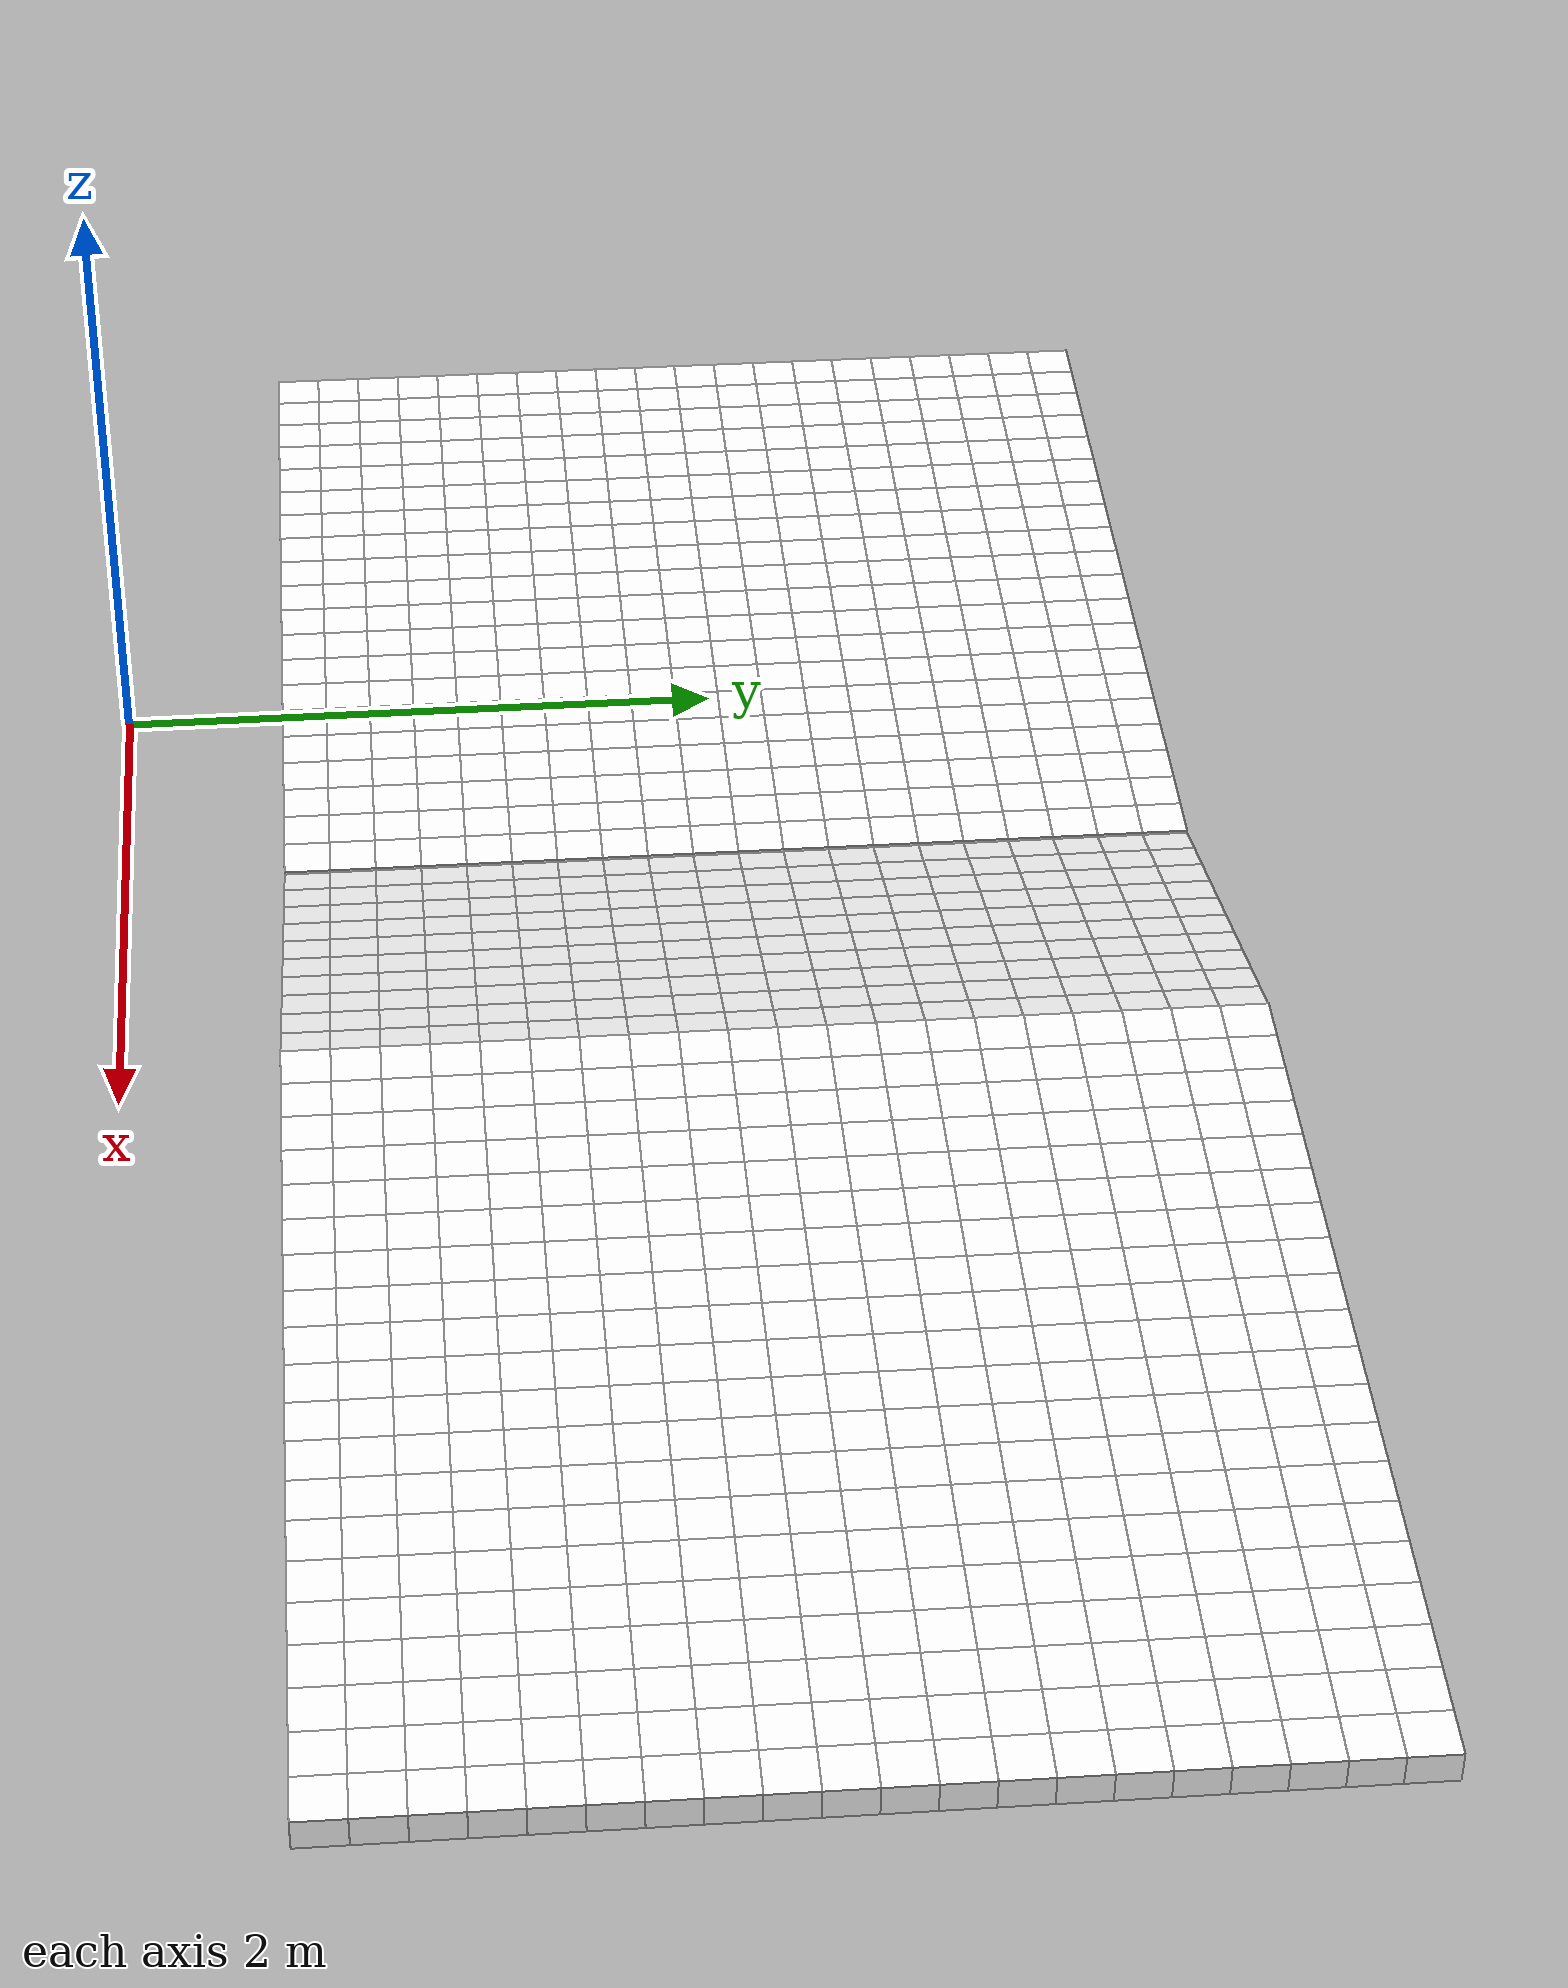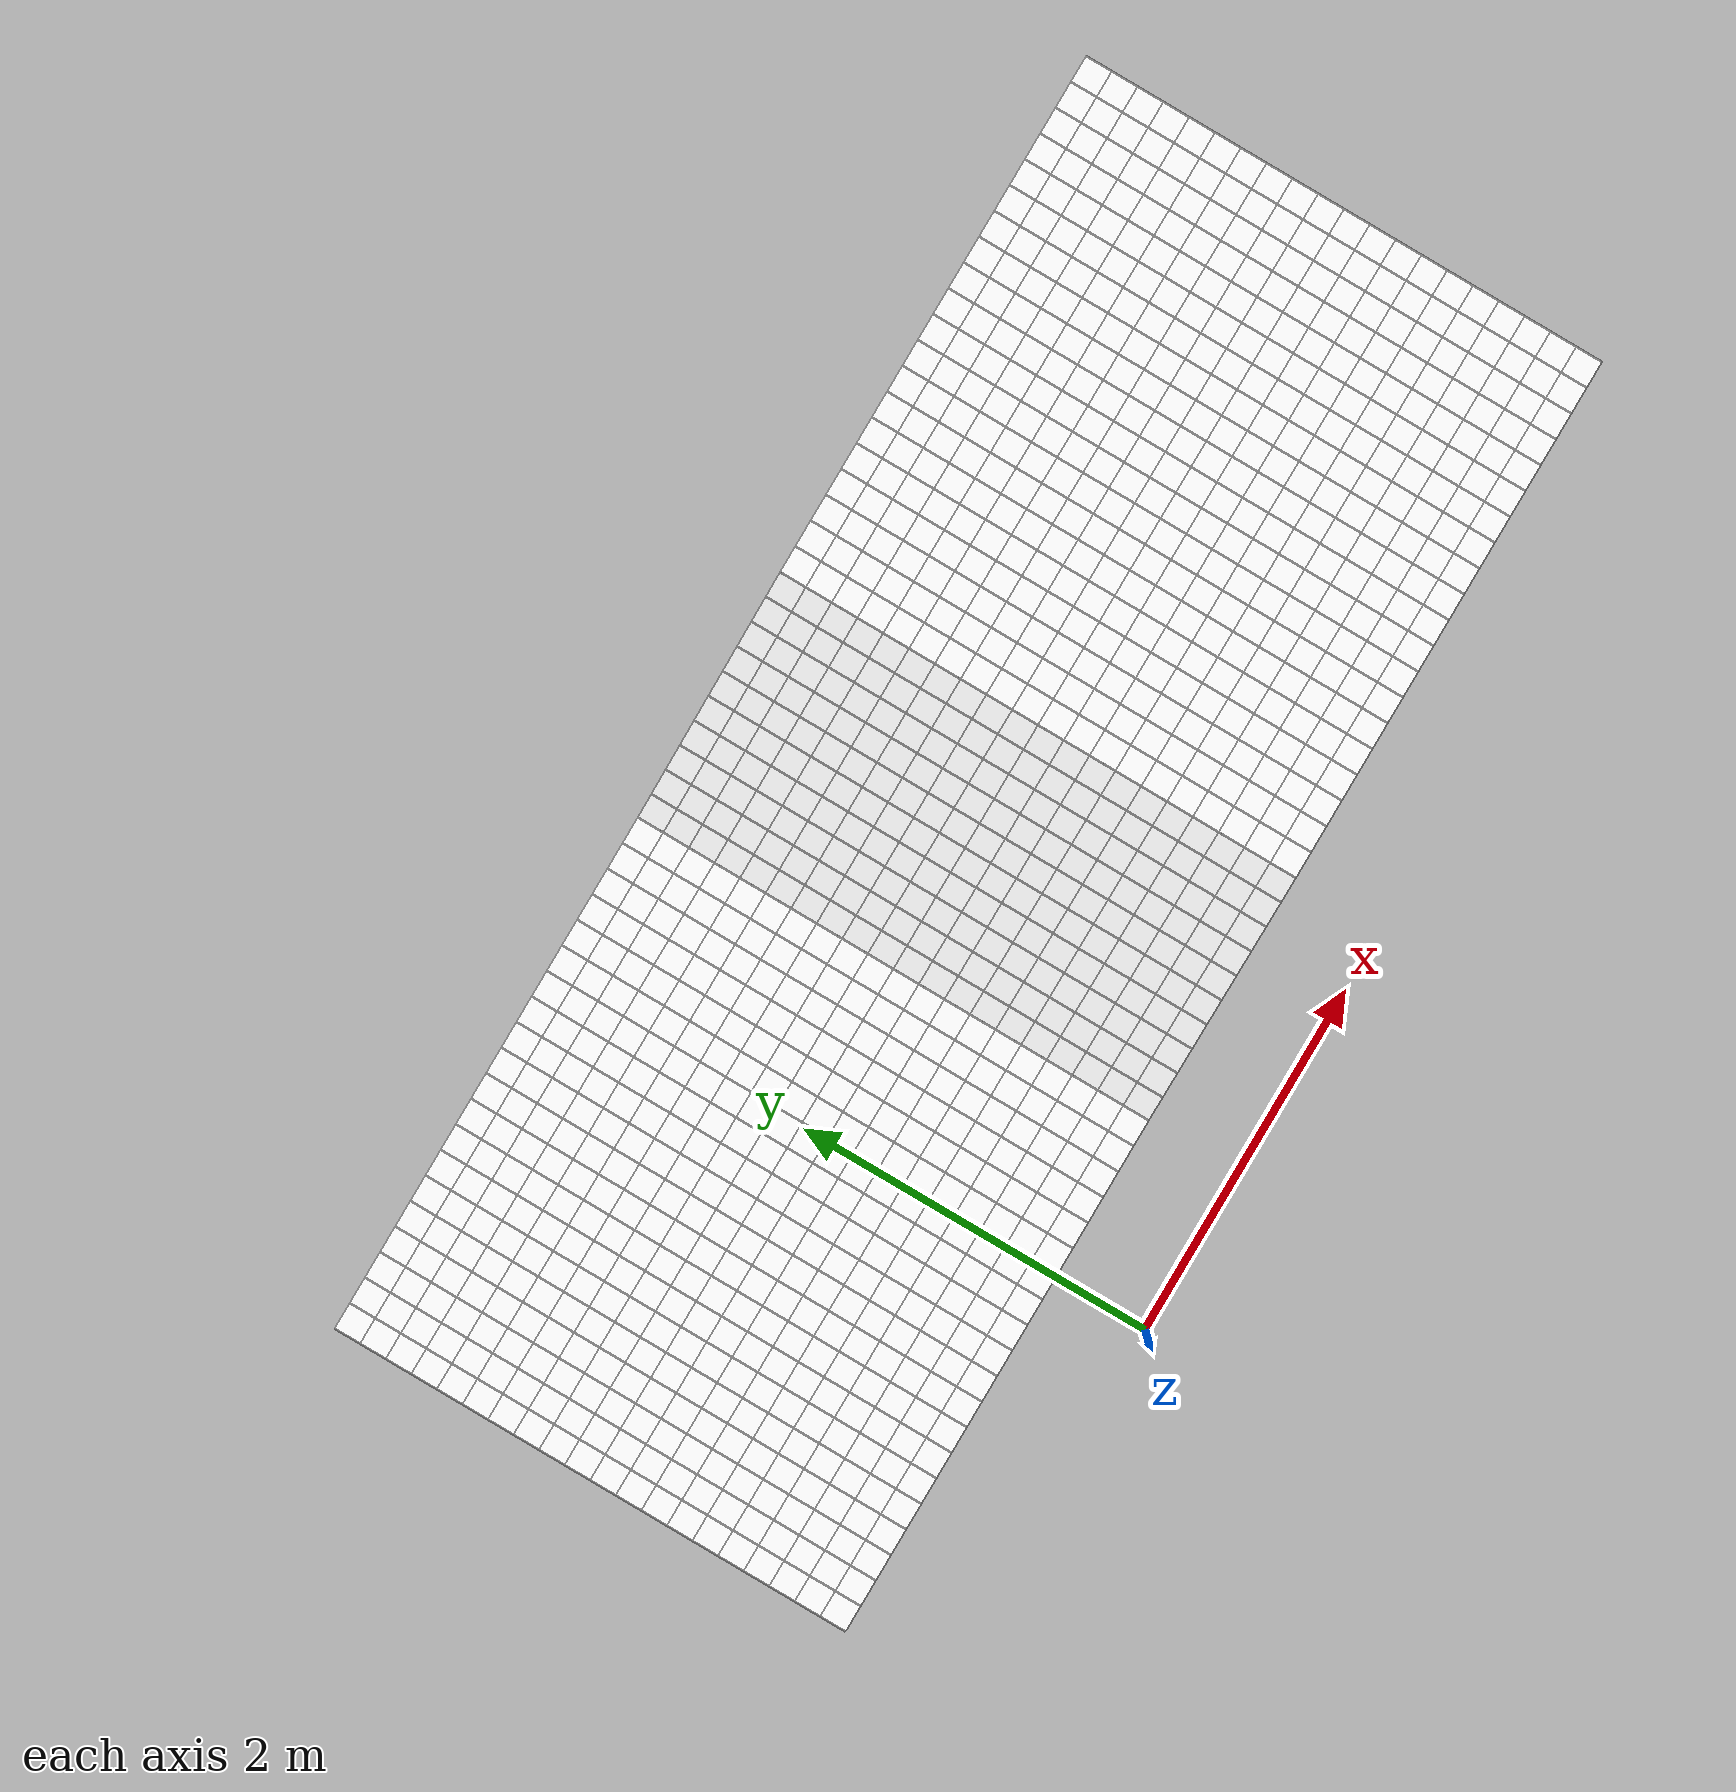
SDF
<sdf version="1.7">
  <world name="default">

    <!-- Need to be able to manipulate model state -->
    <plugin name="gazebo_ros_state" filename="libgazebo_ros_state.so">
      <ros>
        <namespace>/gazebo</namespace>
      </ros>

      <update_rate>1.0</update_rate>
    </plugin>

    <!-- Need to be able to manipulate model configuration -->
    <plugin name="gazebo_ros_properties" filename="libgazebo_ros_properties.so">
      <ros>
        <namespace>/gazebo</namespace>
      </ros>

      <update_rate>1.0</update_rate>
    </plugin>

    <physics type="ode">
    <max_step_size>0.001</max_step_size>
    <real_time_factor>1.0</real_time_factor>
    <real_time_update_rate>1000</real_time_update_rate>
    <gravity>0 0 -9.81</gravity>
        <ode>
            <solver>
            <type>quick</type>
            <iters>50</iters>
            <sor>1.3</sor>
            </solver>
            <constraints>
            <cfm>0.0</cfm>
            <erp>0.2</erp>
            <contact_max_correcting_vel>10.0</contact_max_correcting_vel>
            <contact_surface_layer>0.001</contact_surface_layer>
            </constraints>
        </ode>
    </physics>

    <scene>
    <sky>
        <clouds>
            <speed>12</speed>
        </clouds>
    </sky>
    </scene>
    <!-- A global light source -->
    <include>
        <uri>model://sun</uri>
    </include>
    <!-- A ground plane -->
    <model name="static_environment">
  <static>true</static>
  <link name="region_0">
    <pose>-2.0 0.6 0.0 0.0 0.0 0.0</pose>
    <collision name="region_0_collision">
      <geometry>
        <box>
          <size>0.15 0.15 0.1</size>
        </box>
      </geometry>
      <surface>
        <friction>
          <ode>
            <mu>1.0</mu>
            <mu2>1.0</mu2>
          </ode>
        </friction>
      </surface>
    </collision>
    <visual name="region_0_visual">
      <geometry>
        <box>
          <size>0.15 0.15 0.1</size>
        </box>
      </geometry>
      <material>
        <ambient>1.0 1.0 1.0 1.0</ambient>
        <diffuse>1.0 1.0 1.0 1.0</diffuse>
      </material>
    </visual>
  </link>
  <link name="region_1">
    <pose>-1.85 0.6 0.0 0.0 0.0 0.0</pose>
    <collision name="region_1_collision">
      <geometry>
        <box>
          <size>0.15 0.15 0.1</size>
        </box>
      </geometry>
      <surface>
        <friction>
          <ode>
            <mu>1.0</mu>
            <mu2>1.0</mu2>
          </ode>
        </friction>
      </surface>
    </collision>
    <visual name="region_1_visual">
      <geometry>
        <box>
          <size>0.15 0.15 0.1</size>
        </box>
      </geometry>
      <material>
        <ambient>1.0 1.0 1.0 1.0</ambient>
        <diffuse>1.0 1.0 1.0 1.0</diffuse>
      </material>
    </visual>
  </link>
  <link name="region_2">
    <pose>-1.7 0.6 0.0 0.0 0.0 0.0</pose>
    <collision name="region_2_collision">
      <geometry>
        <box>
          <size>0.15 0.15 0.1</size>
        </box>
      </geometry>
      <surface>
        <friction>
          <ode>
            <mu>1.0</mu>
            <mu2>1.0</mu2>
          </ode>
        </friction>
      </surface>
    </collision>
    <visual name="region_2_visual">
      <geometry>
        <box>
          <size>0.15 0.15 0.1</size>
        </box>
      </geometry>
      <material>
        <ambient>1.0 1.0 1.0 1.0</ambient>
        <diffuse>1.0 1.0 1.0 1.0</diffuse>
      </material>
    </visual>
  </link>
  <link name="region_3">
    <pose>-1.55 0.6 0.0 0.0 0.0 0.0</pose>
    <collision name="region_3_collision">
      <geometry>
        <box>
          <size>0.15 0.15 0.1</size>
        </box>
      </geometry>
      <surface>
        <friction>
          <ode>
            <mu>1.0</mu>
            <mu2>1.0</mu2>
          </ode>
        </friction>
      </surface>
    </collision>
    <visual name="region_3_visual">
      <geometry>
        <box>
          <size>0.15 0.15 0.1</size>
        </box>
      </geometry>
      <material>
        <ambient>1.0 1.0 1.0 1.0</ambient>
        <diffuse>1.0 1.0 1.0 1.0</diffuse>
      </material>
    </visual>
  </link>
  <link name="region_4">
    <pose>-1.4 0.6 0.0 0.0 0.0 0.0</pose>
    <collision name="region_4_collision">
      <geometry>
        <box>
          <size>0.15 0.15 0.1</size>
        </box>
      </geometry>
      <surface>
        <friction>
          <ode>
            <mu>1.0</mu>
            <mu2>1.0</mu2>
          </ode>
        </friction>
      </surface>
    </collision>
    <visual name="region_4_visual">
      <geometry>
        <box>
          <size>0.15 0.15 0.1</size>
        </box>
      </geometry>
      <material>
        <ambient>1.0 1.0 1.0 1.0</ambient>
        <diffuse>1.0 1.0 1.0 1.0</diffuse>
      </material>
    </visual>
  </link>
  <link name="region_5">
    <pose>-1.25 0.6 0.0 0.0 0.0 0.0</pose>
    <collision name="region_5_collision">
      <geometry>
        <box>
          <size>0.15 0.15 0.1</size>
        </box>
      </geometry>
      <surface>
        <friction>
          <ode>
            <mu>1.0</mu>
            <mu2>1.0</mu2>
          </ode>
        </friction>
      </surface>
    </collision>
    <visual name="region_5_visual">
      <geometry>
        <box>
          <size>0.15 0.15 0.1</size>
        </box>
      </geometry>
      <material>
        <ambient>1.0 1.0 1.0 1.0</ambient>
        <diffuse>1.0 1.0 1.0 1.0</diffuse>
      </material>
    </visual>
  </link>
  <link name="region_6">
    <pose>-1.1 0.6 0.0 0.0 0.0 0.0</pose>
    <collision name="region_6_collision">
      <geometry>
        <box>
          <size>0.15 0.15 0.1</size>
        </box>
      </geometry>
      <surface>
        <friction>
          <ode>
            <mu>1.0</mu>
            <mu2>1.0</mu2>
          </ode>
        </friction>
      </surface>
    </collision>
    <visual name="region_6_visual">
      <geometry>
        <box>
          <size>0.15 0.15 0.1</size>
        </box>
      </geometry>
      <material>
        <ambient>1.0 1.0 1.0 1.0</ambient>
        <diffuse>1.0 1.0 1.0 1.0</diffuse>
      </material>
    </visual>
  </link>
  <link name="region_7">
    <pose>-0.95 0.6 0.0 0.0 0.0 0.0</pose>
    <collision name="region_7_collision">
      <geometry>
        <box>
          <size>0.15 0.15 0.1</size>
        </box>
      </geometry>
      <surface>
        <friction>
          <ode>
            <mu>1.0</mu>
            <mu2>1.0</mu2>
          </ode>
        </friction>
      </surface>
    </collision>
    <visual name="region_7_visual">
      <geometry>
        <box>
          <size>0.15 0.15 0.1</size>
        </box>
      </geometry>
      <material>
        <ambient>1.0 1.0 1.0 1.0</ambient>
        <diffuse>1.0 1.0 1.0 1.0</diffuse>
      </material>
    </visual>
  </link>
  <link name="region_8">
    <pose>-0.8 0.6 0.0 0.0 0.0 0.0</pose>
    <collision name="region_8_collision">
      <geometry>
        <box>
          <size>0.15 0.15 0.1</size>
        </box>
      </geometry>
      <surface>
        <friction>
          <ode>
            <mu>1.0</mu>
            <mu2>1.0</mu2>
          </ode>
        </friction>
      </surface>
    </collision>
    <visual name="region_8_visual">
      <geometry>
        <box>
          <size>0.15 0.15 0.1</size>
        </box>
      </geometry>
      <material>
        <ambient>1.0 1.0 1.0 1.0</ambient>
        <diffuse>1.0 1.0 1.0 1.0</diffuse>
      </material>
    </visual>
  </link>
  <link name="region_9">
    <pose>-0.6500000000000001 0.6 0.0 0.0 0.0 0.0</pose>
    <collision name="region_9_collision">
      <geometry>
        <box>
          <size>0.15 0.15 0.1</size>
        </box>
      </geometry>
      <surface>
        <friction>
          <ode>
            <mu>1.0</mu>
            <mu2>1.0</mu2>
          </ode>
        </friction>
      </surface>
    </collision>
    <visual name="region_9_visual">
      <geometry>
        <box>
          <size>0.15 0.15 0.1</size>
        </box>
      </geometry>
      <material>
        <ambient>1.0 1.0 1.0 1.0</ambient>
        <diffuse>1.0 1.0 1.0 1.0</diffuse>
      </material>
    </visual>
  </link>
  <link name="region_10">
    <pose>-0.5000000000000002 0.6 0.0 0.0 0.0 0.0</pose>
    <collision name="region_10_collision">
      <geometry>
        <box>
          <size>0.15 0.15 0.1</size>
        </box>
      </geometry>
      <surface>
        <friction>
          <ode>
            <mu>1.0</mu>
            <mu2>1.0</mu2>
          </ode>
        </friction>
      </surface>
    </collision>
    <visual name="region_10_visual">
      <geometry>
        <box>
          <size>0.15 0.15 0.1</size>
        </box>
      </geometry>
      <material>
        <ambient>1.0 1.0 1.0 1.0</ambient>
        <diffuse>1.0 1.0 1.0 1.0</diffuse>
      </material>
    </visual>
  </link>
  <link name="region_11">
    <pose>-0.3500000000000003 0.6 0.0 0.0 0.0 0.0</pose>
    <collision name="region_11_collision">
      <geometry>
        <box>
          <size>0.15 0.15 0.1</size>
        </box>
      </geometry>
      <surface>
        <friction>
          <ode>
            <mu>1.0</mu>
            <mu2>1.0</mu2>
          </ode>
        </friction>
      </surface>
    </collision>
    <visual name="region_11_visual">
      <geometry>
        <box>
          <size>0.15 0.15 0.1</size>
        </box>
      </geometry>
      <material>
        <ambient>1.0 1.0 1.0 1.0</ambient>
        <diffuse>1.0 1.0 1.0 1.0</diffuse>
      </material>
    </visual>
  </link>
  <link name="region_12">
    <pose>-0.2000000000000004 0.6 0.0 0.0 0.0 0.0</pose>
    <collision name="region_12_collision">
      <geometry>
        <box>
          <size>0.15 0.15 0.1</size>
        </box>
      </geometry>
      <surface>
        <friction>
          <ode>
            <mu>1.0</mu>
            <mu2>1.0</mu2>
          </ode>
        </friction>
      </surface>
    </collision>
    <visual name="region_12_visual">
      <geometry>
        <box>
          <size>0.15 0.15 0.1</size>
        </box>
      </geometry>
      <material>
        <ambient>1.0 1.0 1.0 1.0</ambient>
        <diffuse>1.0 1.0 1.0 1.0</diffuse>
      </material>
    </visual>
  </link>
  <link name="region_13">
    <pose>-0.05000000000000049 0.6 0.0 0.0 0.0 0.0</pose>
    <collision name="region_13_collision">
      <geometry>
        <box>
          <size>0.15 0.15 0.1</size>
        </box>
      </geometry>
      <surface>
        <friction>
          <ode>
            <mu>1.0</mu>
            <mu2>1.0</mu2>
          </ode>
        </friction>
      </surface>
    </collision>
    <visual name="region_13_visual">
      <geometry>
        <box>
          <size>0.15 0.15 0.1</size>
        </box>
      </geometry>
      <material>
        <ambient>1.0 1.0 1.0 1.0</ambient>
        <diffuse>1.0 1.0 1.0 1.0</diffuse>
      </material>
    </visual>
  </link>
  <link name="region_14">
    <pose>0.09999999999999964 0.6 0.0 0.0 0.0 0.0</pose>
    <collision name="region_14_collision">
      <geometry>
        <box>
          <size>0.15 0.15 0.1</size>
        </box>
      </geometry>
      <surface>
        <friction>
          <ode>
            <mu>1.0</mu>
            <mu2>1.0</mu2>
          </ode>
        </friction>
      </surface>
    </collision>
    <visual name="region_14_visual">
      <geometry>
        <box>
          <size>0.15 0.15 0.1</size>
        </box>
      </geometry>
      <material>
        <ambient>1.0 1.0 1.0 1.0</ambient>
        <diffuse>1.0 1.0 1.0 1.0</diffuse>
      </material>
    </visual>
  </link>
  <link name="region_15">
    <pose>0.24999999999999956 0.6 0.0 0.0 0.0 0.0</pose>
    <collision name="region_15_collision">
      <geometry>
        <box>
          <size>0.15 0.15 0.1</size>
        </box>
      </geometry>
      <surface>
        <friction>
          <ode>
            <mu>1.0</mu>
            <mu2>1.0</mu2>
          </ode>
        </friction>
      </surface>
    </collision>
    <visual name="region_15_visual">
      <geometry>
        <box>
          <size>0.15 0.15 0.1</size>
        </box>
      </geometry>
      <material>
        <ambient>1.0 1.0 1.0 1.0</ambient>
        <diffuse>1.0 1.0 1.0 1.0</diffuse>
      </material>
    </visual>
  </link>
  <link name="region_16">
    <pose>0.39999999999999947 0.6 0.0 0.0 0.0 0.0</pose>
    <collision name="region_16_collision">
      <geometry>
        <box>
          <size>0.15 0.15 0.1</size>
        </box>
      </geometry>
      <surface>
        <friction>
          <ode>
            <mu>1.0</mu>
            <mu2>1.0</mu2>
          </ode>
        </friction>
      </surface>
    </collision>
    <visual name="region_16_visual">
      <geometry>
        <box>
          <size>0.15 0.15 0.1</size>
        </box>
      </geometry>
      <material>
        <ambient>1.0 1.0 1.0 1.0</ambient>
        <diffuse>1.0 1.0 1.0 1.0</diffuse>
      </material>
    </visual>
  </link>
  <link name="region_17">
    <pose>0.5499999999999994 0.6 0.0 0.0 0.0 0.0</pose>
    <collision name="region_17_collision">
      <geometry>
        <box>
          <size>0.15 0.15 0.1</size>
        </box>
      </geometry>
      <surface>
        <friction>
          <ode>
            <mu>1.0</mu>
            <mu2>1.0</mu2>
          </ode>
        </friction>
      </surface>
    </collision>
    <visual name="region_17_visual">
      <geometry>
        <box>
          <size>0.15 0.15 0.1</size>
        </box>
      </geometry>
      <material>
        <ambient>1.0 1.0 1.0 1.0</ambient>
        <diffuse>1.0 1.0 1.0 1.0</diffuse>
      </material>
    </visual>
  </link>
  <link name="region_18">
    <pose>0.6999999999999993 0.6 0.0 0.0 0.0 0.0</pose>
    <collision name="region_18_collision">
      <geometry>
        <box>
          <size>0.15 0.15 0.1</size>
        </box>
      </geometry>
      <surface>
        <friction>
          <ode>
            <mu>1.0</mu>
            <mu2>1.0</mu2>
          </ode>
        </friction>
      </surface>
    </collision>
    <visual name="region_18_visual">
      <geometry>
        <box>
          <size>0.15 0.15 0.1</size>
        </box>
      </geometry>
      <material>
        <ambient>1.0 1.0 1.0 1.0</ambient>
        <diffuse>1.0 1.0 1.0 1.0</diffuse>
      </material>
    </visual>
  </link>
  <link name="region_19">
    <pose>0.8499999999999992 0.6 0.0 0.0 0.0 0.0</pose>
    <collision name="region_19_collision">
      <geometry>
        <box>
          <size>0.15 0.15 0.1</size>
        </box>
      </geometry>
      <surface>
        <friction>
          <ode>
            <mu>1.0</mu>
            <mu2>1.0</mu2>
          </ode>
        </friction>
      </surface>
    </collision>
    <visual name="region_19_visual">
      <geometry>
        <box>
          <size>0.15 0.15 0.1</size>
        </box>
      </geometry>
      <material>
        <ambient>1.0 1.0 1.0 1.0</ambient>
        <diffuse>1.0 1.0 1.0 1.0</diffuse>
      </material>
    </visual>
  </link>
  <link name="region_20">
    <pose>-2.0 0.75 0.0 0.0 0.0 0.0</pose>
    <collision name="region_20_collision">
      <geometry>
        <box>
          <size>0.15 0.15 0.1</size>
        </box>
      </geometry>
      <surface>
        <friction>
          <ode>
            <mu>1.0</mu>
            <mu2>1.0</mu2>
          </ode>
        </friction>
      </surface>
    </collision>
    <visual name="region_20_visual">
      <geometry>
        <box>
          <size>0.15 0.15 0.1</size>
        </box>
      </geometry>
      <material>
        <ambient>1.0 1.0 1.0 1.0</ambient>
        <diffuse>1.0 1.0 1.0 1.0</diffuse>
      </material>
    </visual>
  </link>
  <link name="region_21">
    <pose>-1.85 0.75 0.0 0.0 0.0 0.0</pose>
    <collision name="region_21_collision">
      <geometry>
        <box>
          <size>0.15 0.15 0.1</size>
        </box>
      </geometry>
      <surface>
        <friction>
          <ode>
            <mu>1.0</mu>
            <mu2>1.0</mu2>
          </ode>
        </friction>
      </surface>
    </collision>
    <visual name="region_21_visual">
      <geometry>
        <box>
          <size>0.15 0.15 0.1</size>
        </box>
      </geometry>
      <material>
        <ambient>1.0 1.0 1.0 1.0</ambient>
        <diffuse>1.0 1.0 1.0 1.0</diffuse>
      </material>
    </visual>
  </link>
  <link name="region_22">
    <pose>-1.7 0.75 0.0 0.0 0.0 0.0</pose>
    <collision name="region_22_collision">
      <geometry>
        <box>
          <size>0.15 0.15 0.1</size>
        </box>
      </geometry>
      <surface>
        <friction>
          <ode>
            <mu>1.0</mu>
            <mu2>1.0</mu2>
          </ode>
        </friction>
      </surface>
    </collision>
    <visual name="region_22_visual">
      <geometry>
        <box>
          <size>0.15 0.15 0.1</size>
        </box>
      </geometry>
      <material>
        <ambient>1.0 1.0 1.0 1.0</ambient>
        <diffuse>1.0 1.0 1.0 1.0</diffuse>
      </material>
    </visual>
  </link>
  <link name="region_23">
    <pose>-1.55 0.75 0.0 0.0 0.0 0.0</pose>
    <collision name="region_23_collision">
      <geometry>
        <box>
          <size>0.15 0.15 0.1</size>
        </box>
      </geometry>
      <surface>
        <friction>
          <ode>
            <mu>1.0</mu>
            <mu2>1.0</mu2>
          </ode>
        </friction>
      </surface>
    </collision>
    <visual name="region_23_visual">
      <geometry>
        <box>
          <size>0.15 0.15 0.1</size>
        </box>
      </geometry>
      <material>
        <ambient>1.0 1.0 1.0 1.0</ambient>
        <diffuse>1.0 1.0 1.0 1.0</diffuse>
      </material>
    </visual>
  </link>
  <link name="region_24">
    <pose>-1.4 0.75 0.0 0.0 0.0 0.0</pose>
    <collision name="region_24_collision">
      <geometry>
        <box>
          <size>0.15 0.15 0.1</size>
        </box>
      </geometry>
      <surface>
        <friction>
          <ode>
            <mu>1.0</mu>
            <mu2>1.0</mu2>
          </ode>
        </friction>
      </surface>
    </collision>
    <visual name="region_24_visual">
      <geometry>
        <box>
          <size>0.15 0.15 0.1</size>
        </box>
      </geometry>
      <material>
        <ambient>1.0 1.0 1.0 1.0</ambient>
        <diffuse>1.0 1.0 1.0 1.0</diffuse>
      </material>
    </visual>
  </link>
  <link name="region_25">
    <pose>-1.25 0.75 0.0 0.0 0.0 0.0</pose>
    <collision name="region_25_collision">
      <geometry>
        <box>
          <size>0.15 0.15 0.1</size>
        </box>
      </geometry>
      <surface>
        <friction>
          <ode>
            <mu>1.0</mu>
            <mu2>1.0</mu2>
          </ode>
        </friction>
      </surface>
    </collision>
    <visual name="region_25_visual">
      <geometry>
        <box>
          <size>0.15 0.15 0.1</size>
        </box>
      </geometry>
      <material>
        <ambient>1.0 1.0 1.0 1.0</ambient>
        <diffuse>1.0 1.0 1.0 1.0</diffuse>
      </material>
    </visual>
  </link>
  <link name="region_26">
    <pose>-1.1 0.75 0.0 0.0 0.0 0.0</pose>
    <collision name="region_26_collision">
      <geometry>
        <box>
          <size>0.15 0.15 0.1</size>
        </box>
      </geometry>
      <surface>
        <friction>
          <ode>
            <mu>1.0</mu>
            <mu2>1.0</mu2>
          </ode>
        </friction>
      </surface>
    </collision>
    <visual name="region_26_visual">
      <geometry>
        <box>
          <size>0.15 0.15 0.1</size>
        </box>
      </geometry>
      <material>
        <ambient>1.0 1.0 1.0 1.0</ambient>
        <diffuse>1.0 1.0 1.0 1.0</diffuse>
      </material>
    </visual>
  </link>
  <link name="region_27">
    <pose>-0.95 0.75 0.0 0.0 0.0 0.0</pose>
    <collision name="region_27_collision">
      <geometry>
        <box>
          <size>0.15 0.15 0.1</size>
        </box>
      </geometry>
      <surface>
        <friction>
          <ode>
            <mu>1.0</mu>
            <mu2>1.0</mu2>
          </ode>
        </friction>
      </surface>
    </collision>
    <visual name="region_27_visual">
      <geometry>
        <box>
          <size>0.15 0.15 0.1</size>
        </box>
      </geometry>
      <material>
        <ambient>1.0 1.0 1.0 1.0</ambient>
        <diffuse>1.0 1.0 1.0 1.0</diffuse>
      </material>
    </visual>
  </link>
  <link name="region_28">
    <pose>-0.8 0.75 0.0 0.0 0.0 0.0</pose>
    <collision name="region_28_collision">
      <geometry>
        <box>
          <size>0.15 0.15 0.1</size>
        </box>
      </geometry>
      <surface>
        <friction>
          <ode>
            <mu>1.0</mu>
            <mu2>1.0</mu2>
          </ode>
        </friction>
      </surface>
    </collision>
    <visual name="region_28_visual">
      <geometry>
        <box>
          <size>0.15 0.15 0.1</size>
        </box>
      </geometry>
      <material>
        <ambient>1.0 1.0 1.0 1.0</ambient>
        <diffuse>1.0 1.0 1.0 1.0</diffuse>
      </material>
    </visual>
  </link>
  <link name="region_29">
    <pose>-0.6500000000000001 0.75 0.0 0.0 0.0 0.0</pose>
    <collision name="region_29_collision">
      <geometry>
        <box>
          <size>0.15 0.15 0.1</size>
        </box>
      </geometry>
      <surface>
        <friction>
          <ode>
            <mu>1.0</mu>
            <mu2>1.0</mu2>
          </ode>
        </friction>
      </surface>
    </collision>
    <visual name="region_29_visual">
      <geometry>
        <box>
          <size>0.15 0.15 0.1</size>
        </box>
      </geometry>
      <material>
        <ambient>1.0 1.0 1.0 1.0</ambient>
        <diffuse>1.0 1.0 1.0 1.0</diffuse>
      </material>
    </visual>
  </link>
  <link name="region_30">
    <pose>-0.5000000000000002 0.75 0.0 0.0 0.0 0.0</pose>
    <collision name="region_30_collision">
      <geometry>
        <box>
          <size>0.15 0.15 0.1</size>
        </box>
      </geometry>
      <surface>
        <friction>
          <ode>
            <mu>1.0</mu>
            <mu2>1.0</mu2>
          </ode>
        </friction>
      </surface>
    </collision>
    <visual name="region_30_visual">
      <geometry>
        <box>
          <size>0.15 0.15 0.1</size>
        </box>
      </geometry>
      <material>
        <ambient>1.0 1.0 1.0 1.0</ambient>
        <diffuse>1.0 1.0 1.0 1.0</diffuse>
      </material>
    </visual>
  </link>
  <link name="region_31">
    <pose>-0.3500000000000003 0.75 0.0 0.0 0.0 0.0</pose>
    <collision name="region_31_collision">
      <geometry>
        <box>
          <size>0.15 0.15 0.1</size>
        </box>
      </geometry>
      <surface>
        <friction>
          <ode>
            <mu>1.0</mu>
            <mu2>1.0</mu2>
          </ode>
        </friction>
      </surface>
    </collision>
    <visual name="region_31_visual">
      <geometry>
        <box>
          <size>0.15 0.15 0.1</size>
        </box>
      </geometry>
      <material>
        <ambient>1.0 1.0 1.0 1.0</ambient>
        <diffuse>1.0 1.0 1.0 1.0</diffuse>
      </material>
    </visual>
  </link>
  <link name="region_32">
    <pose>-0.2000000000000004 0.75 0.0 0.0 0.0 0.0</pose>
    <collision name="region_32_collision">
      <geometry>
        <box>
          <size>0.15 0.15 0.1</size>
        </box>
      </geometry>
      <surface>
        <friction>
          <ode>
            <mu>1.0</mu>
            <mu2>1.0</mu2>
          </ode>
        </friction>
      </surface>
    </collision>
    <visual name="region_32_visual">
      <geometry>
        <box>
          <size>0.15 0.15 0.1</size>
        </box>
      </geometry>
      <material>
        <ambient>1.0 1.0 1.0 1.0</ambient>
        <diffuse>1.0 1.0 1.0 1.0</diffuse>
      </material>
    </visual>
  </link>
  <link name="region_33">
    <pose>-0.05000000000000049 0.75 0.0 0.0 0.0 0.0</pose>
    <collision name="region_33_collision">
      <geometry>
        <box>
          <size>0.15 0.15 0.1</size>
        </box>
      </geometry>
      <surface>
        <friction>
          <ode>
            <mu>1.0</mu>
            <mu2>1.0</mu2>
          </ode>
        </friction>
      </surface>
    </collision>
    <visual name="region_33_visual">
      <geometry>
        <box>
          <size>0.15 0.15 0.1</size>
        </box>
      </geometry>
      <material>
        <ambient>1.0 1.0 1.0 1.0</ambient>
        <diffuse>1.0 1.0 1.0 1.0</diffuse>
      </material>
    </visual>
  </link>
  <link name="region_34">
    <pose>0.09999999999999964 0.75 0.0 0.0 0.0 0.0</pose>
    <collision name="region_34_collision">
      <geometry>
        <box>
          <size>0.15 0.15 0.1</size>
        </box>
      </geometry>
      <surface>
        <friction>
          <ode>
            <mu>1.0</mu>
            <mu2>1.0</mu2>
          </ode>
        </friction>
      </surface>
    </collision>
    <visual name="region_34_visual">
      <geometry>
        <box>
          <size>0.15 0.15 0.1</size>
        </box>
      </geometry>
      <material>
        <ambient>1.0 1.0 1.0 1.0</ambient>
        <diffuse>1.0 1.0 1.0 1.0</diffuse>
      </material>
    </visual>
  </link>
  <link name="region_35">
    <pose>0.24999999999999956 0.75 0.0 0.0 0.0 0.0</pose>
    <collision name="region_35_collision">
      <geometry>
        <box>
          <size>0.15 0.15 0.1</size>
        </box>
      </geometry>
      <surface>
        <friction>
          <ode>
            <mu>1.0</mu>
            <mu2>1.0</mu2>
          </ode>
        </friction>
      </surface>
    </collision>
    <visual name="region_35_visual">
      <geometry>
        <box>
          <size>0.15 0.15 0.1</size>
        </box>
      </geometry>
      <material>
        <ambient>1.0 1.0 1.0 1.0</ambient>
        <diffuse>1.0 1.0 1.0 1.0</diffuse>
      </material>
    </visual>
  </link>
  <link name="region_36">
    <pose>0.39999999999999947 0.75 0.0 0.0 0.0 0.0</pose>
    <collision name="region_36_collision">
      <geometry>
        <box>
          <size>0.15 0.15 0.1</size>
        </box>
      </geometry>
      <surface>
        <friction>
          <ode>
            <mu>1.0</mu>
            <mu2>1.0</mu2>
          </ode>
        </friction>
      </surface>
    </collision>
    <visual name="region_36_visual">
      <geometry>
        <box>
          <size>0.15 0.15 0.1</size>
        </box>
      </geometry>
      <material>
        <ambient>1.0 1.0 1.0 1.0</ambient>
        <diffuse>1.0 1.0 1.0 1.0</diffuse>
      </material>
    </visual>
  </link>
  <link name="region_37">
    <pose>0.5499999999999994 0.75 0.0 0.0 0.0 0.0</pose>
    <collision name="region_37_collision">
      <geometry>
        <box>
          <size>0.15 0.15 0.1</size>
        </box>
      </geometry>
      <surface>
        <friction>
          <ode>
            <mu>1.0</mu>
            <mu2>1.0</mu2>
          </ode>
        </friction>
      </surface>
    </collision>
    <visual name="region_37_visual">
      <geometry>
        <box>
          <size>0.15 0.15 0.1</size>
        </box>
      </geometry>
      <material>
        <ambient>1.0 1.0 1.0 1.0</ambient>
        <diffuse>1.0 1.0 1.0 1.0</diffuse>
      </material>
    </visual>
  </link>
  <link name="region_38">
    <pose>0.6999999999999993 0.75 0.0 0.0 0.0 0.0</pose>
    <collision name="region_38_collision">
      <geometry>
        <box>
          <size>0.15 0.15 0.1</size>
        </box>
      </geometry>
      <surface>
        <friction>
          <ode>
            <mu>1.0</mu>
            <mu2>1.0</mu2>
          </ode>
        </friction>
      </surface>
    </collision>
    <visual name="region_38_visual">
      <geometry>
        <box>
          <size>0.15 0.15 0.1</size>
        </box>
      </geometry>
      <material>
        <ambient>1.0 1.0 1.0 1.0</ambient>
        <diffuse>1.0 1.0 1.0 1.0</diffuse>
      </material>
    </visual>
  </link>
  <link name="region_39">
    <pose>0.8499999999999992 0.75 0.0 0.0 0.0 0.0</pose>
    <collision name="region_39_collision">
      <geometry>
        <box>
          <size>0.15 0.15 0.1</size>
        </box>
      </geometry>
      <surface>
        <friction>
          <ode>
            <mu>1.0</mu>
            <mu2>1.0</mu2>
          </ode>
        </friction>
      </surface>
    </collision>
    <visual name="region_39_visual">
      <geometry>
        <box>
          <size>0.15 0.15 0.1</size>
        </box>
      </geometry>
      <material>
        <ambient>1.0 1.0 1.0 1.0</ambient>
        <diffuse>1.0 1.0 1.0 1.0</diffuse>
      </material>
    </visual>
  </link>
  <link name="region_40">
    <pose>-2.0 0.8999999999999999 0.0 0.0 0.0 0.0</pose>
    <collision name="region_40_collision">
      <geometry>
        <box>
          <size>0.15 0.15 0.1</size>
        </box>
      </geometry>
      <surface>
        <friction>
          <ode>
            <mu>1.0</mu>
            <mu2>1.0</mu2>
          </ode>
        </friction>
      </surface>
    </collision>
    <visual name="region_40_visual">
      <geometry>
        <box>
          <size>0.15 0.15 0.1</size>
        </box>
      </geometry>
      <material>
        <ambient>1.0 1.0 1.0 1.0</ambient>
        <diffuse>1.0 1.0 1.0 1.0</diffuse>
      </material>
    </visual>
  </link>
  <link name="region_41">
    <pose>-1.85 0.8999999999999999 0.0 0.0 0.0 0.0</pose>
    <collision name="region_41_collision">
      <geometry>
        <box>
          <size>0.15 0.15 0.1</size>
        </box>
      </geometry>
      <surface>
        <friction>
          <ode>
            <mu>1.0</mu>
            <mu2>1.0</mu2>
          </ode>
        </friction>
      </surface>
    </collision>
    <visual name="region_41_visual">
      <geometry>
        <box>
          <size>0.15 0.15 0.1</size>
        </box>
      </geometry>
      <material>
        <ambient>1.0 1.0 1.0 1.0</ambient>
        <diffuse>1.0 1.0 1.0 1.0</diffuse>
      </material>
    </visual>
  </link>
  <link name="region_42">
    <pose>-1.7 0.8999999999999999 0.0 0.0 0.0 0.0</pose>
    <collision name="region_42_collision">
      <geometry>
        <box>
          <size>0.15 0.15 0.1</size>
        </box>
      </geometry>
      <surface>
        <friction>
          <ode>
            <mu>1.0</mu>
            <mu2>1.0</mu2>
          </ode>
        </friction>
      </surface>
    </collision>
    <visual name="region_42_visual">
      <geometry>
        <box>
          <size>0.15 0.15 0.1</size>
        </box>
      </geometry>
      <material>
        <ambient>1.0 1.0 1.0 1.0</ambient>
        <diffuse>1.0 1.0 1.0 1.0</diffuse>
      </material>
    </visual>
  </link>
  <link name="region_43">
    <pose>-1.55 0.8999999999999999 0.0 0.0 0.0 0.0</pose>
    <collision name="region_43_collision">
      <geometry>
        <box>
          <size>0.15 0.15 0.1</size>
        </box>
      </geometry>
      <surface>
        <friction>
          <ode>
            <mu>1.0</mu>
            <mu2>1.0</mu2>
          </ode>
        </friction>
      </surface>
    </collision>
    <visual name="region_43_visual">
      <geometry>
        <box>
          <size>0.15 0.15 0.1</size>
        </box>
      </geometry>
      <material>
        <ambient>1.0 1.0 1.0 1.0</ambient>
        <diffuse>1.0 1.0 1.0 1.0</diffuse>
      </material>
    </visual>
  </link>
  <link name="region_44">
    <pose>-1.4 0.8999999999999999 0.0 0.0 0.0 0.0</pose>
    <collision name="region_44_collision">
      <geometry>
        <box>
          <size>0.15 0.15 0.1</size>
        </box>
      </geometry>
      <surface>
        <friction>
          <ode>
            <mu>1.0</mu>
            <mu2>1.0</mu2>
          </ode>
        </friction>
      </surface>
    </collision>
    <visual name="region_44_visual">
      <geometry>
        <box>
          <size>0.15 0.15 0.1</size>
        </box>
      </geometry>
      <material>
        <ambient>1.0 1.0 1.0 1.0</ambient>
        <diffuse>1.0 1.0 1.0 1.0</diffuse>
      </material>
    </visual>
  </link>
  <link name="region_45">
    <pose>-1.25 0.8999999999999999 0.0 0.0 0.0 0.0</pose>
    <collision name="region_45_collision">
      <geometry>
        <box>
          <size>0.15 0.15 0.1</size>
        </box>
      </geometry>
      <surface>
        <friction>
          <ode>
            <mu>1.0</mu>
            <mu2>1.0</mu2>
          </ode>
        </friction>
      </surface>
    </collision>
    <visual name="region_45_visual">
      <geometry>
        <box>
          <size>0.15 0.15 0.1</size>
        </box>
      </geometry>
      <material>
        <ambient>1.0 1.0 1.0 1.0</ambient>
        <diffuse>1.0 1.0 1.0 1.0</diffuse>
      </material>
    </visual>
  </link>
  <link name="region_46">
    <pose>-1.1 0.8999999999999999 0.0 0.0 0.0 0.0</pose>
    <collision name="region_46_collision">
      <geometry>
        <box>
          <size>0.15 0.15 0.1</size>
        </box>
      </geometry>
      <surface>
        <friction>
          <ode>
            <mu>1.0</mu>
            <mu2>1.0</mu2>
          </ode>
        </friction>
      </surface>
    </collision>
    <visual name="region_46_visual">
      <geometry>
        <box>
          <size>0.15 0.15 0.1</size>
        </box>
      </geometry>
      <material>
        <ambient>1.0 1.0 1.0 1.0</ambient>
        <diffuse>1.0 1.0 1.0 1.0</diffuse>
      </material>
    </visual>
  </link>
  <link name="region_47">
    <pose>-0.95 0.8999999999999999 0.0 0.0 0.0 0.0</pose>
    <collision name="region_47_collision">
      <geometry>
        <box>
          <size>0.15 0.15 0.1</size>
        </box>
      </geometry>
      <surface>
        <friction>
          <ode>
            <mu>1.0</mu>
            <mu2>1.0</mu2>
          </ode>
        </friction>
      </surface>
    </collision>
    <visual name="region_47_visual">
      <geometry>
        <box>
          <size>0.15 0.15 0.1</size>
        </box>
      </geometry>
      <material>
        <ambient>1.0 1.0 1.0 1.0</ambient>
        <diffuse>1.0 1.0 1.0 1.0</diffuse>
      </material>
    </visual>
  </link>
  <link name="region_48">
    <pose>-0.8 0.8999999999999999 0.0 0.0 0.0 0.0</pose>
    <collision name="region_48_collision">
      <geometry>
        <box>
          <size>0.15 0.15 0.1</size>
        </box>
      </geometry>
      <surface>
        <friction>
          <ode>
            <mu>1.0</mu>
            <mu2>1.0</mu2>
          </ode>
        </friction>
      </surface>
    </collision>
    <visual name="region_48_visual">
      <geometry>
        <box>
          <size>0.15 0.15 0.1</size>
        </box>
      </geometry>
      <material>
        <ambient>1.0 1.0 1.0 1.0</ambient>
        <diffuse>1.0 1.0 1.0 1.0</diffuse>
      </material>
    </visual>
  </link>
  <link name="region_49">
    <pose>-0.6500000000000001 0.8999999999999999 0.0 0.0 0.0 0.0</pose>
    <collision name="region_49_collision">
      <geometry>
        <box>
          <size>0.15 0.15 0.1</size>
        </box>
      </geometry>
      <surface>
        <friction>
          <ode>
            <mu>1.0</mu>
            <mu2>1.0</mu2>
          </ode>
        </friction>
      </surface>
    </collision>
    <visual name="region_49_visual">
      <geometry>
        <box>
          <size>0.15 0.15 0.1</size>
        </box>
      </geometry>
      <material>
        <ambient>1.0 1.0 1.0 1.0</ambient>
        <diffuse>1.0 1.0 1.0 1.0</diffuse>
      </material>
    </visual>
  </link>
  <link name="region_50">
    <pose>-0.5000000000000002 0.8999999999999999 0.0 0.0 0.0 0.0</pose>
    <collision name="region_50_collision">
      <geometry>
        <box>
          <size>0.15 0.15 0.1</size>
        </box>
      </geometry>
      <surface>
        <friction>
          <ode>
            <mu>1.0</mu>
            <mu2>1.0</mu2>
          </ode>
        </friction>
      </surface>
    </collision>
    <visual name="region_50_visual">
      <geometry>
        <box>
          <size>0.15 0.15 0.1</size>
        </box>
      </geometry>
      <material>
        <ambient>1.0 1.0 1.0 1.0</ambient>
        <diffuse>1.0 1.0 1.0 1.0</diffuse>
      </material>
    </visual>
  </link>
  <link name="region_51">
    <pose>-0.3500000000000003 0.8999999999999999 0.0 0.0 0.0 0.0</pose>
    <collision name="region_51_collision">
      <geometry>
        <box>
          <size>0.15 0.15 0.1</size>
        </box>
      </geometry>
      <surface>
        <friction>
          <ode>
            <mu>1.0</mu>
            <mu2>1.0</mu2>
          </ode>
        </friction>
      </surface>
    </collision>
    <visual name="region_51_visual">
      <geometry>
        <box>
          <size>0.15 0.15 0.1</size>
        </box>
      </geometry>
      <material>
        <ambient>1.0 1.0 1.0 1.0</ambient>
        <diffuse>1.0 1.0 1.0 1.0</diffuse>
      </material>
    </visual>
  </link>
  <link name="region_52">
    <pose>-0.2000000000000004 0.8999999999999999 0.0 0.0 0.0 0.0</pose>
    <collision name="region_52_collision">
      <geometry>
        <box>
          <size>0.15 0.15 0.1</size>
        </box>
      </geometry>
      <surface>
        <friction>
          <ode>
            <mu>1.0</mu>
            <mu2>1.0</mu2>
          </ode>
        </friction>
      </surface>
    </collision>
    <visual name="region_52_visual">
      <geometry>
        <box>
          <size>0.15 0.15 0.1</size>
        </box>
      </geometry>
      <material>
        <ambient>1.0 1.0 1.0 1.0</ambient>
        <diffuse>1.0 1.0 1.0 1.0</diffuse>
      </material>
    </visual>
  </link>
  <link name="region_53">
    <pose>-0.05000000000000049 0.8999999999999999 0.0 0.0 0.0 0.0</pose>
    <collision name="region_53_collision">
      <geometry>
        <box>
          <size>0.15 0.15 0.1</size>
        </box>
      </geometry>
      <surface>
        <friction>
          <ode>
            <mu>1.0</mu>
            <mu2>1.0</mu2>
          </ode>
        </friction>
      </surface>
    </collision>
    <visual name="region_53_visual">
      <geometry>
        <box>
          <size>0.15 0.15 0.1</size>
        </box>
      </geometry>
      <material>
        <ambient>1.0 1.0 1.0 1.0</ambient>
        <diffuse>1.0 1.0 1.0 1.0</diffuse>
      </material>
    </visual>
  </link>
  <link name="region_54">
    <pose>0.09999999999999964 0.8999999999999999 0.0 0.0 0.0 0.0</pose>
    <collision name="region_54_collision">
      <geometry>
        <box>
          <size>0.15 0.15 0.1</size>
        </box>
      </geometry>
      <surface>
        <friction>
          <ode>
            <mu>1.0</mu>
            <mu2>1.0</mu2>
          </ode>
        </friction>
      </surface>
    </collision>
    <visual name="region_54_visual">
      <geometry>
        <box>
          <size>0.15 0.15 0.1</size>
        </box>
      </geometry>
      <material>
        <ambient>1.0 1.0 1.0 1.0</ambient>
        <diffuse>1.0 1.0 1.0 1.0</diffuse>
      </material>
    </visual>
  </link>
  <link name="region_55">
    <pose>0.24999999999999956 0.8999999999999999 0.0 0.0 0.0 0.0</pose>
    <collision name="region_55_collision">
      <geometry>
        <box>
          <size>0.15 0.15 0.1</size>
        </box>
      </geometry>
      <surface>
        <friction>
          <ode>
            <mu>1.0</mu>
            <mu2>1.0</mu2>
          </ode>
        </friction>
      </surface>
    </collision>
    <visual name="region_55_visual">
      <geometry>
        <box>
          <size>0.15 0.15 0.1</size>
        </box>
      </geometry>
      <material>
        <ambient>1.0 1.0 1.0 1.0</ambient>
        <diffuse>1.0 1.0 1.0 1.0</diffuse>
      </material>
    </visual>
  </link>
  <link name="region_56">
    <pose>0.39999999999999947 0.8999999999999999 0.0 0.0 0.0 0.0</pose>
    <collision name="region_56_collision">
      <geometry>
        <box>
          <size>0.15 0.15 0.1</size>
        </box>
      </geometry>
      <surface>
        <friction>
          <ode>
            <mu>1.0</mu>
            <mu2>1.0</mu2>
          </ode>
        </friction>
      </surface>
    </collision>
    <visual name="region_56_visual">
      <geometry>
        <box>
          <size>0.15 0.15 0.1</size>
        </box>
      </geometry>
      <material>
        <ambient>1.0 1.0 1.0 1.0</ambient>
        <diffuse>1.0 1.0 1.0 1.0</diffuse>
      </material>
    </visual>
  </link>
  <link name="region_57">
    <pose>0.5499999999999994 0.8999999999999999 0.0 0.0 0.0 0.0</pose>
    <collision name="region_57_collision">
      <geometry>
        <box>
          <size>0.15 0.15 0.1</size>
        </box>
      </geometry>
      <surface>
        <friction>
          <ode>
            <mu>1.0</mu>
            <mu2>1.0</mu2>
          </ode>
        </friction>
      </surface>
    </collision>
    <visual name="region_57_visual">
      <geometry>
        <box>
          <size>0.15 0.15 0.1</size>
        </box>
      </geometry>
      <material>
        <ambient>1.0 1.0 1.0 1.0</ambient>
        <diffuse>1.0 1.0 1.0 1.0</diffuse>
      </material>
    </visual>
  </link>
  <link name="region_58">
    <pose>0.6999999999999993 0.8999999999999999 0.0 0.0 0.0 0.0</pose>
    <collision name="region_58_collision">
      <geometry>
        <box>
          <size>0.15 0.15 0.1</size>
        </box>
      </geometry>
      <surface>
        <friction>
          <ode>
            <mu>1.0</mu>
            <mu2>1.0</mu2>
          </ode>
        </friction>
      </surface>
    </collision>
    <visual name="region_58_visual">
      <geometry>
        <box>
          <size>0.15 0.15 0.1</size>
        </box>
      </geometry>
      <material>
        <ambient>1.0 1.0 1.0 1.0</ambient>
        <diffuse>1.0 1.0 1.0 1.0</diffuse>
      </material>
    </visual>
  </link>
  <link name="region_59">
    <pose>0.8499999999999992 0.8999999999999999 0.0 0.0 0.0 0.0</pose>
    <collision name="region_59_collision">
      <geometry>
        <box>
          <size>0.15 0.15 0.1</size>
        </box>
      </geometry>
      <surface>
        <friction>
          <ode>
            <mu>1.0</mu>
            <mu2>1.0</mu2>
          </ode>
        </friction>
      </surface>
    </collision>
    <visual name="region_59_visual">
      <geometry>
        <box>
          <size>0.15 0.15 0.1</size>
        </box>
      </geometry>
      <material>
        <ambient>1.0 1.0 1.0 1.0</ambient>
        <diffuse>1.0 1.0 1.0 1.0</diffuse>
      </material>
    </visual>
  </link>
  <link name="region_60">
    <pose>-2.0 1.0499999999999998 0.0 0.0 0.0 0.0</pose>
    <collision name="region_60_collision">
      <geometry>
        <box>
          <size>0.15 0.15 0.1</size>
        </box>
      </geometry>
      <surface>
        <friction>
          <ode>
            <mu>1.0</mu>
            <mu2>1.0</mu2>
          </ode>
        </friction>
      </surface>
    </collision>
    <visual name="region_60_visual">
      <geometry>
        <box>
          <size>0.15 0.15 0.1</size>
        </box>
      </geometry>
      <material>
        <ambient>1.0 1.0 1.0 1.0</ambient>
        <diffuse>1.0 1.0 1.0 1.0</diffuse>
      </material>
    </visual>
  </link>
  <link name="region_61">
    <pose>-1.85 1.0499999999999998 0.0 0.0 0.0 0.0</pose>
    <collision name="region_61_collision">
      <geometry>
        <box>
          <size>0.15 0.15 0.1</size>
        </box>
      </geometry>
      <surface>
        <friction>
          <ode>
            <mu>1.0</mu>
            <mu2>1.0</mu2>
          </ode>
        </friction>
      </surface>
    </collision>
    <visual name="region_61_visual">
      <geometry>
        <box>
          <size>0.15 0.15 0.1</size>
        </box>
      </geometry>
      <material>
        <ambient>1.0 1.0 1.0 1.0</ambient>
        <diffuse>1.0 1.0 1.0 1.0</diffuse>
      </material>
    </visual>
  </link>
  <link name="region_62">
    <pose>-1.7 1.0499999999999998 0.0 0.0 0.0 0.0</pose>
    <collision name="region_62_collision">
      <geometry>
        <box>
          <size>0.15 0.15 0.1</size>
        </box>
      </geometry>
      <surface>
        <friction>
          <ode>
            <mu>1.0</mu>
            <mu2>1.0</mu2>
          </ode>
        </friction>
      </surface>
    </collision>
    <visual name="region_62_visual">
      <geometry>
        <box>
          <size>0.15 0.15 0.1</size>
        </box>
      </geometry>
      <material>
        <ambient>1.0 1.0 1.0 1.0</ambient>
        <diffuse>1.0 1.0 1.0 1.0</diffuse>
      </material>
    </visual>
  </link>
  <link name="region_63">
    <pose>-1.55 1.0499999999999998 0.0 0.0 0.0 0.0</pose>
    <collision name="region_63_collision">
      <geometry>
        <box>
          <size>0.15 0.15 0.1</size>
        </box>
      </geometry>
      <surface>
        <friction>
          <ode>
            <mu>1.0</mu>
            <mu2>1.0</mu2>
          </ode>
        </friction>
      </surface>
    </collision>
    <visual name="region_63_visual">
      <geometry>
        <box>
          <size>0.15 0.15 0.1</size>
        </box>
      </geometry>
      <material>
        <ambient>1.0 1.0 1.0 1.0</ambient>
        <diffuse>1.0 1.0 1.0 1.0</diffuse>
      </material>
    </visual>
  </link>
  <link name="region_64">
    <pose>-1.4 1.0499999999999998 0.0 0.0 0.0 0.0</pose>
    <collision name="region_64_collision">
      <geometry>
        <box>
          <size>0.15 0.15 0.1</size>
        </box>
      </geometry>
      <surface>
        <friction>
          <ode>
            <mu>1.0</mu>
            <mu2>1.0</mu2>
          </ode>
        </friction>
      </surface>
    </collision>
    <visual name="region_64_visual">
      <geometry>
        <box>
          <size>0.15 0.15 0.1</size>
        </box>
      </geometry>
      <material>
        <ambient>1.0 1.0 1.0 1.0</ambient>
        <diffuse>1.0 1.0 1.0 1.0</diffuse>
      </material>
    </visual>
  </link>
  <link name="region_65">
    <pose>-1.25 1.0499999999999998 0.0 0.0 0.0 0.0</pose>
    <collision name="region_65_collision">
      <geometry>
        <box>
          <size>0.15 0.15 0.1</size>
        </box>
      </geometry>
      <surface>
        <friction>
          <ode>
            <mu>1.0</mu>
            <mu2>1.0</mu2>
          </ode>
        </friction>
      </surface>
    </collision>
    <visual name="region_65_visual">
      <geometry>
        <box>
          <size>0.15 0.15 0.1</size>
        </box>
      </geometry>
      <material>
        <ambient>1.0 1.0 1.0 1.0</ambient>
        <diffuse>1.0 1.0 1.0 1.0</diffuse>
      </material>
    </visual>
  </link>
  <link name="region_66">
    <pose>-1.1 1.0499999999999998 0.0 0.0 0.0 0.0</pose>
    <collision name="region_66_collision">
      <geometry>
        <box>
          <size>0.15 0.15 0.1</size>
        </box>
      </geometry>
      <surface>
        <friction>
          <ode>
            <mu>1.0</mu>
            <mu2>1.0</mu2>
          </ode>
        </friction>
      </surface>
    </collision>
    <visual name="region_66_visual">
      <geometry>
        <box>
          <size>0.15 0.15 0.1</size>
        </box>
      </geometry>
      <material>
        <ambient>1.0 1.0 1.0 1.0</ambient>
        <diffuse>1.0 1.0 1.0 1.0</diffuse>
      </material>
    </visual>
  </link>
  <link name="region_67">
    <pose>-0.95 1.0499999999999998 0.0 0.0 0.0 0.0</pose>
    <collision name="region_67_collision">
      <geometry>
        <box>
          <size>0.15 0.15 0.1</size>
        </box>
      </geometry>
      <surface>
        <friction>
          <ode>
            <mu>1.0</mu>
            <mu2>1.0</mu2>
          </ode>
        </friction>
      </surface>
    </collision>
    <visual name="region_67_visual">
      <geometry>
        <box>
          <size>0.15 0.15 0.1</size>
        </box>
      </geometry>
      <material>
        <ambient>1.0 1.0 1.0 1.0</ambient>
        <diffuse>1.0 1.0 1.0 1.0</diffuse>
      </material>
    </visual>
  </link>
  <link name="region_68">
    <pose>-0.8 1.0499999999999998 0.0 0.0 0.0 0.0</pose>
    <collision name="region_68_collision">
      <geometry>
        <box>
          <size>0.15 0.15 0.1</size>
        </box>
      </geometry>
      <surface>
        <friction>
          <ode>
            <mu>1.0</mu>
            <mu2>1.0</mu2>
          </ode>
        </friction>
      </surface>
    </collision>
    <visual name="region_68_visual">
      <geometry>
        <box>
          <size>0.15 0.15 0.1</size>
        </box>
      </geometry>
      <material>
        <ambient>1.0 1.0 1.0 1.0</ambient>
        <diffuse>1.0 1.0 1.0 1.0</diffuse>
      </material>
    </visual>
  </link>
  <link name="region_69">
    <pose>-0.6500000000000001 1.0499999999999998 0.0 0.0 0.0 0.0</pose>
    <collision name="region_69_collision">
      <geometry>
        <box>
          <size>0.15 0.15 0.1</size>
        </box>
      </geometry>
      <surface>
        <friction>
          <ode>
            <mu>1.0</mu>
            <mu2>1.0</mu2>
          </ode>
        </friction>
      </surface>
    </collision>
    <visual name="region_69_visual">
      <geometry>
        <box>
          <size>0.15 0.15 0.1</size>
        </box>
      </geometry>
      <material>
        <ambient>1.0 1.0 1.0 1.0</ambient>
        <diffuse>1.0 1.0 1.0 1.0</diffuse>
      </material>
    </visual>
  </link>
  <link name="region_70">
    <pose>-0.5000000000000002 1.0499999999999998 0.0 0.0 0.0 0.0</pose>
    <collision name="region_70_collision">
      <geometry>
        <box>
          <size>0.15 0.15 0.1</size>
        </box>
      </geometry>
      <surface>
        <friction>
          <ode>
            <mu>1.0</mu>
            <mu2>1.0</mu2>
          </ode>
        </friction>
      </surface>
    </collision>
    <visual name="region_70_visual">
      <geometry>
        <box>
          <size>0.15 0.15 0.1</size>
        </box>
      </geometry>
      <material>
        <ambient>1.0 1.0 1.0 1.0</ambient>
        <diffuse>1.0 1.0 1.0 1.0</diffuse>
      </material>
    </visual>
  </link>
  <link name="region_71">
    <pose>-0.3500000000000003 1.0499999999999998 0.0 0.0 0.0 0.0</pose>
    <collision name="region_71_collision">
      <geometry>
        <box>
          <size>0.15 0.15 0.1</size>
        </box>
      </geometry>
      <surface>
        <friction>
          <ode>
            <mu>1.0</mu>
            <mu2>1.0</mu2>
          </ode>
        </friction>
      </surface>
    </collision>
    <visual name="region_71_visual">
      <geometry>
        <box>
          <size>0.15 0.15 0.1</size>
        </box>
      </geometry>
      <material>
        <ambient>1.0 1.0 1.0 1.0</ambient>
        <diffuse>1.0 1.0 1.0 1.0</diffuse>
      </material>
    </visual>
  </link>
  <link name="region_72">
    <pose>-0.2000000000000004 1.0499999999999998 0.0 0.0 0.0 0.0</pose>
    <collision name="region_72_collision">
      <geometry>
        <box>
          <size>0.15 0.15 0.1</size>
        </box>
      </geometry>
      <surface>
        <friction>
          <ode>
            <mu>1.0</mu>
            <mu2>1.0</mu2>
          </ode>
        </friction>
      </surface>
    </collision>
    <visual name="region_72_visual">
      <geometry>
        <box>
          <size>0.15 0.15 0.1</size>
        </box>
      </geometry>
      <material>
        <ambient>1.0 1.0 1.0 1.0</ambient>
        <diffuse>1.0 1.0 1.0 1.0</diffuse>
      </material>
    </visual>
  </link>
  <link name="region_73">
    <pose>-0.05000000000000049 1.0499999999999998 0.0 0.0 0.0 0.0</pose>
    <collision name="region_73_collision">
      <geometry>
        <box>
          <size>0.15 0.15 0.1</size>
        </box>
      </geometry>
      <surface>
        <friction>
          <ode>
            <mu>1.0</mu>
            <mu2>1.0</mu2>
          </ode>
        </friction>
      </surface>
    </collision>
    <visual name="region_73_visual">
      <geometry>
        <box>
          <size>0.15 0.15 0.1</size>
        </box>
      </geometry>
      <material>
        <ambient>1.0 1.0 1.0 1.0</ambient>
        <diffuse>1.0 1.0 1.0 1.0</diffuse>
      </material>
    </visual>
  </link>
  <link name="region_74">
    <pose>0.09999999999999964 1.0499999999999998 0.0 0.0 0.0 0.0</pose>
    <collision name="region_74_collision">
      <geometry>
        <box>
          <size>0.15 0.15 0.1</size>
        </box>
      </geometry>
      <surface>
        <friction>
          <ode>
            <mu>1.0</mu>
            <mu2>1.0</mu2>
          </ode>
        </friction>
      </surface>
    </collision>
    <visual name="region_74_visual">
      <geometry>
        <box>
          <size>0.15 0.15 0.1</size>
        </box>
      </geometry>
      <material>
        <ambient>1.0 1.0 1.0 1.0</ambient>
        <diffuse>1.0 1.0 1.0 1.0</diffuse>
      </material>
    </visual>
  </link>
  <link name="region_75">
    <pose>0.24999999999999956 1.0499999999999998 0.0 0.0 0.0 0.0</pose>
    <collision name="region_75_collision">
      <geometry>
        <box>
          <size>0.15 0.15 0.1</size>
        </box>
      </geometry>
      <surface>
        <friction>
          <ode>
            <mu>1.0</mu>
            <mu2>1.0</mu2>
          </ode>
        </friction>
      </surface>
    </collision>
    <visual name="region_75_visual">
      <geometry>
        <box>
          <size>0.15 0.15 0.1</size>
        </box>
      </geometry>
      <material>
        <ambient>1.0 1.0 1.0 1.0</ambient>
        <diffuse>1.0 1.0 1.0 1.0</diffuse>
      </material>
    </visual>
  </link>
  <link name="region_76">
    <pose>0.39999999999999947 1.0499999999999998 0.0 0.0 0.0 0.0</pose>
    <collision name="region_76_collision">
      <geometry>
        <box>
          <size>0.15 0.15 0.1</size>
        </box>
      </geometry>
      <surface>
        <friction>
          <ode>
            <mu>1.0</mu>
            <mu2>1.0</mu2>
          </ode>
        </friction>
      </surface>
    </collision>
    <visual name="region_76_visual">
      <geometry>
        <box>
          <size>0.15 0.15 0.1</size>
        </box>
      </geometry>
      <material>
        <ambient>1.0 1.0 1.0 1.0</ambient>
        <diffuse>1.0 1.0 1.0 1.0</diffuse>
      </material>
    </visual>
  </link>
  <link name="region_77">
    <pose>0.5499999999999994 1.0499999999999998 0.0 0.0 0.0 0.0</pose>
    <collision name="region_77_collision">
      <geometry>
        <box>
          <size>0.15 0.15 0.1</size>
        </box>
      </geometry>
      <surface>
        <friction>
          <ode>
            <mu>1.0</mu>
            <mu2>1.0</mu2>
          </ode>
        </friction>
      </surface>
    </collision>
    <visual name="region_77_visual">
      <geometry>
        <box>
          <size>0.15 0.15 0.1</size>
        </box>
      </geometry>
      <material>
        <ambient>1.0 1.0 1.0 1.0</ambient>
        <diffuse>1.0 1.0 1.0 1.0</diffuse>
      </material>
    </visual>
  </link>
  <link name="region_78">
    <pose>0.6999999999999993 1.0499999999999998 0.0 0.0 0.0 0.0</pose>
    <collision name="region_78_collision">
      <geometry>
        <box>
          <size>0.15 0.15 0.1</size>
        </box>
      </geometry>
      <surface>
        <friction>
          <ode>
            <mu>1.0</mu>
            <mu2>1.0</mu2>
          </ode>
        </friction>
      </surface>
    </collision>
    <visual name="region_78_visual">
      <geometry>
        <box>
          <size>0.15 0.15 0.1</size>
        </box>
      </geometry>
      <material>
        <ambient>1.0 1.0 1.0 1.0</ambient>
        <diffuse>1.0 1.0 1.0 1.0</diffuse>
      </material>
    </visual>
  </link>
  <link name="region_79">
    <pose>0.8499999999999992 1.0499999999999998 0.0 0.0 0.0 0.0</pose>
    <collision name="region_79_collision">
      <geometry>
        <box>
          <size>0.15 0.15 0.1</size>
        </box>
      </geometry>
      <surface>
        <friction>
          <ode>
            <mu>1.0</mu>
            <mu2>1.0</mu2>
          </ode>
        </friction>
      </surface>
    </collision>
    <visual name="region_79_visual">
      <geometry>
        <box>
          <size>0.15 0.15 0.1</size>
        </box>
      </geometry>
      <material>
        <ambient>1.0 1.0 1.0 1.0</ambient>
        <diffuse>1.0 1.0 1.0 1.0</diffuse>
      </material>
    </visual>
  </link>
  <link name="region_80">
    <pose>-2.0 1.2 0.0 0.0 0.0 0.0</pose>
    <collision name="region_80_collision">
      <geometry>
        <box>
          <size>0.15 0.15 0.1</size>
        </box>
      </geometry>
      <surface>
        <friction>
          <ode>
            <mu>1.0</mu>
            <mu2>1.0</mu2>
          </ode>
        </friction>
      </surface>
    </collision>
    <visual name="region_80_visual">
      <geometry>
        <box>
          <size>0.15 0.15 0.1</size>
        </box>
      </geometry>
      <material>
        <ambient>1.0 1.0 1.0 1.0</ambient>
        <diffuse>1.0 1.0 1.0 1.0</diffuse>
      </material>
    </visual>
  </link>
  <link name="region_81">
    <pose>-1.85 1.2 0.0 0.0 0.0 0.0</pose>
    <collision name="region_81_collision">
      <geometry>
        <box>
          <size>0.15 0.15 0.1</size>
        </box>
      </geometry>
      <surface>
        <friction>
          <ode>
            <mu>1.0</mu>
            <mu2>1.0</mu2>
          </ode>
        </friction>
      </surface>
    </collision>
    <visual name="region_81_visual">
      <geometry>
        <box>
          <size>0.15 0.15 0.1</size>
        </box>
      </geometry>
      <material>
        <ambient>1.0 1.0 1.0 1.0</ambient>
        <diffuse>1.0 1.0 1.0 1.0</diffuse>
      </material>
    </visual>
  </link>
  <link name="region_82">
    <pose>-1.7 1.2 0.0 0.0 0.0 0.0</pose>
    <collision name="region_82_collision">
      <geometry>
        <box>
          <size>0.15 0.15 0.1</size>
        </box>
      </geometry>
      <surface>
        <friction>
          <ode>
            <mu>1.0</mu>
            <mu2>1.0</mu2>
          </ode>
        </friction>
      </surface>
    </collision>
    <visual name="region_82_visual">
      <geometry>
        <box>
          <size>0.15 0.15 0.1</size>
        </box>
      </geometry>
      <material>
        <ambient>1.0 1.0 1.0 1.0</ambient>
        <diffuse>1.0 1.0 1.0 1.0</diffuse>
      </material>
    </visual>
  </link>
  <link name="region_83">
    <pose>-1.55 1.2 0.0 0.0 0.0 0.0</pose>
    <collision name="region_83_collision">
      <geometry>
        <box>
          <size>0.15 0.15 0.1</size>
        </box>
      </geometry>
      <surface>
        <friction>
          <ode>
            <mu>1.0</mu>
            <mu2>1.0</mu2>
          </ode>
        </friction>
      </surface>
    </collision>
    <visual name="region_83_visual">
      <geometry>
        <box>
          <size>0.15 0.15 0.1</size>
        </box>
      </geometry>
      <material>
        <ambient>1.0 1.0 1.0 1.0</ambient>
        <diffuse>1.0 1.0 1.0 1.0</diffuse>
      </material>
    </visual>
  </link>
  <link name="region_84">
    <pose>-1.4 1.2 0.0 0.0 0.0 0.0</pose>
    <collision name="region_84_collision">
      <geometry>
        <box>
          <size>0.15 0.15 0.1</size>
        </box>
      </geometry>
      <surface>
        <friction>
          <ode>
            <mu>1.0</mu>
            <mu2>1.0</mu2>
          </ode>
        </friction>
      </surface>
    </collision>
    <visual name="region_84_visual">
      <geometry>
        <box>
          <size>0.15 0.15 0.1</size>
        </box>
      </geometry>
      <material>
        <ambient>1.0 1.0 1.0 1.0</ambient>
        <diffuse>1.0 1.0 1.0 1.0</diffuse>
      </material>
    </visual>
  </link>
  <link name="region_85">
    <pose>-1.25 1.2 0.0 0.0 0.0 0.0</pose>
    <collision name="region_85_collision">
      <geometry>
        <box>
          <size>0.15 0.15 0.1</size>
        </box>
      </geometry>
      <surface>
        <friction>
          <ode>
            <mu>1.0</mu>
            <mu2>1.0</mu2>
          </ode>
        </friction>
      </surface>
    </collision>
    <visual name="region_85_visual">
      <geometry>
        <box>
          <size>0.15 0.15 0.1</size>
        </box>
      </geometry>
      <material>
        <ambient>1.0 1.0 1.0 1.0</ambient>
        <diffuse>1.0 1.0 1.0 1.0</diffuse>
      </material>
    </visual>
  </link>
  <link name="region_86">
    <pose>-1.1 1.2 0.0 0.0 0.0 0.0</pose>
    <collision name="region_86_collision">
      <geometry>
        <box>
          <size>0.15 0.15 0.1</size>
        </box>
      </geometry>
      <surface>
        <friction>
          <ode>
            <mu>1.0</mu>
            <mu2>1.0</mu2>
          </ode>
        </friction>
      </surface>
    </collision>
    <visual name="region_86_visual">
      <geometry>
        <box>
          <size>0.15 0.15 0.1</size>
        </box>
      </geometry>
      <material>
        <ambient>1.0 1.0 1.0 1.0</ambient>
        <diffuse>1.0 1.0 1.0 1.0</diffuse>
      </material>
    </visual>
  </link>
  <link name="region_87">
    <pose>-0.95 1.2 0.0 0.0 0.0 0.0</pose>
    <collision name="region_87_collision">
      <geometry>
        <box>
          <size>0.15 0.15 0.1</size>
        </box>
      </geometry>
      <surface>
        <friction>
          <ode>
            <mu>1.0</mu>
            <mu2>1.0</mu2>
          </ode>
        </friction>
      </surface>
    </collision>
    <visual name="region_87_visual">
      <geometry>
        <box>
          <size>0.15 0.15 0.1</size>
        </box>
      </geometry>
      <material>
        <ambient>1.0 1.0 1.0 1.0</ambient>
        <diffuse>1.0 1.0 1.0 1.0</diffuse>
      </material>
    </visual>
  </link>
  <link name="region_88">
    <pose>-0.8 1.2 0.0 0.0 0.0 0.0</pose>
    <collision name="region_88_collision">
      <geometry>
        <box>
          <size>0.15 0.15 0.1</size>
        </box>
      </geometry>
      <surface>
        <friction>
          <ode>
            <mu>1.0</mu>
            <mu2>1.0</mu2>
          </ode>
        </friction>
      </surface>
    </collision>
    <visual name="region_88_visual">
      <geometry>
        <box>
          <size>0.15 0.15 0.1</size>
        </box>
      </geometry>
      <material>
        <ambient>1.0 1.0 1.0 1.0</ambient>
        <diffuse>1.0 1.0 1.0 1.0</diffuse>
      </material>
    </visual>
  </link>
  <link name="region_89">
    <pose>-0.6500000000000001 1.2 0.0 0.0 0.0 0.0</pose>
    <collision name="region_89_collision">
      <geometry>
        <box>
          <size>0.15 0.15 0.1</size>
        </box>
      </geometry>
      <surface>
        <friction>
          <ode>
            <mu>1.0</mu>
            <mu2>1.0</mu2>
          </ode>
        </friction>
      </surface>
    </collision>
    <visual name="region_89_visual">
      <geometry>
        <box>
          <size>0.15 0.15 0.1</size>
        </box>
      </geometry>
      <material>
        <ambient>1.0 1.0 1.0 1.0</ambient>
        <diffuse>1.0 1.0 1.0 1.0</diffuse>
      </material>
    </visual>
  </link>
  <link name="region_90">
    <pose>-0.5000000000000002 1.2 0.0 0.0 0.0 0.0</pose>
    <collision name="region_90_collision">
      <geometry>
        <box>
          <size>0.15 0.15 0.1</size>
        </box>
      </geometry>
      <surface>
        <friction>
          <ode>
            <mu>1.0</mu>
            <mu2>1.0</mu2>
          </ode>
        </friction>
      </surface>
    </collision>
    <visual name="region_90_visual">
      <geometry>
        <box>
          <size>0.15 0.15 0.1</size>
        </box>
      </geometry>
      <material>
        <ambient>1.0 1.0 1.0 1.0</ambient>
        <diffuse>1.0 1.0 1.0 1.0</diffuse>
      </material>
    </visual>
  </link>
  <link name="region_91">
    <pose>-0.3500000000000003 1.2 0.0 0.0 0.0 0.0</pose>
    <collision name="region_91_collision">
      <geometry>
        <box>
          <size>0.15 0.15 0.1</size>
        </box>
      </geometry>
      <surface>
        <friction>
          <ode>
            <mu>1.0</mu>
            <mu2>1.0</mu2>
          </ode>
        </friction>
      </surface>
    </collision>
    <visual name="region_91_visual">
      <geometry>
        <box>
          <size>0.15 0.15 0.1</size>
        </box>
      </geometry>
      <material>
        <ambient>1.0 1.0 1.0 1.0</ambient>
        <diffuse>1.0 1.0 1.0 1.0</diffuse>
      </material>
    </visual>
  </link>
  <link name="region_92">
    <pose>-0.2000000000000004 1.2 0.0 0.0 0.0 0.0</pose>
    <collision name="region_92_collision">
      <geometry>
        <box>
          <size>0.15 0.15 0.1</size>
        </box>
      </geometry>
      <surface>
        <friction>
          <ode>
            <mu>1.0</mu>
            <mu2>1.0</mu2>
          </ode>
        </friction>
      </surface>
    </collision>
    <visual name="region_92_visual">
      <geometry>
        <box>
          <size>0.15 0.15 0.1</size>
        </box>
      </geometry>
      <material>
        <ambient>1.0 1.0 1.0 1.0</ambient>
        <diffuse>1.0 1.0 1.0 1.0</diffuse>
      </material>
    </visual>
  </link>
  <link name="region_93">
    <pose>-0.05000000000000049 1.2 0.0 0.0 0.0 0.0</pose>
    <collision name="region_93_collision">
      <geometry>
        <box>
          <size>0.15 0.15 0.1</size>
        </box>
      </geometry>
      <surface>
        <friction>
          <ode>
            <mu>1.0</mu>
            <mu2>1.0</mu2>
          </ode>
        </friction>
      </surface>
    </collision>
    <visual name="region_93_visual">
      <geometry>
        <box>
          <size>0.15 0.15 0.1</size>
        </box>
      </geometry>
      <material>
        <ambient>1.0 1.0 1.0 1.0</ambient>
        <diffuse>1.0 1.0 1.0 1.0</diffuse>
      </material>
    </visual>
  </link>
  <link name="region_94">
    <pose>0.09999999999999964 1.2 0.0 0.0 0.0 0.0</pose>
    <collision name="region_94_collision">
      <geometry>
        <box>
          <size>0.15 0.15 0.1</size>
        </box>
      </geometry>
      <surface>
        <friction>
          <ode>
            <mu>1.0</mu>
            <mu2>1.0</mu2>
          </ode>
        </friction>
      </surface>
    </collision>
    <visual name="region_94_visual">
      <geometry>
        <box>
          <size>0.15 0.15 0.1</size>
        </box>
      </geometry>
      <material>
        <ambient>1.0 1.0 1.0 1.0</ambient>
        <diffuse>1.0 1.0 1.0 1.0</diffuse>
      </material>
    </visual>
  </link>
  <link name="region_95">
    <pose>0.24999999999999956 1.2 0.0 0.0 0.0 0.0</pose>
    <collision name="region_95_collision">
      <geometry>
        <box>
          <size>0.15 0.15 0.1</size>
        </box>
      </geometry>
      <surface>
        <friction>
          <ode>
            <mu>1.0</mu>
            <mu2>1.0</mu2>
          </ode>
        </friction>
      </surface>
    </collision>
    <visual name="region_95_visual">
      <geometry>
        <box>
          <size>0.15 0.15 0.1</size>
        </box>
      </geometry>
      <material>
        <ambient>1.0 1.0 1.0 1.0</ambient>
        <diffuse>1.0 1.0 1.0 1.0</diffuse>
      </material>
    </visual>
  </link>
  <link name="region_96">
    <pose>0.39999999999999947 1.2 0.0 0.0 0.0 0.0</pose>
    <collision name="region_96_collision">
      <geometry>
        <box>
          <size>0.15 0.15 0.1</size>
        </box>
      </geometry>
      <surface>
        <friction>
          <ode>
            <mu>1.0</mu>
            <mu2>1.0</mu2>
          </ode>
        </friction>
      </surface>
    </collision>
    <visual name="region_96_visual">
      <geometry>
        <box>
          <size>0.15 0.15 0.1</size>
        </box>
      </geometry>
      <material>
        <ambient>1.0 1.0 1.0 1.0</ambient>
        <diffuse>1.0 1.0 1.0 1.0</diffuse>
      </material>
    </visual>
  </link>
  <link name="region_97">
    <pose>0.5499999999999994 1.2 0.0 0.0 0.0 0.0</pose>
    <collision name="region_97_collision">
      <geometry>
        <box>
          <size>0.15 0.15 0.1</size>
        </box>
      </geometry>
      <surface>
        <friction>
          <ode>
            <mu>1.0</mu>
            <mu2>1.0</mu2>
          </ode>
        </friction>
      </surface>
    </collision>
    <visual name="region_97_visual">
      <geometry>
        <box>
          <size>0.15 0.15 0.1</size>
        </box>
      </geometry>
      <material>
        <ambient>1.0 1.0 1.0 1.0</ambient>
        <diffuse>1.0 1.0 1.0 1.0</diffuse>
      </material>
    </visual>
  </link>
  <link name="region_98">
    <pose>0.6999999999999993 1.2 0.0 0.0 0.0 0.0</pose>
    <collision name="region_98_collision">
      <geometry>
        <box>
          <size>0.15 0.15 0.1</size>
        </box>
      </geometry>
      <surface>
        <friction>
          <ode>
            <mu>1.0</mu>
            <mu2>1.0</mu2>
          </ode>
        </friction>
      </surface>
    </collision>
    <visual name="region_98_visual">
      <geometry>
        <box>
          <size>0.15 0.15 0.1</size>
        </box>
      </geometry>
      <material>
        <ambient>1.0 1.0 1.0 1.0</ambient>
        <diffuse>1.0 1.0 1.0 1.0</diffuse>
      </material>
    </visual>
  </link>
  <link name="region_99">
    <pose>0.8499999999999992 1.2 0.0 0.0 0.0 0.0</pose>
    <collision name="region_99_collision">
      <geometry>
        <box>
          <size>0.15 0.15 0.1</size>
        </box>
      </geometry>
      <surface>
        <friction>
          <ode>
            <mu>1.0</mu>
            <mu2>1.0</mu2>
          </ode>
        </friction>
      </surface>
    </collision>
    <visual name="region_99_visual">
      <geometry>
        <box>
          <size>0.15 0.15 0.1</size>
        </box>
      </geometry>
      <material>
        <ambient>1.0 1.0 1.0 1.0</ambient>
        <diffuse>1.0 1.0 1.0 1.0</diffuse>
      </material>
    </visual>
  </link>
  <link name="region_100">
    <pose>-2.0 1.35 0.0 0.0 0.0 0.0</pose>
    <collision name="region_100_collision">
      <geometry>
        <box>
          <size>0.15 0.15 0.1</size>
        </box>
      </geometry>
      <surface>
        <friction>
          <ode>
            <mu>1.0</mu>
            <mu2>1.0</mu2>
          </ode>
        </friction>
      </surface>
    </collision>
    <visual name="region_100_visual">
      <geometry>
        <box>
          <size>0.15 0.15 0.1</size>
        </box>
      </geometry>
      <material>
        <ambient>1.0 1.0 1.0 1.0</ambient>
        <diffuse>1.0 1.0 1.0 1.0</diffuse>
      </material>
    </visual>
  </link>
  <link name="region_101">
    <pose>-1.85 1.35 0.0 0.0 0.0 0.0</pose>
    <collision name="region_101_collision">
      <geometry>
        <box>
          <size>0.15 0.15 0.1</size>
        </box>
      </geometry>
      <surface>
        <friction>
          <ode>
            <mu>1.0</mu>
            <mu2>1.0</mu2>
          </ode>
        </friction>
      </surface>
    </collision>
    <visual name="region_101_visual">
      <geometry>
        <box>
          <size>0.15 0.15 0.1</size>
        </box>
      </geometry>
      <material>
        <ambient>1.0 1.0 1.0 1.0</ambient>
        <diffuse>1.0 1.0 1.0 1.0</diffuse>
      </material>
    </visual>
  </link>
  <link name="region_102">
    <pose>-1.7 1.35 0.0 0.0 0.0 0.0</pose>
    <collision name="region_102_collision">
      <geometry>
        <box>
          <size>0.15 0.15 0.1</size>
        </box>
      </geometry>
      <surface>
        <friction>
          <ode>
            <mu>1.0</mu>
            <mu2>1.0</mu2>
          </ode>
        </friction>
      </surface>
    </collision>
    <visual name="region_102_visual">
      <geometry>
        <box>
          <size>0.15 0.15 0.1</size>
        </box>
      </geometry>
      <material>
        <ambient>1.0 1.0 1.0 1.0</ambient>
        <diffuse>1.0 1.0 1.0 1.0</diffuse>
      </material>
    </visual>
  </link>
  <link name="region_103">
    <pose>-1.55 1.35 0.0 0.0 0.0 0.0</pose>
    <collision name="region_103_collision">
      <geometry>
        <box>
          <size>0.15 0.15 0.1</size>
        </box>
      </geometry>
      <surface>
        <friction>
          <ode>
            <mu>1.0</mu>
            <mu2>1.0</mu2>
          </ode>
        </friction>
      </surface>
    </collision>
    <visual name="region_103_visual">
      <geometry>
        <box>
          <size>0.15 0.15 0.1</size>
        </box>
      </geometry>
      <material>
        <ambient>1.0 1.0 1.0 1.0</ambient>
        <diffuse>1.0 1.0 1.0 1.0</diffuse>
      </material>
    </visual>
  </link>
  <link name="region_104">
    <pose>-1.4 1.35 0.0 0.0 0.0 0.0</pose>
    <collision name="region_104_collision">
      <geometry>
        <box>
          <size>0.15 0.15 0.1</size>
        </box>
      </geometry>
      <surface>
        <friction>
          <ode>
            <mu>1.0</mu>
            <mu2>1.0</mu2>
          </ode>
        </friction>
      </surface>
    </collision>
    <visual name="region_104_visual">
      <geometry>
        <box>
          <size>0.15 0.15 0.1</size>
        </box>
      </geometry>
      <material>
        <ambient>1.0 1.0 1.0 1.0</ambient>
        <diffuse>1.0 1.0 1.0 1.0</diffuse>
      </material>
    </visual>
  </link>
  <link name="region_105">
    <pose>-1.25 1.35 0.0 0.0 0.0 0.0</pose>
    <collision name="region_105_collision">
      <geometry>
        <box>
          <size>0.15 0.15 0.1</size>
        </box>
      </geometry>
      <surface>
        <friction>
          <ode>
            <mu>1.0</mu>
            <mu2>1.0</mu2>
          </ode>
        </friction>
      </surface>
    </collision>
    <visual name="region_105_visual">
      <geometry>
        <box>
          <size>0.15 0.15 0.1</size>
        </box>
      </geometry>
      <material>
        <ambient>1.0 1.0 1.0 1.0</ambient>
        <diffuse>1.0 1.0 1.0 1.0</diffuse>
      </material>
    </visual>
  </link>
  <link name="region_106">
    <pose>-1.1 1.35 0.0 0.0 0.0 0.0</pose>
    <collision name="region_106_collision">
      <geometry>
        <box>
          <size>0.15 0.15 0.1</size>
        </box>
      </geometry>
      <surface>
        <friction>
          <ode>
            <mu>1.0</mu>
            <mu2>1.0</mu2>
          </ode>
        </friction>
      </surface>
    </collision>
    <visual name="region_106_visual">
      <geometry>
        <box>
          <size>0.15 0.15 0.1</size>
        </box>
      </geometry>
      <material>
        <ambient>1.0 1.0 1.0 1.0</ambient>
        <diffuse>1.0 1.0 1.0 1.0</diffuse>
      </material>
    </visual>
  </link>
  <link name="region_107">
    <pose>-0.95 1.35 0.0 0.0 0.0 0.0</pose>
    <collision name="region_107_collision">
      <geometry>
        <box>
          <size>0.15 0.15 0.1</size>
        </box>
      </geometry>
      <surface>
        <friction>
          <ode>
            <mu>1.0</mu>
            <mu2>1.0</mu2>
          </ode>
        </friction>
      </surface>
    </collision>
    <visual name="region_107_visual">
      <geometry>
        <box>
          <size>0.15 0.15 0.1</size>
        </box>
      </geometry>
      <material>
        <ambient>1.0 1.0 1.0 1.0</ambient>
        <diffuse>1.0 1.0 1.0 1.0</diffuse>
      </material>
    </visual>
  </link>
  <link name="region_108">
    <pose>-0.8 1.35 0.0 0.0 0.0 0.0</pose>
    <collision name="region_108_collision">
      <geometry>
        <box>
          <size>0.15 0.15 0.1</size>
        </box>
      </geometry>
      <surface>
        <friction>
          <ode>
            <mu>1.0</mu>
            <mu2>1.0</mu2>
          </ode>
        </friction>
      </surface>
    </collision>
    <visual name="region_108_visual">
      <geometry>
        <box>
          <size>0.15 0.15 0.1</size>
        </box>
      </geometry>
      <material>
        <ambient>1.0 1.0 1.0 1.0</ambient>
        <diffuse>1.0 1.0 1.0 1.0</diffuse>
      </material>
    </visual>
  </link>
  <link name="region_109">
    <pose>-0.6500000000000001 1.35 0.0 0.0 0.0 0.0</pose>
    <collision name="region_109_collision">
      <geometry>
        <box>
          <size>0.15 0.15 0.1</size>
        </box>
      </geometry>
      <surface>
        <friction>
          <ode>
            <mu>1.0</mu>
            <mu2>1.0</mu2>
          </ode>
        </friction>
      </surface>
    </collision>
    <visual name="region_109_visual">
      <geometry>
        <box>
          <size>0.15 0.15 0.1</size>
        </box>
      </geometry>
      <material>
        <ambient>1.0 1.0 1.0 1.0</ambient>
        <diffuse>1.0 1.0 1.0 1.0</diffuse>
      </material>
    </visual>
  </link>
  <link name="region_110">
    <pose>-0.5000000000000002 1.35 0.0 0.0 0.0 0.0</pose>
    <collision name="region_110_collision">
      <geometry>
        <box>
          <size>0.15 0.15 0.1</size>
        </box>
      </geometry>
      <surface>
        <friction>
          <ode>
            <mu>1.0</mu>
            <mu2>1.0</mu2>
          </ode>
        </friction>
      </surface>
    </collision>
    <visual name="region_110_visual">
      <geometry>
        <box>
          <size>0.15 0.15 0.1</size>
        </box>
      </geometry>
      <material>
        <ambient>1.0 1.0 1.0 1.0</ambient>
        <diffuse>1.0 1.0 1.0 1.0</diffuse>
      </material>
    </visual>
  </link>
  <link name="region_111">
    <pose>-0.3500000000000003 1.35 0.0 0.0 0.0 0.0</pose>
    <collision name="region_111_collision">
      <geometry>
        <box>
          <size>0.15 0.15 0.1</size>
        </box>
      </geometry>
      <surface>
        <friction>
          <ode>
            <mu>1.0</mu>
            <mu2>1.0</mu2>
          </ode>
        </friction>
      </surface>
    </collision>
    <visual name="region_111_visual">
      <geometry>
        <box>
          <size>0.15 0.15 0.1</size>
        </box>
      </geometry>
      <material>
        <ambient>1.0 1.0 1.0 1.0</ambient>
        <diffuse>1.0 1.0 1.0 1.0</diffuse>
      </material>
    </visual>
  </link>
  <link name="region_112">
    <pose>-0.2000000000000004 1.35 0.0 0.0 0.0 0.0</pose>
    <collision name="region_112_collision">
      <geometry>
        <box>
          <size>0.15 0.15 0.1</size>
        </box>
      </geometry>
      <surface>
        <friction>
          <ode>
            <mu>1.0</mu>
            <mu2>1.0</mu2>
          </ode>
        </friction>
      </surface>
    </collision>
    <visual name="region_112_visual">
      <geometry>
        <box>
          <size>0.15 0.15 0.1</size>
        </box>
      </geometry>
      <material>
        <ambient>1.0 1.0 1.0 1.0</ambient>
        <diffuse>1.0 1.0 1.0 1.0</diffuse>
      </material>
    </visual>
  </link>
  <link name="region_113">
    <pose>-0.05000000000000049 1.35 0.0 0.0 0.0 0.0</pose>
    <collision name="region_113_collision">
      <geometry>
        <box>
          <size>0.15 0.15 0.1</size>
        </box>
      </geometry>
      <surface>
        <friction>
          <ode>
            <mu>1.0</mu>
            <mu2>1.0</mu2>
          </ode>
        </friction>
      </surface>
    </collision>
    <visual name="region_113_visual">
      <geometry>
        <box>
          <size>0.15 0.15 0.1</size>
        </box>
      </geometry>
      <material>
        <ambient>1.0 1.0 1.0 1.0</ambient>
        <diffuse>1.0 1.0 1.0 1.0</diffuse>
      </material>
    </visual>
  </link>
  <link name="region_114">
    <pose>0.09999999999999964 1.35 0.0 0.0 0.0 0.0</pose>
    <collision name="region_114_collision">
      <geometry>
        <box>
          <size>0.15 0.15 0.1</size>
        </box>
      </geometry>
      <surface>
        <friction>
          <ode>
            <mu>1.0</mu>
            <mu2>1.0</mu2>
          </ode>
        </friction>
      </surface>
    </collision>
    <visual name="region_114_visual">
      <geometry>
        <box>
          <size>0.15 0.15 0.1</size>
        </box>
      </geometry>
      <material>
        <ambient>1.0 1.0 1.0 1.0</ambient>
        <diffuse>1.0 1.0 1.0 1.0</diffuse>
      </material>
    </visual>
  </link>
  <link name="region_115">
    <pose>0.24999999999999956 1.35 0.0 0.0 0.0 0.0</pose>
    <collision name="region_115_collision">
      <geometry>
        <box>
          <size>0.15 0.15 0.1</size>
        </box>
      </geometry>
      <surface>
        <friction>
          <ode>
            <mu>1.0</mu>
            <mu2>1.0</mu2>
          </ode>
        </friction>
      </surface>
    </collision>
    <visual name="region_115_visual">
      <geometry>
        <box>
          <size>0.15 0.15 0.1</size>
        </box>
      </geometry>
      <material>
        <ambient>1.0 1.0 1.0 1.0</ambient>
        <diffuse>1.0 1.0 1.0 1.0</diffuse>
      </material>
    </visual>
  </link>
  <link name="region_116">
    <pose>0.39999999999999947 1.35 0.0 0.0 0.0 0.0</pose>
    <collision name="region_116_collision">
      <geometry>
        <box>
          <size>0.15 0.15 0.1</size>
        </box>
      </geometry>
      <surface>
        <friction>
          <ode>
            <mu>1.0</mu>
            <mu2>1.0</mu2>
          </ode>
        </friction>
      </surface>
    </collision>
    <visual name="region_116_visual">
      <geometry>
        <box>
          <size>0.15 0.15 0.1</size>
        </box>
      </geometry>
      <material>
        <ambient>1.0 1.0 1.0 1.0</ambient>
        <diffuse>1.0 1.0 1.0 1.0</diffuse>
      </material>
    </visual>
  </link>
  <link name="region_117">
    <pose>0.5499999999999994 1.35 0.0 0.0 0.0 0.0</pose>
    <collision name="region_117_collision">
      <geometry>
        <box>
          <size>0.15 0.15 0.1</size>
        </box>
      </geometry>
      <surface>
        <friction>
          <ode>
            <mu>1.0</mu>
            <mu2>1.0</mu2>
          </ode>
        </friction>
      </surface>
    </collision>
    <visual name="region_117_visual">
      <geometry>
        <box>
          <size>0.15 0.15 0.1</size>
        </box>
      </geometry>
      <material>
        <ambient>1.0 1.0 1.0 1.0</ambient>
        <diffuse>1.0 1.0 1.0 1.0</diffuse>
      </material>
    </visual>
  </link>
  <link name="region_118">
    <pose>0.6999999999999993 1.35 0.0 0.0 0.0 0.0</pose>
    <collision name="region_118_collision">
      <geometry>
        <box>
          <size>0.15 0.15 0.1</size>
        </box>
      </geometry>
      <surface>
        <friction>
          <ode>
            <mu>1.0</mu>
            <mu2>1.0</mu2>
          </ode>
        </friction>
      </surface>
    </collision>
    <visual name="region_118_visual">
      <geometry>
        <box>
          <size>0.15 0.15 0.1</size>
        </box>
      </geometry>
      <material>
        <ambient>1.0 1.0 1.0 1.0</ambient>
        <diffuse>1.0 1.0 1.0 1.0</diffuse>
      </material>
    </visual>
  </link>
  <link name="region_119">
    <pose>0.8499999999999992 1.35 0.0 0.0 0.0 0.0</pose>
    <collision name="region_119_collision">
      <geometry>
        <box>
          <size>0.15 0.15 0.1</size>
        </box>
      </geometry>
      <surface>
        <friction>
          <ode>
            <mu>1.0</mu>
            <mu2>1.0</mu2>
          </ode>
        </friction>
      </surface>
    </collision>
    <visual name="region_119_visual">
      <geometry>
        <box>
          <size>0.15 0.15 0.1</size>
        </box>
      </geometry>
      <material>
        <ambient>1.0 1.0 1.0 1.0</ambient>
        <diffuse>1.0 1.0 1.0 1.0</diffuse>
      </material>
    </visual>
  </link>
  <link name="region_120">
    <pose>-2.0 1.5 0.0 0.0 0.0 0.0</pose>
    <collision name="region_120_collision">
      <geometry>
        <box>
          <size>0.15 0.15 0.1</size>
        </box>
      </geometry>
      <surface>
        <friction>
          <ode>
            <mu>1.0</mu>
            <mu2>1.0</mu2>
          </ode>
        </friction>
      </surface>
    </collision>
    <visual name="region_120_visual">
      <geometry>
        <box>
          <size>0.15 0.15 0.1</size>
        </box>
      </geometry>
      <material>
        <ambient>1.0 1.0 1.0 1.0</ambient>
        <diffuse>1.0 1.0 1.0 1.0</diffuse>
      </material>
    </visual>
  </link>
  <link name="region_121">
    <pose>-1.85 1.5 0.0 0.0 0.0 0.0</pose>
    <collision name="region_121_collision">
      <geometry>
        <box>
          <size>0.15 0.15 0.1</size>
        </box>
      </geometry>
      <surface>
        <friction>
          <ode>
            <mu>1.0</mu>
            <mu2>1.0</mu2>
          </ode>
        </friction>
      </surface>
    </collision>
    <visual name="region_121_visual">
      <geometry>
        <box>
          <size>0.15 0.15 0.1</size>
        </box>
      </geometry>
      <material>
        <ambient>1.0 1.0 1.0 1.0</ambient>
        <diffuse>1.0 1.0 1.0 1.0</diffuse>
      </material>
    </visual>
  </link>
  <link name="region_122">
    <pose>-1.7 1.5 0.0 0.0 0.0 0.0</pose>
    <collision name="region_122_collision">
      <geometry>
        <box>
          <size>0.15 0.15 0.1</size>
        </box>
      </geometry>
      <surface>
        <friction>
          <ode>
            <mu>1.0</mu>
            <mu2>1.0</mu2>
          </ode>
        </friction>
      </surface>
    </collision>
    <visual name="region_122_visual">
      <geometry>
        <box>
          <size>0.15 0.15 0.1</size>
        </box>
      </geometry>
      <material>
        <ambient>1.0 1.0 1.0 1.0</ambient>
        <diffuse>1.0 1.0 1.0 1.0</diffuse>
      </material>
    </visual>
  </link>
  <link name="region_123">
    <pose>-1.55 1.5 0.0 0.0 0.0 0.0</pose>
    <collision name="region_123_collision">
      <geometry>
        <box>
          <size>0.15 0.15 0.1</size>
        </box>
      </geometry>
      <surface>
        <friction>
          <ode>
            <mu>1.0</mu>
            <mu2>1.0</mu2>
          </ode>
        </friction>
      </surface>
    </collision>
    <visual name="region_123_visual">
      <geometry>
        <box>
          <size>0.15 0.15 0.1</size>
        </box>
      </geometry>
      <material>
        <ambient>1.0 1.0 1.0 1.0</ambient>
        <diffuse>1.0 1.0 1.0 1.0</diffuse>
      </material>
    </visual>
  </link>
  <link name="region_124">
    <pose>-1.4 1.5 0.0 0.0 0.0 0.0</pose>
    <collision name="region_124_collision">
      <geometry>
        <box>
          <size>0.15 0.15 0.1</size>
        </box>
      </geometry>
      <surface>
        <friction>
          <ode>
            <mu>1.0</mu>
            <mu2>1.0</mu2>
          </ode>
        </friction>
      </surface>
    </collision>
    <visual name="region_124_visual">
      <geometry>
        <box>
          <size>0.15 0.15 0.1</size>
        </box>
      </geometry>
      <material>
        <ambient>1.0 1.0 1.0 1.0</ambient>
        <diffuse>1.0 1.0 1.0 1.0</diffuse>
      </material>
    </visual>
  </link>
  <link name="region_125">
    <pose>-1.25 1.5 0.0 0.0 0.0 0.0</pose>
    <collision name="region_125_collision">
      <geometry>
        <box>
          <size>0.15 0.15 0.1</size>
        </box>
      </geometry>
      <surface>
        <friction>
          <ode>
            <mu>1.0</mu>
            <mu2>1.0</mu2>
          </ode>
        </friction>
      </surface>
    </collision>
    <visual name="region_125_visual">
      <geometry>
        <box>
          <size>0.15 0.15 0.1</size>
        </box>
      </geometry>
      <material>
        <ambient>1.0 1.0 1.0 1.0</ambient>
        <diffuse>1.0 1.0 1.0 1.0</diffuse>
      </material>
    </visual>
  </link>
  <link name="region_126">
    <pose>-1.1 1.5 0.0 0.0 0.0 0.0</pose>
    <collision name="region_126_collision">
      <geometry>
        <box>
          <size>0.15 0.15 0.1</size>
        </box>
      </geometry>
      <surface>
        <friction>
          <ode>
            <mu>1.0</mu>
            <mu2>1.0</mu2>
          </ode>
        </friction>
      </surface>
    </collision>
    <visual name="region_126_visual">
      <geometry>
        <box>
          <size>0.15 0.15 0.1</size>
        </box>
      </geometry>
      <material>
        <ambient>1.0 1.0 1.0 1.0</ambient>
        <diffuse>1.0 1.0 1.0 1.0</diffuse>
      </material>
    </visual>
  </link>
  <link name="region_127">
    <pose>-0.95 1.5 0.0 0.0 0.0 0.0</pose>
    <collision name="region_127_collision">
      <geometry>
        <box>
          <size>0.15 0.15 0.1</size>
        </box>
      </geometry>
      <surface>
        <friction>
          <ode>
            <mu>1.0</mu>
            <mu2>1.0</mu2>
          </ode>
        </friction>
      </surface>
    </collision>
    <visual name="region_127_visual">
      <geometry>
        <box>
          <size>0.15 0.15 0.1</size>
        </box>
      </geometry>
      <material>
        <ambient>1.0 1.0 1.0 1.0</ambient>
        <diffuse>1.0 1.0 1.0 1.0</diffuse>
      </material>
    </visual>
  </link>
  <link name="region_128">
    <pose>-0.8 1.5 0.0 0.0 0.0 0.0</pose>
    <collision name="region_128_collision">
      <geometry>
        <box>
          <size>0.15 0.15 0.1</size>
        </box>
      </geometry>
      <surface>
        <friction>
          <ode>
            <mu>1.0</mu>
            <mu2>1.0</mu2>
          </ode>
        </friction>
      </surface>
    </collision>
    <visual name="region_128_visual">
      <geometry>
        <box>
          <size>0.15 0.15 0.1</size>
        </box>
      </geometry>
      <material>
        <ambient>1.0 1.0 1.0 1.0</ambient>
        <diffuse>1.0 1.0 1.0 1.0</diffuse>
      </material>
    </visual>
  </link>
  <link name="region_129">
    <pose>-0.6500000000000001 1.5 0.0 0.0 0.0 0.0</pose>
    <collision name="region_129_collision">
      <geometry>
        <box>
          <size>0.15 0.15 0.1</size>
        </box>
      </geometry>
      <surface>
        <friction>
          <ode>
            <mu>1.0</mu>
            <mu2>1.0</mu2>
          </ode>
        </friction>
      </surface>
    </collision>
    <visual name="region_129_visual">
      <geometry>
        <box>
          <size>0.15 0.15 0.1</size>
        </box>
      </geometry>
      <material>
        <ambient>1.0 1.0 1.0 1.0</ambient>
        <diffuse>1.0 1.0 1.0 1.0</diffuse>
      </material>
    </visual>
  </link>
  <link name="region_130">
    <pose>-0.5000000000000002 1.5 0.0 0.0 0.0 0.0</pose>
    <collision name="region_130_collision">
      <geometry>
        <box>
          <size>0.15 0.15 0.1</size>
        </box>
      </geometry>
      <surface>
        <friction>
          <ode>
            <mu>1.0</mu>
            <mu2>1.0</mu2>
          </ode>
        </friction>
      </surface>
    </collision>
    <visual name="region_130_visual">
      <geometry>
        <box>
          <size>0.15 0.15 0.1</size>
        </box>
      </geometry>
      <material>
        <ambient>1.0 1.0 1.0 1.0</ambient>
        <diffuse>1.0 1.0 1.0 1.0</diffuse>
      </material>
    </visual>
  </link>
  <link name="region_131">
    <pose>-0.3500000000000003 1.5 0.0 0.0 0.0 0.0</pose>
    <collision name="region_131_collision">
      <geometry>
        <box>
          <size>0.15 0.15 0.1</size>
        </box>
      </geometry>
      <surface>
        <friction>
          <ode>
            <mu>1.0</mu>
            <mu2>1.0</mu2>
          </ode>
        </friction>
      </surface>
    </collision>
    <visual name="region_131_visual">
      <geometry>
        <box>
          <size>0.15 0.15 0.1</size>
        </box>
      </geometry>
      <material>
        <ambient>1.0 1.0 1.0 1.0</ambient>
        <diffuse>1.0 1.0 1.0 1.0</diffuse>
      </material>
    </visual>
  </link>
  <link name="region_132">
    <pose>-0.2000000000000004 1.5 0.0 0.0 0.0 0.0</pose>
    <collision name="region_132_collision">
      <geometry>
        <box>
          <size>0.15 0.15 0.1</size>
        </box>
      </geometry>
      <surface>
        <friction>
          <ode>
            <mu>1.0</mu>
            <mu2>1.0</mu2>
          </ode>
        </friction>
      </surface>
    </collision>
    <visual name="region_132_visual">
      <geometry>
        <box>
          <size>0.15 0.15 0.1</size>
        </box>
      </geometry>
      <material>
        <ambient>1.0 1.0 1.0 1.0</ambient>
        <diffuse>1.0 1.0 1.0 1.0</diffuse>
      </material>
    </visual>
  </link>
  <link name="region_133">
    <pose>-0.05000000000000049 1.5 0.0 0.0 0.0 0.0</pose>
    <collision name="region_133_collision">
      <geometry>
        <box>
          <size>0.15 0.15 0.1</size>
        </box>
      </geometry>
      <surface>
        <friction>
          <ode>
            <mu>1.0</mu>
            <mu2>1.0</mu2>
          </ode>
        </friction>
      </surface>
    </collision>
    <visual name="region_133_visual">
      <geometry>
        <box>
          <size>0.15 0.15 0.1</size>
        </box>
      </geometry>
      <material>
        <ambient>1.0 1.0 1.0 1.0</ambient>
        <diffuse>1.0 1.0 1.0 1.0</diffuse>
      </material>
    </visual>
  </link>
  <link name="region_134">
    <pose>0.09999999999999964 1.5 0.0 0.0 0.0 0.0</pose>
    <collision name="region_134_collision">
      <geometry>
        <box>
          <size>0.15 0.15 0.1</size>
        </box>
      </geometry>
      <surface>
        <friction>
          <ode>
            <mu>1.0</mu>
            <mu2>1.0</mu2>
          </ode>
        </friction>
      </surface>
    </collision>
    <visual name="region_134_visual">
      <geometry>
        <box>
          <size>0.15 0.15 0.1</size>
        </box>
      </geometry>
      <material>
        <ambient>1.0 1.0 1.0 1.0</ambient>
        <diffuse>1.0 1.0 1.0 1.0</diffuse>
      </material>
    </visual>
  </link>
  <link name="region_135">
    <pose>0.24999999999999956 1.5 0.0 0.0 0.0 0.0</pose>
    <collision name="region_135_collision">
      <geometry>
        <box>
          <size>0.15 0.15 0.1</size>
        </box>
      </geometry>
      <surface>
        <friction>
          <ode>
            <mu>1.0</mu>
            <mu2>1.0</mu2>
          </ode>
        </friction>
      </surface>
    </collision>
    <visual name="region_135_visual">
      <geometry>
        <box>
          <size>0.15 0.15 0.1</size>
        </box>
      </geometry>
      <material>
        <ambient>1.0 1.0 1.0 1.0</ambient>
        <diffuse>1.0 1.0 1.0 1.0</diffuse>
      </material>
    </visual>
  </link>
  <link name="region_136">
    <pose>0.39999999999999947 1.5 0.0 0.0 0.0 0.0</pose>
    <collision name="region_136_collision">
      <geometry>
        <box>
          <size>0.15 0.15 0.1</size>
        </box>
      </geometry>
      <surface>
        <friction>
          <ode>
            <mu>1.0</mu>
            <mu2>1.0</mu2>
          </ode>
        </friction>
      </surface>
    </collision>
    <visual name="region_136_visual">
      <geometry>
        <box>
          <size>0.15 0.15 0.1</size>
        </box>
      </geometry>
      <material>
        <ambient>1.0 1.0 1.0 1.0</ambient>
        <diffuse>1.0 1.0 1.0 1.0</diffuse>
      </material>
    </visual>
  </link>
  <link name="region_137">
    <pose>0.5499999999999994 1.5 0.0 0.0 0.0 0.0</pose>
    <collision name="region_137_collision">
      <geometry>
        <box>
          <size>0.15 0.15 0.1</size>
        </box>
      </geometry>
      <surface>
        <friction>
          <ode>
            <mu>1.0</mu>
            <mu2>1.0</mu2>
          </ode>
        </friction>
      </surface>
    </collision>
    <visual name="region_137_visual">
      <geometry>
        <box>
          <size>0.15 0.15 0.1</size>
        </box>
      </geometry>
      <material>
        <ambient>1.0 1.0 1.0 1.0</ambient>
        <diffuse>1.0 1.0 1.0 1.0</diffuse>
      </material>
    </visual>
  </link>
  <link name="region_138">
    <pose>0.6999999999999993 1.5 0.0 0.0 0.0 0.0</pose>
    <collision name="region_138_collision">
      <geometry>
        <box>
          <size>0.15 0.15 0.1</size>
        </box>
      </geometry>
      <surface>
        <friction>
          <ode>
            <mu>1.0</mu>
            <mu2>1.0</mu2>
          </ode>
        </friction>
      </surface>
    </collision>
    <visual name="region_138_visual">
      <geometry>
        <box>
          <size>0.15 0.15 0.1</size>
        </box>
      </geometry>
      <material>
        <ambient>1.0 1.0 1.0 1.0</ambient>
        <diffuse>1.0 1.0 1.0 1.0</diffuse>
      </material>
    </visual>
  </link>
  <link name="region_139">
    <pose>0.8499999999999992 1.5 0.0 0.0 0.0 0.0</pose>
    <collision name="region_139_collision">
      <geometry>
        <box>
          <size>0.15 0.15 0.1</size>
        </box>
      </geometry>
      <surface>
        <friction>
          <ode>
            <mu>1.0</mu>
            <mu2>1.0</mu2>
          </ode>
        </friction>
      </surface>
    </collision>
    <visual name="region_139_visual">
      <geometry>
        <box>
          <size>0.15 0.15 0.1</size>
        </box>
      </geometry>
      <material>
        <ambient>1.0 1.0 1.0 1.0</ambient>
        <diffuse>1.0 1.0 1.0 1.0</diffuse>
      </material>
    </visual>
  </link>
  <link name="region_140">
    <pose>-2.0 1.65 0.0 0.0 0.0 0.0</pose>
    <collision name="region_140_collision">
      <geometry>
        <box>
          <size>0.15 0.15 0.1</size>
        </box>
      </geometry>
      <surface>
        <friction>
          <ode>
            <mu>1.0</mu>
            <mu2>1.0</mu2>
          </ode>
        </friction>
      </surface>
    </collision>
    <visual name="region_140_visual">
      <geometry>
        <box>
          <size>0.15 0.15 0.1</size>
        </box>
      </geometry>
      <material>
        <ambient>1.0 1.0 1.0 1.0</ambient>
        <diffuse>1.0 1.0 1.0 1.0</diffuse>
      </material>
    </visual>
  </link>
  <link name="region_141">
    <pose>-1.85 1.65 0.0 0.0 0.0 0.0</pose>
    <collision name="region_141_collision">
      <geometry>
        <box>
          <size>0.15 0.15 0.1</size>
        </box>
      </geometry>
      <surface>
        <friction>
          <ode>
            <mu>1.0</mu>
            <mu2>1.0</mu2>
          </ode>
        </friction>
      </surface>
    </collision>
    <visual name="region_141_visual">
      <geometry>
        <box>
          <size>0.15 0.15 0.1</size>
        </box>
      </geometry>
      <material>
        <ambient>1.0 1.0 1.0 1.0</ambient>
        <diffuse>1.0 1.0 1.0 1.0</diffuse>
      </material>
    </visual>
  </link>
  <link name="region_142">
    <pose>-1.7 1.65 0.0 0.0 0.0 0.0</pose>
    <collision name="region_142_collision">
      <geometry>
        <box>
          <size>0.15 0.15 0.1</size>
        </box>
      </geometry>
      <surface>
        <friction>
          <ode>
            <mu>1.0</mu>
            <mu2>1.0</mu2>
          </ode>
        </friction>
      </surface>
    </collision>
    <visual name="region_142_visual">
      <geometry>
        <box>
          <size>0.15 0.15 0.1</size>
        </box>
      </geometry>
      <material>
        <ambient>1.0 1.0 1.0 1.0</ambient>
        <diffuse>1.0 1.0 1.0 1.0</diffuse>
      </material>
    </visual>
  </link>
  <link name="region_143">
    <pose>-1.55 1.65 0.0 0.0 0.0 0.0</pose>
    <collision name="region_143_collision">
      <geometry>
        <box>
          <size>0.15 0.15 0.1</size>
        </box>
      </geometry>
      <surface>
        <friction>
          <ode>
            <mu>1.0</mu>
            <mu2>1.0</mu2>
          </ode>
        </friction>
      </surface>
    </collision>
    <visual name="region_143_visual">
      <geometry>
        <box>
          <size>0.15 0.15 0.1</size>
        </box>
      </geometry>
      <material>
        <ambient>1.0 1.0 1.0 1.0</ambient>
        <diffuse>1.0 1.0 1.0 1.0</diffuse>
      </material>
    </visual>
  </link>
  <link name="region_144">
    <pose>-1.4 1.65 0.0 0.0 0.0 0.0</pose>
    <collision name="region_144_collision">
      <geometry>
        <box>
          <size>0.15 0.15 0.1</size>
        </box>
      </geometry>
      <surface>
        <friction>
          <ode>
            <mu>1.0</mu>
            <mu2>1.0</mu2>
          </ode>
        </friction>
      </surface>
    </collision>
    <visual name="region_144_visual">
      <geometry>
        <box>
          <size>0.15 0.15 0.1</size>
        </box>
      </geometry>
      <material>
        <ambient>1.0 1.0 1.0 1.0</ambient>
        <diffuse>1.0 1.0 1.0 1.0</diffuse>
      </material>
    </visual>
  </link>
  <link name="region_145">
    <pose>-1.25 1.65 0.0 0.0 0.0 0.0</pose>
    <collision name="region_145_collision">
      <geometry>
        <box>
          <size>0.15 0.15 0.1</size>
        </box>
      </geometry>
      <surface>
        <friction>
          <ode>
            <mu>1.0</mu>
            <mu2>1.0</mu2>
          </ode>
        </friction>
      </surface>
    </collision>
    <visual name="region_145_visual">
      <geometry>
        <box>
          <size>0.15 0.15 0.1</size>
        </box>
      </geometry>
      <material>
        <ambient>1.0 1.0 1.0 1.0</ambient>
        <diffuse>1.0 1.0 1.0 1.0</diffuse>
      </material>
    </visual>
  </link>
  <link name="region_146">
    <pose>-1.1 1.65 0.0 0.0 0.0 0.0</pose>
    <collision name="region_146_collision">
      <geometry>
        <box>
          <size>0.15 0.15 0.1</size>
        </box>
      </geometry>
      <surface>
        <friction>
          <ode>
            <mu>1.0</mu>
            <mu2>1.0</mu2>
          </ode>
        </friction>
      </surface>
    </collision>
    <visual name="region_146_visual">
      <geometry>
        <box>
          <size>0.15 0.15 0.1</size>
        </box>
      </geometry>
      <material>
        <ambient>1.0 1.0 1.0 1.0</ambient>
        <diffuse>1.0 1.0 1.0 1.0</diffuse>
      </material>
    </visual>
  </link>
  <link name="region_147">
    <pose>-0.95 1.65 0.0 0.0 0.0 0.0</pose>
    <collision name="region_147_collision">
      <geometry>
        <box>
          <size>0.15 0.15 0.1</size>
        </box>
      </geometry>
      <surface>
        <friction>
          <ode>
            <mu>1.0</mu>
            <mu2>1.0</mu2>
          </ode>
        </friction>
      </surface>
    </collision>
    <visual name="region_147_visual">
      <geometry>
        <box>
          <size>0.15 0.15 0.1</size>
        </box>
      </geometry>
      <material>
        <ambient>1.0 1.0 1.0 1.0</ambient>
        <diffuse>1.0 1.0 1.0 1.0</diffuse>
      </material>
    </visual>
  </link>
  <link name="region_148">
    <pose>-0.8 1.65 0.0 0.0 0.0 0.0</pose>
    <collision name="region_148_collision">
      <geometry>
        <box>
          <size>0.15 0.15 0.1</size>
        </box>
      </geometry>
      <surface>
        <friction>
          <ode>
            <mu>1.0</mu>
            <mu2>1.0</mu2>
          </ode>
        </friction>
      </surface>
    </collision>
    <visual name="region_148_visual">
      <geometry>
        <box>
          <size>0.15 0.15 0.1</size>
        </box>
      </geometry>
      <material>
        <ambient>1.0 1.0 1.0 1.0</ambient>
        <diffuse>1.0 1.0 1.0 1.0</diffuse>
      </material>
    </visual>
  </link>
  <link name="region_149">
    <pose>-0.6500000000000001 1.65 0.0 0.0 0.0 0.0</pose>
    <collision name="region_149_collision">
      <geometry>
        <box>
          <size>0.15 0.15 0.1</size>
        </box>
      </geometry>
      <surface>
        <friction>
          <ode>
            <mu>1.0</mu>
            <mu2>1.0</mu2>
          </ode>
        </friction>
      </surface>
    </collision>
    <visual name="region_149_visual">
      <geometry>
        <box>
          <size>0.15 0.15 0.1</size>
        </box>
      </geometry>
      <material>
        <ambient>1.0 1.0 1.0 1.0</ambient>
        <diffuse>1.0 1.0 1.0 1.0</diffuse>
      </material>
    </visual>
  </link>
  <link name="region_150">
    <pose>-0.5000000000000002 1.65 0.0 0.0 0.0 0.0</pose>
    <collision name="region_150_collision">
      <geometry>
        <box>
          <size>0.15 0.15 0.1</size>
        </box>
      </geometry>
      <surface>
        <friction>
          <ode>
            <mu>1.0</mu>
            <mu2>1.0</mu2>
          </ode>
        </friction>
      </surface>
    </collision>
    <visual name="region_150_visual">
      <geometry>
        <box>
          <size>0.15 0.15 0.1</size>
        </box>
      </geometry>
      <material>
        <ambient>1.0 1.0 1.0 1.0</ambient>
        <diffuse>1.0 1.0 1.0 1.0</diffuse>
      </material>
    </visual>
  </link>
  <link name="region_151">
    <pose>-0.3500000000000003 1.65 0.0 0.0 0.0 0.0</pose>
    <collision name="region_151_collision">
      <geometry>
        <box>
          <size>0.15 0.15 0.1</size>
        </box>
      </geometry>
      <surface>
        <friction>
          <ode>
            <mu>1.0</mu>
            <mu2>1.0</mu2>
          </ode>
        </friction>
      </surface>
    </collision>
    <visual name="region_151_visual">
      <geometry>
        <box>
          <size>0.15 0.15 0.1</size>
        </box>
      </geometry>
      <material>
        <ambient>1.0 1.0 1.0 1.0</ambient>
        <diffuse>1.0 1.0 1.0 1.0</diffuse>
      </material>
    </visual>
  </link>
  <link name="region_152">
    <pose>-0.2000000000000004 1.65 0.0 0.0 0.0 0.0</pose>
    <collision name="region_152_collision">
      <geometry>
        <box>
          <size>0.15 0.15 0.1</size>
        </box>
      </geometry>
      <surface>
        <friction>
          <ode>
            <mu>1.0</mu>
            <mu2>1.0</mu2>
          </ode>
        </friction>
      </surface>
    </collision>
    <visual name="region_152_visual">
      <geometry>
        <box>
          <size>0.15 0.15 0.1</size>
        </box>
      </geometry>
      <material>
        <ambient>1.0 1.0 1.0 1.0</ambient>
        <diffuse>1.0 1.0 1.0 1.0</diffuse>
      </material>
    </visual>
  </link>
  <link name="region_153">
    <pose>-0.05000000000000049 1.65 0.0 0.0 0.0 0.0</pose>
    <collision name="region_153_collision">
      <geometry>
        <box>
          <size>0.15 0.15 0.1</size>
        </box>
      </geometry>
      <surface>
        <friction>
          <ode>
            <mu>1.0</mu>
            <mu2>1.0</mu2>
          </ode>
        </friction>
      </surface>
    </collision>
    <visual name="region_153_visual">
      <geometry>
        <box>
          <size>0.15 0.15 0.1</size>
        </box>
      </geometry>
      <material>
        <ambient>1.0 1.0 1.0 1.0</ambient>
        <diffuse>1.0 1.0 1.0 1.0</diffuse>
      </material>
    </visual>
  </link>
  <link name="region_154">
    <pose>0.09999999999999964 1.65 0.0 0.0 0.0 0.0</pose>
    <collision name="region_154_collision">
      <geometry>
        <box>
          <size>0.15 0.15 0.1</size>
        </box>
      </geometry>
      <surface>
        <friction>
          <ode>
            <mu>1.0</mu>
            <mu2>1.0</mu2>
          </ode>
        </friction>
      </surface>
    </collision>
    <visual name="region_154_visual">
      <geometry>
        <box>
          <size>0.15 0.15 0.1</size>
        </box>
      </geometry>
      <material>
        <ambient>1.0 1.0 1.0 1.0</ambient>
        <diffuse>1.0 1.0 1.0 1.0</diffuse>
      </material>
    </visual>
  </link>
  <link name="region_155">
    <pose>0.24999999999999956 1.65 0.0 0.0 0.0 0.0</pose>
    <collision name="region_155_collision">
      <geometry>
        <box>
          <size>0.15 0.15 0.1</size>
        </box>
      </geometry>
      <surface>
        <friction>
          <ode>
            <mu>1.0</mu>
            <mu2>1.0</mu2>
          </ode>
        </friction>
      </surface>
    </collision>
    <visual name="region_155_visual">
      <geometry>
        <box>
          <size>0.15 0.15 0.1</size>
        </box>
      </geometry>
      <material>
        <ambient>1.0 1.0 1.0 1.0</ambient>
        <diffuse>1.0 1.0 1.0 1.0</diffuse>
      </material>
    </visual>
  </link>
  <link name="region_156">
    <pose>0.39999999999999947 1.65 0.0 0.0 0.0 0.0</pose>
    <collision name="region_156_collision">
      <geometry>
        <box>
          <size>0.15 0.15 0.1</size>
        </box>
      </geometry>
      <surface>
        <friction>
          <ode>
            <mu>1.0</mu>
            <mu2>1.0</mu2>
          </ode>
        </friction>
      </surface>
    </collision>
    <visual name="region_156_visual">
      <geometry>
        <box>
          <size>0.15 0.15 0.1</size>
        </box>
      </geometry>
      <material>
        <ambient>1.0 1.0 1.0 1.0</ambient>
        <diffuse>1.0 1.0 1.0 1.0</diffuse>
      </material>
    </visual>
  </link>
  <link name="region_157">
    <pose>0.5499999999999994 1.65 0.0 0.0 0.0 0.0</pose>
    <collision name="region_157_collision">
      <geometry>
        <box>
          <size>0.15 0.15 0.1</size>
        </box>
      </geometry>
      <surface>
        <friction>
          <ode>
            <mu>1.0</mu>
            <mu2>1.0</mu2>
          </ode>
        </friction>
      </surface>
    </collision>
    <visual name="region_157_visual">
      <geometry>
        <box>
          <size>0.15 0.15 0.1</size>
        </box>
      </geometry>
      <material>
        <ambient>1.0 1.0 1.0 1.0</ambient>
        <diffuse>1.0 1.0 1.0 1.0</diffuse>
      </material>
    </visual>
  </link>
  <link name="region_158">
    <pose>0.6999999999999993 1.65 0.0 0.0 0.0 0.0</pose>
    <collision name="region_158_collision">
      <geometry>
        <box>
          <size>0.15 0.15 0.1</size>
        </box>
      </geometry>
      <surface>
        <friction>
          <ode>
            <mu>1.0</mu>
            <mu2>1.0</mu2>
          </ode>
        </friction>
      </surface>
    </collision>
    <visual name="region_158_visual">
      <geometry>
        <box>
          <size>0.15 0.15 0.1</size>
        </box>
      </geometry>
      <material>
        <ambient>1.0 1.0 1.0 1.0</ambient>
        <diffuse>1.0 1.0 1.0 1.0</diffuse>
      </material>
    </visual>
  </link>
  <link name="region_159">
    <pose>0.8499999999999992 1.65 0.0 0.0 0.0 0.0</pose>
    <collision name="region_159_collision">
      <geometry>
        <box>
          <size>0.15 0.15 0.1</size>
        </box>
      </geometry>
      <surface>
        <friction>
          <ode>
            <mu>1.0</mu>
            <mu2>1.0</mu2>
          </ode>
        </friction>
      </surface>
    </collision>
    <visual name="region_159_visual">
      <geometry>
        <box>
          <size>0.15 0.15 0.1</size>
        </box>
      </geometry>
      <material>
        <ambient>1.0 1.0 1.0 1.0</ambient>
        <diffuse>1.0 1.0 1.0 1.0</diffuse>
      </material>
    </visual>
  </link>
  <link name="region_160">
    <pose>-2.0 1.7999999999999998 0.0 0.0 0.0 0.0</pose>
    <collision name="region_160_collision">
      <geometry>
        <box>
          <size>0.15 0.15 0.1</size>
        </box>
      </geometry>
      <surface>
        <friction>
          <ode>
            <mu>1.0</mu>
            <mu2>1.0</mu2>
          </ode>
        </friction>
      </surface>
    </collision>
    <visual name="region_160_visual">
      <geometry>
        <box>
          <size>0.15 0.15 0.1</size>
        </box>
      </geometry>
      <material>
        <ambient>1.0 1.0 1.0 1.0</ambient>
        <diffuse>1.0 1.0 1.0 1.0</diffuse>
      </material>
    </visual>
  </link>
  <link name="region_161">
    <pose>-1.85 1.7999999999999998 0.0 0.0 0.0 0.0</pose>
    <collision name="region_161_collision">
      <geometry>
        <box>
          <size>0.15 0.15 0.1</size>
        </box>
      </geometry>
      <surface>
        <friction>
          <ode>
            <mu>1.0</mu>
            <mu2>1.0</mu2>
          </ode>
        </friction>
      </surface>
    </collision>
    <visual name="region_161_visual">
      <geometry>
        <box>
          <size>0.15 0.15 0.1</size>
        </box>
      </geometry>
      <material>
        <ambient>1.0 1.0 1.0 1.0</ambient>
        <diffuse>1.0 1.0 1.0 1.0</diffuse>
      </material>
    </visual>
  </link>
  <link name="region_162">
    <pose>-1.7 1.7999999999999998 0.0 0.0 0.0 0.0</pose>
    <collision name="region_162_collision">
      <geometry>
        <box>
          <size>0.15 0.15 0.1</size>
        </box>
      </geometry>
      <surface>
        <friction>
          <ode>
            <mu>1.0</mu>
            <mu2>1.0</mu2>
          </ode>
        </friction>
      </surface>
    </collision>
    <visual name="region_162_visual">
      <geometry>
        <box>
          <size>0.15 0.15 0.1</size>
        </box>
      </geometry>
      <material>
        <ambient>1.0 1.0 1.0 1.0</ambient>
        <diffuse>1.0 1.0 1.0 1.0</diffuse>
      </material>
    </visual>
  </link>
  <link name="region_163">
    <pose>-1.55 1.7999999999999998 0.0 0.0 0.0 0.0</pose>
    <collision name="region_163_collision">
      <geometry>
        <box>
          <size>0.15 0.15 0.1</size>
        </box>
      </geometry>
      <surface>
        <friction>
          <ode>
            <mu>1.0</mu>
            <mu2>1.0</mu2>
          </ode>
        </friction>
      </surface>
    </collision>
    <visual name="region_163_visual">
      <geometry>
        <box>
          <size>0.15 0.15 0.1</size>
        </box>
      </geometry>
      <material>
        <ambient>1.0 1.0 1.0 1.0</ambient>
        <diffuse>1.0 1.0 1.0 1.0</diffuse>
      </material>
    </visual>
  </link>
  <link name="region_164">
    <pose>-1.4 1.7999999999999998 0.0 0.0 0.0 0.0</pose>
    <collision name="region_164_collision">
      <geometry>
        <box>
          <size>0.15 0.15 0.1</size>
        </box>
      </geometry>
      <surface>
        <friction>
          <ode>
            <mu>1.0</mu>
            <mu2>1.0</mu2>
          </ode>
        </friction>
      </surface>
    </collision>
    <visual name="region_164_visual">
      <geometry>
        <box>
          <size>0.15 0.15 0.1</size>
        </box>
      </geometry>
      <material>
        <ambient>1.0 1.0 1.0 1.0</ambient>
        <diffuse>1.0 1.0 1.0 1.0</diffuse>
      </material>
    </visual>
  </link>
  <link name="region_165">
    <pose>-1.25 1.7999999999999998 0.0 0.0 0.0 0.0</pose>
    <collision name="region_165_collision">
      <geometry>
        <box>
          <size>0.15 0.15 0.1</size>
        </box>
      </geometry>
      <surface>
        <friction>
          <ode>
            <mu>1.0</mu>
            <mu2>1.0</mu2>
          </ode>
        </friction>
      </surface>
    </collision>
    <visual name="region_165_visual">
      <geometry>
        <box>
          <size>0.15 0.15 0.1</size>
        </box>
      </geometry>
      <material>
        <ambient>1.0 1.0 1.0 1.0</ambient>
        <diffuse>1.0 1.0 1.0 1.0</diffuse>
      </material>
    </visual>
  </link>
  <link name="region_166">
    <pose>-1.1 1.7999999999999998 0.0 0.0 0.0 0.0</pose>
    <collision name="region_166_collision">
      <geometry>
        <box>
          <size>0.15 0.15 0.1</size>
        </box>
      </geometry>
      <surface>
        <friction>
          <ode>
            <mu>1.0</mu>
            <mu2>1.0</mu2>
          </ode>
        </friction>
      </surface>
    </collision>
    <visual name="region_166_visual">
      <geometry>
        <box>
          <size>0.15 0.15 0.1</size>
        </box>
      </geometry>
      <material>
        <ambient>1.0 1.0 1.0 1.0</ambient>
        <diffuse>1.0 1.0 1.0 1.0</diffuse>
      </material>
    </visual>
  </link>
  <link name="region_167">
    <pose>-0.95 1.7999999999999998 0.0 0.0 0.0 0.0</pose>
    <collision name="region_167_collision">
      <geometry>
        <box>
          <size>0.15 0.15 0.1</size>
        </box>
      </geometry>
      <surface>
        <friction>
          <ode>
            <mu>1.0</mu>
            <mu2>1.0</mu2>
          </ode>
        </friction>
      </surface>
    </collision>
    <visual name="region_167_visual">
      <geometry>
        <box>
          <size>0.15 0.15 0.1</size>
        </box>
      </geometry>
      <material>
        <ambient>1.0 1.0 1.0 1.0</ambient>
        <diffuse>1.0 1.0 1.0 1.0</diffuse>
      </material>
    </visual>
  </link>
  <link name="region_168">
    <pose>-0.8 1.7999999999999998 0.0 0.0 0.0 0.0</pose>
    <collision name="region_168_collision">
      <geometry>
        <box>
          <size>0.15 0.15 0.1</size>
        </box>
      </geometry>
      <surface>
        <friction>
          <ode>
            <mu>1.0</mu>
            <mu2>1.0</mu2>
          </ode>
        </friction>
      </surface>
    </collision>
    <visual name="region_168_visual">
      <geometry>
        <box>
          <size>0.15 0.15 0.1</size>
        </box>
      </geometry>
      <material>
        <ambient>1.0 1.0 1.0 1.0</ambient>
        <diffuse>1.0 1.0 1.0 1.0</diffuse>
      </material>
    </visual>
  </link>
  <link name="region_169">
    <pose>-0.6500000000000001 1.7999999999999998 0.0 0.0 0.0 0.0</pose>
    <collision name="region_169_collision">
      <geometry>
        <box>
          <size>0.15 0.15 0.1</size>
        </box>
      </geometry>
      <surface>
        <friction>
          <ode>
            <mu>1.0</mu>
            <mu2>1.0</mu2>
          </ode>
        </friction>
      </surface>
    </collision>
    <visual name="region_169_visual">
      <geometry>
        <box>
          <size>0.15 0.15 0.1</size>
        </box>
      </geometry>
      <material>
        <ambient>1.0 1.0 1.0 1.0</ambient>
        <diffuse>1.0 1.0 1.0 1.0</diffuse>
      </material>
    </visual>
  </link>
  <link name="region_170">
    <pose>-0.5000000000000002 1.7999999999999998 0.0 0.0 0.0 0.0</pose>
    <collision name="region_170_collision">
      <geometry>
        <box>
          <size>0.15 0.15 0.1</size>
        </box>
      </geometry>
      <surface>
        <friction>
          <ode>
            <mu>1.0</mu>
            <mu2>1.0</mu2>
          </ode>
        </friction>
      </surface>
    </collision>
    <visual name="region_170_visual">
      <geometry>
        <box>
          <size>0.15 0.15 0.1</size>
        </box>
      </geometry>
      <material>
        <ambient>1.0 1.0 1.0 1.0</ambient>
        <diffuse>1.0 1.0 1.0 1.0</diffuse>
      </material>
    </visual>
  </link>
  <link name="region_171">
    <pose>-0.3500000000000003 1.7999999999999998 0.0 0.0 0.0 0.0</pose>
    <collision name="region_171_collision">
      <geometry>
        <box>
          <size>0.15 0.15 0.1</size>
        </box>
      </geometry>
      <surface>
        <friction>
          <ode>
            <mu>1.0</mu>
            <mu2>1.0</mu2>
          </ode>
        </friction>
      </surface>
    </collision>
    <visual name="region_171_visual">
      <geometry>
        <box>
          <size>0.15 0.15 0.1</size>
        </box>
      </geometry>
      <material>
        <ambient>1.0 1.0 1.0 1.0</ambient>
        <diffuse>1.0 1.0 1.0 1.0</diffuse>
      </material>
    </visual>
  </link>
  <link name="region_172">
    <pose>-0.2000000000000004 1.7999999999999998 0.0 0.0 0.0 0.0</pose>
    <collision name="region_172_collision">
      <geometry>
        <box>
          <size>0.15 0.15 0.1</size>
        </box>
      </geometry>
      <surface>
        <friction>
          <ode>
            <mu>1.0</mu>
            <mu2>1.0</mu2>
          </ode>
        </friction>
      </surface>
    </collision>
    <visual name="region_172_visual">
      <geometry>
        <box>
          <size>0.15 0.15 0.1</size>
        </box>
      </geometry>
      <material>
        <ambient>1.0 1.0 1.0 1.0</ambient>
        <diffuse>1.0 1.0 1.0 1.0</diffuse>
      </material>
    </visual>
  </link>
  <link name="region_173">
    <pose>-0.05000000000000049 1.7999999999999998 0.0 0.0 0.0 0.0</pose>
    <collision name="region_173_collision">
      <geometry>
        <box>
          <size>0.15 0.15 0.1</size>
        </box>
      </geometry>
      <surface>
        <friction>
          <ode>
            <mu>1.0</mu>
            <mu2>1.0</mu2>
          </ode>
        </friction>
      </surface>
    </collision>
    <visual name="region_173_visual">
      <geometry>
        <box>
          <size>0.15 0.15 0.1</size>
        </box>
      </geometry>
      <material>
        <ambient>1.0 1.0 1.0 1.0</ambient>
        <diffuse>1.0 1.0 1.0 1.0</diffuse>
      </material>
    </visual>
  </link>
  <link name="region_174">
    <pose>0.09999999999999964 1.7999999999999998 0.0 0.0 0.0 0.0</pose>
    <collision name="region_174_collision">
      <geometry>
        <box>
          <size>0.15 0.15 0.1</size>
        </box>
      </geometry>
      <surface>
        <friction>
          <ode>
            <mu>1.0</mu>
            <mu2>1.0</mu2>
          </ode>
        </friction>
      </surface>
    </collision>
    <visual name="region_174_visual">
      <geometry>
        <box>
          <size>0.15 0.15 0.1</size>
        </box>
      </geometry>
      <material>
        <ambient>1.0 1.0 1.0 1.0</ambient>
        <diffuse>1.0 1.0 1.0 1.0</diffuse>
      </material>
    </visual>
  </link>
  <link name="region_175">
    <pose>0.24999999999999956 1.7999999999999998 0.0 0.0 0.0 0.0</pose>
    <collision name="region_175_collision">
      <geometry>
        <box>
          <size>0.15 0.15 0.1</size>
        </box>
      </geometry>
      <surface>
        <friction>
          <ode>
            <mu>1.0</mu>
            <mu2>1.0</mu2>
          </ode>
        </friction>
      </surface>
    </collision>
    <visual name="region_175_visual">
      <geometry>
        <box>
          <size>0.15 0.15 0.1</size>
        </box>
      </geometry>
      <material>
        <ambient>1.0 1.0 1.0 1.0</ambient>
        <diffuse>1.0 1.0 1.0 1.0</diffuse>
      </material>
    </visual>
  </link>
  <link name="region_176">
    <pose>0.39999999999999947 1.7999999999999998 0.0 0.0 0.0 0.0</pose>
    <collision name="region_176_collision">
      <geometry>
        <box>
          <size>0.15 0.15 0.1</size>
        </box>
      </geometry>
      <surface>
        <friction>
          <ode>
            <mu>1.0</mu>
            <mu2>1.0</mu2>
          </ode>
        </friction>
      </surface>
    </collision>
    <visual name="region_176_visual">
      <geometry>
        <box>
          <size>0.15 0.15 0.1</size>
        </box>
      </geometry>
      <material>
        <ambient>1.0 1.0 1.0 1.0</ambient>
        <diffuse>1.0 1.0 1.0 1.0</diffuse>
      </material>
    </visual>
  </link>
  <link name="region_177">
    <pose>0.5499999999999994 1.7999999999999998 0.0 0.0 0.0 0.0</pose>
    <collision name="region_177_collision">
      <geometry>
        <box>
          <size>0.15 0.15 0.1</size>
        </box>
      </geometry>
      <surface>
        <friction>
          <ode>
            <mu>1.0</mu>
            <mu2>1.0</mu2>
          </ode>
        </friction>
      </surface>
    </collision>
    <visual name="region_177_visual">
      <geometry>
        <box>
          <size>0.15 0.15 0.1</size>
        </box>
      </geometry>
      <material>
        <ambient>1.0 1.0 1.0 1.0</ambient>
        <diffuse>1.0 1.0 1.0 1.0</diffuse>
      </material>
    </visual>
  </link>
  <link name="region_178">
    <pose>0.6999999999999993 1.7999999999999998 0.0 0.0 0.0 0.0</pose>
    <collision name="region_178_collision">
      <geometry>
        <box>
          <size>0.15 0.15 0.1</size>
        </box>
      </geometry>
      <surface>
        <friction>
          <ode>
            <mu>1.0</mu>
            <mu2>1.0</mu2>
          </ode>
        </friction>
      </surface>
    </collision>
    <visual name="region_178_visual">
      <geometry>
        <box>
          <size>0.15 0.15 0.1</size>
        </box>
      </geometry>
      <material>
        <ambient>1.0 1.0 1.0 1.0</ambient>
        <diffuse>1.0 1.0 1.0 1.0</diffuse>
      </material>
    </visual>
  </link>
  <link name="region_179">
    <pose>0.8499999999999992 1.7999999999999998 0.0 0.0 0.0 0.0</pose>
    <collision name="region_179_collision">
      <geometry>
        <box>
          <size>0.15 0.15 0.1</size>
        </box>
      </geometry>
      <surface>
        <friction>
          <ode>
            <mu>1.0</mu>
            <mu2>1.0</mu2>
          </ode>
        </friction>
      </surface>
    </collision>
    <visual name="region_179_visual">
      <geometry>
        <box>
          <size>0.15 0.15 0.1</size>
        </box>
      </geometry>
      <material>
        <ambient>1.0 1.0 1.0 1.0</ambient>
        <diffuse>1.0 1.0 1.0 1.0</diffuse>
      </material>
    </visual>
  </link>
  <link name="region_180">
    <pose>-2.0 1.9499999999999997 0.0 0.0 0.0 0.0</pose>
    <collision name="region_180_collision">
      <geometry>
        <box>
          <size>0.15 0.15 0.1</size>
        </box>
      </geometry>
      <surface>
        <friction>
          <ode>
            <mu>1.0</mu>
            <mu2>1.0</mu2>
          </ode>
        </friction>
      </surface>
    </collision>
    <visual name="region_180_visual">
      <geometry>
        <box>
          <size>0.15 0.15 0.1</size>
        </box>
      </geometry>
      <material>
        <ambient>1.0 1.0 1.0 1.0</ambient>
        <diffuse>1.0 1.0 1.0 1.0</diffuse>
      </material>
    </visual>
  </link>
  <link name="region_181">
    <pose>-1.85 1.9499999999999997 0.0 0.0 0.0 0.0</pose>
    <collision name="region_181_collision">
      <geometry>
        <box>
          <size>0.15 0.15 0.1</size>
        </box>
      </geometry>
      <surface>
        <friction>
          <ode>
            <mu>1.0</mu>
            <mu2>1.0</mu2>
          </ode>
        </friction>
      </surface>
    </collision>
    <visual name="region_181_visual">
      <geometry>
        <box>
          <size>0.15 0.15 0.1</size>
        </box>
      </geometry>
      <material>
        <ambient>1.0 1.0 1.0 1.0</ambient>
        <diffuse>1.0 1.0 1.0 1.0</diffuse>
      </material>
    </visual>
  </link>
  <link name="region_182">
    <pose>-1.7 1.9499999999999997 0.0 0.0 0.0 0.0</pose>
    <collision name="region_182_collision">
      <geometry>
        <box>
          <size>0.15 0.15 0.1</size>
        </box>
      </geometry>
      <surface>
        <friction>
          <ode>
            <mu>1.0</mu>
            <mu2>1.0</mu2>
          </ode>
        </friction>
      </surface>
    </collision>
    <visual name="region_182_visual">
      <geometry>
        <box>
          <size>0.15 0.15 0.1</size>
        </box>
      </geometry>
      <material>
        <ambient>1.0 1.0 1.0 1.0</ambient>
        <diffuse>1.0 1.0 1.0 1.0</diffuse>
      </material>
    </visual>
  </link>
  <link name="region_183">
    <pose>-1.55 1.9499999999999997 0.0 0.0 0.0 0.0</pose>
    <collision name="region_183_collision">
      <geometry>
        <box>
          <size>0.15 0.15 0.1</size>
        </box>
      </geometry>
      <surface>
        <friction>
          <ode>
            <mu>1.0</mu>
            <mu2>1.0</mu2>
          </ode>
        </friction>
      </surface>
    </collision>
    <visual name="region_183_visual">
      <geometry>
        <box>
          <size>0.15 0.15 0.1</size>
        </box>
      </geometry>
      <material>
        <ambient>1.0 1.0 1.0 1.0</ambient>
        <diffuse>1.0 1.0 1.0 1.0</diffuse>
      </material>
    </visual>
  </link>
  <link name="region_184">
    <pose>-1.4 1.9499999999999997 0.0 0.0 0.0 0.0</pose>
    <collision name="region_184_collision">
      <geometry>
        <box>
          <size>0.15 0.15 0.1</size>
        </box>
      </geometry>
      <surface>
        <friction>
          <ode>
            <mu>1.0</mu>
            <mu2>1.0</mu2>
          </ode>
        </friction>
      </surface>
    </collision>
    <visual name="region_184_visual">
      <geometry>
        <box>
          <size>0.15 0.15 0.1</size>
        </box>
      </geometry>
      <material>
        <ambient>1.0 1.0 1.0 1.0</ambient>
        <diffuse>1.0 1.0 1.0 1.0</diffuse>
      </material>
    </visual>
  </link>
  <link name="region_185">
    <pose>-1.25 1.9499999999999997 0.0 0.0 0.0 0.0</pose>
    <collision name="region_185_collision">
      <geometry>
        <box>
          <size>0.15 0.15 0.1</size>
        </box>
      </geometry>
      <surface>
        <friction>
          <ode>
            <mu>1.0</mu>
            <mu2>1.0</mu2>
          </ode>
        </friction>
      </surface>
    </collision>
    <visual name="region_185_visual">
      <geometry>
        <box>
          <size>0.15 0.15 0.1</size>
        </box>
      </geometry>
      <material>
        <ambient>1.0 1.0 1.0 1.0</ambient>
        <diffuse>1.0 1.0 1.0 1.0</diffuse>
      </material>
    </visual>
  </link>
  <link name="region_186">
    <pose>-1.1 1.9499999999999997 0.0 0.0 0.0 0.0</pose>
    <collision name="region_186_collision">
      <geometry>
        <box>
          <size>0.15 0.15 0.1</size>
        </box>
      </geometry>
      <surface>
        <friction>
          <ode>
            <mu>1.0</mu>
            <mu2>1.0</mu2>
          </ode>
        </friction>
      </surface>
    </collision>
    <visual name="region_186_visual">
      <geometry>
        <box>
          <size>0.15 0.15 0.1</size>
        </box>
      </geometry>
      <material>
        <ambient>1.0 1.0 1.0 1.0</ambient>
        <diffuse>1.0 1.0 1.0 1.0</diffuse>
      </material>
    </visual>
  </link>
  <link name="region_187">
    <pose>-0.95 1.9499999999999997 0.0 0.0 0.0 0.0</pose>
    <collision name="region_187_collision">
      <geometry>
        <box>
          <size>0.15 0.15 0.1</size>
        </box>
      </geometry>
      <surface>
        <friction>
          <ode>
            <mu>1.0</mu>
            <mu2>1.0</mu2>
          </ode>
        </friction>
      </surface>
    </collision>
    <visual name="region_187_visual">
      <geometry>
        <box>
          <size>0.15 0.15 0.1</size>
        </box>
      </geometry>
      <material>
        <ambient>1.0 1.0 1.0 1.0</ambient>
        <diffuse>1.0 1.0 1.0 1.0</diffuse>
      </material>
    </visual>
  </link>
  <link name="region_188">
    <pose>-0.8 1.9499999999999997 0.0 0.0 0.0 0.0</pose>
    <collision name="region_188_collision">
      <geometry>
        <box>
          <size>0.15 0.15 0.1</size>
        </box>
      </geometry>
      <surface>
        <friction>
          <ode>
            <mu>1.0</mu>
            <mu2>1.0</mu2>
          </ode>
        </friction>
      </surface>
    </collision>
    <visual name="region_188_visual">
      <geometry>
        <box>
          <size>0.15 0.15 0.1</size>
        </box>
      </geometry>
      <material>
        <ambient>1.0 1.0 1.0 1.0</ambient>
        <diffuse>1.0 1.0 1.0 1.0</diffuse>
      </material>
    </visual>
  </link>
  <link name="region_189">
    <pose>-0.6500000000000001 1.9499999999999997 0.0 0.0 0.0 0.0</pose>
    <collision name="region_189_collision">
      <geometry>
        <box>
          <size>0.15 0.15 0.1</size>
        </box>
      </geometry>
      <surface>
        <friction>
          <ode>
            <mu>1.0</mu>
            <mu2>1.0</mu2>
          </ode>
        </friction>
      </surface>
    </collision>
    <visual name="region_189_visual">
      <geometry>
        <box>
          <size>0.15 0.15 0.1</size>
        </box>
      </geometry>
      <material>
        <ambient>1.0 1.0 1.0 1.0</ambient>
        <diffuse>1.0 1.0 1.0 1.0</diffuse>
      </material>
    </visual>
  </link>
  <link name="region_190">
    <pose>-0.5000000000000002 1.9499999999999997 0.0 0.0 0.0 0.0</pose>
    <collision name="region_190_collision">
      <geometry>
        <box>
          <size>0.15 0.15 0.1</size>
        </box>
      </geometry>
      <surface>
        <friction>
          <ode>
            <mu>1.0</mu>
            <mu2>1.0</mu2>
          </ode>
        </friction>
      </surface>
    </collision>
    <visual name="region_190_visual">
      <geometry>
        <box>
          <size>0.15 0.15 0.1</size>
        </box>
      </geometry>
      <material>
        <ambient>1.0 1.0 1.0 1.0</ambient>
        <diffuse>1.0 1.0 1.0 1.0</diffuse>
      </material>
    </visual>
  </link>
  <link name="region_191">
    <pose>-0.3500000000000003 1.9499999999999997 0.0 0.0 0.0 0.0</pose>
    <collision name="region_191_collision">
      <geometry>
        <box>
          <size>0.15 0.15 0.1</size>
        </box>
      </geometry>
      <surface>
        <friction>
          <ode>
            <mu>1.0</mu>
            <mu2>1.0</mu2>
          </ode>
        </friction>
      </surface>
    </collision>
    <visual name="region_191_visual">
      <geometry>
        <box>
          <size>0.15 0.15 0.1</size>
        </box>
      </geometry>
      <material>
        <ambient>1.0 1.0 1.0 1.0</ambient>
        <diffuse>1.0 1.0 1.0 1.0</diffuse>
      </material>
    </visual>
  </link>
  <link name="region_192">
    <pose>-0.2000000000000004 1.9499999999999997 0.0 0.0 0.0 0.0</pose>
    <collision name="region_192_collision">
      <geometry>
        <box>
          <size>0.15 0.15 0.1</size>
        </box>
      </geometry>
      <surface>
        <friction>
          <ode>
            <mu>1.0</mu>
            <mu2>1.0</mu2>
          </ode>
        </friction>
      </surface>
    </collision>
    <visual name="region_192_visual">
      <geometry>
        <box>
          <size>0.15 0.15 0.1</size>
        </box>
      </geometry>
      <material>
        <ambient>1.0 1.0 1.0 1.0</ambient>
        <diffuse>1.0 1.0 1.0 1.0</diffuse>
      </material>
    </visual>
  </link>
  <link name="region_193">
    <pose>-0.05000000000000049 1.9499999999999997 0.0 0.0 0.0 0.0</pose>
    <collision name="region_193_collision">
      <geometry>
        <box>
          <size>0.15 0.15 0.1</size>
        </box>
      </geometry>
      <surface>
        <friction>
          <ode>
            <mu>1.0</mu>
            <mu2>1.0</mu2>
          </ode>
        </friction>
      </surface>
    </collision>
    <visual name="region_193_visual">
      <geometry>
        <box>
          <size>0.15 0.15 0.1</size>
        </box>
      </geometry>
      <material>
        <ambient>1.0 1.0 1.0 1.0</ambient>
        <diffuse>1.0 1.0 1.0 1.0</diffuse>
      </material>
    </visual>
  </link>
  <link name="region_194">
    <pose>0.09999999999999964 1.9499999999999997 0.0 0.0 0.0 0.0</pose>
    <collision name="region_194_collision">
      <geometry>
        <box>
          <size>0.15 0.15 0.1</size>
        </box>
      </geometry>
      <surface>
        <friction>
          <ode>
            <mu>1.0</mu>
            <mu2>1.0</mu2>
          </ode>
        </friction>
      </surface>
    </collision>
    <visual name="region_194_visual">
      <geometry>
        <box>
          <size>0.15 0.15 0.1</size>
        </box>
      </geometry>
      <material>
        <ambient>1.0 1.0 1.0 1.0</ambient>
        <diffuse>1.0 1.0 1.0 1.0</diffuse>
      </material>
    </visual>
  </link>
  <link name="region_195">
    <pose>0.24999999999999956 1.9499999999999997 0.0 0.0 0.0 0.0</pose>
    <collision name="region_195_collision">
      <geometry>
        <box>
          <size>0.15 0.15 0.1</size>
        </box>
      </geometry>
      <surface>
        <friction>
          <ode>
            <mu>1.0</mu>
            <mu2>1.0</mu2>
          </ode>
        </friction>
      </surface>
    </collision>
    <visual name="region_195_visual">
      <geometry>
        <box>
          <size>0.15 0.15 0.1</size>
        </box>
      </geometry>
      <material>
        <ambient>1.0 1.0 1.0 1.0</ambient>
        <diffuse>1.0 1.0 1.0 1.0</diffuse>
      </material>
    </visual>
  </link>
  <link name="region_196">
    <pose>0.39999999999999947 1.9499999999999997 0.0 0.0 0.0 0.0</pose>
    <collision name="region_196_collision">
      <geometry>
        <box>
          <size>0.15 0.15 0.1</size>
        </box>
      </geometry>
      <surface>
        <friction>
          <ode>
            <mu>1.0</mu>
            <mu2>1.0</mu2>
          </ode>
        </friction>
      </surface>
    </collision>
    <visual name="region_196_visual">
      <geometry>
        <box>
          <size>0.15 0.15 0.1</size>
        </box>
      </geometry>
      <material>
        <ambient>1.0 1.0 1.0 1.0</ambient>
        <diffuse>1.0 1.0 1.0 1.0</diffuse>
      </material>
    </visual>
  </link>
  <link name="region_197">
    <pose>0.5499999999999994 1.9499999999999997 0.0 0.0 0.0 0.0</pose>
    <collision name="region_197_collision">
      <geometry>
        <box>
          <size>0.15 0.15 0.1</size>
        </box>
      </geometry>
      <surface>
        <friction>
          <ode>
            <mu>1.0</mu>
            <mu2>1.0</mu2>
          </ode>
        </friction>
      </surface>
    </collision>
    <visual name="region_197_visual">
      <geometry>
        <box>
          <size>0.15 0.15 0.1</size>
        </box>
      </geometry>
      <material>
        <ambient>1.0 1.0 1.0 1.0</ambient>
        <diffuse>1.0 1.0 1.0 1.0</diffuse>
      </material>
    </visual>
  </link>
  <link name="region_198">
    <pose>0.6999999999999993 1.9499999999999997 0.0 0.0 0.0 0.0</pose>
    <collision name="region_198_collision">
      <geometry>
        <box>
          <size>0.15 0.15 0.1</size>
        </box>
      </geometry>
      <surface>
        <friction>
          <ode>
            <mu>1.0</mu>
            <mu2>1.0</mu2>
          </ode>
        </friction>
      </surface>
    </collision>
    <visual name="region_198_visual">
      <geometry>
        <box>
          <size>0.15 0.15 0.1</size>
        </box>
      </geometry>
      <material>
        <ambient>1.0 1.0 1.0 1.0</ambient>
        <diffuse>1.0 1.0 1.0 1.0</diffuse>
      </material>
    </visual>
  </link>
  <link name="region_199">
    <pose>0.8499999999999992 1.9499999999999997 0.0 0.0 0.0 0.0</pose>
    <collision name="region_199_collision">
      <geometry>
        <box>
          <size>0.15 0.15 0.1</size>
        </box>
      </geometry>
      <surface>
        <friction>
          <ode>
            <mu>1.0</mu>
            <mu2>1.0</mu2>
          </ode>
        </friction>
      </surface>
    </collision>
    <visual name="region_199_visual">
      <geometry>
        <box>
          <size>0.15 0.15 0.1</size>
        </box>
      </geometry>
      <material>
        <ambient>1.0 1.0 1.0 1.0</ambient>
        <diffuse>1.0 1.0 1.0 1.0</diffuse>
      </material>
    </visual>
  </link>
  <link name="region_200">
    <pose>-2.0 2.0999999999999996 0.0 0.0 0.0 0.0</pose>
    <collision name="region_200_collision">
      <geometry>
        <box>
          <size>0.15 0.15 0.1</size>
        </box>
      </geometry>
      <surface>
        <friction>
          <ode>
            <mu>1.0</mu>
            <mu2>1.0</mu2>
          </ode>
        </friction>
      </surface>
    </collision>
    <visual name="region_200_visual">
      <geometry>
        <box>
          <size>0.15 0.15 0.1</size>
        </box>
      </geometry>
      <material>
        <ambient>1.0 1.0 1.0 1.0</ambient>
        <diffuse>1.0 1.0 1.0 1.0</diffuse>
      </material>
    </visual>
  </link>
  <link name="region_201">
    <pose>-1.85 2.0999999999999996 0.0 0.0 0.0 0.0</pose>
    <collision name="region_201_collision">
      <geometry>
        <box>
          <size>0.15 0.15 0.1</size>
        </box>
      </geometry>
      <surface>
        <friction>
          <ode>
            <mu>1.0</mu>
            <mu2>1.0</mu2>
          </ode>
        </friction>
      </surface>
    </collision>
    <visual name="region_201_visual">
      <geometry>
        <box>
          <size>0.15 0.15 0.1</size>
        </box>
      </geometry>
      <material>
        <ambient>1.0 1.0 1.0 1.0</ambient>
        <diffuse>1.0 1.0 1.0 1.0</diffuse>
      </material>
    </visual>
  </link>
  <link name="region_202">
    <pose>-1.7 2.0999999999999996 0.0 0.0 0.0 0.0</pose>
    <collision name="region_202_collision">
      <geometry>
        <box>
          <size>0.15 0.15 0.1</size>
        </box>
      </geometry>
      <surface>
        <friction>
          <ode>
            <mu>1.0</mu>
            <mu2>1.0</mu2>
          </ode>
        </friction>
      </surface>
    </collision>
    <visual name="region_202_visual">
      <geometry>
        <box>
          <size>0.15 0.15 0.1</size>
        </box>
      </geometry>
      <material>
        <ambient>1.0 1.0 1.0 1.0</ambient>
        <diffuse>1.0 1.0 1.0 1.0</diffuse>
      </material>
    </visual>
  </link>
  <link name="region_203">
    <pose>-1.55 2.0999999999999996 0.0 0.0 0.0 0.0</pose>
    <collision name="region_203_collision">
      <geometry>
        <box>
          <size>0.15 0.15 0.1</size>
        </box>
      </geometry>
      <surface>
        <friction>
          <ode>
            <mu>1.0</mu>
            <mu2>1.0</mu2>
          </ode>
        </friction>
      </surface>
    </collision>
    <visual name="region_203_visual">
      <geometry>
        <box>
          <size>0.15 0.15 0.1</size>
        </box>
      </geometry>
      <material>
        <ambient>1.0 1.0 1.0 1.0</ambient>
        <diffuse>1.0 1.0 1.0 1.0</diffuse>
      </material>
    </visual>
  </link>
  <link name="region_204">
    <pose>-1.4 2.0999999999999996 0.0 0.0 0.0 0.0</pose>
    <collision name="region_204_collision">
      <geometry>
        <box>
          <size>0.15 0.15 0.1</size>
        </box>
      </geometry>
      <surface>
        <friction>
          <ode>
            <mu>1.0</mu>
            <mu2>1.0</mu2>
          </ode>
        </friction>
      </surface>
    </collision>
    <visual name="region_204_visual">
      <geometry>
        <box>
          <size>0.15 0.15 0.1</size>
        </box>
      </geometry>
      <material>
        <ambient>1.0 1.0 1.0 1.0</ambient>
        <diffuse>1.0 1.0 1.0 1.0</diffuse>
      </material>
    </visual>
  </link>
  <link name="region_205">
    <pose>-1.25 2.0999999999999996 0.0 0.0 0.0 0.0</pose>
    <collision name="region_205_collision">
      <geometry>
        <box>
          <size>0.15 0.15 0.1</size>
        </box>
      </geometry>
      <surface>
        <friction>
          <ode>
            <mu>1.0</mu>
            <mu2>1.0</mu2>
          </ode>
        </friction>
      </surface>
    </collision>
    <visual name="region_205_visual">
      <geometry>
        <box>
          <size>0.15 0.15 0.1</size>
        </box>
      </geometry>
      <material>
        <ambient>1.0 1.0 1.0 1.0</ambient>
        <diffuse>1.0 1.0 1.0 1.0</diffuse>
      </material>
    </visual>
  </link>
  <link name="region_206">
    <pose>-1.1 2.0999999999999996 0.0 0.0 0.0 0.0</pose>
    <collision name="region_206_collision">
      <geometry>
        <box>
          <size>0.15 0.15 0.1</size>
        </box>
      </geometry>
      <surface>
        <friction>
          <ode>
            <mu>1.0</mu>
            <mu2>1.0</mu2>
          </ode>
        </friction>
      </surface>
    </collision>
    <visual name="region_206_visual">
      <geometry>
        <box>
          <size>0.15 0.15 0.1</size>
        </box>
      </geometry>
      <material>
        <ambient>1.0 1.0 1.0 1.0</ambient>
        <diffuse>1.0 1.0 1.0 1.0</diffuse>
      </material>
    </visual>
  </link>
  <link name="region_207">
    <pose>-0.95 2.0999999999999996 0.0 0.0 0.0 0.0</pose>
    <collision name="region_207_collision">
      <geometry>
        <box>
          <size>0.15 0.15 0.1</size>
        </box>
      </geometry>
      <surface>
        <friction>
          <ode>
            <mu>1.0</mu>
            <mu2>1.0</mu2>
          </ode>
        </friction>
      </surface>
    </collision>
    <visual name="region_207_visual">
      <geometry>
        <box>
          <size>0.15 0.15 0.1</size>
        </box>
      </geometry>
      <material>
        <ambient>1.0 1.0 1.0 1.0</ambient>
        <diffuse>1.0 1.0 1.0 1.0</diffuse>
      </material>
    </visual>
  </link>
  <link name="region_208">
    <pose>-0.8 2.0999999999999996 0.0 0.0 0.0 0.0</pose>
    <collision name="region_208_collision">
      <geometry>
        <box>
          <size>0.15 0.15 0.1</size>
        </box>
      </geometry>
      <surface>
        <friction>
          <ode>
            <mu>1.0</mu>
            <mu2>1.0</mu2>
          </ode>
        </friction>
      </surface>
    </collision>
    <visual name="region_208_visual">
      <geometry>
        <box>
          <size>0.15 0.15 0.1</size>
        </box>
      </geometry>
      <material>
        <ambient>1.0 1.0 1.0 1.0</ambient>
        <diffuse>1.0 1.0 1.0 1.0</diffuse>
      </material>
    </visual>
  </link>
  <link name="region_209">
    <pose>-0.6500000000000001 2.0999999999999996 0.0 0.0 0.0 0.0</pose>
    <collision name="region_209_collision">
      <geometry>
        <box>
          <size>0.15 0.15 0.1</size>
        </box>
      </geometry>
      <surface>
        <friction>
          <ode>
            <mu>1.0</mu>
            <mu2>1.0</mu2>
          </ode>
        </friction>
      </surface>
    </collision>
    <visual name="region_209_visual">
      <geometry>
        <box>
          <size>0.15 0.15 0.1</size>
        </box>
      </geometry>
      <material>
        <ambient>1.0 1.0 1.0 1.0</ambient>
        <diffuse>1.0 1.0 1.0 1.0</diffuse>
      </material>
    </visual>
  </link>
  <link name="region_210">
    <pose>-0.5000000000000002 2.0999999999999996 0.0 0.0 0.0 0.0</pose>
    <collision name="region_210_collision">
      <geometry>
        <box>
          <size>0.15 0.15 0.1</size>
        </box>
      </geometry>
      <surface>
        <friction>
          <ode>
            <mu>1.0</mu>
            <mu2>1.0</mu2>
          </ode>
        </friction>
      </surface>
    </collision>
    <visual name="region_210_visual">
      <geometry>
        <box>
          <size>0.15 0.15 0.1</size>
        </box>
      </geometry>
      <material>
        <ambient>1.0 1.0 1.0 1.0</ambient>
        <diffuse>1.0 1.0 1.0 1.0</diffuse>
      </material>
    </visual>
  </link>
  <link name="region_211">
    <pose>-0.3500000000000003 2.0999999999999996 0.0 0.0 0.0 0.0</pose>
    <collision name="region_211_collision">
      <geometry>
        <box>
          <size>0.15 0.15 0.1</size>
        </box>
      </geometry>
      <surface>
        <friction>
          <ode>
            <mu>1.0</mu>
            <mu2>1.0</mu2>
          </ode>
        </friction>
      </surface>
    </collision>
    <visual name="region_211_visual">
      <geometry>
        <box>
          <size>0.15 0.15 0.1</size>
        </box>
      </geometry>
      <material>
        <ambient>1.0 1.0 1.0 1.0</ambient>
        <diffuse>1.0 1.0 1.0 1.0</diffuse>
      </material>
    </visual>
  </link>
  <link name="region_212">
    <pose>-0.2000000000000004 2.0999999999999996 0.0 0.0 0.0 0.0</pose>
    <collision name="region_212_collision">
      <geometry>
        <box>
          <size>0.15 0.15 0.1</size>
        </box>
      </geometry>
      <surface>
        <friction>
          <ode>
            <mu>1.0</mu>
            <mu2>1.0</mu2>
          </ode>
        </friction>
      </surface>
    </collision>
    <visual name="region_212_visual">
      <geometry>
        <box>
          <size>0.15 0.15 0.1</size>
        </box>
      </geometry>
      <material>
        <ambient>1.0 1.0 1.0 1.0</ambient>
        <diffuse>1.0 1.0 1.0 1.0</diffuse>
      </material>
    </visual>
  </link>
  <link name="region_213">
    <pose>-0.05000000000000049 2.0999999999999996 0.0 0.0 0.0 0.0</pose>
    <collision name="region_213_collision">
      <geometry>
        <box>
          <size>0.15 0.15 0.1</size>
        </box>
      </geometry>
      <surface>
        <friction>
          <ode>
            <mu>1.0</mu>
            <mu2>1.0</mu2>
          </ode>
        </friction>
      </surface>
    </collision>
    <visual name="region_213_visual">
      <geometry>
        <box>
          <size>0.15 0.15 0.1</size>
        </box>
      </geometry>
      <material>
        <ambient>1.0 1.0 1.0 1.0</ambient>
        <diffuse>1.0 1.0 1.0 1.0</diffuse>
      </material>
    </visual>
  </link>
  <link name="region_214">
    <pose>0.09999999999999964 2.0999999999999996 0.0 0.0 0.0 0.0</pose>
    <collision name="region_214_collision">
      <geometry>
        <box>
          <size>0.15 0.15 0.1</size>
        </box>
      </geometry>
      <surface>
        <friction>
          <ode>
            <mu>1.0</mu>
            <mu2>1.0</mu2>
          </ode>
        </friction>
      </surface>
    </collision>
    <visual name="region_214_visual">
      <geometry>
        <box>
          <size>0.15 0.15 0.1</size>
        </box>
      </geometry>
      <material>
        <ambient>1.0 1.0 1.0 1.0</ambient>
        <diffuse>1.0 1.0 1.0 1.0</diffuse>
      </material>
    </visual>
  </link>
  <link name="region_215">
    <pose>0.24999999999999956 2.0999999999999996 0.0 0.0 0.0 0.0</pose>
    <collision name="region_215_collision">
      <geometry>
        <box>
          <size>0.15 0.15 0.1</size>
        </box>
      </geometry>
      <surface>
        <friction>
          <ode>
            <mu>1.0</mu>
            <mu2>1.0</mu2>
          </ode>
        </friction>
      </surface>
    </collision>
    <visual name="region_215_visual">
      <geometry>
        <box>
          <size>0.15 0.15 0.1</size>
        </box>
      </geometry>
      <material>
        <ambient>1.0 1.0 1.0 1.0</ambient>
        <diffuse>1.0 1.0 1.0 1.0</diffuse>
      </material>
    </visual>
  </link>
  <link name="region_216">
    <pose>0.39999999999999947 2.0999999999999996 0.0 0.0 0.0 0.0</pose>
    <collision name="region_216_collision">
      <geometry>
        <box>
          <size>0.15 0.15 0.1</size>
        </box>
      </geometry>
      <surface>
        <friction>
          <ode>
            <mu>1.0</mu>
            <mu2>1.0</mu2>
          </ode>
        </friction>
      </surface>
    </collision>
    <visual name="region_216_visual">
      <geometry>
        <box>
          <size>0.15 0.15 0.1</size>
        </box>
      </geometry>
      <material>
        <ambient>1.0 1.0 1.0 1.0</ambient>
        <diffuse>1.0 1.0 1.0 1.0</diffuse>
      </material>
    </visual>
  </link>
  <link name="region_217">
    <pose>0.5499999999999994 2.0999999999999996 0.0 0.0 0.0 0.0</pose>
    <collision name="region_217_collision">
      <geometry>
        <box>
          <size>0.15 0.15 0.1</size>
        </box>
      </geometry>
      <surface>
        <friction>
          <ode>
            <mu>1.0</mu>
            <mu2>1.0</mu2>
          </ode>
        </friction>
      </surface>
    </collision>
    <visual name="region_217_visual">
      <geometry>
        <box>
          <size>0.15 0.15 0.1</size>
        </box>
      </geometry>
      <material>
        <ambient>1.0 1.0 1.0 1.0</ambient>
        <diffuse>1.0 1.0 1.0 1.0</diffuse>
      </material>
    </visual>
  </link>
  <link name="region_218">
    <pose>0.6999999999999993 2.0999999999999996 0.0 0.0 0.0 0.0</pose>
    <collision name="region_218_collision">
      <geometry>
        <box>
          <size>0.15 0.15 0.1</size>
        </box>
      </geometry>
      <surface>
        <friction>
          <ode>
            <mu>1.0</mu>
            <mu2>1.0</mu2>
          </ode>
        </friction>
      </surface>
    </collision>
    <visual name="region_218_visual">
      <geometry>
        <box>
          <size>0.15 0.15 0.1</size>
        </box>
      </geometry>
      <material>
        <ambient>1.0 1.0 1.0 1.0</ambient>
        <diffuse>1.0 1.0 1.0 1.0</diffuse>
      </material>
    </visual>
  </link>
  <link name="region_219">
    <pose>0.8499999999999992 2.0999999999999996 0.0 0.0 0.0 0.0</pose>
    <collision name="region_219_collision">
      <geometry>
        <box>
          <size>0.15 0.15 0.1</size>
        </box>
      </geometry>
      <surface>
        <friction>
          <ode>
            <mu>1.0</mu>
            <mu2>1.0</mu2>
          </ode>
        </friction>
      </surface>
    </collision>
    <visual name="region_219_visual">
      <geometry>
        <box>
          <size>0.15 0.15 0.1</size>
        </box>
      </geometry>
      <material>
        <ambient>1.0 1.0 1.0 1.0</ambient>
        <diffuse>1.0 1.0 1.0 1.0</diffuse>
      </material>
    </visual>
  </link>
  <link name="region_220">
    <pose>-2.0 2.2499999999999996 0.0 0.0 0.0 0.0</pose>
    <collision name="region_220_collision">
      <geometry>
        <box>
          <size>0.15 0.15 0.1</size>
        </box>
      </geometry>
      <surface>
        <friction>
          <ode>
            <mu>1.0</mu>
            <mu2>1.0</mu2>
          </ode>
        </friction>
      </surface>
    </collision>
    <visual name="region_220_visual">
      <geometry>
        <box>
          <size>0.15 0.15 0.1</size>
        </box>
      </geometry>
      <material>
        <ambient>1.0 1.0 1.0 1.0</ambient>
        <diffuse>1.0 1.0 1.0 1.0</diffuse>
      </material>
    </visual>
  </link>
  <link name="region_221">
    <pose>-1.85 2.2499999999999996 0.0 0.0 0.0 0.0</pose>
    <collision name="region_221_collision">
      <geometry>
        <box>
          <size>0.15 0.15 0.1</size>
        </box>
      </geometry>
      <surface>
        <friction>
          <ode>
            <mu>1.0</mu>
            <mu2>1.0</mu2>
          </ode>
        </friction>
      </surface>
    </collision>
    <visual name="region_221_visual">
      <geometry>
        <box>
          <size>0.15 0.15 0.1</size>
        </box>
      </geometry>
      <material>
        <ambient>1.0 1.0 1.0 1.0</ambient>
        <diffuse>1.0 1.0 1.0 1.0</diffuse>
      </material>
    </visual>
  </link>
  <link name="region_222">
    <pose>-1.7 2.2499999999999996 0.0 0.0 0.0 0.0</pose>
    <collision name="region_222_collision">
      <geometry>
        <box>
          <size>0.15 0.15 0.1</size>
        </box>
      </geometry>
      <surface>
        <friction>
          <ode>
            <mu>1.0</mu>
            <mu2>1.0</mu2>
          </ode>
        </friction>
      </surface>
    </collision>
    <visual name="region_222_visual">
      <geometry>
        <box>
          <size>0.15 0.15 0.1</size>
        </box>
      </geometry>
      <material>
        <ambient>1.0 1.0 1.0 1.0</ambient>
        <diffuse>1.0 1.0 1.0 1.0</diffuse>
      </material>
    </visual>
  </link>
  <link name="region_223">
    <pose>-1.55 2.2499999999999996 0.0 0.0 0.0 0.0</pose>
    <collision name="region_223_collision">
      <geometry>
        <box>
          <size>0.15 0.15 0.1</size>
        </box>
      </geometry>
      <surface>
        <friction>
          <ode>
            <mu>1.0</mu>
            <mu2>1.0</mu2>
          </ode>
        </friction>
      </surface>
    </collision>
    <visual name="region_223_visual">
      <geometry>
        <box>
          <size>0.15 0.15 0.1</size>
        </box>
      </geometry>
      <material>
        <ambient>1.0 1.0 1.0 1.0</ambient>
        <diffuse>1.0 1.0 1.0 1.0</diffuse>
      </material>
    </visual>
  </link>
  <link name="region_224">
    <pose>-1.4 2.2499999999999996 0.0 0.0 0.0 0.0</pose>
    <collision name="region_224_collision">
      <geometry>
        <box>
          <size>0.15 0.15 0.1</size>
        </box>
      </geometry>
      <surface>
        <friction>
          <ode>
            <mu>1.0</mu>
            <mu2>1.0</mu2>
          </ode>
        </friction>
      </surface>
    </collision>
    <visual name="region_224_visual">
      <geometry>
        <box>
          <size>0.15 0.15 0.1</size>
        </box>
      </geometry>
      <material>
        <ambient>1.0 1.0 1.0 1.0</ambient>
        <diffuse>1.0 1.0 1.0 1.0</diffuse>
      </material>
    </visual>
  </link>
  <link name="region_225">
    <pose>-1.25 2.2499999999999996 0.0 0.0 0.0 0.0</pose>
    <collision name="region_225_collision">
      <geometry>
        <box>
          <size>0.15 0.15 0.1</size>
        </box>
      </geometry>
      <surface>
        <friction>
          <ode>
            <mu>1.0</mu>
            <mu2>1.0</mu2>
          </ode>
        </friction>
      </surface>
    </collision>
    <visual name="region_225_visual">
      <geometry>
        <box>
          <size>0.15 0.15 0.1</size>
        </box>
      </geometry>
      <material>
        <ambient>1.0 1.0 1.0 1.0</ambient>
        <diffuse>1.0 1.0 1.0 1.0</diffuse>
      </material>
    </visual>
  </link>
  <link name="region_226">
    <pose>-1.1 2.2499999999999996 0.0 0.0 0.0 0.0</pose>
    <collision name="region_226_collision">
      <geometry>
        <box>
          <size>0.15 0.15 0.1</size>
        </box>
      </geometry>
      <surface>
        <friction>
          <ode>
            <mu>1.0</mu>
            <mu2>1.0</mu2>
          </ode>
        </friction>
      </surface>
    </collision>
    <visual name="region_226_visual">
      <geometry>
        <box>
          <size>0.15 0.15 0.1</size>
        </box>
      </geometry>
      <material>
        <ambient>1.0 1.0 1.0 1.0</ambient>
        <diffuse>1.0 1.0 1.0 1.0</diffuse>
      </material>
    </visual>
  </link>
  <link name="region_227">
    <pose>-0.95 2.2499999999999996 0.0 0.0 0.0 0.0</pose>
    <collision name="region_227_collision">
      <geometry>
        <box>
          <size>0.15 0.15 0.1</size>
        </box>
      </geometry>
      <surface>
        <friction>
          <ode>
            <mu>1.0</mu>
            <mu2>1.0</mu2>
          </ode>
        </friction>
      </surface>
    </collision>
    <visual name="region_227_visual">
      <geometry>
        <box>
          <size>0.15 0.15 0.1</size>
        </box>
      </geometry>
      <material>
        <ambient>1.0 1.0 1.0 1.0</ambient>
        <diffuse>1.0 1.0 1.0 1.0</diffuse>
      </material>
    </visual>
  </link>
  <link name="region_228">
    <pose>-0.8 2.2499999999999996 0.0 0.0 0.0 0.0</pose>
    <collision name="region_228_collision">
      <geometry>
        <box>
          <size>0.15 0.15 0.1</size>
        </box>
      </geometry>
      <surface>
        <friction>
          <ode>
            <mu>1.0</mu>
            <mu2>1.0</mu2>
          </ode>
        </friction>
      </surface>
    </collision>
    <visual name="region_228_visual">
      <geometry>
        <box>
          <size>0.15 0.15 0.1</size>
        </box>
      </geometry>
      <material>
        <ambient>1.0 1.0 1.0 1.0</ambient>
        <diffuse>1.0 1.0 1.0 1.0</diffuse>
      </material>
    </visual>
  </link>
  <link name="region_229">
    <pose>-0.6500000000000001 2.2499999999999996 0.0 0.0 0.0 0.0</pose>
    <collision name="region_229_collision">
      <geometry>
        <box>
          <size>0.15 0.15 0.1</size>
        </box>
      </geometry>
      <surface>
        <friction>
          <ode>
            <mu>1.0</mu>
            <mu2>1.0</mu2>
          </ode>
        </friction>
      </surface>
    </collision>
    <visual name="region_229_visual">
      <geometry>
        <box>
          <size>0.15 0.15 0.1</size>
        </box>
      </geometry>
      <material>
        <ambient>1.0 1.0 1.0 1.0</ambient>
        <diffuse>1.0 1.0 1.0 1.0</diffuse>
      </material>
    </visual>
  </link>
  <link name="region_230">
    <pose>-0.5000000000000002 2.2499999999999996 0.0 0.0 0.0 0.0</pose>
    <collision name="region_230_collision">
      <geometry>
        <box>
          <size>0.15 0.15 0.1</size>
        </box>
      </geometry>
      <surface>
        <friction>
          <ode>
            <mu>1.0</mu>
            <mu2>1.0</mu2>
          </ode>
        </friction>
      </surface>
    </collision>
    <visual name="region_230_visual">
      <geometry>
        <box>
          <size>0.15 0.15 0.1</size>
        </box>
      </geometry>
      <material>
        <ambient>1.0 1.0 1.0 1.0</ambient>
        <diffuse>1.0 1.0 1.0 1.0</diffuse>
      </material>
    </visual>
  </link>
  <link name="region_231">
    <pose>-0.3500000000000003 2.2499999999999996 0.0 0.0 0.0 0.0</pose>
    <collision name="region_231_collision">
      <geometry>
        <box>
          <size>0.15 0.15 0.1</size>
        </box>
      </geometry>
      <surface>
        <friction>
          <ode>
            <mu>1.0</mu>
            <mu2>1.0</mu2>
          </ode>
        </friction>
      </surface>
    </collision>
    <visual name="region_231_visual">
      <geometry>
        <box>
          <size>0.15 0.15 0.1</size>
        </box>
      </geometry>
      <material>
        <ambient>1.0 1.0 1.0 1.0</ambient>
        <diffuse>1.0 1.0 1.0 1.0</diffuse>
      </material>
    </visual>
  </link>
  <link name="region_232">
    <pose>-0.2000000000000004 2.2499999999999996 0.0 0.0 0.0 0.0</pose>
    <collision name="region_232_collision">
      <geometry>
        <box>
          <size>0.15 0.15 0.1</size>
        </box>
      </geometry>
      <surface>
        <friction>
          <ode>
            <mu>1.0</mu>
            <mu2>1.0</mu2>
          </ode>
        </friction>
      </surface>
    </collision>
    <visual name="region_232_visual">
      <geometry>
        <box>
          <size>0.15 0.15 0.1</size>
        </box>
      </geometry>
      <material>
        <ambient>1.0 1.0 1.0 1.0</ambient>
        <diffuse>1.0 1.0 1.0 1.0</diffuse>
      </material>
    </visual>
  </link>
  <link name="region_233">
    <pose>-0.05000000000000049 2.2499999999999996 0.0 0.0 0.0 0.0</pose>
    <collision name="region_233_collision">
      <geometry>
        <box>
          <size>0.15 0.15 0.1</size>
        </box>
      </geometry>
      <surface>
        <friction>
          <ode>
            <mu>1.0</mu>
            <mu2>1.0</mu2>
          </ode>
        </friction>
      </surface>
    </collision>
    <visual name="region_233_visual">
      <geometry>
        <box>
          <size>0.15 0.15 0.1</size>
        </box>
      </geometry>
      <material>
        <ambient>1.0 1.0 1.0 1.0</ambient>
        <diffuse>1.0 1.0 1.0 1.0</diffuse>
      </material>
    </visual>
  </link>
  <link name="region_234">
    <pose>0.09999999999999964 2.2499999999999996 0.0 0.0 0.0 0.0</pose>
    <collision name="region_234_collision">
      <geometry>
        <box>
          <size>0.15 0.15 0.1</size>
        </box>
      </geometry>
      <surface>
        <friction>
          <ode>
            <mu>1.0</mu>
            <mu2>1.0</mu2>
          </ode>
        </friction>
      </surface>
    </collision>
    <visual name="region_234_visual">
      <geometry>
        <box>
          <size>0.15 0.15 0.1</size>
        </box>
      </geometry>
      <material>
        <ambient>1.0 1.0 1.0 1.0</ambient>
        <diffuse>1.0 1.0 1.0 1.0</diffuse>
      </material>
    </visual>
  </link>
  <link name="region_235">
    <pose>0.24999999999999956 2.2499999999999996 0.0 0.0 0.0 0.0</pose>
    <collision name="region_235_collision">
      <geometry>
        <box>
          <size>0.15 0.15 0.1</size>
        </box>
      </geometry>
      <surface>
        <friction>
          <ode>
            <mu>1.0</mu>
            <mu2>1.0</mu2>
          </ode>
        </friction>
      </surface>
    </collision>
    <visual name="region_235_visual">
      <geometry>
        <box>
          <size>0.15 0.15 0.1</size>
        </box>
      </geometry>
      <material>
        <ambient>1.0 1.0 1.0 1.0</ambient>
        <diffuse>1.0 1.0 1.0 1.0</diffuse>
      </material>
    </visual>
  </link>
  <link name="region_236">
    <pose>0.39999999999999947 2.2499999999999996 0.0 0.0 0.0 0.0</pose>
    <collision name="region_236_collision">
      <geometry>
        <box>
          <size>0.15 0.15 0.1</size>
        </box>
      </geometry>
      <surface>
        <friction>
          <ode>
            <mu>1.0</mu>
            <mu2>1.0</mu2>
          </ode>
        </friction>
      </surface>
    </collision>
    <visual name="region_236_visual">
      <geometry>
        <box>
          <size>0.15 0.15 0.1</size>
        </box>
      </geometry>
      <material>
        <ambient>1.0 1.0 1.0 1.0</ambient>
        <diffuse>1.0 1.0 1.0 1.0</diffuse>
      </material>
    </visual>
  </link>
  <link name="region_237">
    <pose>0.5499999999999994 2.2499999999999996 0.0 0.0 0.0 0.0</pose>
    <collision name="region_237_collision">
      <geometry>
        <box>
          <size>0.15 0.15 0.1</size>
        </box>
      </geometry>
      <surface>
        <friction>
          <ode>
            <mu>1.0</mu>
            <mu2>1.0</mu2>
          </ode>
        </friction>
      </surface>
    </collision>
    <visual name="region_237_visual">
      <geometry>
        <box>
          <size>0.15 0.15 0.1</size>
        </box>
      </geometry>
      <material>
        <ambient>1.0 1.0 1.0 1.0</ambient>
        <diffuse>1.0 1.0 1.0 1.0</diffuse>
      </material>
    </visual>
  </link>
  <link name="region_238">
    <pose>0.6999999999999993 2.2499999999999996 0.0 0.0 0.0 0.0</pose>
    <collision name="region_238_collision">
      <geometry>
        <box>
          <size>0.15 0.15 0.1</size>
        </box>
      </geometry>
      <surface>
        <friction>
          <ode>
            <mu>1.0</mu>
            <mu2>1.0</mu2>
          </ode>
        </friction>
      </surface>
    </collision>
    <visual name="region_238_visual">
      <geometry>
        <box>
          <size>0.15 0.15 0.1</size>
        </box>
      </geometry>
      <material>
        <ambient>1.0 1.0 1.0 1.0</ambient>
        <diffuse>1.0 1.0 1.0 1.0</diffuse>
      </material>
    </visual>
  </link>
  <link name="region_239">
    <pose>0.8499999999999992 2.2499999999999996 0.0 0.0 0.0 0.0</pose>
    <collision name="region_239_collision">
      <geometry>
        <box>
          <size>0.15 0.15 0.1</size>
        </box>
      </geometry>
      <surface>
        <friction>
          <ode>
            <mu>1.0</mu>
            <mu2>1.0</mu2>
          </ode>
        </friction>
      </surface>
    </collision>
    <visual name="region_239_visual">
      <geometry>
        <box>
          <size>0.15 0.15 0.1</size>
        </box>
      </geometry>
      <material>
        <ambient>1.0 1.0 1.0 1.0</ambient>
        <diffuse>1.0 1.0 1.0 1.0</diffuse>
      </material>
    </visual>
  </link>
  <link name="region_240">
    <pose>-2.0 2.3999999999999995 0.0 0.0 0.0 0.0</pose>
    <collision name="region_240_collision">
      <geometry>
        <box>
          <size>0.15 0.15 0.1</size>
        </box>
      </geometry>
      <surface>
        <friction>
          <ode>
            <mu>1.0</mu>
            <mu2>1.0</mu2>
          </ode>
        </friction>
      </surface>
    </collision>
    <visual name="region_240_visual">
      <geometry>
        <box>
          <size>0.15 0.15 0.1</size>
        </box>
      </geometry>
      <material>
        <ambient>1.0 1.0 1.0 1.0</ambient>
        <diffuse>1.0 1.0 1.0 1.0</diffuse>
      </material>
    </visual>
  </link>
  <link name="region_241">
    <pose>-1.85 2.3999999999999995 0.0 0.0 0.0 0.0</pose>
    <collision name="region_241_collision">
      <geometry>
        <box>
          <size>0.15 0.15 0.1</size>
        </box>
      </geometry>
      <surface>
        <friction>
          <ode>
            <mu>1.0</mu>
            <mu2>1.0</mu2>
          </ode>
        </friction>
      </surface>
    </collision>
    <visual name="region_241_visual">
      <geometry>
        <box>
          <size>0.15 0.15 0.1</size>
        </box>
      </geometry>
      <material>
        <ambient>1.0 1.0 1.0 1.0</ambient>
        <diffuse>1.0 1.0 1.0 1.0</diffuse>
      </material>
    </visual>
  </link>
  <link name="region_242">
    <pose>-1.7 2.3999999999999995 0.0 0.0 0.0 0.0</pose>
    <collision name="region_242_collision">
      <geometry>
        <box>
          <size>0.15 0.15 0.1</size>
        </box>
      </geometry>
      <surface>
        <friction>
          <ode>
            <mu>1.0</mu>
            <mu2>1.0</mu2>
          </ode>
        </friction>
      </surface>
    </collision>
    <visual name="region_242_visual">
      <geometry>
        <box>
          <size>0.15 0.15 0.1</size>
        </box>
      </geometry>
      <material>
        <ambient>1.0 1.0 1.0 1.0</ambient>
        <diffuse>1.0 1.0 1.0 1.0</diffuse>
      </material>
    </visual>
  </link>
  <link name="region_243">
    <pose>-1.55 2.3999999999999995 0.0 0.0 0.0 0.0</pose>
    <collision name="region_243_collision">
      <geometry>
        <box>
          <size>0.15 0.15 0.1</size>
        </box>
      </geometry>
      <surface>
        <friction>
          <ode>
            <mu>1.0</mu>
            <mu2>1.0</mu2>
          </ode>
        </friction>
      </surface>
    </collision>
    <visual name="region_243_visual">
      <geometry>
        <box>
          <size>0.15 0.15 0.1</size>
        </box>
      </geometry>
      <material>
        <ambient>1.0 1.0 1.0 1.0</ambient>
        <diffuse>1.0 1.0 1.0 1.0</diffuse>
      </material>
    </visual>
  </link>
  <link name="region_244">
    <pose>-1.4 2.3999999999999995 0.0 0.0 0.0 0.0</pose>
    <collision name="region_244_collision">
      <geometry>
        <box>
          <size>0.15 0.15 0.1</size>
        </box>
      </geometry>
      <surface>
        <friction>
          <ode>
            <mu>1.0</mu>
            <mu2>1.0</mu2>
          </ode>
        </friction>
      </surface>
    </collision>
    <visual name="region_244_visual">
      <geometry>
        <box>
          <size>0.15 0.15 0.1</size>
        </box>
      </geometry>
      <material>
        <ambient>1.0 1.0 1.0 1.0</ambient>
        <diffuse>1.0 1.0 1.0 1.0</diffuse>
      </material>
    </visual>
  </link>
  <link name="region_245">
    <pose>-1.25 2.3999999999999995 0.0 0.0 0.0 0.0</pose>
    <collision name="region_245_collision">
      <geometry>
        <box>
          <size>0.15 0.15 0.1</size>
        </box>
      </geometry>
      <surface>
        <friction>
          <ode>
            <mu>1.0</mu>
            <mu2>1.0</mu2>
          </ode>
        </friction>
      </surface>
    </collision>
    <visual name="region_245_visual">
      <geometry>
        <box>
          <size>0.15 0.15 0.1</size>
        </box>
      </geometry>
      <material>
        <ambient>1.0 1.0 1.0 1.0</ambient>
        <diffuse>1.0 1.0 1.0 1.0</diffuse>
      </material>
    </visual>
  </link>
  <link name="region_246">
    <pose>-1.1 2.3999999999999995 0.0 0.0 0.0 0.0</pose>
    <collision name="region_246_collision">
      <geometry>
        <box>
          <size>0.15 0.15 0.1</size>
        </box>
      </geometry>
      <surface>
        <friction>
          <ode>
            <mu>1.0</mu>
            <mu2>1.0</mu2>
          </ode>
        </friction>
      </surface>
    </collision>
    <visual name="region_246_visual">
      <geometry>
        <box>
          <size>0.15 0.15 0.1</size>
        </box>
      </geometry>
      <material>
        <ambient>1.0 1.0 1.0 1.0</ambient>
        <diffuse>1.0 1.0 1.0 1.0</diffuse>
      </material>
    </visual>
  </link>
  <link name="region_247">
    <pose>-0.95 2.3999999999999995 0.0 0.0 0.0 0.0</pose>
    <collision name="region_247_collision">
      <geometry>
        <box>
          <size>0.15 0.15 0.1</size>
        </box>
      </geometry>
      <surface>
        <friction>
          <ode>
            <mu>1.0</mu>
            <mu2>1.0</mu2>
          </ode>
        </friction>
      </surface>
    </collision>
    <visual name="region_247_visual">
      <geometry>
        <box>
          <size>0.15 0.15 0.1</size>
        </box>
      </geometry>
      <material>
        <ambient>1.0 1.0 1.0 1.0</ambient>
        <diffuse>1.0 1.0 1.0 1.0</diffuse>
      </material>
    </visual>
  </link>
  <link name="region_248">
    <pose>-0.8 2.3999999999999995 0.0 0.0 0.0 0.0</pose>
    <collision name="region_248_collision">
      <geometry>
        <box>
          <size>0.15 0.15 0.1</size>
        </box>
      </geometry>
      <surface>
        <friction>
          <ode>
            <mu>1.0</mu>
            <mu2>1.0</mu2>
          </ode>
        </friction>
      </surface>
    </collision>
    <visual name="region_248_visual">
      <geometry>
        <box>
          <size>0.15 0.15 0.1</size>
        </box>
      </geometry>
      <material>
        <ambient>1.0 1.0 1.0 1.0</ambient>
        <diffuse>1.0 1.0 1.0 1.0</diffuse>
      </material>
    </visual>
  </link>
  <link name="region_249">
    <pose>-0.6500000000000001 2.3999999999999995 0.0 0.0 0.0 0.0</pose>
    <collision name="region_249_collision">
      <geometry>
        <box>
          <size>0.15 0.15 0.1</size>
        </box>
      </geometry>
      <surface>
        <friction>
          <ode>
            <mu>1.0</mu>
            <mu2>1.0</mu2>
          </ode>
        </friction>
      </surface>
    </collision>
    <visual name="region_249_visual">
      <geometry>
        <box>
          <size>0.15 0.15 0.1</size>
        </box>
      </geometry>
      <material>
        <ambient>1.0 1.0 1.0 1.0</ambient>
        <diffuse>1.0 1.0 1.0 1.0</diffuse>
      </material>
    </visual>
  </link>
  <link name="region_250">
    <pose>-0.5000000000000002 2.3999999999999995 0.0 0.0 0.0 0.0</pose>
    <collision name="region_250_collision">
      <geometry>
        <box>
          <size>0.15 0.15 0.1</size>
        </box>
      </geometry>
      <surface>
        <friction>
          <ode>
            <mu>1.0</mu>
            <mu2>1.0</mu2>
          </ode>
        </friction>
      </surface>
    </collision>
    <visual name="region_250_visual">
      <geometry>
        <box>
          <size>0.15 0.15 0.1</size>
        </box>
      </geometry>
      <material>
        <ambient>1.0 1.0 1.0 1.0</ambient>
        <diffuse>1.0 1.0 1.0 1.0</diffuse>
      </material>
    </visual>
  </link>
  <link name="region_251">
    <pose>-0.3500000000000003 2.3999999999999995 0.0 0.0 0.0 0.0</pose>
    <collision name="region_251_collision">
      <geometry>
        <box>
          <size>0.15 0.15 0.1</size>
        </box>
      </geometry>
      <surface>
        <friction>
          <ode>
            <mu>1.0</mu>
            <mu2>1.0</mu2>
          </ode>
        </friction>
      </surface>
    </collision>
    <visual name="region_251_visual">
      <geometry>
        <box>
          <size>0.15 0.15 0.1</size>
        </box>
      </geometry>
      <material>
        <ambient>1.0 1.0 1.0 1.0</ambient>
        <diffuse>1.0 1.0 1.0 1.0</diffuse>
      </material>
    </visual>
  </link>
  <link name="region_252">
    <pose>-0.2000000000000004 2.3999999999999995 0.0 0.0 0.0 0.0</pose>
    <collision name="region_252_collision">
      <geometry>
        <box>
          <size>0.15 0.15 0.1</size>
        </box>
      </geometry>
      <surface>
        <friction>
          <ode>
            <mu>1.0</mu>
            <mu2>1.0</mu2>
          </ode>
        </friction>
      </surface>
    </collision>
    <visual name="region_252_visual">
      <geometry>
        <box>
          <size>0.15 0.15 0.1</size>
        </box>
      </geometry>
      <material>
        <ambient>1.0 1.0 1.0 1.0</ambient>
        <diffuse>1.0 1.0 1.0 1.0</diffuse>
      </material>
    </visual>
  </link>
  <link name="region_253">
    <pose>-0.05000000000000049 2.3999999999999995 0.0 0.0 0.0 0.0</pose>
    <collision name="region_253_collision">
      <geometry>
        <box>
          <size>0.15 0.15 0.1</size>
        </box>
      </geometry>
      <surface>
        <friction>
          <ode>
            <mu>1.0</mu>
            <mu2>1.0</mu2>
          </ode>
        </friction>
      </surface>
    </collision>
    <visual name="region_253_visual">
      <geometry>
        <box>
          <size>0.15 0.15 0.1</size>
        </box>
      </geometry>
      <material>
        <ambient>1.0 1.0 1.0 1.0</ambient>
        <diffuse>1.0 1.0 1.0 1.0</diffuse>
      </material>
    </visual>
  </link>
  <link name="region_254">
    <pose>0.09999999999999964 2.3999999999999995 0.0 0.0 0.0 0.0</pose>
    <collision name="region_254_collision">
      <geometry>
        <box>
          <size>0.15 0.15 0.1</size>
        </box>
      </geometry>
      <surface>
        <friction>
          <ode>
            <mu>1.0</mu>
            <mu2>1.0</mu2>
          </ode>
        </friction>
      </surface>
    </collision>
    <visual name="region_254_visual">
      <geometry>
        <box>
          <size>0.15 0.15 0.1</size>
        </box>
      </geometry>
      <material>
        <ambient>1.0 1.0 1.0 1.0</ambient>
        <diffuse>1.0 1.0 1.0 1.0</diffuse>
      </material>
    </visual>
  </link>
  <link name="region_255">
    <pose>0.24999999999999956 2.3999999999999995 0.0 0.0 0.0 0.0</pose>
    <collision name="region_255_collision">
      <geometry>
        <box>
          <size>0.15 0.15 0.1</size>
        </box>
      </geometry>
      <surface>
        <friction>
          <ode>
            <mu>1.0</mu>
            <mu2>1.0</mu2>
          </ode>
        </friction>
      </surface>
    </collision>
    <visual name="region_255_visual">
      <geometry>
        <box>
          <size>0.15 0.15 0.1</size>
        </box>
      </geometry>
      <material>
        <ambient>1.0 1.0 1.0 1.0</ambient>
        <diffuse>1.0 1.0 1.0 1.0</diffuse>
      </material>
    </visual>
  </link>
  <link name="region_256">
    <pose>0.39999999999999947 2.3999999999999995 0.0 0.0 0.0 0.0</pose>
    <collision name="region_256_collision">
      <geometry>
        <box>
          <size>0.15 0.15 0.1</size>
        </box>
      </geometry>
      <surface>
        <friction>
          <ode>
            <mu>1.0</mu>
            <mu2>1.0</mu2>
          </ode>
        </friction>
      </surface>
    </collision>
    <visual name="region_256_visual">
      <geometry>
        <box>
          <size>0.15 0.15 0.1</size>
        </box>
      </geometry>
      <material>
        <ambient>1.0 1.0 1.0 1.0</ambient>
        <diffuse>1.0 1.0 1.0 1.0</diffuse>
      </material>
    </visual>
  </link>
  <link name="region_257">
    <pose>0.5499999999999994 2.3999999999999995 0.0 0.0 0.0 0.0</pose>
    <collision name="region_257_collision">
      <geometry>
        <box>
          <size>0.15 0.15 0.1</size>
        </box>
      </geometry>
      <surface>
        <friction>
          <ode>
            <mu>1.0</mu>
            <mu2>1.0</mu2>
          </ode>
        </friction>
      </surface>
    </collision>
    <visual name="region_257_visual">
      <geometry>
        <box>
          <size>0.15 0.15 0.1</size>
        </box>
      </geometry>
      <material>
        <ambient>1.0 1.0 1.0 1.0</ambient>
        <diffuse>1.0 1.0 1.0 1.0</diffuse>
      </material>
    </visual>
  </link>
  <link name="region_258">
    <pose>0.6999999999999993 2.3999999999999995 0.0 0.0 0.0 0.0</pose>
    <collision name="region_258_collision">
      <geometry>
        <box>
          <size>0.15 0.15 0.1</size>
        </box>
      </geometry>
      <surface>
        <friction>
          <ode>
            <mu>1.0</mu>
            <mu2>1.0</mu2>
          </ode>
        </friction>
      </surface>
    </collision>
    <visual name="region_258_visual">
      <geometry>
        <box>
          <size>0.15 0.15 0.1</size>
        </box>
      </geometry>
      <material>
        <ambient>1.0 1.0 1.0 1.0</ambient>
        <diffuse>1.0 1.0 1.0 1.0</diffuse>
      </material>
    </visual>
  </link>
  <link name="region_259">
    <pose>0.8499999999999992 2.3999999999999995 0.0 0.0 0.0 0.0</pose>
    <collision name="region_259_collision">
      <geometry>
        <box>
          <size>0.15 0.15 0.1</size>
        </box>
      </geometry>
      <surface>
        <friction>
          <ode>
            <mu>1.0</mu>
            <mu2>1.0</mu2>
          </ode>
        </friction>
      </surface>
    </collision>
    <visual name="region_259_visual">
      <geometry>
        <box>
          <size>0.15 0.15 0.1</size>
        </box>
      </geometry>
      <material>
        <ambient>1.0 1.0 1.0 1.0</ambient>
        <diffuse>1.0 1.0 1.0 1.0</diffuse>
      </material>
    </visual>
  </link>
  <link name="region_260">
    <pose>-2.0 2.5499999999999994 0.0 0.0 0.0 0.0</pose>
    <collision name="region_260_collision">
      <geometry>
        <box>
          <size>0.15 0.15 0.1</size>
        </box>
      </geometry>
      <surface>
        <friction>
          <ode>
            <mu>1.0</mu>
            <mu2>1.0</mu2>
          </ode>
        </friction>
      </surface>
    </collision>
    <visual name="region_260_visual">
      <geometry>
        <box>
          <size>0.15 0.15 0.1</size>
        </box>
      </geometry>
      <material>
        <ambient>1.0 1.0 1.0 1.0</ambient>
        <diffuse>1.0 1.0 1.0 1.0</diffuse>
      </material>
    </visual>
  </link>
  <link name="region_261">
    <pose>-1.85 2.5499999999999994 0.0 0.0 0.0 0.0</pose>
    <collision name="region_261_collision">
      <geometry>
        <box>
          <size>0.15 0.15 0.1</size>
        </box>
      </geometry>
      <surface>
        <friction>
          <ode>
            <mu>1.0</mu>
            <mu2>1.0</mu2>
          </ode>
        </friction>
      </surface>
    </collision>
    <visual name="region_261_visual">
      <geometry>
        <box>
          <size>0.15 0.15 0.1</size>
        </box>
      </geometry>
      <material>
        <ambient>1.0 1.0 1.0 1.0</ambient>
        <diffuse>1.0 1.0 1.0 1.0</diffuse>
      </material>
    </visual>
  </link>
  <link name="region_262">
    <pose>-1.7 2.5499999999999994 0.0 0.0 0.0 0.0</pose>
    <collision name="region_262_collision">
      <geometry>
        <box>
          <size>0.15 0.15 0.1</size>
        </box>
      </geometry>
      <surface>
        <friction>
          <ode>
            <mu>1.0</mu>
            <mu2>1.0</mu2>
          </ode>
        </friction>
      </surface>
    </collision>
    <visual name="region_262_visual">
      <geometry>
        <box>
          <size>0.15 0.15 0.1</size>
        </box>
      </geometry>
      <material>
        <ambient>1.0 1.0 1.0 1.0</ambient>
        <diffuse>1.0 1.0 1.0 1.0</diffuse>
      </material>
    </visual>
  </link>
  <link name="region_263">
    <pose>-1.55 2.5499999999999994 0.0 0.0 0.0 0.0</pose>
    <collision name="region_263_collision">
      <geometry>
        <box>
          <size>0.15 0.15 0.1</size>
        </box>
      </geometry>
      <surface>
        <friction>
          <ode>
            <mu>1.0</mu>
            <mu2>1.0</mu2>
          </ode>
        </friction>
      </surface>
    </collision>
    <visual name="region_263_visual">
      <geometry>
        <box>
          <size>0.15 0.15 0.1</size>
        </box>
      </geometry>
      <material>
        <ambient>1.0 1.0 1.0 1.0</ambient>
        <diffuse>1.0 1.0 1.0 1.0</diffuse>
      </material>
    </visual>
  </link>
  <link name="region_264">
    <pose>-1.4 2.5499999999999994 0.0 0.0 0.0 0.0</pose>
    <collision name="region_264_collision">
      <geometry>
        <box>
          <size>0.15 0.15 0.1</size>
        </box>
      </geometry>
      <surface>
        <friction>
          <ode>
            <mu>1.0</mu>
            <mu2>1.0</mu2>
          </ode>
        </friction>
      </surface>
    </collision>
    <visual name="region_264_visual">
      <geometry>
        <box>
          <size>0.15 0.15 0.1</size>
        </box>
      </geometry>
      <material>
        <ambient>1.0 1.0 1.0 1.0</ambient>
        <diffuse>1.0 1.0 1.0 1.0</diffuse>
      </material>
    </visual>
  </link>
  <link name="region_265">
    <pose>-1.25 2.5499999999999994 0.0 0.0 0.0 0.0</pose>
    <collision name="region_265_collision">
      <geometry>
        <box>
          <size>0.15 0.15 0.1</size>
        </box>
      </geometry>
      <surface>
        <friction>
          <ode>
            <mu>1.0</mu>
            <mu2>1.0</mu2>
          </ode>
        </friction>
      </surface>
    </collision>
    <visual name="region_265_visual">
      <geometry>
        <box>
          <size>0.15 0.15 0.1</size>
        </box>
      </geometry>
      <material>
        <ambient>1.0 1.0 1.0 1.0</ambient>
        <diffuse>1.0 1.0 1.0 1.0</diffuse>
      </material>
    </visual>
  </link>
  <link name="region_266">
    <pose>-1.1 2.5499999999999994 0.0 0.0 0.0 0.0</pose>
    <collision name="region_266_collision">
      <geometry>
        <box>
          <size>0.15 0.15 0.1</size>
        </box>
      </geometry>
      <surface>
        <friction>
          <ode>
            <mu>1.0</mu>
            <mu2>1.0</mu2>
          </ode>
        </friction>
      </surface>
    </collision>
    <visual name="region_266_visual">
      <geometry>
        <box>
          <size>0.15 0.15 0.1</size>
        </box>
      </geometry>
      <material>
        <ambient>1.0 1.0 1.0 1.0</ambient>
        <diffuse>1.0 1.0 1.0 1.0</diffuse>
      </material>
    </visual>
  </link>
  <link name="region_267">
    <pose>-0.95 2.5499999999999994 0.0 0.0 0.0 0.0</pose>
    <collision name="region_267_collision">
      <geometry>
        <box>
          <size>0.15 0.15 0.1</size>
        </box>
      </geometry>
      <surface>
        <friction>
          <ode>
            <mu>1.0</mu>
            <mu2>1.0</mu2>
          </ode>
        </friction>
      </surface>
    </collision>
    <visual name="region_267_visual">
      <geometry>
        <box>
          <size>0.15 0.15 0.1</size>
        </box>
      </geometry>
      <material>
        <ambient>1.0 1.0 1.0 1.0</ambient>
        <diffuse>1.0 1.0 1.0 1.0</diffuse>
      </material>
    </visual>
  </link>
  <link name="region_268">
    <pose>-0.8 2.5499999999999994 0.0 0.0 0.0 0.0</pose>
    <collision name="region_268_collision">
      <geometry>
        <box>
          <size>0.15 0.15 0.1</size>
        </box>
      </geometry>
      <surface>
        <friction>
          <ode>
            <mu>1.0</mu>
            <mu2>1.0</mu2>
          </ode>
        </friction>
      </surface>
    </collision>
    <visual name="region_268_visual">
      <geometry>
        <box>
          <size>0.15 0.15 0.1</size>
        </box>
      </geometry>
      <material>
        <ambient>1.0 1.0 1.0 1.0</ambient>
        <diffuse>1.0 1.0 1.0 1.0</diffuse>
      </material>
    </visual>
  </link>
  <link name="region_269">
    <pose>-0.6500000000000001 2.5499999999999994 0.0 0.0 0.0 0.0</pose>
    <collision name="region_269_collision">
      <geometry>
        <box>
          <size>0.15 0.15 0.1</size>
        </box>
      </geometry>
      <surface>
        <friction>
          <ode>
            <mu>1.0</mu>
            <mu2>1.0</mu2>
          </ode>
        </friction>
      </surface>
    </collision>
    <visual name="region_269_visual">
      <geometry>
        <box>
          <size>0.15 0.15 0.1</size>
        </box>
      </geometry>
      <material>
        <ambient>1.0 1.0 1.0 1.0</ambient>
        <diffuse>1.0 1.0 1.0 1.0</diffuse>
      </material>
    </visual>
  </link>
  <link name="region_270">
    <pose>-0.5000000000000002 2.5499999999999994 0.0 0.0 0.0 0.0</pose>
    <collision name="region_270_collision">
      <geometry>
        <box>
          <size>0.15 0.15 0.1</size>
        </box>
      </geometry>
      <surface>
        <friction>
          <ode>
            <mu>1.0</mu>
            <mu2>1.0</mu2>
          </ode>
        </friction>
      </surface>
    </collision>
    <visual name="region_270_visual">
      <geometry>
        <box>
          <size>0.15 0.15 0.1</size>
        </box>
      </geometry>
      <material>
        <ambient>1.0 1.0 1.0 1.0</ambient>
        <diffuse>1.0 1.0 1.0 1.0</diffuse>
      </material>
    </visual>
  </link>
  <link name="region_271">
    <pose>-0.3500000000000003 2.5499999999999994 0.0 0.0 0.0 0.0</pose>
    <collision name="region_271_collision">
      <geometry>
        <box>
          <size>0.15 0.15 0.1</size>
        </box>
      </geometry>
      <surface>
        <friction>
          <ode>
            <mu>1.0</mu>
            <mu2>1.0</mu2>
          </ode>
        </friction>
      </surface>
    </collision>
    <visual name="region_271_visual">
      <geometry>
        <box>
          <size>0.15 0.15 0.1</size>
        </box>
      </geometry>
      <material>
        <ambient>1.0 1.0 1.0 1.0</ambient>
        <diffuse>1.0 1.0 1.0 1.0</diffuse>
      </material>
    </visual>
  </link>
  <link name="region_272">
    <pose>-0.2000000000000004 2.5499999999999994 0.0 0.0 0.0 0.0</pose>
    <collision name="region_272_collision">
      <geometry>
        <box>
          <size>0.15 0.15 0.1</size>
        </box>
      </geometry>
      <surface>
        <friction>
          <ode>
            <mu>1.0</mu>
            <mu2>1.0</mu2>
          </ode>
        </friction>
      </surface>
    </collision>
    <visual name="region_272_visual">
      <geometry>
        <box>
          <size>0.15 0.15 0.1</size>
        </box>
      </geometry>
      <material>
        <ambient>1.0 1.0 1.0 1.0</ambient>
        <diffuse>1.0 1.0 1.0 1.0</diffuse>
      </material>
    </visual>
  </link>
  <link name="region_273">
    <pose>-0.05000000000000049 2.5499999999999994 0.0 0.0 0.0 0.0</pose>
    <collision name="region_273_collision">
      <geometry>
        <box>
          <size>0.15 0.15 0.1</size>
        </box>
      </geometry>
      <surface>
        <friction>
          <ode>
            <mu>1.0</mu>
            <mu2>1.0</mu2>
          </ode>
        </friction>
      </surface>
    </collision>
    <visual name="region_273_visual">
      <geometry>
        <box>
          <size>0.15 0.15 0.1</size>
        </box>
      </geometry>
      <material>
        <ambient>1.0 1.0 1.0 1.0</ambient>
        <diffuse>1.0 1.0 1.0 1.0</diffuse>
      </material>
    </visual>
  </link>
  <link name="region_274">
    <pose>0.09999999999999964 2.5499999999999994 0.0 0.0 0.0 0.0</pose>
    <collision name="region_274_collision">
      <geometry>
        <box>
          <size>0.15 0.15 0.1</size>
        </box>
      </geometry>
      <surface>
        <friction>
          <ode>
            <mu>1.0</mu>
            <mu2>1.0</mu2>
          </ode>
        </friction>
      </surface>
    </collision>
    <visual name="region_274_visual">
      <geometry>
        <box>
          <size>0.15 0.15 0.1</size>
        </box>
      </geometry>
      <material>
        <ambient>1.0 1.0 1.0 1.0</ambient>
        <diffuse>1.0 1.0 1.0 1.0</diffuse>
      </material>
    </visual>
  </link>
  <link name="region_275">
    <pose>0.24999999999999956 2.5499999999999994 0.0 0.0 0.0 0.0</pose>
    <collision name="region_275_collision">
      <geometry>
        <box>
          <size>0.15 0.15 0.1</size>
        </box>
      </geometry>
      <surface>
        <friction>
          <ode>
            <mu>1.0</mu>
            <mu2>1.0</mu2>
          </ode>
        </friction>
      </surface>
    </collision>
    <visual name="region_275_visual">
      <geometry>
        <box>
          <size>0.15 0.15 0.1</size>
        </box>
      </geometry>
      <material>
        <ambient>1.0 1.0 1.0 1.0</ambient>
        <diffuse>1.0 1.0 1.0 1.0</diffuse>
      </material>
    </visual>
  </link>
  <link name="region_276">
    <pose>0.39999999999999947 2.5499999999999994 0.0 0.0 0.0 0.0</pose>
    <collision name="region_276_collision">
      <geometry>
        <box>
          <size>0.15 0.15 0.1</size>
        </box>
      </geometry>
      <surface>
        <friction>
          <ode>
            <mu>1.0</mu>
            <mu2>1.0</mu2>
          </ode>
        </friction>
      </surface>
    </collision>
    <visual name="region_276_visual">
      <geometry>
        <box>
          <size>0.15 0.15 0.1</size>
        </box>
      </geometry>
      <material>
        <ambient>1.0 1.0 1.0 1.0</ambient>
        <diffuse>1.0 1.0 1.0 1.0</diffuse>
      </material>
    </visual>
  </link>
  <link name="region_277">
    <pose>0.5499999999999994 2.5499999999999994 0.0 0.0 0.0 0.0</pose>
    <collision name="region_277_collision">
      <geometry>
        <box>
          <size>0.15 0.15 0.1</size>
        </box>
      </geometry>
      <surface>
        <friction>
          <ode>
            <mu>1.0</mu>
            <mu2>1.0</mu2>
          </ode>
        </friction>
      </surface>
    </collision>
    <visual name="region_277_visual">
      <geometry>
        <box>
          <size>0.15 0.15 0.1</size>
        </box>
      </geometry>
      <material>
        <ambient>1.0 1.0 1.0 1.0</ambient>
        <diffuse>1.0 1.0 1.0 1.0</diffuse>
      </material>
    </visual>
  </link>
  <link name="region_278">
    <pose>0.6999999999999993 2.5499999999999994 0.0 0.0 0.0 0.0</pose>
    <collision name="region_278_collision">
      <geometry>
        <box>
          <size>0.15 0.15 0.1</size>
        </box>
      </geometry>
      <surface>
        <friction>
          <ode>
            <mu>1.0</mu>
            <mu2>1.0</mu2>
          </ode>
        </friction>
      </surface>
    </collision>
    <visual name="region_278_visual">
      <geometry>
        <box>
          <size>0.15 0.15 0.1</size>
        </box>
      </geometry>
      <material>
        <ambient>1.0 1.0 1.0 1.0</ambient>
        <diffuse>1.0 1.0 1.0 1.0</diffuse>
      </material>
    </visual>
  </link>
  <link name="region_279">
    <pose>0.8499999999999992 2.5499999999999994 0.0 0.0 0.0 0.0</pose>
    <collision name="region_279_collision">
      <geometry>
        <box>
          <size>0.15 0.15 0.1</size>
        </box>
      </geometry>
      <surface>
        <friction>
          <ode>
            <mu>1.0</mu>
            <mu2>1.0</mu2>
          </ode>
        </friction>
      </surface>
    </collision>
    <visual name="region_279_visual">
      <geometry>
        <box>
          <size>0.15 0.15 0.1</size>
        </box>
      </geometry>
      <material>
        <ambient>1.0 1.0 1.0 1.0</ambient>
        <diffuse>1.0 1.0 1.0 1.0</diffuse>
      </material>
    </visual>
  </link>
  <link name="region_280">
    <pose>-2.0 2.6999999999999997 0.0 0.0 0.0 0.0</pose>
    <collision name="region_280_collision">
      <geometry>
        <box>
          <size>0.15 0.15 0.1</size>
        </box>
      </geometry>
      <surface>
        <friction>
          <ode>
            <mu>1.0</mu>
            <mu2>1.0</mu2>
          </ode>
        </friction>
      </surface>
    </collision>
    <visual name="region_280_visual">
      <geometry>
        <box>
          <size>0.15 0.15 0.1</size>
        </box>
      </geometry>
      <material>
        <ambient>1.0 1.0 1.0 1.0</ambient>
        <diffuse>1.0 1.0 1.0 1.0</diffuse>
      </material>
    </visual>
  </link>
  <link name="region_281">
    <pose>-1.85 2.6999999999999997 0.0 0.0 0.0 0.0</pose>
    <collision name="region_281_collision">
      <geometry>
        <box>
          <size>0.15 0.15 0.1</size>
        </box>
      </geometry>
      <surface>
        <friction>
          <ode>
            <mu>1.0</mu>
            <mu2>1.0</mu2>
          </ode>
        </friction>
      </surface>
    </collision>
    <visual name="region_281_visual">
      <geometry>
        <box>
          <size>0.15 0.15 0.1</size>
        </box>
      </geometry>
      <material>
        <ambient>1.0 1.0 1.0 1.0</ambient>
        <diffuse>1.0 1.0 1.0 1.0</diffuse>
      </material>
    </visual>
  </link>
  <link name="region_282">
    <pose>-1.7 2.6999999999999997 0.0 0.0 0.0 0.0</pose>
    <collision name="region_282_collision">
      <geometry>
        <box>
          <size>0.15 0.15 0.1</size>
        </box>
      </geometry>
      <surface>
        <friction>
          <ode>
            <mu>1.0</mu>
            <mu2>1.0</mu2>
          </ode>
        </friction>
      </surface>
    </collision>
    <visual name="region_282_visual">
      <geometry>
        <box>
          <size>0.15 0.15 0.1</size>
        </box>
      </geometry>
      <material>
        <ambient>1.0 1.0 1.0 1.0</ambient>
        <diffuse>1.0 1.0 1.0 1.0</diffuse>
      </material>
    </visual>
  </link>
  <link name="region_283">
    <pose>-1.55 2.6999999999999997 0.0 0.0 0.0 0.0</pose>
    <collision name="region_283_collision">
      <geometry>
        <box>
          <size>0.15 0.15 0.1</size>
        </box>
      </geometry>
      <surface>
        <friction>
          <ode>
            <mu>1.0</mu>
            <mu2>1.0</mu2>
          </ode>
        </friction>
      </surface>
    </collision>
    <visual name="region_283_visual">
      <geometry>
        <box>
          <size>0.15 0.15 0.1</size>
        </box>
      </geometry>
      <material>
        <ambient>1.0 1.0 1.0 1.0</ambient>
        <diffuse>1.0 1.0 1.0 1.0</diffuse>
      </material>
    </visual>
  </link>
  <link name="region_284">
    <pose>-1.4 2.6999999999999997 0.0 0.0 0.0 0.0</pose>
    <collision name="region_284_collision">
      <geometry>
        <box>
          <size>0.15 0.15 0.1</size>
        </box>
      </geometry>
      <surface>
        <friction>
          <ode>
            <mu>1.0</mu>
            <mu2>1.0</mu2>
          </ode>
        </friction>
      </surface>
    </collision>
    <visual name="region_284_visual">
      <geometry>
        <box>
          <size>0.15 0.15 0.1</size>
        </box>
      </geometry>
      <material>
        <ambient>1.0 1.0 1.0 1.0</ambient>
        <diffuse>1.0 1.0 1.0 1.0</diffuse>
      </material>
    </visual>
  </link>
  <link name="region_285">
    <pose>-1.25 2.6999999999999997 0.0 0.0 0.0 0.0</pose>
    <collision name="region_285_collision">
      <geometry>
        <box>
          <size>0.15 0.15 0.1</size>
        </box>
      </geometry>
      <surface>
        <friction>
          <ode>
            <mu>1.0</mu>
            <mu2>1.0</mu2>
          </ode>
        </friction>
      </surface>
    </collision>
    <visual name="region_285_visual">
      <geometry>
        <box>
          <size>0.15 0.15 0.1</size>
        </box>
      </geometry>
      <material>
        <ambient>1.0 1.0 1.0 1.0</ambient>
        <diffuse>1.0 1.0 1.0 1.0</diffuse>
      </material>
    </visual>
  </link>
  <link name="region_286">
    <pose>-1.1 2.6999999999999997 0.0 0.0 0.0 0.0</pose>
    <collision name="region_286_collision">
      <geometry>
        <box>
          <size>0.15 0.15 0.1</size>
        </box>
      </geometry>
      <surface>
        <friction>
          <ode>
            <mu>1.0</mu>
            <mu2>1.0</mu2>
          </ode>
        </friction>
      </surface>
    </collision>
    <visual name="region_286_visual">
      <geometry>
        <box>
          <size>0.15 0.15 0.1</size>
        </box>
      </geometry>
      <material>
        <ambient>1.0 1.0 1.0 1.0</ambient>
        <diffuse>1.0 1.0 1.0 1.0</diffuse>
      </material>
    </visual>
  </link>
  <link name="region_287">
    <pose>-0.95 2.6999999999999997 0.0 0.0 0.0 0.0</pose>
    <collision name="region_287_collision">
      <geometry>
        <box>
          <size>0.15 0.15 0.1</size>
        </box>
      </geometry>
      <surface>
        <friction>
          <ode>
            <mu>1.0</mu>
            <mu2>1.0</mu2>
          </ode>
        </friction>
      </surface>
    </collision>
    <visual name="region_287_visual">
      <geometry>
        <box>
          <size>0.15 0.15 0.1</size>
        </box>
      </geometry>
      <material>
        <ambient>1.0 1.0 1.0 1.0</ambient>
        <diffuse>1.0 1.0 1.0 1.0</diffuse>
      </material>
    </visual>
  </link>
  <link name="region_288">
    <pose>-0.8 2.6999999999999997 0.0 0.0 0.0 0.0</pose>
    <collision name="region_288_collision">
      <geometry>
        <box>
          <size>0.15 0.15 0.1</size>
        </box>
      </geometry>
      <surface>
        <friction>
          <ode>
            <mu>1.0</mu>
            <mu2>1.0</mu2>
          </ode>
        </friction>
      </surface>
    </collision>
    <visual name="region_288_visual">
      <geometry>
        <box>
          <size>0.15 0.15 0.1</size>
        </box>
      </geometry>
      <material>
        <ambient>1.0 1.0 1.0 1.0</ambient>
        <diffuse>1.0 1.0 1.0 1.0</diffuse>
      </material>
    </visual>
  </link>
  <link name="region_289">
    <pose>-0.6500000000000001 2.6999999999999997 0.0 0.0 0.0 0.0</pose>
    <collision name="region_289_collision">
      <geometry>
        <box>
          <size>0.15 0.15 0.1</size>
        </box>
      </geometry>
      <surface>
        <friction>
          <ode>
            <mu>1.0</mu>
            <mu2>1.0</mu2>
          </ode>
        </friction>
      </surface>
    </collision>
    <visual name="region_289_visual">
      <geometry>
        <box>
          <size>0.15 0.15 0.1</size>
        </box>
      </geometry>
      <material>
        <ambient>1.0 1.0 1.0 1.0</ambient>
        <diffuse>1.0 1.0 1.0 1.0</diffuse>
      </material>
    </visual>
  </link>
  <link name="region_290">
    <pose>-0.5000000000000002 2.6999999999999997 0.0 0.0 0.0 0.0</pose>
    <collision name="region_290_collision">
      <geometry>
        <box>
          <size>0.15 0.15 0.1</size>
        </box>
      </geometry>
      <surface>
        <friction>
          <ode>
            <mu>1.0</mu>
            <mu2>1.0</mu2>
          </ode>
        </friction>
      </surface>
    </collision>
    <visual name="region_290_visual">
      <geometry>
        <box>
          <size>0.15 0.15 0.1</size>
        </box>
      </geometry>
      <material>
        <ambient>1.0 1.0 1.0 1.0</ambient>
        <diffuse>1.0 1.0 1.0 1.0</diffuse>
      </material>
    </visual>
  </link>
  <link name="region_291">
    <pose>-0.3500000000000003 2.6999999999999997 0.0 0.0 0.0 0.0</pose>
    <collision name="region_291_collision">
      <geometry>
        <box>
          <size>0.15 0.15 0.1</size>
        </box>
      </geometry>
      <surface>
        <friction>
          <ode>
            <mu>1.0</mu>
            <mu2>1.0</mu2>
          </ode>
        </friction>
      </surface>
    </collision>
    <visual name="region_291_visual">
      <geometry>
        <box>
          <size>0.15 0.15 0.1</size>
        </box>
      </geometry>
      <material>
        <ambient>1.0 1.0 1.0 1.0</ambient>
        <diffuse>1.0 1.0 1.0 1.0</diffuse>
      </material>
    </visual>
  </link>
  <link name="region_292">
    <pose>-0.2000000000000004 2.6999999999999997 0.0 0.0 0.0 0.0</pose>
    <collision name="region_292_collision">
      <geometry>
        <box>
          <size>0.15 0.15 0.1</size>
        </box>
      </geometry>
      <surface>
        <friction>
          <ode>
            <mu>1.0</mu>
            <mu2>1.0</mu2>
          </ode>
        </friction>
      </surface>
    </collision>
    <visual name="region_292_visual">
      <geometry>
        <box>
          <size>0.15 0.15 0.1</size>
        </box>
      </geometry>
      <material>
        <ambient>1.0 1.0 1.0 1.0</ambient>
        <diffuse>1.0 1.0 1.0 1.0</diffuse>
      </material>
    </visual>
  </link>
  <link name="region_293">
    <pose>-0.05000000000000049 2.6999999999999997 0.0 0.0 0.0 0.0</pose>
    <collision name="region_293_collision">
      <geometry>
        <box>
          <size>0.15 0.15 0.1</size>
        </box>
      </geometry>
      <surface>
        <friction>
          <ode>
            <mu>1.0</mu>
            <mu2>1.0</mu2>
          </ode>
        </friction>
      </surface>
    </collision>
    <visual name="region_293_visual">
      <geometry>
        <box>
          <size>0.15 0.15 0.1</size>
        </box>
      </geometry>
      <material>
        <ambient>1.0 1.0 1.0 1.0</ambient>
        <diffuse>1.0 1.0 1.0 1.0</diffuse>
      </material>
    </visual>
  </link>
  <link name="region_294">
    <pose>0.09999999999999964 2.6999999999999997 0.0 0.0 0.0 0.0</pose>
    <collision name="region_294_collision">
      <geometry>
        <box>
          <size>0.15 0.15 0.1</size>
        </box>
      </geometry>
      <surface>
        <friction>
          <ode>
            <mu>1.0</mu>
            <mu2>1.0</mu2>
          </ode>
        </friction>
      </surface>
    </collision>
    <visual name="region_294_visual">
      <geometry>
        <box>
          <size>0.15 0.15 0.1</size>
        </box>
      </geometry>
      <material>
        <ambient>1.0 1.0 1.0 1.0</ambient>
        <diffuse>1.0 1.0 1.0 1.0</diffuse>
      </material>
    </visual>
  </link>
  <link name="region_295">
    <pose>0.24999999999999956 2.6999999999999997 0.0 0.0 0.0 0.0</pose>
    <collision name="region_295_collision">
      <geometry>
        <box>
          <size>0.15 0.15 0.1</size>
        </box>
      </geometry>
      <surface>
        <friction>
          <ode>
            <mu>1.0</mu>
            <mu2>1.0</mu2>
          </ode>
        </friction>
      </surface>
    </collision>
    <visual name="region_295_visual">
      <geometry>
        <box>
          <size>0.15 0.15 0.1</size>
        </box>
      </geometry>
      <material>
        <ambient>1.0 1.0 1.0 1.0</ambient>
        <diffuse>1.0 1.0 1.0 1.0</diffuse>
      </material>
    </visual>
  </link>
  <link name="region_296">
    <pose>0.39999999999999947 2.6999999999999997 0.0 0.0 0.0 0.0</pose>
    <collision name="region_296_collision">
      <geometry>
        <box>
          <size>0.15 0.15 0.1</size>
        </box>
      </geometry>
      <surface>
        <friction>
          <ode>
            <mu>1.0</mu>
            <mu2>1.0</mu2>
          </ode>
        </friction>
      </surface>
    </collision>
    <visual name="region_296_visual">
      <geometry>
        <box>
          <size>0.15 0.15 0.1</size>
        </box>
      </geometry>
      <material>
        <ambient>1.0 1.0 1.0 1.0</ambient>
        <diffuse>1.0 1.0 1.0 1.0</diffuse>
      </material>
    </visual>
  </link>
  <link name="region_297">
    <pose>0.5499999999999994 2.6999999999999997 0.0 0.0 0.0 0.0</pose>
    <collision name="region_297_collision">
      <geometry>
        <box>
          <size>0.15 0.15 0.1</size>
        </box>
      </geometry>
      <surface>
        <friction>
          <ode>
            <mu>1.0</mu>
            <mu2>1.0</mu2>
          </ode>
        </friction>
      </surface>
    </collision>
    <visual name="region_297_visual">
      <geometry>
        <box>
          <size>0.15 0.15 0.1</size>
        </box>
      </geometry>
      <material>
        <ambient>1.0 1.0 1.0 1.0</ambient>
        <diffuse>1.0 1.0 1.0 1.0</diffuse>
      </material>
    </visual>
  </link>
  <link name="region_298">
    <pose>0.6999999999999993 2.6999999999999997 0.0 0.0 0.0 0.0</pose>
    <collision name="region_298_collision">
      <geometry>
        <box>
          <size>0.15 0.15 0.1</size>
        </box>
      </geometry>
      <surface>
        <friction>
          <ode>
            <mu>1.0</mu>
            <mu2>1.0</mu2>
          </ode>
        </friction>
      </surface>
    </collision>
    <visual name="region_298_visual">
      <geometry>
        <box>
          <size>0.15 0.15 0.1</size>
        </box>
      </geometry>
      <material>
        <ambient>1.0 1.0 1.0 1.0</ambient>
        <diffuse>1.0 1.0 1.0 1.0</diffuse>
      </material>
    </visual>
  </link>
  <link name="region_299">
    <pose>0.8499999999999992 2.6999999999999997 0.0 0.0 0.0 0.0</pose>
    <collision name="region_299_collision">
      <geometry>
        <box>
          <size>0.15 0.15 0.1</size>
        </box>
      </geometry>
      <surface>
        <friction>
          <ode>
            <mu>1.0</mu>
            <mu2>1.0</mu2>
          </ode>
        </friction>
      </surface>
    </collision>
    <visual name="region_299_visual">
      <geometry>
        <box>
          <size>0.15 0.15 0.1</size>
        </box>
      </geometry>
      <material>
        <ambient>1.0 1.0 1.0 1.0</ambient>
        <diffuse>1.0 1.0 1.0 1.0</diffuse>
      </material>
    </visual>
  </link>
  <link name="region_300">
    <pose>-2.0 2.8499999999999996 0.0 0.0 0.0 0.0</pose>
    <collision name="region_300_collision">
      <geometry>
        <box>
          <size>0.15 0.15 0.1</size>
        </box>
      </geometry>
      <surface>
        <friction>
          <ode>
            <mu>1.0</mu>
            <mu2>1.0</mu2>
          </ode>
        </friction>
      </surface>
    </collision>
    <visual name="region_300_visual">
      <geometry>
        <box>
          <size>0.15 0.15 0.1</size>
        </box>
      </geometry>
      <material>
        <ambient>1.0 1.0 1.0 1.0</ambient>
        <diffuse>1.0 1.0 1.0 1.0</diffuse>
      </material>
    </visual>
  </link>
  <link name="region_301">
    <pose>-1.85 2.8499999999999996 0.0 0.0 0.0 0.0</pose>
    <collision name="region_301_collision">
      <geometry>
        <box>
          <size>0.15 0.15 0.1</size>
        </box>
      </geometry>
      <surface>
        <friction>
          <ode>
            <mu>1.0</mu>
            <mu2>1.0</mu2>
          </ode>
        </friction>
      </surface>
    </collision>
    <visual name="region_301_visual">
      <geometry>
        <box>
          <size>0.15 0.15 0.1</size>
        </box>
      </geometry>
      <material>
        <ambient>1.0 1.0 1.0 1.0</ambient>
        <diffuse>1.0 1.0 1.0 1.0</diffuse>
      </material>
    </visual>
  </link>
  <link name="region_302">
    <pose>-1.7 2.8499999999999996 0.0 0.0 0.0 0.0</pose>
    <collision name="region_302_collision">
      <geometry>
        <box>
          <size>0.15 0.15 0.1</size>
        </box>
      </geometry>
      <surface>
        <friction>
          <ode>
            <mu>1.0</mu>
            <mu2>1.0</mu2>
          </ode>
        </friction>
      </surface>
    </collision>
    <visual name="region_302_visual">
      <geometry>
        <box>
          <size>0.15 0.15 0.1</size>
        </box>
      </geometry>
      <material>
        <ambient>1.0 1.0 1.0 1.0</ambient>
        <diffuse>1.0 1.0 1.0 1.0</diffuse>
      </material>
    </visual>
  </link>
  <link name="region_303">
    <pose>-1.55 2.8499999999999996 0.0 0.0 0.0 0.0</pose>
    <collision name="region_303_collision">
      <geometry>
        <box>
          <size>0.15 0.15 0.1</size>
        </box>
      </geometry>
      <surface>
        <friction>
          <ode>
            <mu>1.0</mu>
            <mu2>1.0</mu2>
          </ode>
        </friction>
      </surface>
    </collision>
    <visual name="region_303_visual">
      <geometry>
        <box>
          <size>0.15 0.15 0.1</size>
        </box>
      </geometry>
      <material>
        <ambient>1.0 1.0 1.0 1.0</ambient>
        <diffuse>1.0 1.0 1.0 1.0</diffuse>
      </material>
    </visual>
  </link>
  <link name="region_304">
    <pose>-1.4 2.8499999999999996 0.0 0.0 0.0 0.0</pose>
    <collision name="region_304_collision">
      <geometry>
        <box>
          <size>0.15 0.15 0.1</size>
        </box>
      </geometry>
      <surface>
        <friction>
          <ode>
            <mu>1.0</mu>
            <mu2>1.0</mu2>
          </ode>
        </friction>
      </surface>
    </collision>
    <visual name="region_304_visual">
      <geometry>
        <box>
          <size>0.15 0.15 0.1</size>
        </box>
      </geometry>
      <material>
        <ambient>1.0 1.0 1.0 1.0</ambient>
        <diffuse>1.0 1.0 1.0 1.0</diffuse>
      </material>
    </visual>
  </link>
  <link name="region_305">
    <pose>-1.25 2.8499999999999996 0.0 0.0 0.0 0.0</pose>
    <collision name="region_305_collision">
      <geometry>
        <box>
          <size>0.15 0.15 0.1</size>
        </box>
      </geometry>
      <surface>
        <friction>
          <ode>
            <mu>1.0</mu>
            <mu2>1.0</mu2>
          </ode>
        </friction>
      </surface>
    </collision>
    <visual name="region_305_visual">
      <geometry>
        <box>
          <size>0.15 0.15 0.1</size>
        </box>
      </geometry>
      <material>
        <ambient>1.0 1.0 1.0 1.0</ambient>
        <diffuse>1.0 1.0 1.0 1.0</diffuse>
      </material>
    </visual>
  </link>
  <link name="region_306">
    <pose>-1.1 2.8499999999999996 0.0 0.0 0.0 0.0</pose>
    <collision name="region_306_collision">
      <geometry>
        <box>
          <size>0.15 0.15 0.1</size>
        </box>
      </geometry>
      <surface>
        <friction>
          <ode>
            <mu>1.0</mu>
            <mu2>1.0</mu2>
          </ode>
        </friction>
      </surface>
    </collision>
    <visual name="region_306_visual">
      <geometry>
        <box>
          <size>0.15 0.15 0.1</size>
        </box>
      </geometry>
      <material>
        <ambient>1.0 1.0 1.0 1.0</ambient>
        <diffuse>1.0 1.0 1.0 1.0</diffuse>
      </material>
    </visual>
  </link>
  <link name="region_307">
    <pose>-0.95 2.8499999999999996 0.0 0.0 0.0 0.0</pose>
    <collision name="region_307_collision">
      <geometry>
        <box>
          <size>0.15 0.15 0.1</size>
        </box>
      </geometry>
      <surface>
        <friction>
          <ode>
            <mu>1.0</mu>
            <mu2>1.0</mu2>
          </ode>
        </friction>
      </surface>
    </collision>
    <visual name="region_307_visual">
      <geometry>
        <box>
          <size>0.15 0.15 0.1</size>
        </box>
      </geometry>
      <material>
        <ambient>1.0 1.0 1.0 1.0</ambient>
        <diffuse>1.0 1.0 1.0 1.0</diffuse>
      </material>
    </visual>
  </link>
  <link name="region_308">
    <pose>-0.8 2.8499999999999996 0.0 0.0 0.0 0.0</pose>
    <collision name="region_308_collision">
      <geometry>
        <box>
          <size>0.15 0.15 0.1</size>
        </box>
      </geometry>
      <surface>
        <friction>
          <ode>
            <mu>1.0</mu>
            <mu2>1.0</mu2>
          </ode>
        </friction>
      </surface>
    </collision>
    <visual name="region_308_visual">
      <geometry>
        <box>
          <size>0.15 0.15 0.1</size>
        </box>
      </geometry>
      <material>
        <ambient>1.0 1.0 1.0 1.0</ambient>
        <diffuse>1.0 1.0 1.0 1.0</diffuse>
      </material>
    </visual>
  </link>
  <link name="region_309">
    <pose>-0.6500000000000001 2.8499999999999996 0.0 0.0 0.0 0.0</pose>
    <collision name="region_309_collision">
      <geometry>
        <box>
          <size>0.15 0.15 0.1</size>
        </box>
      </geometry>
      <surface>
        <friction>
          <ode>
            <mu>1.0</mu>
            <mu2>1.0</mu2>
          </ode>
        </friction>
      </surface>
    </collision>
    <visual name="region_309_visual">
      <geometry>
        <box>
          <size>0.15 0.15 0.1</size>
        </box>
      </geometry>
      <material>
        <ambient>1.0 1.0 1.0 1.0</ambient>
        <diffuse>1.0 1.0 1.0 1.0</diffuse>
      </material>
    </visual>
  </link>
  <link name="region_310">
    <pose>-0.5000000000000002 2.8499999999999996 0.0 0.0 0.0 0.0</pose>
    <collision name="region_310_collision">
      <geometry>
        <box>
          <size>0.15 0.15 0.1</size>
        </box>
      </geometry>
      <surface>
        <friction>
          <ode>
            <mu>1.0</mu>
            <mu2>1.0</mu2>
          </ode>
        </friction>
      </surface>
    </collision>
    <visual name="region_310_visual">
      <geometry>
        <box>
          <size>0.15 0.15 0.1</size>
        </box>
      </geometry>
      <material>
        <ambient>1.0 1.0 1.0 1.0</ambient>
        <diffuse>1.0 1.0 1.0 1.0</diffuse>
      </material>
    </visual>
  </link>
  <link name="region_311">
    <pose>-0.3500000000000003 2.8499999999999996 0.0 0.0 0.0 0.0</pose>
    <collision name="region_311_collision">
      <geometry>
        <box>
          <size>0.15 0.15 0.1</size>
        </box>
      </geometry>
      <surface>
        <friction>
          <ode>
            <mu>1.0</mu>
            <mu2>1.0</mu2>
          </ode>
        </friction>
      </surface>
    </collision>
    <visual name="region_311_visual">
      <geometry>
        <box>
          <size>0.15 0.15 0.1</size>
        </box>
      </geometry>
      <material>
        <ambient>1.0 1.0 1.0 1.0</ambient>
        <diffuse>1.0 1.0 1.0 1.0</diffuse>
      </material>
    </visual>
  </link>
  <link name="region_312">
    <pose>-0.2000000000000004 2.8499999999999996 0.0 0.0 0.0 0.0</pose>
    <collision name="region_312_collision">
      <geometry>
        <box>
          <size>0.15 0.15 0.1</size>
        </box>
      </geometry>
      <surface>
        <friction>
          <ode>
            <mu>1.0</mu>
            <mu2>1.0</mu2>
          </ode>
        </friction>
      </surface>
    </collision>
    <visual name="region_312_visual">
      <geometry>
        <box>
          <size>0.15 0.15 0.1</size>
        </box>
      </geometry>
      <material>
        <ambient>1.0 1.0 1.0 1.0</ambient>
        <diffuse>1.0 1.0 1.0 1.0</diffuse>
      </material>
    </visual>
  </link>
  <link name="region_313">
    <pose>-0.05000000000000049 2.8499999999999996 0.0 0.0 0.0 0.0</pose>
    <collision name="region_313_collision">
      <geometry>
        <box>
          <size>0.15 0.15 0.1</size>
        </box>
      </geometry>
      <surface>
        <friction>
          <ode>
            <mu>1.0</mu>
            <mu2>1.0</mu2>
          </ode>
        </friction>
      </surface>
    </collision>
    <visual name="region_313_visual">
      <geometry>
        <box>
          <size>0.15 0.15 0.1</size>
        </box>
      </geometry>
      <material>
        <ambient>1.0 1.0 1.0 1.0</ambient>
        <diffuse>1.0 1.0 1.0 1.0</diffuse>
      </material>
    </visual>
  </link>
  <link name="region_314">
    <pose>0.09999999999999964 2.8499999999999996 0.0 0.0 0.0 0.0</pose>
    <collision name="region_314_collision">
      <geometry>
        <box>
          <size>0.15 0.15 0.1</size>
        </box>
      </geometry>
      <surface>
        <friction>
          <ode>
            <mu>1.0</mu>
            <mu2>1.0</mu2>
          </ode>
        </friction>
      </surface>
    </collision>
    <visual name="region_314_visual">
      <geometry>
        <box>
          <size>0.15 0.15 0.1</size>
        </box>
      </geometry>
      <material>
        <ambient>1.0 1.0 1.0 1.0</ambient>
        <diffuse>1.0 1.0 1.0 1.0</diffuse>
      </material>
    </visual>
  </link>
  <link name="region_315">
    <pose>0.24999999999999956 2.8499999999999996 0.0 0.0 0.0 0.0</pose>
    <collision name="region_315_collision">
      <geometry>
        <box>
          <size>0.15 0.15 0.1</size>
        </box>
      </geometry>
      <surface>
        <friction>
          <ode>
            <mu>1.0</mu>
            <mu2>1.0</mu2>
          </ode>
        </friction>
      </surface>
    </collision>
    <visual name="region_315_visual">
      <geometry>
        <box>
          <size>0.15 0.15 0.1</size>
        </box>
      </geometry>
      <material>
        <ambient>1.0 1.0 1.0 1.0</ambient>
        <diffuse>1.0 1.0 1.0 1.0</diffuse>
      </material>
    </visual>
  </link>
  <link name="region_316">
    <pose>0.39999999999999947 2.8499999999999996 0.0 0.0 0.0 0.0</pose>
    <collision name="region_316_collision">
      <geometry>
        <box>
          <size>0.15 0.15 0.1</size>
        </box>
      </geometry>
      <surface>
        <friction>
          <ode>
            <mu>1.0</mu>
            <mu2>1.0</mu2>
          </ode>
        </friction>
      </surface>
    </collision>
    <visual name="region_316_visual">
      <geometry>
        <box>
          <size>0.15 0.15 0.1</size>
        </box>
      </geometry>
      <material>
        <ambient>1.0 1.0 1.0 1.0</ambient>
        <diffuse>1.0 1.0 1.0 1.0</diffuse>
      </material>
    </visual>
  </link>
  <link name="region_317">
    <pose>0.5499999999999994 2.8499999999999996 0.0 0.0 0.0 0.0</pose>
    <collision name="region_317_collision">
      <geometry>
        <box>
          <size>0.15 0.15 0.1</size>
        </box>
      </geometry>
      <surface>
        <friction>
          <ode>
            <mu>1.0</mu>
            <mu2>1.0</mu2>
          </ode>
        </friction>
      </surface>
    </collision>
    <visual name="region_317_visual">
      <geometry>
        <box>
          <size>0.15 0.15 0.1</size>
        </box>
      </geometry>
      <material>
        <ambient>1.0 1.0 1.0 1.0</ambient>
        <diffuse>1.0 1.0 1.0 1.0</diffuse>
      </material>
    </visual>
  </link>
  <link name="region_318">
    <pose>0.6999999999999993 2.8499999999999996 0.0 0.0 0.0 0.0</pose>
    <collision name="region_318_collision">
      <geometry>
        <box>
          <size>0.15 0.15 0.1</size>
        </box>
      </geometry>
      <surface>
        <friction>
          <ode>
            <mu>1.0</mu>
            <mu2>1.0</mu2>
          </ode>
        </friction>
      </surface>
    </collision>
    <visual name="region_318_visual">
      <geometry>
        <box>
          <size>0.15 0.15 0.1</size>
        </box>
      </geometry>
      <material>
        <ambient>1.0 1.0 1.0 1.0</ambient>
        <diffuse>1.0 1.0 1.0 1.0</diffuse>
      </material>
    </visual>
  </link>
  <link name="region_319">
    <pose>0.8499999999999992 2.8499999999999996 0.0 0.0 0.0 0.0</pose>
    <collision name="region_319_collision">
      <geometry>
        <box>
          <size>0.15 0.15 0.1</size>
        </box>
      </geometry>
      <surface>
        <friction>
          <ode>
            <mu>1.0</mu>
            <mu2>1.0</mu2>
          </ode>
        </friction>
      </surface>
    </collision>
    <visual name="region_319_visual">
      <geometry>
        <box>
          <size>0.15 0.15 0.1</size>
        </box>
      </geometry>
      <material>
        <ambient>1.0 1.0 1.0 1.0</ambient>
        <diffuse>1.0 1.0 1.0 1.0</diffuse>
      </material>
    </visual>
  </link>
  <link name="region_320">
    <pose>-2.0 2.9999999999999996 0.0 0.0 0.0 0.0</pose>
    <collision name="region_320_collision">
      <geometry>
        <box>
          <size>0.15 0.15 0.1</size>
        </box>
      </geometry>
      <surface>
        <friction>
          <ode>
            <mu>1.0</mu>
            <mu2>1.0</mu2>
          </ode>
        </friction>
      </surface>
    </collision>
    <visual name="region_320_visual">
      <geometry>
        <box>
          <size>0.15 0.15 0.1</size>
        </box>
      </geometry>
      <material>
        <ambient>1.0 1.0 1.0 1.0</ambient>
        <diffuse>1.0 1.0 1.0 1.0</diffuse>
      </material>
    </visual>
  </link>
  <link name="region_321">
    <pose>-1.85 2.9999999999999996 0.0 0.0 0.0 0.0</pose>
    <collision name="region_321_collision">
      <geometry>
        <box>
          <size>0.15 0.15 0.1</size>
        </box>
      </geometry>
      <surface>
        <friction>
          <ode>
            <mu>1.0</mu>
            <mu2>1.0</mu2>
          </ode>
        </friction>
      </surface>
    </collision>
    <visual name="region_321_visual">
      <geometry>
        <box>
          <size>0.15 0.15 0.1</size>
        </box>
      </geometry>
      <material>
        <ambient>1.0 1.0 1.0 1.0</ambient>
        <diffuse>1.0 1.0 1.0 1.0</diffuse>
      </material>
    </visual>
  </link>
  <link name="region_322">
    <pose>-1.7 2.9999999999999996 0.0 0.0 0.0 0.0</pose>
    <collision name="region_322_collision">
      <geometry>
        <box>
          <size>0.15 0.15 0.1</size>
        </box>
      </geometry>
      <surface>
        <friction>
          <ode>
            <mu>1.0</mu>
            <mu2>1.0</mu2>
          </ode>
        </friction>
      </surface>
    </collision>
    <visual name="region_322_visual">
      <geometry>
        <box>
          <size>0.15 0.15 0.1</size>
        </box>
      </geometry>
      <material>
        <ambient>1.0 1.0 1.0 1.0</ambient>
        <diffuse>1.0 1.0 1.0 1.0</diffuse>
      </material>
    </visual>
  </link>
  <link name="region_323">
    <pose>-1.55 2.9999999999999996 0.0 0.0 0.0 0.0</pose>
    <collision name="region_323_collision">
      <geometry>
        <box>
          <size>0.15 0.15 0.1</size>
        </box>
      </geometry>
      <surface>
        <friction>
          <ode>
            <mu>1.0</mu>
            <mu2>1.0</mu2>
          </ode>
        </friction>
      </surface>
    </collision>
    <visual name="region_323_visual">
      <geometry>
        <box>
          <size>0.15 0.15 0.1</size>
        </box>
      </geometry>
      <material>
        <ambient>1.0 1.0 1.0 1.0</ambient>
        <diffuse>1.0 1.0 1.0 1.0</diffuse>
      </material>
    </visual>
  </link>
  <link name="region_324">
    <pose>-1.4 2.9999999999999996 0.0 0.0 0.0 0.0</pose>
    <collision name="region_324_collision">
      <geometry>
        <box>
          <size>0.15 0.15 0.1</size>
        </box>
      </geometry>
      <surface>
        <friction>
          <ode>
            <mu>1.0</mu>
            <mu2>1.0</mu2>
          </ode>
        </friction>
      </surface>
    </collision>
    <visual name="region_324_visual">
      <geometry>
        <box>
          <size>0.15 0.15 0.1</size>
        </box>
      </geometry>
      <material>
        <ambient>1.0 1.0 1.0 1.0</ambient>
        <diffuse>1.0 1.0 1.0 1.0</diffuse>
      </material>
    </visual>
  </link>
  <link name="region_325">
    <pose>-1.25 2.9999999999999996 0.0 0.0 0.0 0.0</pose>
    <collision name="region_325_collision">
      <geometry>
        <box>
          <size>0.15 0.15 0.1</size>
        </box>
      </geometry>
      <surface>
        <friction>
          <ode>
            <mu>1.0</mu>
            <mu2>1.0</mu2>
          </ode>
        </friction>
      </surface>
    </collision>
    <visual name="region_325_visual">
      <geometry>
        <box>
          <size>0.15 0.15 0.1</size>
        </box>
      </geometry>
      <material>
        <ambient>1.0 1.0 1.0 1.0</ambient>
        <diffuse>1.0 1.0 1.0 1.0</diffuse>
      </material>
    </visual>
  </link>
  <link name="region_326">
    <pose>-1.1 2.9999999999999996 0.0 0.0 0.0 0.0</pose>
    <collision name="region_326_collision">
      <geometry>
        <box>
          <size>0.15 0.15 0.1</size>
        </box>
      </geometry>
      <surface>
        <friction>
          <ode>
            <mu>1.0</mu>
            <mu2>1.0</mu2>
          </ode>
        </friction>
      </surface>
    </collision>
    <visual name="region_326_visual">
      <geometry>
        <box>
          <size>0.15 0.15 0.1</size>
        </box>
      </geometry>
      <material>
        <ambient>1.0 1.0 1.0 1.0</ambient>
        <diffuse>1.0 1.0 1.0 1.0</diffuse>
      </material>
    </visual>
  </link>
  <link name="region_327">
    <pose>-0.95 2.9999999999999996 0.0 0.0 0.0 0.0</pose>
    <collision name="region_327_collision">
      <geometry>
        <box>
          <size>0.15 0.15 0.1</size>
        </box>
      </geometry>
      <surface>
        <friction>
          <ode>
            <mu>1.0</mu>
            <mu2>1.0</mu2>
          </ode>
        </friction>
      </surface>
    </collision>
    <visual name="region_327_visual">
      <geometry>
        <box>
          <size>0.15 0.15 0.1</size>
        </box>
      </geometry>
      <material>
        <ambient>1.0 1.0 1.0 1.0</ambient>
        <diffuse>1.0 1.0 1.0 1.0</diffuse>
      </material>
    </visual>
  </link>
  <link name="region_328">
    <pose>-0.8 2.9999999999999996 0.0 0.0 0.0 0.0</pose>
    <collision name="region_328_collision">
      <geometry>
        <box>
          <size>0.15 0.15 0.1</size>
        </box>
      </geometry>
      <surface>
        <friction>
          <ode>
            <mu>1.0</mu>
            <mu2>1.0</mu2>
          </ode>
        </friction>
      </surface>
    </collision>
    <visual name="region_328_visual">
      <geometry>
        <box>
          <size>0.15 0.15 0.1</size>
        </box>
      </geometry>
      <material>
        <ambient>1.0 1.0 1.0 1.0</ambient>
        <diffuse>1.0 1.0 1.0 1.0</diffuse>
      </material>
    </visual>
  </link>
  <link name="region_329">
    <pose>-0.6500000000000001 2.9999999999999996 0.0 0.0 0.0 0.0</pose>
    <collision name="region_329_collision">
      <geometry>
        <box>
          <size>0.15 0.15 0.1</size>
        </box>
      </geometry>
      <surface>
        <friction>
          <ode>
            <mu>1.0</mu>
            <mu2>1.0</mu2>
          </ode>
        </friction>
      </surface>
    </collision>
    <visual name="region_329_visual">
      <geometry>
        <box>
          <size>0.15 0.15 0.1</size>
        </box>
      </geometry>
      <material>
        <ambient>1.0 1.0 1.0 1.0</ambient>
        <diffuse>1.0 1.0 1.0 1.0</diffuse>
      </material>
    </visual>
  </link>
  <link name="region_330">
    <pose>-0.5000000000000002 2.9999999999999996 0.0 0.0 0.0 0.0</pose>
    <collision name="region_330_collision">
      <geometry>
        <box>
          <size>0.15 0.15 0.1</size>
        </box>
      </geometry>
      <surface>
        <friction>
          <ode>
            <mu>1.0</mu>
            <mu2>1.0</mu2>
          </ode>
        </friction>
      </surface>
    </collision>
    <visual name="region_330_visual">
      <geometry>
        <box>
          <size>0.15 0.15 0.1</size>
        </box>
      </geometry>
      <material>
        <ambient>1.0 1.0 1.0 1.0</ambient>
        <diffuse>1.0 1.0 1.0 1.0</diffuse>
      </material>
    </visual>
  </link>
  <link name="region_331">
    <pose>-0.3500000000000003 2.9999999999999996 0.0 0.0 0.0 0.0</pose>
    <collision name="region_331_collision">
      <geometry>
        <box>
          <size>0.15 0.15 0.1</size>
        </box>
      </geometry>
      <surface>
        <friction>
          <ode>
            <mu>1.0</mu>
            <mu2>1.0</mu2>
          </ode>
        </friction>
      </surface>
    </collision>
    <visual name="region_331_visual">
      <geometry>
        <box>
          <size>0.15 0.15 0.1</size>
        </box>
      </geometry>
      <material>
        <ambient>1.0 1.0 1.0 1.0</ambient>
        <diffuse>1.0 1.0 1.0 1.0</diffuse>
      </material>
    </visual>
  </link>
  <link name="region_332">
    <pose>-0.2000000000000004 2.9999999999999996 0.0 0.0 0.0 0.0</pose>
    <collision name="region_332_collision">
      <geometry>
        <box>
          <size>0.15 0.15 0.1</size>
        </box>
      </geometry>
      <surface>
        <friction>
          <ode>
            <mu>1.0</mu>
            <mu2>1.0</mu2>
          </ode>
        </friction>
      </surface>
    </collision>
    <visual name="region_332_visual">
      <geometry>
        <box>
          <size>0.15 0.15 0.1</size>
        </box>
      </geometry>
      <material>
        <ambient>1.0 1.0 1.0 1.0</ambient>
        <diffuse>1.0 1.0 1.0 1.0</diffuse>
      </material>
    </visual>
  </link>
  <link name="region_333">
    <pose>-0.05000000000000049 2.9999999999999996 0.0 0.0 0.0 0.0</pose>
    <collision name="region_333_collision">
      <geometry>
        <box>
          <size>0.15 0.15 0.1</size>
        </box>
      </geometry>
      <surface>
        <friction>
          <ode>
            <mu>1.0</mu>
            <mu2>1.0</mu2>
          </ode>
        </friction>
      </surface>
    </collision>
    <visual name="region_333_visual">
      <geometry>
        <box>
          <size>0.15 0.15 0.1</size>
        </box>
      </geometry>
      <material>
        <ambient>1.0 1.0 1.0 1.0</ambient>
        <diffuse>1.0 1.0 1.0 1.0</diffuse>
      </material>
    </visual>
  </link>
  <link name="region_334">
    <pose>0.09999999999999964 2.9999999999999996 0.0 0.0 0.0 0.0</pose>
    <collision name="region_334_collision">
      <geometry>
        <box>
          <size>0.15 0.15 0.1</size>
        </box>
      </geometry>
      <surface>
        <friction>
          <ode>
            <mu>1.0</mu>
            <mu2>1.0</mu2>
          </ode>
        </friction>
      </surface>
    </collision>
    <visual name="region_334_visual">
      <geometry>
        <box>
          <size>0.15 0.15 0.1</size>
        </box>
      </geometry>
      <material>
        <ambient>1.0 1.0 1.0 1.0</ambient>
        <diffuse>1.0 1.0 1.0 1.0</diffuse>
      </material>
    </visual>
  </link>
  <link name="region_335">
    <pose>0.24999999999999956 2.9999999999999996 0.0 0.0 0.0 0.0</pose>
    <collision name="region_335_collision">
      <geometry>
        <box>
          <size>0.15 0.15 0.1</size>
        </box>
      </geometry>
      <surface>
        <friction>
          <ode>
            <mu>1.0</mu>
            <mu2>1.0</mu2>
          </ode>
        </friction>
      </surface>
    </collision>
    <visual name="region_335_visual">
      <geometry>
        <box>
          <size>0.15 0.15 0.1</size>
        </box>
      </geometry>
      <material>
        <ambient>1.0 1.0 1.0 1.0</ambient>
        <diffuse>1.0 1.0 1.0 1.0</diffuse>
      </material>
    </visual>
  </link>
  <link name="region_336">
    <pose>0.39999999999999947 2.9999999999999996 0.0 0.0 0.0 0.0</pose>
    <collision name="region_336_collision">
      <geometry>
        <box>
          <size>0.15 0.15 0.1</size>
        </box>
      </geometry>
      <surface>
        <friction>
          <ode>
            <mu>1.0</mu>
            <mu2>1.0</mu2>
          </ode>
        </friction>
      </surface>
    </collision>
    <visual name="region_336_visual">
      <geometry>
        <box>
          <size>0.15 0.15 0.1</size>
        </box>
      </geometry>
      <material>
        <ambient>1.0 1.0 1.0 1.0</ambient>
        <diffuse>1.0 1.0 1.0 1.0</diffuse>
      </material>
    </visual>
  </link>
  <link name="region_337">
    <pose>0.5499999999999994 2.9999999999999996 0.0 0.0 0.0 0.0</pose>
    <collision name="region_337_collision">
      <geometry>
        <box>
          <size>0.15 0.15 0.1</size>
        </box>
      </geometry>
      <surface>
        <friction>
          <ode>
            <mu>1.0</mu>
            <mu2>1.0</mu2>
          </ode>
        </friction>
      </surface>
    </collision>
    <visual name="region_337_visual">
      <geometry>
        <box>
          <size>0.15 0.15 0.1</size>
        </box>
      </geometry>
      <material>
        <ambient>1.0 1.0 1.0 1.0</ambient>
        <diffuse>1.0 1.0 1.0 1.0</diffuse>
      </material>
    </visual>
  </link>
  <link name="region_338">
    <pose>0.6999999999999993 2.9999999999999996 0.0 0.0 0.0 0.0</pose>
    <collision name="region_338_collision">
      <geometry>
        <box>
          <size>0.15 0.15 0.1</size>
        </box>
      </geometry>
      <surface>
        <friction>
          <ode>
            <mu>1.0</mu>
            <mu2>1.0</mu2>
          </ode>
        </friction>
      </surface>
    </collision>
    <visual name="region_338_visual">
      <geometry>
        <box>
          <size>0.15 0.15 0.1</size>
        </box>
      </geometry>
      <material>
        <ambient>1.0 1.0 1.0 1.0</ambient>
        <diffuse>1.0 1.0 1.0 1.0</diffuse>
      </material>
    </visual>
  </link>
  <link name="region_339">
    <pose>0.8499999999999992 2.9999999999999996 0.0 0.0 0.0 0.0</pose>
    <collision name="region_339_collision">
      <geometry>
        <box>
          <size>0.15 0.15 0.1</size>
        </box>
      </geometry>
      <surface>
        <friction>
          <ode>
            <mu>1.0</mu>
            <mu2>1.0</mu2>
          </ode>
        </friction>
      </surface>
    </collision>
    <visual name="region_339_visual">
      <geometry>
        <box>
          <size>0.15 0.15 0.1</size>
        </box>
      </geometry>
      <material>
        <ambient>1.0 1.0 1.0 1.0</ambient>
        <diffuse>1.0 1.0 1.0 1.0</diffuse>
      </material>
    </visual>
  </link>
  <link name="region_340">
    <pose>-2.0 3.1499999999999995 0.0 0.0 0.0 0.0</pose>
    <collision name="region_340_collision">
      <geometry>
        <box>
          <size>0.15 0.15 0.1</size>
        </box>
      </geometry>
      <surface>
        <friction>
          <ode>
            <mu>1.0</mu>
            <mu2>1.0</mu2>
          </ode>
        </friction>
      </surface>
    </collision>
    <visual name="region_340_visual">
      <geometry>
        <box>
          <size>0.15 0.15 0.1</size>
        </box>
      </geometry>
      <material>
        <ambient>1.0 1.0 1.0 1.0</ambient>
        <diffuse>1.0 1.0 1.0 1.0</diffuse>
      </material>
    </visual>
  </link>
  <link name="region_341">
    <pose>-1.85 3.1499999999999995 0.0 0.0 0.0 0.0</pose>
    <collision name="region_341_collision">
      <geometry>
        <box>
          <size>0.15 0.15 0.1</size>
        </box>
      </geometry>
      <surface>
        <friction>
          <ode>
            <mu>1.0</mu>
            <mu2>1.0</mu2>
          </ode>
        </friction>
      </surface>
    </collision>
    <visual name="region_341_visual">
      <geometry>
        <box>
          <size>0.15 0.15 0.1</size>
        </box>
      </geometry>
      <material>
        <ambient>1.0 1.0 1.0 1.0</ambient>
        <diffuse>1.0 1.0 1.0 1.0</diffuse>
      </material>
    </visual>
  </link>
  <link name="region_342">
    <pose>-1.7 3.1499999999999995 0.0 0.0 0.0 0.0</pose>
    <collision name="region_342_collision">
      <geometry>
        <box>
          <size>0.15 0.15 0.1</size>
        </box>
      </geometry>
      <surface>
        <friction>
          <ode>
            <mu>1.0</mu>
            <mu2>1.0</mu2>
          </ode>
        </friction>
      </surface>
    </collision>
    <visual name="region_342_visual">
      <geometry>
        <box>
          <size>0.15 0.15 0.1</size>
        </box>
      </geometry>
      <material>
        <ambient>1.0 1.0 1.0 1.0</ambient>
        <diffuse>1.0 1.0 1.0 1.0</diffuse>
      </material>
    </visual>
  </link>
  <link name="region_343">
    <pose>-1.55 3.1499999999999995 0.0 0.0 0.0 0.0</pose>
    <collision name="region_343_collision">
      <geometry>
        <box>
          <size>0.15 0.15 0.1</size>
        </box>
      </geometry>
      <surface>
        <friction>
          <ode>
            <mu>1.0</mu>
            <mu2>1.0</mu2>
          </ode>
        </friction>
      </surface>
    </collision>
    <visual name="region_343_visual">
      <geometry>
        <box>
          <size>0.15 0.15 0.1</size>
        </box>
      </geometry>
      <material>
        <ambient>1.0 1.0 1.0 1.0</ambient>
        <diffuse>1.0 1.0 1.0 1.0</diffuse>
      </material>
    </visual>
  </link>
  <link name="region_344">
    <pose>-1.4 3.1499999999999995 0.0 0.0 0.0 0.0</pose>
    <collision name="region_344_collision">
      <geometry>
        <box>
          <size>0.15 0.15 0.1</size>
        </box>
      </geometry>
      <surface>
        <friction>
          <ode>
            <mu>1.0</mu>
            <mu2>1.0</mu2>
          </ode>
        </friction>
      </surface>
    </collision>
    <visual name="region_344_visual">
      <geometry>
        <box>
          <size>0.15 0.15 0.1</size>
        </box>
      </geometry>
      <material>
        <ambient>1.0 1.0 1.0 1.0</ambient>
        <diffuse>1.0 1.0 1.0 1.0</diffuse>
      </material>
    </visual>
  </link>
  <link name="region_345">
    <pose>-1.25 3.1499999999999995 0.0 0.0 0.0 0.0</pose>
    <collision name="region_345_collision">
      <geometry>
        <box>
          <size>0.15 0.15 0.1</size>
        </box>
      </geometry>
      <surface>
        <friction>
          <ode>
            <mu>1.0</mu>
            <mu2>1.0</mu2>
          </ode>
        </friction>
      </surface>
    </collision>
    <visual name="region_345_visual">
      <geometry>
        <box>
          <size>0.15 0.15 0.1</size>
        </box>
      </geometry>
      <material>
        <ambient>1.0 1.0 1.0 1.0</ambient>
        <diffuse>1.0 1.0 1.0 1.0</diffuse>
      </material>
    </visual>
  </link>
  <link name="region_346">
    <pose>-1.1 3.1499999999999995 0.0 0.0 0.0 0.0</pose>
    <collision name="region_346_collision">
      <geometry>
        <box>
          <size>0.15 0.15 0.1</size>
        </box>
      </geometry>
      <surface>
        <friction>
          <ode>
            <mu>1.0</mu>
            <mu2>1.0</mu2>
          </ode>
        </friction>
      </surface>
    </collision>
    <visual name="region_346_visual">
      <geometry>
        <box>
          <size>0.15 0.15 0.1</size>
        </box>
      </geometry>
      <material>
        <ambient>1.0 1.0 1.0 1.0</ambient>
        <diffuse>1.0 1.0 1.0 1.0</diffuse>
      </material>
    </visual>
  </link>
  <link name="region_347">
    <pose>-0.95 3.1499999999999995 0.0 0.0 0.0 0.0</pose>
    <collision name="region_347_collision">
      <geometry>
        <box>
          <size>0.15 0.15 0.1</size>
        </box>
      </geometry>
      <surface>
        <friction>
          <ode>
            <mu>1.0</mu>
            <mu2>1.0</mu2>
          </ode>
        </friction>
      </surface>
    </collision>
    <visual name="region_347_visual">
      <geometry>
        <box>
          <size>0.15 0.15 0.1</size>
        </box>
      </geometry>
      <material>
        <ambient>1.0 1.0 1.0 1.0</ambient>
        <diffuse>1.0 1.0 1.0 1.0</diffuse>
      </material>
    </visual>
  </link>
  <link name="region_348">
    <pose>-0.8 3.1499999999999995 0.0 0.0 0.0 0.0</pose>
    <collision name="region_348_collision">
      <geometry>
        <box>
          <size>0.15 0.15 0.1</size>
        </box>
      </geometry>
      <surface>
        <friction>
          <ode>
            <mu>1.0</mu>
            <mu2>1.0</mu2>
          </ode>
        </friction>
      </surface>
    </collision>
    <visual name="region_348_visual">
      <geometry>
        <box>
          <size>0.15 0.15 0.1</size>
        </box>
      </geometry>
      <material>
        <ambient>1.0 1.0 1.0 1.0</ambient>
        <diffuse>1.0 1.0 1.0 1.0</diffuse>
      </material>
    </visual>
  </link>
  <link name="region_349">
    <pose>-0.6500000000000001 3.1499999999999995 0.0 0.0 0.0 0.0</pose>
    <collision name="region_349_collision">
      <geometry>
        <box>
          <size>0.15 0.15 0.1</size>
        </box>
      </geometry>
      <surface>
        <friction>
          <ode>
            <mu>1.0</mu>
            <mu2>1.0</mu2>
          </ode>
        </friction>
      </surface>
    </collision>
    <visual name="region_349_visual">
      <geometry>
        <box>
          <size>0.15 0.15 0.1</size>
        </box>
      </geometry>
      <material>
        <ambient>1.0 1.0 1.0 1.0</ambient>
        <diffuse>1.0 1.0 1.0 1.0</diffuse>
      </material>
    </visual>
  </link>
  <link name="region_350">
    <pose>-0.5000000000000002 3.1499999999999995 0.0 0.0 0.0 0.0</pose>
    <collision name="region_350_collision">
      <geometry>
        <box>
          <size>0.15 0.15 0.1</size>
        </box>
      </geometry>
      <surface>
        <friction>
          <ode>
            <mu>1.0</mu>
            <mu2>1.0</mu2>
          </ode>
        </friction>
      </surface>
    </collision>
    <visual name="region_350_visual">
      <geometry>
        <box>
          <size>0.15 0.15 0.1</size>
        </box>
      </geometry>
      <material>
        <ambient>1.0 1.0 1.0 1.0</ambient>
        <diffuse>1.0 1.0 1.0 1.0</diffuse>
      </material>
    </visual>
  </link>
  <link name="region_351">
    <pose>-0.3500000000000003 3.1499999999999995 0.0 0.0 0.0 0.0</pose>
    <collision name="region_351_collision">
      <geometry>
        <box>
          <size>0.15 0.15 0.1</size>
        </box>
      </geometry>
      <surface>
        <friction>
          <ode>
            <mu>1.0</mu>
            <mu2>1.0</mu2>
          </ode>
        </friction>
      </surface>
    </collision>
    <visual name="region_351_visual">
      <geometry>
        <box>
          <size>0.15 0.15 0.1</size>
        </box>
      </geometry>
      <material>
        <ambient>1.0 1.0 1.0 1.0</ambient>
        <diffuse>1.0 1.0 1.0 1.0</diffuse>
      </material>
    </visual>
  </link>
  <link name="region_352">
    <pose>-0.2000000000000004 3.1499999999999995 0.0 0.0 0.0 0.0</pose>
    <collision name="region_352_collision">
      <geometry>
        <box>
          <size>0.15 0.15 0.1</size>
        </box>
      </geometry>
      <surface>
        <friction>
          <ode>
            <mu>1.0</mu>
            <mu2>1.0</mu2>
          </ode>
        </friction>
      </surface>
    </collision>
    <visual name="region_352_visual">
      <geometry>
        <box>
          <size>0.15 0.15 0.1</size>
        </box>
      </geometry>
      <material>
        <ambient>1.0 1.0 1.0 1.0</ambient>
        <diffuse>1.0 1.0 1.0 1.0</diffuse>
      </material>
    </visual>
  </link>
  <link name="region_353">
    <pose>-0.05000000000000049 3.1499999999999995 0.0 0.0 0.0 0.0</pose>
    <collision name="region_353_collision">
      <geometry>
        <box>
          <size>0.15 0.15 0.1</size>
        </box>
      </geometry>
      <surface>
        <friction>
          <ode>
            <mu>1.0</mu>
            <mu2>1.0</mu2>
          </ode>
        </friction>
      </surface>
    </collision>
    <visual name="region_353_visual">
      <geometry>
        <box>
          <size>0.15 0.15 0.1</size>
        </box>
      </geometry>
      <material>
        <ambient>1.0 1.0 1.0 1.0</ambient>
        <diffuse>1.0 1.0 1.0 1.0</diffuse>
      </material>
    </visual>
  </link>
  <link name="region_354">
    <pose>0.09999999999999964 3.1499999999999995 0.0 0.0 0.0 0.0</pose>
    <collision name="region_354_collision">
      <geometry>
        <box>
          <size>0.15 0.15 0.1</size>
        </box>
      </geometry>
      <surface>
        <friction>
          <ode>
            <mu>1.0</mu>
            <mu2>1.0</mu2>
          </ode>
        </friction>
      </surface>
    </collision>
    <visual name="region_354_visual">
      <geometry>
        <box>
          <size>0.15 0.15 0.1</size>
        </box>
      </geometry>
      <material>
        <ambient>1.0 1.0 1.0 1.0</ambient>
        <diffuse>1.0 1.0 1.0 1.0</diffuse>
      </material>
    </visual>
  </link>
  <link name="region_355">
    <pose>0.24999999999999956 3.1499999999999995 0.0 0.0 0.0 0.0</pose>
    <collision name="region_355_collision">
      <geometry>
        <box>
          <size>0.15 0.15 0.1</size>
        </box>
      </geometry>
      <surface>
        <friction>
          <ode>
            <mu>1.0</mu>
            <mu2>1.0</mu2>
          </ode>
        </friction>
      </surface>
    </collision>
    <visual name="region_355_visual">
      <geometry>
        <box>
          <size>0.15 0.15 0.1</size>
        </box>
      </geometry>
      <material>
        <ambient>1.0 1.0 1.0 1.0</ambient>
        <diffuse>1.0 1.0 1.0 1.0</diffuse>
      </material>
    </visual>
  </link>
  <link name="region_356">
    <pose>0.39999999999999947 3.1499999999999995 0.0 0.0 0.0 0.0</pose>
    <collision name="region_356_collision">
      <geometry>
        <box>
          <size>0.15 0.15 0.1</size>
        </box>
      </geometry>
      <surface>
        <friction>
          <ode>
            <mu>1.0</mu>
            <mu2>1.0</mu2>
          </ode>
        </friction>
      </surface>
    </collision>
    <visual name="region_356_visual">
      <geometry>
        <box>
          <size>0.15 0.15 0.1</size>
        </box>
      </geometry>
      <material>
        <ambient>1.0 1.0 1.0 1.0</ambient>
        <diffuse>1.0 1.0 1.0 1.0</diffuse>
      </material>
    </visual>
  </link>
  <link name="region_357">
    <pose>0.5499999999999994 3.1499999999999995 0.0 0.0 0.0 0.0</pose>
    <collision name="region_357_collision">
      <geometry>
        <box>
          <size>0.15 0.15 0.1</size>
        </box>
      </geometry>
      <surface>
        <friction>
          <ode>
            <mu>1.0</mu>
            <mu2>1.0</mu2>
          </ode>
        </friction>
      </surface>
    </collision>
    <visual name="region_357_visual">
      <geometry>
        <box>
          <size>0.15 0.15 0.1</size>
        </box>
      </geometry>
      <material>
        <ambient>1.0 1.0 1.0 1.0</ambient>
        <diffuse>1.0 1.0 1.0 1.0</diffuse>
      </material>
    </visual>
  </link>
  <link name="region_358">
    <pose>0.6999999999999993 3.1499999999999995 0.0 0.0 0.0 0.0</pose>
    <collision name="region_358_collision">
      <geometry>
        <box>
          <size>0.15 0.15 0.1</size>
        </box>
      </geometry>
      <surface>
        <friction>
          <ode>
            <mu>1.0</mu>
            <mu2>1.0</mu2>
          </ode>
        </friction>
      </surface>
    </collision>
    <visual name="region_358_visual">
      <geometry>
        <box>
          <size>0.15 0.15 0.1</size>
        </box>
      </geometry>
      <material>
        <ambient>1.0 1.0 1.0 1.0</ambient>
        <diffuse>1.0 1.0 1.0 1.0</diffuse>
      </material>
    </visual>
  </link>
  <link name="region_359">
    <pose>0.8499999999999992 3.1499999999999995 0.0 0.0 0.0 0.0</pose>
    <collision name="region_359_collision">
      <geometry>
        <box>
          <size>0.15 0.15 0.1</size>
        </box>
      </geometry>
      <surface>
        <friction>
          <ode>
            <mu>1.0</mu>
            <mu2>1.0</mu2>
          </ode>
        </friction>
      </surface>
    </collision>
    <visual name="region_359_visual">
      <geometry>
        <box>
          <size>0.15 0.15 0.1</size>
        </box>
      </geometry>
      <material>
        <ambient>1.0 1.0 1.0 1.0</ambient>
        <diffuse>1.0 1.0 1.0 1.0</diffuse>
      </material>
    </visual>
  </link>
  <link name="region_360">
    <pose>-2.0 3.2999999999999994 0.0 0.0 0.0 0.0</pose>
    <collision name="region_360_collision">
      <geometry>
        <box>
          <size>0.15 0.15 0.1</size>
        </box>
      </geometry>
      <surface>
        <friction>
          <ode>
            <mu>1.0</mu>
            <mu2>1.0</mu2>
          </ode>
        </friction>
      </surface>
    </collision>
    <visual name="region_360_visual">
      <geometry>
        <box>
          <size>0.15 0.15 0.1</size>
        </box>
      </geometry>
      <material>
        <ambient>1.0 1.0 1.0 1.0</ambient>
        <diffuse>1.0 1.0 1.0 1.0</diffuse>
      </material>
    </visual>
  </link>
  <link name="region_361">
    <pose>-1.85 3.2999999999999994 0.0 0.0 0.0 0.0</pose>
    <collision name="region_361_collision">
      <geometry>
        <box>
          <size>0.15 0.15 0.1</size>
        </box>
      </geometry>
      <surface>
        <friction>
          <ode>
            <mu>1.0</mu>
            <mu2>1.0</mu2>
          </ode>
        </friction>
      </surface>
    </collision>
    <visual name="region_361_visual">
      <geometry>
        <box>
          <size>0.15 0.15 0.1</size>
        </box>
      </geometry>
      <material>
        <ambient>1.0 1.0 1.0 1.0</ambient>
        <diffuse>1.0 1.0 1.0 1.0</diffuse>
      </material>
    </visual>
  </link>
  <link name="region_362">
    <pose>-1.7 3.2999999999999994 0.0 0.0 0.0 0.0</pose>
    <collision name="region_362_collision">
      <geometry>
        <box>
          <size>0.15 0.15 0.1</size>
        </box>
      </geometry>
      <surface>
        <friction>
          <ode>
            <mu>1.0</mu>
            <mu2>1.0</mu2>
          </ode>
        </friction>
      </surface>
    </collision>
    <visual name="region_362_visual">
      <geometry>
        <box>
          <size>0.15 0.15 0.1</size>
        </box>
      </geometry>
      <material>
        <ambient>1.0 1.0 1.0 1.0</ambient>
        <diffuse>1.0 1.0 1.0 1.0</diffuse>
      </material>
    </visual>
  </link>
  <link name="region_363">
    <pose>-1.55 3.2999999999999994 0.0 0.0 0.0 0.0</pose>
    <collision name="region_363_collision">
      <geometry>
        <box>
          <size>0.15 0.15 0.1</size>
        </box>
      </geometry>
      <surface>
        <friction>
          <ode>
            <mu>1.0</mu>
            <mu2>1.0</mu2>
          </ode>
        </friction>
      </surface>
    </collision>
    <visual name="region_363_visual">
      <geometry>
        <box>
          <size>0.15 0.15 0.1</size>
        </box>
      </geometry>
      <material>
        <ambient>1.0 1.0 1.0 1.0</ambient>
        <diffuse>1.0 1.0 1.0 1.0</diffuse>
      </material>
    </visual>
  </link>
  <link name="region_364">
    <pose>-1.4 3.2999999999999994 0.0 0.0 0.0 0.0</pose>
    <collision name="region_364_collision">
      <geometry>
        <box>
          <size>0.15 0.15 0.1</size>
        </box>
      </geometry>
      <surface>
        <friction>
          <ode>
            <mu>1.0</mu>
            <mu2>1.0</mu2>
          </ode>
        </friction>
      </surface>
    </collision>
    <visual name="region_364_visual">
      <geometry>
        <box>
          <size>0.15 0.15 0.1</size>
        </box>
      </geometry>
      <material>
        <ambient>1.0 1.0 1.0 1.0</ambient>
        <diffuse>1.0 1.0 1.0 1.0</diffuse>
      </material>
    </visual>
  </link>
  <link name="region_365">
    <pose>-1.25 3.2999999999999994 0.0 0.0 0.0 0.0</pose>
    <collision name="region_365_collision">
      <geometry>
        <box>
          <size>0.15 0.15 0.1</size>
        </box>
      </geometry>
      <surface>
        <friction>
          <ode>
            <mu>1.0</mu>
            <mu2>1.0</mu2>
          </ode>
        </friction>
      </surface>
    </collision>
    <visual name="region_365_visual">
      <geometry>
        <box>
          <size>0.15 0.15 0.1</size>
        </box>
      </geometry>
      <material>
        <ambient>1.0 1.0 1.0 1.0</ambient>
        <diffuse>1.0 1.0 1.0 1.0</diffuse>
      </material>
    </visual>
  </link>
  <link name="region_366">
    <pose>-1.1 3.2999999999999994 0.0 0.0 0.0 0.0</pose>
    <collision name="region_366_collision">
      <geometry>
        <box>
          <size>0.15 0.15 0.1</size>
        </box>
      </geometry>
      <surface>
        <friction>
          <ode>
            <mu>1.0</mu>
            <mu2>1.0</mu2>
          </ode>
        </friction>
      </surface>
    </collision>
    <visual name="region_366_visual">
      <geometry>
        <box>
          <size>0.15 0.15 0.1</size>
        </box>
      </geometry>
      <material>
        <ambient>1.0 1.0 1.0 1.0</ambient>
        <diffuse>1.0 1.0 1.0 1.0</diffuse>
      </material>
    </visual>
  </link>
  <link name="region_367">
    <pose>-0.95 3.2999999999999994 0.0 0.0 0.0 0.0</pose>
    <collision name="region_367_collision">
      <geometry>
        <box>
          <size>0.15 0.15 0.1</size>
        </box>
      </geometry>
      <surface>
        <friction>
          <ode>
            <mu>1.0</mu>
            <mu2>1.0</mu2>
          </ode>
        </friction>
      </surface>
    </collision>
    <visual name="region_367_visual">
      <geometry>
        <box>
          <size>0.15 0.15 0.1</size>
        </box>
      </geometry>
      <material>
        <ambient>1.0 1.0 1.0 1.0</ambient>
        <diffuse>1.0 1.0 1.0 1.0</diffuse>
      </material>
    </visual>
  </link>
  <link name="region_368">
    <pose>-0.8 3.2999999999999994 0.0 0.0 0.0 0.0</pose>
    <collision name="region_368_collision">
      <geometry>
        <box>
          <size>0.15 0.15 0.1</size>
        </box>
      </geometry>
      <surface>
        <friction>
          <ode>
            <mu>1.0</mu>
            <mu2>1.0</mu2>
          </ode>
        </friction>
      </surface>
    </collision>
    <visual name="region_368_visual">
      <geometry>
        <box>
          <size>0.15 0.15 0.1</size>
        </box>
      </geometry>
      <material>
        <ambient>1.0 1.0 1.0 1.0</ambient>
        <diffuse>1.0 1.0 1.0 1.0</diffuse>
      </material>
    </visual>
  </link>
  <link name="region_369">
    <pose>-0.6500000000000001 3.2999999999999994 0.0 0.0 0.0 0.0</pose>
    <collision name="region_369_collision">
      <geometry>
        <box>
          <size>0.15 0.15 0.1</size>
        </box>
      </geometry>
      <surface>
        <friction>
          <ode>
            <mu>1.0</mu>
            <mu2>1.0</mu2>
          </ode>
        </friction>
      </surface>
    </collision>
    <visual name="region_369_visual">
      <geometry>
        <box>
          <size>0.15 0.15 0.1</size>
        </box>
      </geometry>
      <material>
        <ambient>1.0 1.0 1.0 1.0</ambient>
        <diffuse>1.0 1.0 1.0 1.0</diffuse>
      </material>
    </visual>
  </link>
  <link name="region_370">
    <pose>-0.5000000000000002 3.2999999999999994 0.0 0.0 0.0 0.0</pose>
    <collision name="region_370_collision">
      <geometry>
        <box>
          <size>0.15 0.15 0.1</size>
        </box>
      </geometry>
      <surface>
        <friction>
          <ode>
            <mu>1.0</mu>
            <mu2>1.0</mu2>
          </ode>
        </friction>
      </surface>
    </collision>
    <visual name="region_370_visual">
      <geometry>
        <box>
          <size>0.15 0.15 0.1</size>
        </box>
      </geometry>
      <material>
        <ambient>1.0 1.0 1.0 1.0</ambient>
        <diffuse>1.0 1.0 1.0 1.0</diffuse>
      </material>
    </visual>
  </link>
  <link name="region_371">
    <pose>-0.3500000000000003 3.2999999999999994 0.0 0.0 0.0 0.0</pose>
    <collision name="region_371_collision">
      <geometry>
        <box>
          <size>0.15 0.15 0.1</size>
        </box>
      </geometry>
      <surface>
        <friction>
          <ode>
            <mu>1.0</mu>
            <mu2>1.0</mu2>
          </ode>
        </friction>
      </surface>
    </collision>
    <visual name="region_371_visual">
      <geometry>
        <box>
          <size>0.15 0.15 0.1</size>
        </box>
      </geometry>
      <material>
        <ambient>1.0 1.0 1.0 1.0</ambient>
        <diffuse>1.0 1.0 1.0 1.0</diffuse>
      </material>
    </visual>
  </link>
  <link name="region_372">
    <pose>-0.2000000000000004 3.2999999999999994 0.0 0.0 0.0 0.0</pose>
    <collision name="region_372_collision">
      <geometry>
        <box>
          <size>0.15 0.15 0.1</size>
        </box>
      </geometry>
      <surface>
        <friction>
          <ode>
            <mu>1.0</mu>
            <mu2>1.0</mu2>
          </ode>
        </friction>
      </surface>
    </collision>
    <visual name="region_372_visual">
      <geometry>
        <box>
          <size>0.15 0.15 0.1</size>
        </box>
      </geometry>
      <material>
        <ambient>1.0 1.0 1.0 1.0</ambient>
        <diffuse>1.0 1.0 1.0 1.0</diffuse>
      </material>
    </visual>
  </link>
  <link name="region_373">
    <pose>-0.05000000000000049 3.2999999999999994 0.0 0.0 0.0 0.0</pose>
    <collision name="region_373_collision">
      <geometry>
        <box>
          <size>0.15 0.15 0.1</size>
        </box>
      </geometry>
      <surface>
        <friction>
          <ode>
            <mu>1.0</mu>
            <mu2>1.0</mu2>
          </ode>
        </friction>
      </surface>
    </collision>
    <visual name="region_373_visual">
      <geometry>
        <box>
          <size>0.15 0.15 0.1</size>
        </box>
      </geometry>
      <material>
        <ambient>1.0 1.0 1.0 1.0</ambient>
        <diffuse>1.0 1.0 1.0 1.0</diffuse>
      </material>
    </visual>
  </link>
  <link name="region_374">
    <pose>0.09999999999999964 3.2999999999999994 0.0 0.0 0.0 0.0</pose>
    <collision name="region_374_collision">
      <geometry>
        <box>
          <size>0.15 0.15 0.1</size>
        </box>
      </geometry>
      <surface>
        <friction>
          <ode>
            <mu>1.0</mu>
            <mu2>1.0</mu2>
          </ode>
        </friction>
      </surface>
    </collision>
    <visual name="region_374_visual">
      <geometry>
        <box>
          <size>0.15 0.15 0.1</size>
        </box>
      </geometry>
      <material>
        <ambient>1.0 1.0 1.0 1.0</ambient>
        <diffuse>1.0 1.0 1.0 1.0</diffuse>
      </material>
    </visual>
  </link>
  <link name="region_375">
    <pose>0.24999999999999956 3.2999999999999994 0.0 0.0 0.0 0.0</pose>
    <collision name="region_375_collision">
      <geometry>
        <box>
          <size>0.15 0.15 0.1</size>
        </box>
      </geometry>
      <surface>
        <friction>
          <ode>
            <mu>1.0</mu>
            <mu2>1.0</mu2>
          </ode>
        </friction>
      </surface>
    </collision>
    <visual name="region_375_visual">
      <geometry>
        <box>
          <size>0.15 0.15 0.1</size>
        </box>
      </geometry>
      <material>
        <ambient>1.0 1.0 1.0 1.0</ambient>
        <diffuse>1.0 1.0 1.0 1.0</diffuse>
      </material>
    </visual>
  </link>
  <link name="region_376">
    <pose>0.39999999999999947 3.2999999999999994 0.0 0.0 0.0 0.0</pose>
    <collision name="region_376_collision">
      <geometry>
        <box>
          <size>0.15 0.15 0.1</size>
        </box>
      </geometry>
      <surface>
        <friction>
          <ode>
            <mu>1.0</mu>
            <mu2>1.0</mu2>
          </ode>
        </friction>
      </surface>
    </collision>
    <visual name="region_376_visual">
      <geometry>
        <box>
          <size>0.15 0.15 0.1</size>
        </box>
      </geometry>
      <material>
        <ambient>1.0 1.0 1.0 1.0</ambient>
        <diffuse>1.0 1.0 1.0 1.0</diffuse>
      </material>
    </visual>
  </link>
  <link name="region_377">
    <pose>0.5499999999999994 3.2999999999999994 0.0 0.0 0.0 0.0</pose>
    <collision name="region_377_collision">
      <geometry>
        <box>
          <size>0.15 0.15 0.1</size>
        </box>
      </geometry>
      <surface>
        <friction>
          <ode>
            <mu>1.0</mu>
            <mu2>1.0</mu2>
          </ode>
        </friction>
      </surface>
    </collision>
    <visual name="region_377_visual">
      <geometry>
        <box>
          <size>0.15 0.15 0.1</size>
        </box>
      </geometry>
      <material>
        <ambient>1.0 1.0 1.0 1.0</ambient>
        <diffuse>1.0 1.0 1.0 1.0</diffuse>
      </material>
    </visual>
  </link>
  <link name="region_378">
    <pose>0.6999999999999993 3.2999999999999994 0.0 0.0 0.0 0.0</pose>
    <collision name="region_378_collision">
      <geometry>
        <box>
          <size>0.15 0.15 0.1</size>
        </box>
      </geometry>
      <surface>
        <friction>
          <ode>
            <mu>1.0</mu>
            <mu2>1.0</mu2>
          </ode>
        </friction>
      </surface>
    </collision>
    <visual name="region_378_visual">
      <geometry>
        <box>
          <size>0.15 0.15 0.1</size>
        </box>
      </geometry>
      <material>
        <ambient>1.0 1.0 1.0 1.0</ambient>
        <diffuse>1.0 1.0 1.0 1.0</diffuse>
      </material>
    </visual>
  </link>
  <link name="region_379">
    <pose>0.8499999999999992 3.2999999999999994 0.0 0.0 0.0 0.0</pose>
    <collision name="region_379_collision">
      <geometry>
        <box>
          <size>0.15 0.15 0.1</size>
        </box>
      </geometry>
      <surface>
        <friction>
          <ode>
            <mu>1.0</mu>
            <mu2>1.0</mu2>
          </ode>
        </friction>
      </surface>
    </collision>
    <visual name="region_379_visual">
      <geometry>
        <box>
          <size>0.15 0.15 0.1</size>
        </box>
      </geometry>
      <material>
        <ambient>1.0 1.0 1.0 1.0</ambient>
        <diffuse>1.0 1.0 1.0 1.0</diffuse>
      </material>
    </visual>
  </link>
  <link name="region_380">
    <pose>-2.0 3.4499999999999993 0.0 0.0 0.0 0.0</pose>
    <collision name="region_380_collision">
      <geometry>
        <box>
          <size>0.15 0.15 0.1</size>
        </box>
      </geometry>
      <surface>
        <friction>
          <ode>
            <mu>1.0</mu>
            <mu2>1.0</mu2>
          </ode>
        </friction>
      </surface>
    </collision>
    <visual name="region_380_visual">
      <geometry>
        <box>
          <size>0.15 0.15 0.1</size>
        </box>
      </geometry>
      <material>
        <ambient>1.0 1.0 1.0 1.0</ambient>
        <diffuse>1.0 1.0 1.0 1.0</diffuse>
      </material>
    </visual>
  </link>
  <link name="region_381">
    <pose>-1.85 3.4499999999999993 0.0 0.0 0.0 0.0</pose>
    <collision name="region_381_collision">
      <geometry>
        <box>
          <size>0.15 0.15 0.1</size>
        </box>
      </geometry>
      <surface>
        <friction>
          <ode>
            <mu>1.0</mu>
            <mu2>1.0</mu2>
          </ode>
        </friction>
      </surface>
    </collision>
    <visual name="region_381_visual">
      <geometry>
        <box>
          <size>0.15 0.15 0.1</size>
        </box>
      </geometry>
      <material>
        <ambient>1.0 1.0 1.0 1.0</ambient>
        <diffuse>1.0 1.0 1.0 1.0</diffuse>
      </material>
    </visual>
  </link>
  <link name="region_382">
    <pose>-1.7 3.4499999999999993 0.0 0.0 0.0 0.0</pose>
    <collision name="region_382_collision">
      <geometry>
        <box>
          <size>0.15 0.15 0.1</size>
        </box>
      </geometry>
      <surface>
        <friction>
          <ode>
            <mu>1.0</mu>
            <mu2>1.0</mu2>
          </ode>
        </friction>
      </surface>
    </collision>
    <visual name="region_382_visual">
      <geometry>
        <box>
          <size>0.15 0.15 0.1</size>
        </box>
      </geometry>
      <material>
        <ambient>1.0 1.0 1.0 1.0</ambient>
        <diffuse>1.0 1.0 1.0 1.0</diffuse>
      </material>
    </visual>
  </link>
  <link name="region_383">
    <pose>-1.55 3.4499999999999993 0.0 0.0 0.0 0.0</pose>
    <collision name="region_383_collision">
      <geometry>
        <box>
          <size>0.15 0.15 0.1</size>
        </box>
      </geometry>
      <surface>
        <friction>
          <ode>
            <mu>1.0</mu>
            <mu2>1.0</mu2>
          </ode>
        </friction>
      </surface>
    </collision>
    <visual name="region_383_visual">
      <geometry>
        <box>
          <size>0.15 0.15 0.1</size>
        </box>
      </geometry>
      <material>
        <ambient>1.0 1.0 1.0 1.0</ambient>
        <diffuse>1.0 1.0 1.0 1.0</diffuse>
      </material>
    </visual>
  </link>
  <link name="region_384">
    <pose>-1.4 3.4499999999999993 0.0 0.0 0.0 0.0</pose>
    <collision name="region_384_collision">
      <geometry>
        <box>
          <size>0.15 0.15 0.1</size>
        </box>
      </geometry>
      <surface>
        <friction>
          <ode>
            <mu>1.0</mu>
            <mu2>1.0</mu2>
          </ode>
        </friction>
      </surface>
    </collision>
    <visual name="region_384_visual">
      <geometry>
        <box>
          <size>0.15 0.15 0.1</size>
        </box>
      </geometry>
      <material>
        <ambient>1.0 1.0 1.0 1.0</ambient>
        <diffuse>1.0 1.0 1.0 1.0</diffuse>
      </material>
    </visual>
  </link>
  <link name="region_385">
    <pose>-1.25 3.4499999999999993 0.0 0.0 0.0 0.0</pose>
    <collision name="region_385_collision">
      <geometry>
        <box>
          <size>0.15 0.15 0.1</size>
        </box>
      </geometry>
      <surface>
        <friction>
          <ode>
            <mu>1.0</mu>
            <mu2>1.0</mu2>
          </ode>
        </friction>
      </surface>
    </collision>
    <visual name="region_385_visual">
      <geometry>
        <box>
          <size>0.15 0.15 0.1</size>
        </box>
      </geometry>
      <material>
        <ambient>1.0 1.0 1.0 1.0</ambient>
        <diffuse>1.0 1.0 1.0 1.0</diffuse>
      </material>
    </visual>
  </link>
  <link name="region_386">
    <pose>-1.1 3.4499999999999993 0.0 0.0 0.0 0.0</pose>
    <collision name="region_386_collision">
      <geometry>
        <box>
          <size>0.15 0.15 0.1</size>
        </box>
      </geometry>
      <surface>
        <friction>
          <ode>
            <mu>1.0</mu>
            <mu2>1.0</mu2>
          </ode>
        </friction>
      </surface>
    </collision>
    <visual name="region_386_visual">
      <geometry>
        <box>
          <size>0.15 0.15 0.1</size>
        </box>
      </geometry>
      <material>
        <ambient>1.0 1.0 1.0 1.0</ambient>
        <diffuse>1.0 1.0 1.0 1.0</diffuse>
      </material>
    </visual>
  </link>
  <link name="region_387">
    <pose>-0.95 3.4499999999999993 0.0 0.0 0.0 0.0</pose>
    <collision name="region_387_collision">
      <geometry>
        <box>
          <size>0.15 0.15 0.1</size>
        </box>
      </geometry>
      <surface>
        <friction>
          <ode>
            <mu>1.0</mu>
            <mu2>1.0</mu2>
          </ode>
        </friction>
      </surface>
    </collision>
    <visual name="region_387_visual">
      <geometry>
        <box>
          <size>0.15 0.15 0.1</size>
        </box>
      </geometry>
      <material>
        <ambient>1.0 1.0 1.0 1.0</ambient>
        <diffuse>1.0 1.0 1.0 1.0</diffuse>
      </material>
    </visual>
  </link>
  <link name="region_388">
    <pose>-0.8 3.4499999999999993 0.0 0.0 0.0 0.0</pose>
    <collision name="region_388_collision">
      <geometry>
        <box>
          <size>0.15 0.15 0.1</size>
        </box>
      </geometry>
      <surface>
        <friction>
          <ode>
            <mu>1.0</mu>
            <mu2>1.0</mu2>
          </ode>
        </friction>
      </surface>
    </collision>
    <visual name="region_388_visual">
      <geometry>
        <box>
          <size>0.15 0.15 0.1</size>
        </box>
      </geometry>
      <material>
        <ambient>1.0 1.0 1.0 1.0</ambient>
        <diffuse>1.0 1.0 1.0 1.0</diffuse>
      </material>
    </visual>
  </link>
  <link name="region_389">
    <pose>-0.6500000000000001 3.4499999999999993 0.0 0.0 0.0 0.0</pose>
    <collision name="region_389_collision">
      <geometry>
        <box>
          <size>0.15 0.15 0.1</size>
        </box>
      </geometry>
      <surface>
        <friction>
          <ode>
            <mu>1.0</mu>
            <mu2>1.0</mu2>
          </ode>
        </friction>
      </surface>
    </collision>
    <visual name="region_389_visual">
      <geometry>
        <box>
          <size>0.15 0.15 0.1</size>
        </box>
      </geometry>
      <material>
        <ambient>1.0 1.0 1.0 1.0</ambient>
        <diffuse>1.0 1.0 1.0 1.0</diffuse>
      </material>
    </visual>
  </link>
  <link name="region_390">
    <pose>-0.5000000000000002 3.4499999999999993 0.0 0.0 0.0 0.0</pose>
    <collision name="region_390_collision">
      <geometry>
        <box>
          <size>0.15 0.15 0.1</size>
        </box>
      </geometry>
      <surface>
        <friction>
          <ode>
            <mu>1.0</mu>
            <mu2>1.0</mu2>
          </ode>
        </friction>
      </surface>
    </collision>
    <visual name="region_390_visual">
      <geometry>
        <box>
          <size>0.15 0.15 0.1</size>
        </box>
      </geometry>
      <material>
        <ambient>1.0 1.0 1.0 1.0</ambient>
        <diffuse>1.0 1.0 1.0 1.0</diffuse>
      </material>
    </visual>
  </link>
  <link name="region_391">
    <pose>-0.3500000000000003 3.4499999999999993 0.0 0.0 0.0 0.0</pose>
    <collision name="region_391_collision">
      <geometry>
        <box>
          <size>0.15 0.15 0.1</size>
        </box>
      </geometry>
      <surface>
        <friction>
          <ode>
            <mu>1.0</mu>
            <mu2>1.0</mu2>
          </ode>
        </friction>
      </surface>
    </collision>
    <visual name="region_391_visual">
      <geometry>
        <box>
          <size>0.15 0.15 0.1</size>
        </box>
      </geometry>
      <material>
        <ambient>1.0 1.0 1.0 1.0</ambient>
        <diffuse>1.0 1.0 1.0 1.0</diffuse>
      </material>
    </visual>
  </link>
  <link name="region_392">
    <pose>-0.2000000000000004 3.4499999999999993 0.0 0.0 0.0 0.0</pose>
    <collision name="region_392_collision">
      <geometry>
        <box>
          <size>0.15 0.15 0.1</size>
        </box>
      </geometry>
      <surface>
        <friction>
          <ode>
            <mu>1.0</mu>
            <mu2>1.0</mu2>
          </ode>
        </friction>
      </surface>
    </collision>
    <visual name="region_392_visual">
      <geometry>
        <box>
          <size>0.15 0.15 0.1</size>
        </box>
      </geometry>
      <material>
        <ambient>1.0 1.0 1.0 1.0</ambient>
        <diffuse>1.0 1.0 1.0 1.0</diffuse>
      </material>
    </visual>
  </link>
  <link name="region_393">
    <pose>-0.05000000000000049 3.4499999999999993 0.0 0.0 0.0 0.0</pose>
    <collision name="region_393_collision">
      <geometry>
        <box>
          <size>0.15 0.15 0.1</size>
        </box>
      </geometry>
      <surface>
        <friction>
          <ode>
            <mu>1.0</mu>
            <mu2>1.0</mu2>
          </ode>
        </friction>
      </surface>
    </collision>
    <visual name="region_393_visual">
      <geometry>
        <box>
          <size>0.15 0.15 0.1</size>
        </box>
      </geometry>
      <material>
        <ambient>1.0 1.0 1.0 1.0</ambient>
        <diffuse>1.0 1.0 1.0 1.0</diffuse>
      </material>
    </visual>
  </link>
  <link name="region_394">
    <pose>0.09999999999999964 3.4499999999999993 0.0 0.0 0.0 0.0</pose>
    <collision name="region_394_collision">
      <geometry>
        <box>
          <size>0.15 0.15 0.1</size>
        </box>
      </geometry>
      <surface>
        <friction>
          <ode>
            <mu>1.0</mu>
            <mu2>1.0</mu2>
          </ode>
        </friction>
      </surface>
    </collision>
    <visual name="region_394_visual">
      <geometry>
        <box>
          <size>0.15 0.15 0.1</size>
        </box>
      </geometry>
      <material>
        <ambient>1.0 1.0 1.0 1.0</ambient>
        <diffuse>1.0 1.0 1.0 1.0</diffuse>
      </material>
    </visual>
  </link>
  <link name="region_395">
    <pose>0.24999999999999956 3.4499999999999993 0.0 0.0 0.0 0.0</pose>
    <collision name="region_395_collision">
      <geometry>
        <box>
          <size>0.15 0.15 0.1</size>
        </box>
      </geometry>
      <surface>
        <friction>
          <ode>
            <mu>1.0</mu>
            <mu2>1.0</mu2>
          </ode>
        </friction>
      </surface>
    </collision>
    <visual name="region_395_visual">
      <geometry>
        <box>
          <size>0.15 0.15 0.1</size>
        </box>
      </geometry>
      <material>
        <ambient>1.0 1.0 1.0 1.0</ambient>
        <diffuse>1.0 1.0 1.0 1.0</diffuse>
      </material>
    </visual>
  </link>
  <link name="region_396">
    <pose>0.39999999999999947 3.4499999999999993 0.0 0.0 0.0 0.0</pose>
    <collision name="region_396_collision">
      <geometry>
        <box>
          <size>0.15 0.15 0.1</size>
        </box>
      </geometry>
      <surface>
        <friction>
          <ode>
            <mu>1.0</mu>
            <mu2>1.0</mu2>
          </ode>
        </friction>
      </surface>
    </collision>
    <visual name="region_396_visual">
      <geometry>
        <box>
          <size>0.15 0.15 0.1</size>
        </box>
      </geometry>
      <material>
        <ambient>1.0 1.0 1.0 1.0</ambient>
        <diffuse>1.0 1.0 1.0 1.0</diffuse>
      </material>
    </visual>
  </link>
  <link name="region_397">
    <pose>0.5499999999999994 3.4499999999999993 0.0 0.0 0.0 0.0</pose>
    <collision name="region_397_collision">
      <geometry>
        <box>
          <size>0.15 0.15 0.1</size>
        </box>
      </geometry>
      <surface>
        <friction>
          <ode>
            <mu>1.0</mu>
            <mu2>1.0</mu2>
          </ode>
        </friction>
      </surface>
    </collision>
    <visual name="region_397_visual">
      <geometry>
        <box>
          <size>0.15 0.15 0.1</size>
        </box>
      </geometry>
      <material>
        <ambient>1.0 1.0 1.0 1.0</ambient>
        <diffuse>1.0 1.0 1.0 1.0</diffuse>
      </material>
    </visual>
  </link>
  <link name="region_398">
    <pose>0.6999999999999993 3.4499999999999993 0.0 0.0 0.0 0.0</pose>
    <collision name="region_398_collision">
      <geometry>
        <box>
          <size>0.15 0.15 0.1</size>
        </box>
      </geometry>
      <surface>
        <friction>
          <ode>
            <mu>1.0</mu>
            <mu2>1.0</mu2>
          </ode>
        </friction>
      </surface>
    </collision>
    <visual name="region_398_visual">
      <geometry>
        <box>
          <size>0.15 0.15 0.1</size>
        </box>
      </geometry>
      <material>
        <ambient>1.0 1.0 1.0 1.0</ambient>
        <diffuse>1.0 1.0 1.0 1.0</diffuse>
      </material>
    </visual>
  </link>
  <link name="region_399">
    <pose>0.8499999999999992 3.4499999999999993 0.0 0.0 0.0 0.0</pose>
    <collision name="region_399_collision">
      <geometry>
        <box>
          <size>0.15 0.15 0.1</size>
        </box>
      </geometry>
      <surface>
        <friction>
          <ode>
            <mu>1.0</mu>
            <mu2>1.0</mu2>
          </ode>
        </friction>
      </surface>
    </collision>
    <visual name="region_399_visual">
      <geometry>
        <box>
          <size>0.15 0.15 0.1</size>
        </box>
      </geometry>
      <material>
        <ambient>1.0 1.0 1.0 1.0</ambient>
        <diffuse>1.0 1.0 1.0 1.0</diffuse>
      </material>
    </visual>
  </link>
  <link name="region_400">
    <pose>1.0051725870647896 0.6 0.013701166166446052 0.0 -0.3 0.0</pose>
    <collision name="region_400_collision">
      <geometry>
        <box>
          <size>0.15 0.15 0.1</size>
        </box>
      </geometry>
      <surface>
        <friction>
          <ode>
            <mu>1.0</mu>
            <mu2>1.0</mu2>
          </ode>
        </friction>
      </surface>
    </collision>
    <visual name="region_400_visual">
      <geometry>
        <box>
          <size>0.15 0.15 0.1</size>
        </box>
      </geometry>
      <material>
        <ambient>1.0 1.0 1.0 1.0</ambient>
        <diffuse>1.0 1.0 1.0 1.0</diffuse>
      </material>
    </visual>
  </link>
  <link name="region_401">
    <pose>1.1484730604336306 0.6 0.05802919716564696 0.0 -0.3 0.0</pose>
    <collision name="region_401_collision">
      <geometry>
        <box>
          <size>0.15 0.15 0.1</size>
        </box>
      </geometry>
      <surface>
        <friction>
          <ode>
            <mu>1.0</mu>
            <mu2>1.0</mu2>
          </ode>
        </friction>
      </surface>
    </collision>
    <visual name="region_401_visual">
      <geometry>
        <box>
          <size>0.15 0.15 0.1</size>
        </box>
      </geometry>
      <material>
        <ambient>1.0 1.0 1.0 1.0</ambient>
        <diffuse>1.0 1.0 1.0 1.0</diffuse>
      </material>
    </visual>
  </link>
  <link name="region_402">
    <pose>1.2917735338024716 0.6 0.10235722816484787 0.0 -0.3 0.0</pose>
    <collision name="region_402_collision">
      <geometry>
        <box>
          <size>0.15 0.15 0.1</size>
        </box>
      </geometry>
      <surface>
        <friction>
          <ode>
            <mu>1.0</mu>
            <mu2>1.0</mu2>
          </ode>
        </friction>
      </surface>
    </collision>
    <visual name="region_402_visual">
      <geometry>
        <box>
          <size>0.15 0.15 0.1</size>
        </box>
      </geometry>
      <material>
        <ambient>1.0 1.0 1.0 1.0</ambient>
        <diffuse>1.0 1.0 1.0 1.0</diffuse>
      </material>
    </visual>
  </link>
  <link name="region_403">
    <pose>1.4350740071713122 0.6 0.1466852591640488 0.0 -0.3 0.0</pose>
    <collision name="region_403_collision">
      <geometry>
        <box>
          <size>0.15 0.15 0.1</size>
        </box>
      </geometry>
      <surface>
        <friction>
          <ode>
            <mu>1.0</mu>
            <mu2>1.0</mu2>
          </ode>
        </friction>
      </surface>
    </collision>
    <visual name="region_403_visual">
      <geometry>
        <box>
          <size>0.15 0.15 0.1</size>
        </box>
      </geometry>
      <material>
        <ambient>1.0 1.0 1.0 1.0</ambient>
        <diffuse>1.0 1.0 1.0 1.0</diffuse>
      </material>
    </visual>
  </link>
  <link name="region_404">
    <pose>1.5783744805401532 0.6 0.1910132901632498 0.0 -0.3 0.0</pose>
    <collision name="region_404_collision">
      <geometry>
        <box>
          <size>0.15 0.15 0.1</size>
        </box>
      </geometry>
      <surface>
        <friction>
          <ode>
            <mu>1.0</mu>
            <mu2>1.0</mu2>
          </ode>
        </friction>
      </surface>
    </collision>
    <visual name="region_404_visual">
      <geometry>
        <box>
          <size>0.15 0.15 0.1</size>
        </box>
      </geometry>
      <material>
        <ambient>1.0 1.0 1.0 1.0</ambient>
        <diffuse>1.0 1.0 1.0 1.0</diffuse>
      </material>
    </visual>
  </link>
  <link name="region_405">
    <pose>1.7216749539089942 0.6 0.2353413211624507 0.0 -0.3 0.0</pose>
    <collision name="region_405_collision">
      <geometry>
        <box>
          <size>0.15 0.15 0.1</size>
        </box>
      </geometry>
      <surface>
        <friction>
          <ode>
            <mu>1.0</mu>
            <mu2>1.0</mu2>
          </ode>
        </friction>
      </surface>
    </collision>
    <visual name="region_405_visual">
      <geometry>
        <box>
          <size>0.15 0.15 0.1</size>
        </box>
      </geometry>
      <material>
        <ambient>1.0 1.0 1.0 1.0</ambient>
        <diffuse>1.0 1.0 1.0 1.0</diffuse>
      </material>
    </visual>
  </link>
  <link name="region_406">
    <pose>1.8649754272778347 0.6 0.2796693521616516 0.0 -0.3 0.0</pose>
    <collision name="region_406_collision">
      <geometry>
        <box>
          <size>0.15 0.15 0.1</size>
        </box>
      </geometry>
      <surface>
        <friction>
          <ode>
            <mu>1.0</mu>
            <mu2>1.0</mu2>
          </ode>
        </friction>
      </surface>
    </collision>
    <visual name="region_406_visual">
      <geometry>
        <box>
          <size>0.15 0.15 0.1</size>
        </box>
      </geometry>
      <material>
        <ambient>1.0 1.0 1.0 1.0</ambient>
        <diffuse>1.0 1.0 1.0 1.0</diffuse>
      </material>
    </visual>
  </link>
  <link name="region_407">
    <pose>2.0082759006466757 0.6 0.3239973831608525 0.0 -0.3 0.0</pose>
    <collision name="region_407_collision">
      <geometry>
        <box>
          <size>0.15 0.15 0.1</size>
        </box>
      </geometry>
      <surface>
        <friction>
          <ode>
            <mu>1.0</mu>
            <mu2>1.0</mu2>
          </ode>
        </friction>
      </surface>
    </collision>
    <visual name="region_407_visual">
      <geometry>
        <box>
          <size>0.15 0.15 0.1</size>
        </box>
      </geometry>
      <material>
        <ambient>1.0 1.0 1.0 1.0</ambient>
        <diffuse>1.0 1.0 1.0 1.0</diffuse>
      </material>
    </visual>
  </link>
  <link name="region_408">
    <pose>2.151576374015516 0.6 0.36832541416005343 0.0 -0.3 0.0</pose>
    <collision name="region_408_collision">
      <geometry>
        <box>
          <size>0.15 0.15 0.1</size>
        </box>
      </geometry>
      <surface>
        <friction>
          <ode>
            <mu>1.0</mu>
            <mu2>1.0</mu2>
          </ode>
        </friction>
      </surface>
    </collision>
    <visual name="region_408_visual">
      <geometry>
        <box>
          <size>0.15 0.15 0.1</size>
        </box>
      </geometry>
      <material>
        <ambient>1.0 1.0 1.0 1.0</ambient>
        <diffuse>1.0 1.0 1.0 1.0</diffuse>
      </material>
    </visual>
  </link>
  <link name="region_409">
    <pose>2.2948768473843577 0.6 0.41265344515925434 0.0 -0.3 0.0</pose>
    <collision name="region_409_collision">
      <geometry>
        <box>
          <size>0.15 0.15 0.1</size>
        </box>
      </geometry>
      <surface>
        <friction>
          <ode>
            <mu>1.0</mu>
            <mu2>1.0</mu2>
          </ode>
        </friction>
      </surface>
    </collision>
    <visual name="region_409_visual">
      <geometry>
        <box>
          <size>0.15 0.15 0.1</size>
        </box>
      </geometry>
      <material>
        <ambient>1.0 1.0 1.0 1.0</ambient>
        <diffuse>1.0 1.0 1.0 1.0</diffuse>
      </material>
    </visual>
  </link>
  <link name="region_410">
    <pose>1.0051725870647896 0.75 0.013701166166446052 0.0 -0.3 0.0</pose>
    <collision name="region_410_collision">
      <geometry>
        <box>
          <size>0.15 0.15 0.1</size>
        </box>
      </geometry>
      <surface>
        <friction>
          <ode>
            <mu>1.0</mu>
            <mu2>1.0</mu2>
          </ode>
        </friction>
      </surface>
    </collision>
    <visual name="region_410_visual">
      <geometry>
        <box>
          <size>0.15 0.15 0.1</size>
        </box>
      </geometry>
      <material>
        <ambient>1.0 1.0 1.0 1.0</ambient>
        <diffuse>1.0 1.0 1.0 1.0</diffuse>
      </material>
    </visual>
  </link>
  <link name="region_411">
    <pose>1.1484730604336306 0.75 0.05802919716564696 0.0 -0.3 0.0</pose>
    <collision name="region_411_collision">
      <geometry>
        <box>
          <size>0.15 0.15 0.1</size>
        </box>
      </geometry>
      <surface>
        <friction>
          <ode>
            <mu>1.0</mu>
            <mu2>1.0</mu2>
          </ode>
        </friction>
      </surface>
    </collision>
    <visual name="region_411_visual">
      <geometry>
        <box>
          <size>0.15 0.15 0.1</size>
        </box>
      </geometry>
      <material>
        <ambient>1.0 1.0 1.0 1.0</ambient>
        <diffuse>1.0 1.0 1.0 1.0</diffuse>
      </material>
    </visual>
  </link>
  <link name="region_412">
    <pose>1.2917735338024716 0.75 0.10235722816484787 0.0 -0.3 0.0</pose>
    <collision name="region_412_collision">
      <geometry>
        <box>
          <size>0.15 0.15 0.1</size>
        </box>
      </geometry>
      <surface>
        <friction>
          <ode>
            <mu>1.0</mu>
            <mu2>1.0</mu2>
          </ode>
        </friction>
      </surface>
    </collision>
    <visual name="region_412_visual">
      <geometry>
        <box>
          <size>0.15 0.15 0.1</size>
        </box>
      </geometry>
      <material>
        <ambient>1.0 1.0 1.0 1.0</ambient>
        <diffuse>1.0 1.0 1.0 1.0</diffuse>
      </material>
    </visual>
  </link>
  <link name="region_413">
    <pose>1.4350740071713122 0.75 0.1466852591640488 0.0 -0.3 0.0</pose>
    <collision name="region_413_collision">
      <geometry>
        <box>
          <size>0.15 0.15 0.1</size>
        </box>
      </geometry>
      <surface>
        <friction>
          <ode>
            <mu>1.0</mu>
            <mu2>1.0</mu2>
          </ode>
        </friction>
      </surface>
    </collision>
    <visual name="region_413_visual">
      <geometry>
        <box>
          <size>0.15 0.15 0.1</size>
        </box>
      </geometry>
      <material>
        <ambient>1.0 1.0 1.0 1.0</ambient>
        <diffuse>1.0 1.0 1.0 1.0</diffuse>
      </material>
    </visual>
  </link>
  <link name="region_414">
    <pose>1.5783744805401532 0.75 0.1910132901632498 0.0 -0.3 0.0</pose>
    <collision name="region_414_collision">
      <geometry>
        <box>
          <size>0.15 0.15 0.1</size>
        </box>
      </geometry>
      <surface>
        <friction>
          <ode>
            <mu>1.0</mu>
            <mu2>1.0</mu2>
          </ode>
        </friction>
      </surface>
    </collision>
    <visual name="region_414_visual">
      <geometry>
        <box>
          <size>0.15 0.15 0.1</size>
        </box>
      </geometry>
      <material>
        <ambient>1.0 1.0 1.0 1.0</ambient>
        <diffuse>1.0 1.0 1.0 1.0</diffuse>
      </material>
    </visual>
  </link>
  <link name="region_415">
    <pose>1.7216749539089942 0.75 0.2353413211624507 0.0 -0.3 0.0</pose>
    <collision name="region_415_collision">
      <geometry>
        <box>
          <size>0.15 0.15 0.1</size>
        </box>
      </geometry>
      <surface>
        <friction>
          <ode>
            <mu>1.0</mu>
            <mu2>1.0</mu2>
          </ode>
        </friction>
      </surface>
    </collision>
    <visual name="region_415_visual">
      <geometry>
        <box>
          <size>0.15 0.15 0.1</size>
        </box>
      </geometry>
      <material>
        <ambient>1.0 1.0 1.0 1.0</ambient>
        <diffuse>1.0 1.0 1.0 1.0</diffuse>
      </material>
    </visual>
  </link>
  <link name="region_416">
    <pose>1.8649754272778347 0.75 0.2796693521616516 0.0 -0.3 0.0</pose>
    <collision name="region_416_collision">
      <geometry>
        <box>
          <size>0.15 0.15 0.1</size>
        </box>
      </geometry>
      <surface>
        <friction>
          <ode>
            <mu>1.0</mu>
            <mu2>1.0</mu2>
          </ode>
        </friction>
      </surface>
    </collision>
    <visual name="region_416_visual">
      <geometry>
        <box>
          <size>0.15 0.15 0.1</size>
        </box>
      </geometry>
      <material>
        <ambient>1.0 1.0 1.0 1.0</ambient>
        <diffuse>1.0 1.0 1.0 1.0</diffuse>
      </material>
    </visual>
  </link>
  <link name="region_417">
    <pose>2.0082759006466757 0.75 0.3239973831608525 0.0 -0.3 0.0</pose>
    <collision name="region_417_collision">
      <geometry>
        <box>
          <size>0.15 0.15 0.1</size>
        </box>
      </geometry>
      <surface>
        <friction>
          <ode>
            <mu>1.0</mu>
            <mu2>1.0</mu2>
          </ode>
        </friction>
      </surface>
    </collision>
    <visual name="region_417_visual">
      <geometry>
        <box>
          <size>0.15 0.15 0.1</size>
        </box>
      </geometry>
      <material>
        <ambient>1.0 1.0 1.0 1.0</ambient>
        <diffuse>1.0 1.0 1.0 1.0</diffuse>
      </material>
    </visual>
  </link>
  <link name="region_418">
    <pose>2.151576374015516 0.75 0.36832541416005343 0.0 -0.3 0.0</pose>
    <collision name="region_418_collision">
      <geometry>
        <box>
          <size>0.15 0.15 0.1</size>
        </box>
      </geometry>
      <surface>
        <friction>
          <ode>
            <mu>1.0</mu>
            <mu2>1.0</mu2>
          </ode>
        </friction>
      </surface>
    </collision>
    <visual name="region_418_visual">
      <geometry>
        <box>
          <size>0.15 0.15 0.1</size>
        </box>
      </geometry>
      <material>
        <ambient>1.0 1.0 1.0 1.0</ambient>
        <diffuse>1.0 1.0 1.0 1.0</diffuse>
      </material>
    </visual>
  </link>
  <link name="region_419">
    <pose>2.2948768473843577 0.75 0.41265344515925434 0.0 -0.3 0.0</pose>
    <collision name="region_419_collision">
      <geometry>
        <box>
          <size>0.15 0.15 0.1</size>
        </box>
      </geometry>
      <surface>
        <friction>
          <ode>
            <mu>1.0</mu>
            <mu2>1.0</mu2>
          </ode>
        </friction>
      </surface>
    </collision>
    <visual name="region_419_visual">
      <geometry>
        <box>
          <size>0.15 0.15 0.1</size>
        </box>
      </geometry>
      <material>
        <ambient>1.0 1.0 1.0 1.0</ambient>
        <diffuse>1.0 1.0 1.0 1.0</diffuse>
      </material>
    </visual>
  </link>
  <link name="region_420">
    <pose>1.0051725870647896 0.8999999999999999 0.013701166166446052 0.0 -0.3 0.0</pose>
    <collision name="region_420_collision">
      <geometry>
        <box>
          <size>0.15 0.15 0.1</size>
        </box>
      </geometry>
      <surface>
        <friction>
          <ode>
            <mu>1.0</mu>
            <mu2>1.0</mu2>
          </ode>
        </friction>
      </surface>
    </collision>
    <visual name="region_420_visual">
      <geometry>
        <box>
          <size>0.15 0.15 0.1</size>
        </box>
      </geometry>
      <material>
        <ambient>1.0 1.0 1.0 1.0</ambient>
        <diffuse>1.0 1.0 1.0 1.0</diffuse>
      </material>
    </visual>
  </link>
  <link name="region_421">
    <pose>1.1484730604336306 0.8999999999999999 0.05802919716564696 0.0 -0.3 0.0</pose>
    <collision name="region_421_collision">
      <geometry>
        <box>
          <size>0.15 0.15 0.1</size>
        </box>
      </geometry>
      <surface>
        <friction>
          <ode>
            <mu>1.0</mu>
            <mu2>1.0</mu2>
          </ode>
        </friction>
      </surface>
    </collision>
    <visual name="region_421_visual">
      <geometry>
        <box>
          <size>0.15 0.15 0.1</size>
        </box>
      </geometry>
      <material>
        <ambient>1.0 1.0 1.0 1.0</ambient>
        <diffuse>1.0 1.0 1.0 1.0</diffuse>
      </material>
    </visual>
  </link>
  <link name="region_422">
    <pose>1.2917735338024716 0.8999999999999999 0.10235722816484787 0.0 -0.3 0.0</pose>
    <collision name="region_422_collision">
      <geometry>
        <box>
          <size>0.15 0.15 0.1</size>
        </box>
      </geometry>
      <surface>
        <friction>
          <ode>
            <mu>1.0</mu>
            <mu2>1.0</mu2>
          </ode>
        </friction>
      </surface>
    </collision>
    <visual name="region_422_visual">
      <geometry>
        <box>
          <size>0.15 0.15 0.1</size>
        </box>
      </geometry>
      <material>
        <ambient>1.0 1.0 1.0 1.0</ambient>
        <diffuse>1.0 1.0 1.0 1.0</diffuse>
      </material>
    </visual>
  </link>
  <link name="region_423">
    <pose>1.4350740071713122 0.8999999999999999 0.1466852591640488 0.0 -0.3 0.0</pose>
    <collision name="region_423_collision">
      <geometry>
        <box>
          <size>0.15 0.15 0.1</size>
        </box>
      </geometry>
      <surface>
        <friction>
          <ode>
            <mu>1.0</mu>
            <mu2>1.0</mu2>
          </ode>
        </friction>
      </surface>
    </collision>
    <visual name="region_423_visual">
      <geometry>
        <box>
          <size>0.15 0.15 0.1</size>
        </box>
      </geometry>
      <material>
        <ambient>1.0 1.0 1.0 1.0</ambient>
        <diffuse>1.0 1.0 1.0 1.0</diffuse>
      </material>
    </visual>
  </link>
  <link name="region_424">
    <pose>1.5783744805401532 0.8999999999999999 0.1910132901632498 0.0 -0.3 0.0</pose>
    <collision name="region_424_collision">
      <geometry>
        <box>
          <size>0.15 0.15 0.1</size>
        </box>
      </geometry>
      <surface>
        <friction>
          <ode>
            <mu>1.0</mu>
            <mu2>1.0</mu2>
          </ode>
        </friction>
      </surface>
    </collision>
    <visual name="region_424_visual">
      <geometry>
        <box>
          <size>0.15 0.15 0.1</size>
        </box>
      </geometry>
      <material>
        <ambient>1.0 1.0 1.0 1.0</ambient>
        <diffuse>1.0 1.0 1.0 1.0</diffuse>
      </material>
    </visual>
  </link>
  <link name="region_425">
    <pose>1.7216749539089942 0.8999999999999999 0.2353413211624507 0.0 -0.3 0.0</pose>
    <collision name="region_425_collision">
      <geometry>
        <box>
          <size>0.15 0.15 0.1</size>
        </box>
      </geometry>
      <surface>
        <friction>
          <ode>
            <mu>1.0</mu>
            <mu2>1.0</mu2>
          </ode>
        </friction>
      </surface>
    </collision>
    <visual name="region_425_visual">
      <geometry>
        <box>
          <size>0.15 0.15 0.1</size>
        </box>
      </geometry>
      <material>
        <ambient>1.0 1.0 1.0 1.0</ambient>
        <diffuse>1.0 1.0 1.0 1.0</diffuse>
      </material>
    </visual>
  </link>
  <link name="region_426">
    <pose>1.8649754272778347 0.8999999999999999 0.2796693521616516 0.0 -0.3 0.0</pose>
    <collision name="region_426_collision">
      <geometry>
        <box>
          <size>0.15 0.15 0.1</size>
        </box>
      </geometry>
      <surface>
        <friction>
          <ode>
            <mu>1.0</mu>
            <mu2>1.0</mu2>
          </ode>
        </friction>
      </surface>
    </collision>
    <visual name="region_426_visual">
      <geometry>
        <box>
          <size>0.15 0.15 0.1</size>
        </box>
      </geometry>
      <material>
        <ambient>1.0 1.0 1.0 1.0</ambient>
        <diffuse>1.0 1.0 1.0 1.0</diffuse>
      </material>
    </visual>
  </link>
  <link name="region_427">
    <pose>2.0082759006466757 0.8999999999999999 0.3239973831608525 0.0 -0.3 0.0</pose>
    <collision name="region_427_collision">
      <geometry>
        <box>
          <size>0.15 0.15 0.1</size>
        </box>
      </geometry>
      <surface>
        <friction>
          <ode>
            <mu>1.0</mu>
            <mu2>1.0</mu2>
          </ode>
        </friction>
      </surface>
    </collision>
    <visual name="region_427_visual">
      <geometry>
        <box>
          <size>0.15 0.15 0.1</size>
        </box>
      </geometry>
      <material>
        <ambient>1.0 1.0 1.0 1.0</ambient>
        <diffuse>1.0 1.0 1.0 1.0</diffuse>
      </material>
    </visual>
  </link>
  <link name="region_428">
    <pose>2.151576374015516 0.8999999999999999 0.36832541416005343 0.0 -0.3 0.0</pose>
    <collision name="region_428_collision">
      <geometry>
        <box>
          <size>0.15 0.15 0.1</size>
        </box>
      </geometry>
      <surface>
        <friction>
          <ode>
            <mu>1.0</mu>
            <mu2>1.0</mu2>
          </ode>
        </friction>
      </surface>
    </collision>
    <visual name="region_428_visual">
      <geometry>
        <box>
          <size>0.15 0.15 0.1</size>
        </box>
      </geometry>
      <material>
        <ambient>1.0 1.0 1.0 1.0</ambient>
        <diffuse>1.0 1.0 1.0 1.0</diffuse>
      </material>
    </visual>
  </link>
  <link name="region_429">
    <pose>2.2948768473843577 0.8999999999999999 0.41265344515925434 0.0 -0.3 0.0</pose>
    <collision name="region_429_collision">
      <geometry>
        <box>
          <size>0.15 0.15 0.1</size>
        </box>
      </geometry>
      <surface>
        <friction>
          <ode>
            <mu>1.0</mu>
            <mu2>1.0</mu2>
          </ode>
        </friction>
      </surface>
    </collision>
    <visual name="region_429_visual">
      <geometry>
        <box>
          <size>0.15 0.15 0.1</size>
        </box>
      </geometry>
      <material>
        <ambient>1.0 1.0 1.0 1.0</ambient>
        <diffuse>1.0 1.0 1.0 1.0</diffuse>
      </material>
    </visual>
  </link>
  <link name="region_430">
    <pose>1.0051725870647896 1.0499999999999998 0.013701166166446052 0.0 -0.3 0.0</pose>
    <collision name="region_430_collision">
      <geometry>
        <box>
          <size>0.15 0.15 0.1</size>
        </box>
      </geometry>
      <surface>
        <friction>
          <ode>
            <mu>1.0</mu>
            <mu2>1.0</mu2>
          </ode>
        </friction>
      </surface>
    </collision>
    <visual name="region_430_visual">
      <geometry>
        <box>
          <size>0.15 0.15 0.1</size>
        </box>
      </geometry>
      <material>
        <ambient>1.0 1.0 1.0 1.0</ambient>
        <diffuse>1.0 1.0 1.0 1.0</diffuse>
      </material>
    </visual>
  </link>
  <link name="region_431">
    <pose>1.1484730604336306 1.0499999999999998 0.05802919716564696 0.0 -0.3 0.0</pose>
    <collision name="region_431_collision">
      <geometry>
        <box>
          <size>0.15 0.15 0.1</size>
        </box>
      </geometry>
      <surface>
        <friction>
          <ode>
            <mu>1.0</mu>
            <mu2>1.0</mu2>
          </ode>
        </friction>
      </surface>
    </collision>
    <visual name="region_431_visual">
      <geometry>
        <box>
          <size>0.15 0.15 0.1</size>
        </box>
      </geometry>
      <material>
        <ambient>1.0 1.0 1.0 1.0</ambient>
        <diffuse>1.0 1.0 1.0 1.0</diffuse>
      </material>
    </visual>
  </link>
  <link name="region_432">
    <pose>1.2917735338024716 1.0499999999999998 0.10235722816484787 0.0 -0.3 0.0</pose>
    <collision name="region_432_collision">
      <geometry>
        <box>
          <size>0.15 0.15 0.1</size>
        </box>
      </geometry>
      <surface>
        <friction>
          <ode>
            <mu>1.0</mu>
            <mu2>1.0</mu2>
          </ode>
        </friction>
      </surface>
    </collision>
    <visual name="region_432_visual">
      <geometry>
        <box>
          <size>0.15 0.15 0.1</size>
        </box>
      </geometry>
      <material>
        <ambient>1.0 1.0 1.0 1.0</ambient>
        <diffuse>1.0 1.0 1.0 1.0</diffuse>
      </material>
    </visual>
  </link>
  <link name="region_433">
    <pose>1.4350740071713122 1.0499999999999998 0.1466852591640488 0.0 -0.3 0.0</pose>
    <collision name="region_433_collision">
      <geometry>
        <box>
          <size>0.15 0.15 0.1</size>
        </box>
      </geometry>
      <surface>
        <friction>
          <ode>
            <mu>1.0</mu>
            <mu2>1.0</mu2>
          </ode>
        </friction>
      </surface>
    </collision>
    <visual name="region_433_visual">
      <geometry>
        <box>
          <size>0.15 0.15 0.1</size>
        </box>
      </geometry>
      <material>
        <ambient>1.0 1.0 1.0 1.0</ambient>
        <diffuse>1.0 1.0 1.0 1.0</diffuse>
      </material>
    </visual>
  </link>
  <link name="region_434">
    <pose>1.5783744805401532 1.0499999999999998 0.1910132901632498 0.0 -0.3 0.0</pose>
    <collision name="region_434_collision">
      <geometry>
        <box>
          <size>0.15 0.15 0.1</size>
        </box>
      </geometry>
      <surface>
        <friction>
          <ode>
            <mu>1.0</mu>
            <mu2>1.0</mu2>
          </ode>
        </friction>
      </surface>
    </collision>
    <visual name="region_434_visual">
      <geometry>
        <box>
          <size>0.15 0.15 0.1</size>
        </box>
      </geometry>
      <material>
        <ambient>1.0 1.0 1.0 1.0</ambient>
        <diffuse>1.0 1.0 1.0 1.0</diffuse>
      </material>
    </visual>
  </link>
  <link name="region_435">
    <pose>1.7216749539089942 1.0499999999999998 0.2353413211624507 0.0 -0.3 0.0</pose>
    <collision name="region_435_collision">
      <geometry>
        <box>
          <size>0.15 0.15 0.1</size>
        </box>
      </geometry>
      <surface>
        <friction>
          <ode>
            <mu>1.0</mu>
            <mu2>1.0</mu2>
          </ode>
        </friction>
      </surface>
    </collision>
    <visual name="region_435_visual">
      <geometry>
        <box>
          <size>0.15 0.15 0.1</size>
        </box>
      </geometry>
      <material>
        <ambient>1.0 1.0 1.0 1.0</ambient>
        <diffuse>1.0 1.0 1.0 1.0</diffuse>
      </material>
    </visual>
  </link>
  <link name="region_436">
    <pose>1.8649754272778347 1.0499999999999998 0.2796693521616516 0.0 -0.3 0.0</pose>
    <collision name="region_436_collision">
      <geometry>
        <box>
          <size>0.15 0.15 0.1</size>
        </box>
      </geometry>
      <surface>
        <friction>
          <ode>
            <mu>1.0</mu>
            <mu2>1.0</mu2>
          </ode>
        </friction>
      </surface>
    </collision>
    <visual name="region_436_visual">
      <geometry>
        <box>
          <size>0.15 0.15 0.1</size>
        </box>
      </geometry>
      <material>
        <ambient>1.0 1.0 1.0 1.0</ambient>
        <diffuse>1.0 1.0 1.0 1.0</diffuse>
      </material>
    </visual>
  </link>
  <link name="region_437">
    <pose>2.0082759006466757 1.0499999999999998 0.3239973831608525 0.0 -0.3 0.0</pose>
    <collision name="region_437_collision">
      <geometry>
        <box>
          <size>0.15 0.15 0.1</size>
        </box>
      </geometry>
      <surface>
        <friction>
          <ode>
            <mu>1.0</mu>
            <mu2>1.0</mu2>
          </ode>
        </friction>
      </surface>
    </collision>
    <visual name="region_437_visual">
      <geometry>
        <box>
          <size>0.15 0.15 0.1</size>
        </box>
      </geometry>
      <material>
        <ambient>1.0 1.0 1.0 1.0</ambient>
        <diffuse>1.0 1.0 1.0 1.0</diffuse>
      </material>
    </visual>
  </link>
  <link name="region_438">
    <pose>2.151576374015516 1.0499999999999998 0.36832541416005343 0.0 -0.3 0.0</pose>
    <collision name="region_438_collision">
      <geometry>
        <box>
          <size>0.15 0.15 0.1</size>
        </box>
      </geometry>
      <surface>
        <friction>
          <ode>
            <mu>1.0</mu>
            <mu2>1.0</mu2>
          </ode>
        </friction>
      </surface>
    </collision>
    <visual name="region_438_visual">
      <geometry>
        <box>
          <size>0.15 0.15 0.1</size>
        </box>
      </geometry>
      <material>
        <ambient>1.0 1.0 1.0 1.0</ambient>
        <diffuse>1.0 1.0 1.0 1.0</diffuse>
      </material>
    </visual>
  </link>
  <link name="region_439">
    <pose>2.2948768473843577 1.0499999999999998 0.41265344515925434 0.0 -0.3 0.0</pose>
    <collision name="region_439_collision">
      <geometry>
        <box>
          <size>0.15 0.15 0.1</size>
        </box>
      </geometry>
      <surface>
        <friction>
          <ode>
            <mu>1.0</mu>
            <mu2>1.0</mu2>
          </ode>
        </friction>
      </surface>
    </collision>
    <visual name="region_439_visual">
      <geometry>
        <box>
          <size>0.15 0.15 0.1</size>
        </box>
      </geometry>
      <material>
        <ambient>1.0 1.0 1.0 1.0</ambient>
        <diffuse>1.0 1.0 1.0 1.0</diffuse>
      </material>
    </visual>
  </link>
  <link name="region_440">
    <pose>1.0051725870647896 1.2 0.013701166166446052 0.0 -0.3 0.0</pose>
    <collision name="region_440_collision">
      <geometry>
        <box>
          <size>0.15 0.15 0.1</size>
        </box>
      </geometry>
      <surface>
        <friction>
          <ode>
            <mu>1.0</mu>
            <mu2>1.0</mu2>
          </ode>
        </friction>
      </surface>
    </collision>
    <visual name="region_440_visual">
      <geometry>
        <box>
          <size>0.15 0.15 0.1</size>
        </box>
      </geometry>
      <material>
        <ambient>1.0 1.0 1.0 1.0</ambient>
        <diffuse>1.0 1.0 1.0 1.0</diffuse>
      </material>
    </visual>
  </link>
  <link name="region_441">
    <pose>1.1484730604336306 1.2 0.05802919716564696 0.0 -0.3 0.0</pose>
    <collision name="region_441_collision">
      <geometry>
        <box>
          <size>0.15 0.15 0.1</size>
        </box>
      </geometry>
      <surface>
        <friction>
          <ode>
            <mu>1.0</mu>
            <mu2>1.0</mu2>
          </ode>
        </friction>
      </surface>
    </collision>
    <visual name="region_441_visual">
      <geometry>
        <box>
          <size>0.15 0.15 0.1</size>
        </box>
      </geometry>
      <material>
        <ambient>1.0 1.0 1.0 1.0</ambient>
        <diffuse>1.0 1.0 1.0 1.0</diffuse>
      </material>
    </visual>
  </link>
  <link name="region_442">
    <pose>1.2917735338024716 1.2 0.10235722816484787 0.0 -0.3 0.0</pose>
    <collision name="region_442_collision">
      <geometry>
        <box>
          <size>0.15 0.15 0.1</size>
        </box>
      </geometry>
      <surface>
        <friction>
          <ode>
            <mu>1.0</mu>
            <mu2>1.0</mu2>
          </ode>
        </friction>
      </surface>
    </collision>
    <visual name="region_442_visual">
      <geometry>
        <box>
          <size>0.15 0.15 0.1</size>
        </box>
      </geometry>
      <material>
        <ambient>1.0 1.0 1.0 1.0</ambient>
        <diffuse>1.0 1.0 1.0 1.0</diffuse>
      </material>
    </visual>
  </link>
  <link name="region_443">
    <pose>1.4350740071713122 1.2 0.1466852591640488 0.0 -0.3 0.0</pose>
    <collision name="region_443_collision">
      <geometry>
        <box>
          <size>0.15 0.15 0.1</size>
        </box>
      </geometry>
      <surface>
        <friction>
          <ode>
            <mu>1.0</mu>
            <mu2>1.0</mu2>
          </ode>
        </friction>
      </surface>
    </collision>
    <visual name="region_443_visual">
      <geometry>
        <box>
          <size>0.15 0.15 0.1</size>
        </box>
      </geometry>
      <material>
        <ambient>1.0 1.0 1.0 1.0</ambient>
        <diffuse>1.0 1.0 1.0 1.0</diffuse>
      </material>
    </visual>
  </link>
  <link name="region_444">
    <pose>1.5783744805401532 1.2 0.1910132901632498 0.0 -0.3 0.0</pose>
    <collision name="region_444_collision">
      <geometry>
        <box>
          <size>0.15 0.15 0.1</size>
        </box>
      </geometry>
      <surface>
        <friction>
          <ode>
            <mu>1.0</mu>
            <mu2>1.0</mu2>
          </ode>
        </friction>
      </surface>
    </collision>
    <visual name="region_444_visual">
      <geometry>
        <box>
          <size>0.15 0.15 0.1</size>
        </box>
      </geometry>
      <material>
        <ambient>1.0 1.0 1.0 1.0</ambient>
        <diffuse>1.0 1.0 1.0 1.0</diffuse>
      </material>
    </visual>
  </link>
  <link name="region_445">
    <pose>1.7216749539089942 1.2 0.2353413211624507 0.0 -0.3 0.0</pose>
    <collision name="region_445_collision">
      <geometry>
        <box>
          <size>0.15 0.15 0.1</size>
        </box>
      </geometry>
      <surface>
        <friction>
          <ode>
            <mu>1.0</mu>
            <mu2>1.0</mu2>
          </ode>
        </friction>
      </surface>
    </collision>
    <visual name="region_445_visual">
      <geometry>
        <box>
          <size>0.15 0.15 0.1</size>
        </box>
      </geometry>
      <material>
        <ambient>1.0 1.0 1.0 1.0</ambient>
        <diffuse>1.0 1.0 1.0 1.0</diffuse>
      </material>
    </visual>
  </link>
  <link name="region_446">
    <pose>1.8649754272778347 1.2 0.2796693521616516 0.0 -0.3 0.0</pose>
    <collision name="region_446_collision">
      <geometry>
        <box>
          <size>0.15 0.15 0.1</size>
        </box>
      </geometry>
      <surface>
        <friction>
          <ode>
            <mu>1.0</mu>
            <mu2>1.0</mu2>
          </ode>
        </friction>
      </surface>
    </collision>
    <visual name="region_446_visual">
      <geometry>
        <box>
          <size>0.15 0.15 0.1</size>
        </box>
      </geometry>
      <material>
        <ambient>1.0 1.0 1.0 1.0</ambient>
        <diffuse>1.0 1.0 1.0 1.0</diffuse>
      </material>
    </visual>
  </link>
  <link name="region_447">
    <pose>2.0082759006466757 1.2 0.3239973831608525 0.0 -0.3 0.0</pose>
    <collision name="region_447_collision">
      <geometry>
        <box>
          <size>0.15 0.15 0.1</size>
        </box>
      </geometry>
      <surface>
        <friction>
          <ode>
            <mu>1.0</mu>
            <mu2>1.0</mu2>
          </ode>
        </friction>
      </surface>
    </collision>
    <visual name="region_447_visual">
      <geometry>
        <box>
          <size>0.15 0.15 0.1</size>
        </box>
      </geometry>
      <material>
        <ambient>1.0 1.0 1.0 1.0</ambient>
        <diffuse>1.0 1.0 1.0 1.0</diffuse>
      </material>
    </visual>
  </link>
  <link name="region_448">
    <pose>2.151576374015516 1.2 0.36832541416005343 0.0 -0.3 0.0</pose>
    <collision name="region_448_collision">
      <geometry>
        <box>
          <size>0.15 0.15 0.1</size>
        </box>
      </geometry>
      <surface>
        <friction>
          <ode>
            <mu>1.0</mu>
            <mu2>1.0</mu2>
          </ode>
        </friction>
      </surface>
    </collision>
    <visual name="region_448_visual">
      <geometry>
        <box>
          <size>0.15 0.15 0.1</size>
        </box>
      </geometry>
      <material>
        <ambient>1.0 1.0 1.0 1.0</ambient>
        <diffuse>1.0 1.0 1.0 1.0</diffuse>
      </material>
    </visual>
  </link>
  <link name="region_449">
    <pose>2.2948768473843577 1.2 0.41265344515925434 0.0 -0.3 0.0</pose>
    <collision name="region_449_collision">
      <geometry>
        <box>
          <size>0.15 0.15 0.1</size>
        </box>
      </geometry>
      <surface>
        <friction>
          <ode>
            <mu>1.0</mu>
            <mu2>1.0</mu2>
          </ode>
        </friction>
      </surface>
    </collision>
    <visual name="region_449_visual">
      <geometry>
        <box>
          <size>0.15 0.15 0.1</size>
        </box>
      </geometry>
      <material>
        <ambient>1.0 1.0 1.0 1.0</ambient>
        <diffuse>1.0 1.0 1.0 1.0</diffuse>
      </material>
    </visual>
  </link>
  <link name="region_450">
    <pose>1.0051725870647896 1.35 0.013701166166446052 0.0 -0.3 0.0</pose>
    <collision name="region_450_collision">
      <geometry>
        <box>
          <size>0.15 0.15 0.1</size>
        </box>
      </geometry>
      <surface>
        <friction>
          <ode>
            <mu>1.0</mu>
            <mu2>1.0</mu2>
          </ode>
        </friction>
      </surface>
    </collision>
    <visual name="region_450_visual">
      <geometry>
        <box>
          <size>0.15 0.15 0.1</size>
        </box>
      </geometry>
      <material>
        <ambient>1.0 1.0 1.0 1.0</ambient>
        <diffuse>1.0 1.0 1.0 1.0</diffuse>
      </material>
    </visual>
  </link>
  <link name="region_451">
    <pose>1.1484730604336306 1.35 0.05802919716564696 0.0 -0.3 0.0</pose>
    <collision name="region_451_collision">
      <geometry>
        <box>
          <size>0.15 0.15 0.1</size>
        </box>
      </geometry>
      <surface>
        <friction>
          <ode>
            <mu>1.0</mu>
            <mu2>1.0</mu2>
          </ode>
        </friction>
      </surface>
    </collision>
    <visual name="region_451_visual">
      <geometry>
        <box>
          <size>0.15 0.15 0.1</size>
        </box>
      </geometry>
      <material>
        <ambient>1.0 1.0 1.0 1.0</ambient>
        <diffuse>1.0 1.0 1.0 1.0</diffuse>
      </material>
    </visual>
  </link>
  <link name="region_452">
    <pose>1.2917735338024716 1.35 0.10235722816484787 0.0 -0.3 0.0</pose>
    <collision name="region_452_collision">
      <geometry>
        <box>
          <size>0.15 0.15 0.1</size>
        </box>
      </geometry>
      <surface>
        <friction>
          <ode>
            <mu>1.0</mu>
            <mu2>1.0</mu2>
          </ode>
        </friction>
      </surface>
    </collision>
    <visual name="region_452_visual">
      <geometry>
        <box>
          <size>0.15 0.15 0.1</size>
        </box>
      </geometry>
      <material>
        <ambient>1.0 1.0 1.0 1.0</ambient>
        <diffuse>1.0 1.0 1.0 1.0</diffuse>
      </material>
    </visual>
  </link>
  <link name="region_453">
    <pose>1.4350740071713122 1.35 0.1466852591640488 0.0 -0.3 0.0</pose>
    <collision name="region_453_collision">
      <geometry>
        <box>
          <size>0.15 0.15 0.1</size>
        </box>
      </geometry>
      <surface>
        <friction>
          <ode>
            <mu>1.0</mu>
            <mu2>1.0</mu2>
          </ode>
        </friction>
      </surface>
    </collision>
    <visual name="region_453_visual">
      <geometry>
        <box>
          <size>0.15 0.15 0.1</size>
        </box>
      </geometry>
      <material>
        <ambient>1.0 1.0 1.0 1.0</ambient>
        <diffuse>1.0 1.0 1.0 1.0</diffuse>
      </material>
    </visual>
  </link>
  <link name="region_454">
    <pose>1.5783744805401532 1.35 0.1910132901632498 0.0 -0.3 0.0</pose>
    <collision name="region_454_collision">
      <geometry>
        <box>
          <size>0.15 0.15 0.1</size>
        </box>
      </geometry>
      <surface>
        <friction>
          <ode>
            <mu>1.0</mu>
            <mu2>1.0</mu2>
          </ode>
        </friction>
      </surface>
    </collision>
    <visual name="region_454_visual">
      <geometry>
        <box>
          <size>0.15 0.15 0.1</size>
        </box>
      </geometry>
      <material>
        <ambient>1.0 1.0 1.0 1.0</ambient>
        <diffuse>1.0 1.0 1.0 1.0</diffuse>
      </material>
    </visual>
  </link>
  <link name="region_455">
    <pose>1.7216749539089942 1.35 0.2353413211624507 0.0 -0.3 0.0</pose>
    <collision name="region_455_collision">
      <geometry>
        <box>
          <size>0.15 0.15 0.1</size>
        </box>
      </geometry>
      <surface>
        <friction>
          <ode>
            <mu>1.0</mu>
            <mu2>1.0</mu2>
          </ode>
        </friction>
      </surface>
    </collision>
    <visual name="region_455_visual">
      <geometry>
        <box>
          <size>0.15 0.15 0.1</size>
        </box>
      </geometry>
      <material>
        <ambient>1.0 1.0 1.0 1.0</ambient>
        <diffuse>1.0 1.0 1.0 1.0</diffuse>
      </material>
    </visual>
  </link>
  <link name="region_456">
    <pose>1.8649754272778347 1.35 0.2796693521616516 0.0 -0.3 0.0</pose>
    <collision name="region_456_collision">
      <geometry>
        <box>
          <size>0.15 0.15 0.1</size>
        </box>
      </geometry>
      <surface>
        <friction>
          <ode>
            <mu>1.0</mu>
            <mu2>1.0</mu2>
          </ode>
        </friction>
      </surface>
    </collision>
    <visual name="region_456_visual">
      <geometry>
        <box>
          <size>0.15 0.15 0.1</size>
        </box>
      </geometry>
      <material>
        <ambient>1.0 1.0 1.0 1.0</ambient>
        <diffuse>1.0 1.0 1.0 1.0</diffuse>
      </material>
    </visual>
  </link>
  <link name="region_457">
    <pose>2.0082759006466757 1.35 0.3239973831608525 0.0 -0.3 0.0</pose>
    <collision name="region_457_collision">
      <geometry>
        <box>
          <size>0.15 0.15 0.1</size>
        </box>
      </geometry>
      <surface>
        <friction>
          <ode>
            <mu>1.0</mu>
            <mu2>1.0</mu2>
          </ode>
        </friction>
      </surface>
    </collision>
    <visual name="region_457_visual">
      <geometry>
        <box>
          <size>0.15 0.15 0.1</size>
        </box>
      </geometry>
      <material>
        <ambient>1.0 1.0 1.0 1.0</ambient>
        <diffuse>1.0 1.0 1.0 1.0</diffuse>
      </material>
    </visual>
  </link>
  <link name="region_458">
    <pose>2.151576374015516 1.35 0.36832541416005343 0.0 -0.3 0.0</pose>
    <collision name="region_458_collision">
      <geometry>
        <box>
          <size>0.15 0.15 0.1</size>
        </box>
      </geometry>
      <surface>
        <friction>
          <ode>
            <mu>1.0</mu>
            <mu2>1.0</mu2>
          </ode>
        </friction>
      </surface>
    </collision>
    <visual name="region_458_visual">
      <geometry>
        <box>
          <size>0.15 0.15 0.1</size>
        </box>
      </geometry>
      <material>
        <ambient>1.0 1.0 1.0 1.0</ambient>
        <diffuse>1.0 1.0 1.0 1.0</diffuse>
      </material>
    </visual>
  </link>
  <link name="region_459">
    <pose>2.2948768473843577 1.35 0.41265344515925434 0.0 -0.3 0.0</pose>
    <collision name="region_459_collision">
      <geometry>
        <box>
          <size>0.15 0.15 0.1</size>
        </box>
      </geometry>
      <surface>
        <friction>
          <ode>
            <mu>1.0</mu>
            <mu2>1.0</mu2>
          </ode>
        </friction>
      </surface>
    </collision>
    <visual name="region_459_visual">
      <geometry>
        <box>
          <size>0.15 0.15 0.1</size>
        </box>
      </geometry>
      <material>
        <ambient>1.0 1.0 1.0 1.0</ambient>
        <diffuse>1.0 1.0 1.0 1.0</diffuse>
      </material>
    </visual>
  </link>
  <link name="region_460">
    <pose>1.0051725870647896 1.5 0.013701166166446052 0.0 -0.3 0.0</pose>
    <collision name="region_460_collision">
      <geometry>
        <box>
          <size>0.15 0.15 0.1</size>
        </box>
      </geometry>
      <surface>
        <friction>
          <ode>
            <mu>1.0</mu>
            <mu2>1.0</mu2>
          </ode>
        </friction>
      </surface>
    </collision>
    <visual name="region_460_visual">
      <geometry>
        <box>
          <size>0.15 0.15 0.1</size>
        </box>
      </geometry>
      <material>
        <ambient>1.0 1.0 1.0 1.0</ambient>
        <diffuse>1.0 1.0 1.0 1.0</diffuse>
      </material>
    </visual>
  </link>
  <link name="region_461">
    <pose>1.1484730604336306 1.5 0.05802919716564696 0.0 -0.3 0.0</pose>
    <collision name="region_461_collision">
      <geometry>
        <box>
          <size>0.15 0.15 0.1</size>
        </box>
      </geometry>
      <surface>
        <friction>
          <ode>
            <mu>1.0</mu>
            <mu2>1.0</mu2>
          </ode>
        </friction>
      </surface>
    </collision>
    <visual name="region_461_visual">
      <geometry>
        <box>
          <size>0.15 0.15 0.1</size>
        </box>
      </geometry>
      <material>
        <ambient>1.0 1.0 1.0 1.0</ambient>
        <diffuse>1.0 1.0 1.0 1.0</diffuse>
      </material>
    </visual>
  </link>
  <link name="region_462">
    <pose>1.2917735338024716 1.5 0.10235722816484787 0.0 -0.3 0.0</pose>
    <collision name="region_462_collision">
      <geometry>
        <box>
          <size>0.15 0.15 0.1</size>
        </box>
      </geometry>
      <surface>
        <friction>
          <ode>
            <mu>1.0</mu>
            <mu2>1.0</mu2>
          </ode>
        </friction>
      </surface>
    </collision>
    <visual name="region_462_visual">
      <geometry>
        <box>
          <size>0.15 0.15 0.1</size>
        </box>
      </geometry>
      <material>
        <ambient>1.0 1.0 1.0 1.0</ambient>
        <diffuse>1.0 1.0 1.0 1.0</diffuse>
      </material>
    </visual>
  </link>
  <link name="region_463">
    <pose>1.4350740071713122 1.5 0.1466852591640488 0.0 -0.3 0.0</pose>
    <collision name="region_463_collision">
      <geometry>
        <box>
          <size>0.15 0.15 0.1</size>
        </box>
      </geometry>
      <surface>
        <friction>
          <ode>
            <mu>1.0</mu>
            <mu2>1.0</mu2>
          </ode>
        </friction>
      </surface>
    </collision>
    <visual name="region_463_visual">
      <geometry>
        <box>
          <size>0.15 0.15 0.1</size>
        </box>
      </geometry>
      <material>
        <ambient>1.0 1.0 1.0 1.0</ambient>
        <diffuse>1.0 1.0 1.0 1.0</diffuse>
      </material>
    </visual>
  </link>
  <link name="region_464">
    <pose>1.5783744805401532 1.5 0.1910132901632498 0.0 -0.3 0.0</pose>
    <collision name="region_464_collision">
      <geometry>
        <box>
          <size>0.15 0.15 0.1</size>
        </box>
      </geometry>
      <surface>
        <friction>
          <ode>
            <mu>1.0</mu>
            <mu2>1.0</mu2>
          </ode>
        </friction>
      </surface>
    </collision>
    <visual name="region_464_visual">
      <geometry>
        <box>
          <size>0.15 0.15 0.1</size>
        </box>
      </geometry>
      <material>
        <ambient>1.0 1.0 1.0 1.0</ambient>
        <diffuse>1.0 1.0 1.0 1.0</diffuse>
      </material>
    </visual>
  </link>
  <link name="region_465">
    <pose>1.7216749539089942 1.5 0.2353413211624507 0.0 -0.3 0.0</pose>
    <collision name="region_465_collision">
      <geometry>
        <box>
          <size>0.15 0.15 0.1</size>
        </box>
      </geometry>
      <surface>
        <friction>
          <ode>
            <mu>1.0</mu>
            <mu2>1.0</mu2>
          </ode>
        </friction>
      </surface>
    </collision>
    <visual name="region_465_visual">
      <geometry>
        <box>
          <size>0.15 0.15 0.1</size>
        </box>
      </geometry>
      <material>
        <ambient>1.0 1.0 1.0 1.0</ambient>
        <diffuse>1.0 1.0 1.0 1.0</diffuse>
      </material>
    </visual>
  </link>
  <link name="region_466">
    <pose>1.8649754272778347 1.5 0.2796693521616516 0.0 -0.3 0.0</pose>
    <collision name="region_466_collision">
      <geometry>
        <box>
          <size>0.15 0.15 0.1</size>
        </box>
      </geometry>
      <surface>
        <friction>
          <ode>
            <mu>1.0</mu>
            <mu2>1.0</mu2>
          </ode>
        </friction>
      </surface>
    </collision>
    <visual name="region_466_visual">
      <geometry>
        <box>
          <size>0.15 0.15 0.1</size>
        </box>
      </geometry>
      <material>
        <ambient>1.0 1.0 1.0 1.0</ambient>
        <diffuse>1.0 1.0 1.0 1.0</diffuse>
      </material>
    </visual>
  </link>
  <link name="region_467">
    <pose>2.0082759006466757 1.5 0.3239973831608525 0.0 -0.3 0.0</pose>
    <collision name="region_467_collision">
      <geometry>
        <box>
          <size>0.15 0.15 0.1</size>
        </box>
      </geometry>
      <surface>
        <friction>
          <ode>
            <mu>1.0</mu>
            <mu2>1.0</mu2>
          </ode>
        </friction>
      </surface>
    </collision>
    <visual name="region_467_visual">
      <geometry>
        <box>
          <size>0.15 0.15 0.1</size>
        </box>
      </geometry>
      <material>
        <ambient>1.0 1.0 1.0 1.0</ambient>
        <diffuse>1.0 1.0 1.0 1.0</diffuse>
      </material>
    </visual>
  </link>
  <link name="region_468">
    <pose>2.151576374015516 1.5 0.36832541416005343 0.0 -0.3 0.0</pose>
    <collision name="region_468_collision">
      <geometry>
        <box>
          <size>0.15 0.15 0.1</size>
        </box>
      </geometry>
      <surface>
        <friction>
          <ode>
            <mu>1.0</mu>
            <mu2>1.0</mu2>
          </ode>
        </friction>
      </surface>
    </collision>
    <visual name="region_468_visual">
      <geometry>
        <box>
          <size>0.15 0.15 0.1</size>
        </box>
      </geometry>
      <material>
        <ambient>1.0 1.0 1.0 1.0</ambient>
        <diffuse>1.0 1.0 1.0 1.0</diffuse>
      </material>
    </visual>
  </link>
  <link name="region_469">
    <pose>2.2948768473843577 1.5 0.41265344515925434 0.0 -0.3 0.0</pose>
    <collision name="region_469_collision">
      <geometry>
        <box>
          <size>0.15 0.15 0.1</size>
        </box>
      </geometry>
      <surface>
        <friction>
          <ode>
            <mu>1.0</mu>
            <mu2>1.0</mu2>
          </ode>
        </friction>
      </surface>
    </collision>
    <visual name="region_469_visual">
      <geometry>
        <box>
          <size>0.15 0.15 0.1</size>
        </box>
      </geometry>
      <material>
        <ambient>1.0 1.0 1.0 1.0</ambient>
        <diffuse>1.0 1.0 1.0 1.0</diffuse>
      </material>
    </visual>
  </link>
  <link name="region_470">
    <pose>1.0051725870647896 1.65 0.013701166166446052 0.0 -0.3 0.0</pose>
    <collision name="region_470_collision">
      <geometry>
        <box>
          <size>0.15 0.15 0.1</size>
        </box>
      </geometry>
      <surface>
        <friction>
          <ode>
            <mu>1.0</mu>
            <mu2>1.0</mu2>
          </ode>
        </friction>
      </surface>
    </collision>
    <visual name="region_470_visual">
      <geometry>
        <box>
          <size>0.15 0.15 0.1</size>
        </box>
      </geometry>
      <material>
        <ambient>1.0 1.0 1.0 1.0</ambient>
        <diffuse>1.0 1.0 1.0 1.0</diffuse>
      </material>
    </visual>
  </link>
  <link name="region_471">
    <pose>1.1484730604336306 1.65 0.05802919716564696 0.0 -0.3 0.0</pose>
    <collision name="region_471_collision">
      <geometry>
        <box>
          <size>0.15 0.15 0.1</size>
        </box>
      </geometry>
      <surface>
        <friction>
          <ode>
            <mu>1.0</mu>
            <mu2>1.0</mu2>
          </ode>
        </friction>
      </surface>
    </collision>
    <visual name="region_471_visual">
      <geometry>
        <box>
          <size>0.15 0.15 0.1</size>
        </box>
      </geometry>
      <material>
        <ambient>1.0 1.0 1.0 1.0</ambient>
        <diffuse>1.0 1.0 1.0 1.0</diffuse>
      </material>
    </visual>
  </link>
  <link name="region_472">
    <pose>1.2917735338024716 1.65 0.10235722816484787 0.0 -0.3 0.0</pose>
    <collision name="region_472_collision">
      <geometry>
        <box>
          <size>0.15 0.15 0.1</size>
        </box>
      </geometry>
      <surface>
        <friction>
          <ode>
            <mu>1.0</mu>
            <mu2>1.0</mu2>
          </ode>
        </friction>
      </surface>
    </collision>
    <visual name="region_472_visual">
      <geometry>
        <box>
          <size>0.15 0.15 0.1</size>
        </box>
      </geometry>
      <material>
        <ambient>1.0 1.0 1.0 1.0</ambient>
        <diffuse>1.0 1.0 1.0 1.0</diffuse>
      </material>
    </visual>
  </link>
  <link name="region_473">
    <pose>1.4350740071713122 1.65 0.1466852591640488 0.0 -0.3 0.0</pose>
    <collision name="region_473_collision">
      <geometry>
        <box>
          <size>0.15 0.15 0.1</size>
        </box>
      </geometry>
      <surface>
        <friction>
          <ode>
            <mu>1.0</mu>
            <mu2>1.0</mu2>
          </ode>
        </friction>
      </surface>
    </collision>
    <visual name="region_473_visual">
      <geometry>
        <box>
          <size>0.15 0.15 0.1</size>
        </box>
      </geometry>
      <material>
        <ambient>1.0 1.0 1.0 1.0</ambient>
        <diffuse>1.0 1.0 1.0 1.0</diffuse>
      </material>
    </visual>
  </link>
  <link name="region_474">
    <pose>1.5783744805401532 1.65 0.1910132901632498 0.0 -0.3 0.0</pose>
    <collision name="region_474_collision">
      <geometry>
        <box>
          <size>0.15 0.15 0.1</size>
        </box>
      </geometry>
      <surface>
        <friction>
          <ode>
            <mu>1.0</mu>
            <mu2>1.0</mu2>
          </ode>
        </friction>
      </surface>
    </collision>
    <visual name="region_474_visual">
      <geometry>
        <box>
          <size>0.15 0.15 0.1</size>
        </box>
      </geometry>
      <material>
        <ambient>1.0 1.0 1.0 1.0</ambient>
        <diffuse>1.0 1.0 1.0 1.0</diffuse>
      </material>
    </visual>
  </link>
  <link name="region_475">
    <pose>1.7216749539089942 1.65 0.2353413211624507 0.0 -0.3 0.0</pose>
    <collision name="region_475_collision">
      <geometry>
        <box>
          <size>0.15 0.15 0.1</size>
        </box>
      </geometry>
      <surface>
        <friction>
          <ode>
            <mu>1.0</mu>
            <mu2>1.0</mu2>
          </ode>
        </friction>
      </surface>
    </collision>
    <visual name="region_475_visual">
      <geometry>
        <box>
          <size>0.15 0.15 0.1</size>
        </box>
      </geometry>
      <material>
        <ambient>1.0 1.0 1.0 1.0</ambient>
        <diffuse>1.0 1.0 1.0 1.0</diffuse>
      </material>
    </visual>
  </link>
  <link name="region_476">
    <pose>1.8649754272778347 1.65 0.2796693521616516 0.0 -0.3 0.0</pose>
    <collision name="region_476_collision">
      <geometry>
        <box>
          <size>0.15 0.15 0.1</size>
        </box>
      </geometry>
      <surface>
        <friction>
          <ode>
            <mu>1.0</mu>
            <mu2>1.0</mu2>
          </ode>
        </friction>
      </surface>
    </collision>
    <visual name="region_476_visual">
      <geometry>
        <box>
          <size>0.15 0.15 0.1</size>
        </box>
      </geometry>
      <material>
        <ambient>1.0 1.0 1.0 1.0</ambient>
        <diffuse>1.0 1.0 1.0 1.0</diffuse>
      </material>
    </visual>
  </link>
  <link name="region_477">
    <pose>2.0082759006466757 1.65 0.3239973831608525 0.0 -0.3 0.0</pose>
    <collision name="region_477_collision">
      <geometry>
        <box>
          <size>0.15 0.15 0.1</size>
        </box>
      </geometry>
      <surface>
        <friction>
          <ode>
            <mu>1.0</mu>
            <mu2>1.0</mu2>
          </ode>
        </friction>
      </surface>
    </collision>
    <visual name="region_477_visual">
      <geometry>
        <box>
          <size>0.15 0.15 0.1</size>
        </box>
      </geometry>
      <material>
        <ambient>1.0 1.0 1.0 1.0</ambient>
        <diffuse>1.0 1.0 1.0 1.0</diffuse>
      </material>
    </visual>
  </link>
  <link name="region_478">
    <pose>2.151576374015516 1.65 0.36832541416005343 0.0 -0.3 0.0</pose>
    <collision name="region_478_collision">
      <geometry>
        <box>
          <size>0.15 0.15 0.1</size>
        </box>
      </geometry>
      <surface>
        <friction>
          <ode>
            <mu>1.0</mu>
            <mu2>1.0</mu2>
          </ode>
        </friction>
      </surface>
    </collision>
    <visual name="region_478_visual">
      <geometry>
        <box>
          <size>0.15 0.15 0.1</size>
        </box>
      </geometry>
      <material>
        <ambient>1.0 1.0 1.0 1.0</ambient>
        <diffuse>1.0 1.0 1.0 1.0</diffuse>
      </material>
    </visual>
  </link>
  <link name="region_479">
    <pose>2.2948768473843577 1.65 0.41265344515925434 0.0 -0.3 0.0</pose>
    <collision name="region_479_collision">
      <geometry>
        <box>
          <size>0.15 0.15 0.1</size>
        </box>
      </geometry>
      <surface>
        <friction>
          <ode>
            <mu>1.0</mu>
            <mu2>1.0</mu2>
          </ode>
        </friction>
      </surface>
    </collision>
    <visual name="region_479_visual">
      <geometry>
        <box>
          <size>0.15 0.15 0.1</size>
        </box>
      </geometry>
      <material>
        <ambient>1.0 1.0 1.0 1.0</ambient>
        <diffuse>1.0 1.0 1.0 1.0</diffuse>
      </material>
    </visual>
  </link>
  <link name="region_480">
    <pose>1.0051725870647896 1.7999999999999998 0.013701166166446052 0.0 -0.3 0.0</pose>
    <collision name="region_480_collision">
      <geometry>
        <box>
          <size>0.15 0.15 0.1</size>
        </box>
      </geometry>
      <surface>
        <friction>
          <ode>
            <mu>1.0</mu>
            <mu2>1.0</mu2>
          </ode>
        </friction>
      </surface>
    </collision>
    <visual name="region_480_visual">
      <geometry>
        <box>
          <size>0.15 0.15 0.1</size>
        </box>
      </geometry>
      <material>
        <ambient>1.0 1.0 1.0 1.0</ambient>
        <diffuse>1.0 1.0 1.0 1.0</diffuse>
      </material>
    </visual>
  </link>
  <link name="region_481">
    <pose>1.1484730604336306 1.7999999999999998 0.05802919716564696 0.0 -0.3 0.0</pose>
    <collision name="region_481_collision">
      <geometry>
        <box>
          <size>0.15 0.15 0.1</size>
        </box>
      </geometry>
      <surface>
        <friction>
          <ode>
            <mu>1.0</mu>
            <mu2>1.0</mu2>
          </ode>
        </friction>
      </surface>
    </collision>
    <visual name="region_481_visual">
      <geometry>
        <box>
          <size>0.15 0.15 0.1</size>
        </box>
      </geometry>
      <material>
        <ambient>1.0 1.0 1.0 1.0</ambient>
        <diffuse>1.0 1.0 1.0 1.0</diffuse>
      </material>
    </visual>
  </link>
  <link name="region_482">
    <pose>1.2917735338024716 1.7999999999999998 0.10235722816484787 0.0 -0.3 0.0</pose>
    <collision name="region_482_collision">
      <geometry>
        <box>
          <size>0.15 0.15 0.1</size>
        </box>
      </geometry>
      <surface>
        <friction>
          <ode>
            <mu>1.0</mu>
            <mu2>1.0</mu2>
          </ode>
        </friction>
      </surface>
    </collision>
    <visual name="region_482_visual">
      <geometry>
        <box>
          <size>0.15 0.15 0.1</size>
        </box>
      </geometry>
      <material>
        <ambient>1.0 1.0 1.0 1.0</ambient>
        <diffuse>1.0 1.0 1.0 1.0</diffuse>
      </material>
    </visual>
  </link>
  <link name="region_483">
    <pose>1.4350740071713122 1.7999999999999998 0.1466852591640488 0.0 -0.3 0.0</pose>
    <collision name="region_483_collision">
      <geometry>
        <box>
          <size>0.15 0.15 0.1</size>
        </box>
      </geometry>
      <surface>
        <friction>
          <ode>
            <mu>1.0</mu>
            <mu2>1.0</mu2>
          </ode>
        </friction>
      </surface>
    </collision>
    <visual name="region_483_visual">
      <geometry>
        <box>
          <size>0.15 0.15 0.1</size>
        </box>
      </geometry>
      <material>
        <ambient>1.0 1.0 1.0 1.0</ambient>
        <diffuse>1.0 1.0 1.0 1.0</diffuse>
      </material>
    </visual>
  </link>
  <link name="region_484">
    <pose>1.5783744805401532 1.7999999999999998 0.1910132901632498 0.0 -0.3 0.0</pose>
    <collision name="region_484_collision">
      <geometry>
        <box>
          <size>0.15 0.15 0.1</size>
        </box>
      </geometry>
      <surface>
        <friction>
          <ode>
            <mu>1.0</mu>
            <mu2>1.0</mu2>
          </ode>
        </friction>
      </surface>
    </collision>
    <visual name="region_484_visual">
      <geometry>
        <box>
          <size>0.15 0.15 0.1</size>
        </box>
      </geometry>
      <material>
        <ambient>1.0 1.0 1.0 1.0</ambient>
        <diffuse>1.0 1.0 1.0 1.0</diffuse>
      </material>
    </visual>
  </link>
  <link name="region_485">
    <pose>1.7216749539089942 1.7999999999999998 0.2353413211624507 0.0 -0.3 0.0</pose>
    <collision name="region_485_collision">
      <geometry>
        <box>
          <size>0.15 0.15 0.1</size>
        </box>
      </geometry>
      <surface>
        <friction>
          <ode>
            <mu>1.0</mu>
            <mu2>1.0</mu2>
          </ode>
        </friction>
      </surface>
    </collision>
    <visual name="region_485_visual">
      <geometry>
        <box>
          <size>0.15 0.15 0.1</size>
        </box>
      </geometry>
      <material>
        <ambient>1.0 1.0 1.0 1.0</ambient>
        <diffuse>1.0 1.0 1.0 1.0</diffuse>
      </material>
    </visual>
  </link>
  <link name="region_486">
    <pose>1.8649754272778347 1.7999999999999998 0.2796693521616516 0.0 -0.3 0.0</pose>
    <collision name="region_486_collision">
      <geometry>
        <box>
          <size>0.15 0.15 0.1</size>
        </box>
      </geometry>
      <surface>
        <friction>
          <ode>
            <mu>1.0</mu>
            <mu2>1.0</mu2>
          </ode>
        </friction>
      </surface>
    </collision>
    <visual name="region_486_visual">
      <geometry>
        <box>
          <size>0.15 0.15 0.1</size>
        </box>
      </geometry>
      <material>
        <ambient>1.0 1.0 1.0 1.0</ambient>
        <diffuse>1.0 1.0 1.0 1.0</diffuse>
      </material>
    </visual>
  </link>
  <link name="region_487">
    <pose>2.0082759006466757 1.7999999999999998 0.3239973831608525 0.0 -0.3 0.0</pose>
    <collision name="region_487_collision">
      <geometry>
        <box>
          <size>0.15 0.15 0.1</size>
        </box>
      </geometry>
      <surface>
        <friction>
          <ode>
            <mu>1.0</mu>
            <mu2>1.0</mu2>
          </ode>
        </friction>
      </surface>
    </collision>
    <visual name="region_487_visual">
      <geometry>
        <box>
          <size>0.15 0.15 0.1</size>
        </box>
      </geometry>
      <material>
        <ambient>1.0 1.0 1.0 1.0</ambient>
        <diffuse>1.0 1.0 1.0 1.0</diffuse>
      </material>
    </visual>
  </link>
  <link name="region_488">
    <pose>2.151576374015516 1.7999999999999998 0.36832541416005343 0.0 -0.3 0.0</pose>
    <collision name="region_488_collision">
      <geometry>
        <box>
          <size>0.15 0.15 0.1</size>
        </box>
      </geometry>
      <surface>
        <friction>
          <ode>
            <mu>1.0</mu>
            <mu2>1.0</mu2>
          </ode>
        </friction>
      </surface>
    </collision>
    <visual name="region_488_visual">
      <geometry>
        <box>
          <size>0.15 0.15 0.1</size>
        </box>
      </geometry>
      <material>
        <ambient>1.0 1.0 1.0 1.0</ambient>
        <diffuse>1.0 1.0 1.0 1.0</diffuse>
      </material>
    </visual>
  </link>
  <link name="region_489">
    <pose>2.2948768473843577 1.7999999999999998 0.41265344515925434 0.0 -0.3 0.0</pose>
    <collision name="region_489_collision">
      <geometry>
        <box>
          <size>0.15 0.15 0.1</size>
        </box>
      </geometry>
      <surface>
        <friction>
          <ode>
            <mu>1.0</mu>
            <mu2>1.0</mu2>
          </ode>
        </friction>
      </surface>
    </collision>
    <visual name="region_489_visual">
      <geometry>
        <box>
          <size>0.15 0.15 0.1</size>
        </box>
      </geometry>
      <material>
        <ambient>1.0 1.0 1.0 1.0</ambient>
        <diffuse>1.0 1.0 1.0 1.0</diffuse>
      </material>
    </visual>
  </link>
  <link name="region_490">
    <pose>1.0051725870647896 1.9499999999999997 0.013701166166446052 0.0 -0.3 0.0</pose>
    <collision name="region_490_collision">
      <geometry>
        <box>
          <size>0.15 0.15 0.1</size>
        </box>
      </geometry>
      <surface>
        <friction>
          <ode>
            <mu>1.0</mu>
            <mu2>1.0</mu2>
          </ode>
        </friction>
      </surface>
    </collision>
    <visual name="region_490_visual">
      <geometry>
        <box>
          <size>0.15 0.15 0.1</size>
        </box>
      </geometry>
      <material>
        <ambient>1.0 1.0 1.0 1.0</ambient>
        <diffuse>1.0 1.0 1.0 1.0</diffuse>
      </material>
    </visual>
  </link>
  <link name="region_491">
    <pose>1.1484730604336306 1.9499999999999997 0.05802919716564696 0.0 -0.3 0.0</pose>
    <collision name="region_491_collision">
      <geometry>
        <box>
          <size>0.15 0.15 0.1</size>
        </box>
      </geometry>
      <surface>
        <friction>
          <ode>
            <mu>1.0</mu>
            <mu2>1.0</mu2>
          </ode>
        </friction>
      </surface>
    </collision>
    <visual name="region_491_visual">
      <geometry>
        <box>
          <size>0.15 0.15 0.1</size>
        </box>
      </geometry>
      <material>
        <ambient>1.0 1.0 1.0 1.0</ambient>
        <diffuse>1.0 1.0 1.0 1.0</diffuse>
      </material>
    </visual>
  </link>
  <link name="region_492">
    <pose>1.2917735338024716 1.9499999999999997 0.10235722816484787 0.0 -0.3 0.0</pose>
    <collision name="region_492_collision">
      <geometry>
        <box>
          <size>0.15 0.15 0.1</size>
        </box>
      </geometry>
      <surface>
        <friction>
          <ode>
            <mu>1.0</mu>
            <mu2>1.0</mu2>
          </ode>
        </friction>
      </surface>
    </collision>
    <visual name="region_492_visual">
      <geometry>
        <box>
          <size>0.15 0.15 0.1</size>
        </box>
      </geometry>
      <material>
        <ambient>1.0 1.0 1.0 1.0</ambient>
        <diffuse>1.0 1.0 1.0 1.0</diffuse>
      </material>
    </visual>
  </link>
  <link name="region_493">
    <pose>1.4350740071713122 1.9499999999999997 0.1466852591640488 0.0 -0.3 0.0</pose>
    <collision name="region_493_collision">
      <geometry>
        <box>
          <size>0.15 0.15 0.1</size>
        </box>
      </geometry>
      <surface>
        <friction>
          <ode>
            <mu>1.0</mu>
            <mu2>1.0</mu2>
          </ode>
        </friction>
      </surface>
    </collision>
    <visual name="region_493_visual">
      <geometry>
        <box>
          <size>0.15 0.15 0.1</size>
        </box>
      </geometry>
      <material>
        <ambient>1.0 1.0 1.0 1.0</ambient>
        <diffuse>1.0 1.0 1.0 1.0</diffuse>
      </material>
    </visual>
  </link>
  <link name="region_494">
    <pose>1.5783744805401532 1.9499999999999997 0.1910132901632498 0.0 -0.3 0.0</pose>
    <collision name="region_494_collision">
      <geometry>
        <box>
          <size>0.15 0.15 0.1</size>
        </box>
      </geometry>
      <surface>
        <friction>
          <ode>
            <mu>1.0</mu>
            <mu2>1.0</mu2>
          </ode>
        </friction>
      </surface>
    </collision>
    <visual name="region_494_visual">
      <geometry>
        <box>
          <size>0.15 0.15 0.1</size>
        </box>
      </geometry>
      <material>
        <ambient>1.0 1.0 1.0 1.0</ambient>
        <diffuse>1.0 1.0 1.0 1.0</diffuse>
      </material>
    </visual>
  </link>
  <link name="region_495">
    <pose>1.7216749539089942 1.9499999999999997 0.2353413211624507 0.0 -0.3 0.0</pose>
    <collision name="region_495_collision">
      <geometry>
        <box>
          <size>0.15 0.15 0.1</size>
        </box>
      </geometry>
      <surface>
        <friction>
          <ode>
            <mu>1.0</mu>
            <mu2>1.0</mu2>
          </ode>
        </friction>
      </surface>
    </collision>
    <visual name="region_495_visual">
      <geometry>
        <box>
          <size>0.15 0.15 0.1</size>
        </box>
      </geometry>
      <material>
        <ambient>1.0 1.0 1.0 1.0</ambient>
        <diffuse>1.0 1.0 1.0 1.0</diffuse>
      </material>
    </visual>
  </link>
  <link name="region_496">
    <pose>1.8649754272778347 1.9499999999999997 0.2796693521616516 0.0 -0.3 0.0</pose>
    <collision name="region_496_collision">
      <geometry>
        <box>
          <size>0.15 0.15 0.1</size>
        </box>
      </geometry>
      <surface>
        <friction>
          <ode>
            <mu>1.0</mu>
            <mu2>1.0</mu2>
          </ode>
        </friction>
      </surface>
    </collision>
    <visual name="region_496_visual">
      <geometry>
        <box>
          <size>0.15 0.15 0.1</size>
        </box>
      </geometry>
      <material>
        <ambient>1.0 1.0 1.0 1.0</ambient>
        <diffuse>1.0 1.0 1.0 1.0</diffuse>
      </material>
    </visual>
  </link>
  <link name="region_497">
    <pose>2.0082759006466757 1.9499999999999997 0.3239973831608525 0.0 -0.3 0.0</pose>
    <collision name="region_497_collision">
      <geometry>
        <box>
          <size>0.15 0.15 0.1</size>
        </box>
      </geometry>
      <surface>
        <friction>
          <ode>
            <mu>1.0</mu>
            <mu2>1.0</mu2>
          </ode>
        </friction>
      </surface>
    </collision>
    <visual name="region_497_visual">
      <geometry>
        <box>
          <size>0.15 0.15 0.1</size>
        </box>
      </geometry>
      <material>
        <ambient>1.0 1.0 1.0 1.0</ambient>
        <diffuse>1.0 1.0 1.0 1.0</diffuse>
      </material>
    </visual>
  </link>
  <link name="region_498">
    <pose>2.151576374015516 1.9499999999999997 0.36832541416005343 0.0 -0.3 0.0</pose>
    <collision name="region_498_collision">
      <geometry>
        <box>
          <size>0.15 0.15 0.1</size>
        </box>
      </geometry>
      <surface>
        <friction>
          <ode>
            <mu>1.0</mu>
            <mu2>1.0</mu2>
          </ode>
        </friction>
      </surface>
    </collision>
    <visual name="region_498_visual">
      <geometry>
        <box>
          <size>0.15 0.15 0.1</size>
        </box>
      </geometry>
      <material>
        <ambient>1.0 1.0 1.0 1.0</ambient>
        <diffuse>1.0 1.0 1.0 1.0</diffuse>
      </material>
    </visual>
  </link>
  <link name="region_499">
    <pose>2.2948768473843577 1.9499999999999997 0.41265344515925434 0.0 -0.3 0.0</pose>
    <collision name="region_499_collision">
      <geometry>
        <box>
          <size>0.15 0.15 0.1</size>
        </box>
      </geometry>
      <surface>
        <friction>
          <ode>
            <mu>1.0</mu>
            <mu2>1.0</mu2>
          </ode>
        </friction>
      </surface>
    </collision>
    <visual name="region_499_visual">
      <geometry>
        <box>
          <size>0.15 0.15 0.1</size>
        </box>
      </geometry>
      <material>
        <ambient>1.0 1.0 1.0 1.0</ambient>
        <diffuse>1.0 1.0 1.0 1.0</diffuse>
      </material>
    </visual>
  </link>
  <link name="region_500">
    <pose>1.0051725870647896 2.0999999999999996 0.013701166166446052 0.0 -0.3 0.0</pose>
    <collision name="region_500_collision">
      <geometry>
        <box>
          <size>0.15 0.15 0.1</size>
        </box>
      </geometry>
      <surface>
        <friction>
          <ode>
            <mu>1.0</mu>
            <mu2>1.0</mu2>
          </ode>
        </friction>
      </surface>
    </collision>
    <visual name="region_500_visual">
      <geometry>
        <box>
          <size>0.15 0.15 0.1</size>
        </box>
      </geometry>
      <material>
        <ambient>1.0 1.0 1.0 1.0</ambient>
        <diffuse>1.0 1.0 1.0 1.0</diffuse>
      </material>
    </visual>
  </link>
  <link name="region_501">
    <pose>1.1484730604336306 2.0999999999999996 0.05802919716564696 0.0 -0.3 0.0</pose>
    <collision name="region_501_collision">
      <geometry>
        <box>
          <size>0.15 0.15 0.1</size>
        </box>
      </geometry>
      <surface>
        <friction>
          <ode>
            <mu>1.0</mu>
            <mu2>1.0</mu2>
          </ode>
        </friction>
      </surface>
    </collision>
    <visual name="region_501_visual">
      <geometry>
        <box>
          <size>0.15 0.15 0.1</size>
        </box>
      </geometry>
      <material>
        <ambient>1.0 1.0 1.0 1.0</ambient>
        <diffuse>1.0 1.0 1.0 1.0</diffuse>
      </material>
    </visual>
  </link>
  <link name="region_502">
    <pose>1.2917735338024716 2.0999999999999996 0.10235722816484787 0.0 -0.3 0.0</pose>
    <collision name="region_502_collision">
      <geometry>
        <box>
          <size>0.15 0.15 0.1</size>
        </box>
      </geometry>
      <surface>
        <friction>
          <ode>
            <mu>1.0</mu>
            <mu2>1.0</mu2>
          </ode>
        </friction>
      </surface>
    </collision>
    <visual name="region_502_visual">
      <geometry>
        <box>
          <size>0.15 0.15 0.1</size>
        </box>
      </geometry>
      <material>
        <ambient>1.0 1.0 1.0 1.0</ambient>
        <diffuse>1.0 1.0 1.0 1.0</diffuse>
      </material>
    </visual>
  </link>
  <link name="region_503">
    <pose>1.4350740071713122 2.0999999999999996 0.1466852591640488 0.0 -0.3 0.0</pose>
    <collision name="region_503_collision">
      <geometry>
        <box>
          <size>0.15 0.15 0.1</size>
        </box>
      </geometry>
      <surface>
        <friction>
          <ode>
            <mu>1.0</mu>
            <mu2>1.0</mu2>
          </ode>
        </friction>
      </surface>
    </collision>
    <visual name="region_503_visual">
      <geometry>
        <box>
          <size>0.15 0.15 0.1</size>
        </box>
      </geometry>
      <material>
        <ambient>1.0 1.0 1.0 1.0</ambient>
        <diffuse>1.0 1.0 1.0 1.0</diffuse>
      </material>
    </visual>
  </link>
  <link name="region_504">
    <pose>1.5783744805401532 2.0999999999999996 0.1910132901632498 0.0 -0.3 0.0</pose>
    <collision name="region_504_collision">
      <geometry>
        <box>
          <size>0.15 0.15 0.1</size>
        </box>
      </geometry>
      <surface>
        <friction>
          <ode>
            <mu>1.0</mu>
            <mu2>1.0</mu2>
          </ode>
        </friction>
      </surface>
    </collision>
    <visual name="region_504_visual">
      <geometry>
        <box>
          <size>0.15 0.15 0.1</size>
        </box>
      </geometry>
      <material>
        <ambient>1.0 1.0 1.0 1.0</ambient>
        <diffuse>1.0 1.0 1.0 1.0</diffuse>
      </material>
    </visual>
  </link>
  <link name="region_505">
    <pose>1.7216749539089942 2.0999999999999996 0.2353413211624507 0.0 -0.3 0.0</pose>
    <collision name="region_505_collision">
      <geometry>
        <box>
          <size>0.15 0.15 0.1</size>
        </box>
      </geometry>
      <surface>
        <friction>
          <ode>
            <mu>1.0</mu>
            <mu2>1.0</mu2>
          </ode>
        </friction>
      </surface>
    </collision>
    <visual name="region_505_visual">
      <geometry>
        <box>
          <size>0.15 0.15 0.1</size>
        </box>
      </geometry>
      <material>
        <ambient>1.0 1.0 1.0 1.0</ambient>
        <diffuse>1.0 1.0 1.0 1.0</diffuse>
      </material>
    </visual>
  </link>
  <link name="region_506">
    <pose>1.8649754272778347 2.0999999999999996 0.2796693521616516 0.0 -0.3 0.0</pose>
    <collision name="region_506_collision">
      <geometry>
        <box>
          <size>0.15 0.15 0.1</size>
        </box>
      </geometry>
      <surface>
        <friction>
          <ode>
            <mu>1.0</mu>
            <mu2>1.0</mu2>
          </ode>
        </friction>
      </surface>
    </collision>
    <visual name="region_506_visual">
      <geometry>
        <box>
          <size>0.15 0.15 0.1</size>
        </box>
      </geometry>
      <material>
        <ambient>1.0 1.0 1.0 1.0</ambient>
        <diffuse>1.0 1.0 1.0 1.0</diffuse>
      </material>
    </visual>
  </link>
  <link name="region_507">
    <pose>2.0082759006466757 2.0999999999999996 0.3239973831608525 0.0 -0.3 0.0</pose>
    <collision name="region_507_collision">
      <geometry>
        <box>
          <size>0.15 0.15 0.1</size>
        </box>
      </geometry>
      <surface>
        <friction>
          <ode>
            <mu>1.0</mu>
            <mu2>1.0</mu2>
          </ode>
        </friction>
      </surface>
    </collision>
    <visual name="region_507_visual">
      <geometry>
        <box>
          <size>0.15 0.15 0.1</size>
        </box>
      </geometry>
      <material>
        <ambient>1.0 1.0 1.0 1.0</ambient>
        <diffuse>1.0 1.0 1.0 1.0</diffuse>
      </material>
    </visual>
  </link>
  <link name="region_508">
    <pose>2.151576374015516 2.0999999999999996 0.36832541416005343 0.0 -0.3 0.0</pose>
    <collision name="region_508_collision">
      <geometry>
        <box>
          <size>0.15 0.15 0.1</size>
        </box>
      </geometry>
      <surface>
        <friction>
          <ode>
            <mu>1.0</mu>
            <mu2>1.0</mu2>
          </ode>
        </friction>
      </surface>
    </collision>
    <visual name="region_508_visual">
      <geometry>
        <box>
          <size>0.15 0.15 0.1</size>
        </box>
      </geometry>
      <material>
        <ambient>1.0 1.0 1.0 1.0</ambient>
        <diffuse>1.0 1.0 1.0 1.0</diffuse>
      </material>
    </visual>
  </link>
  <link name="region_509">
    <pose>2.2948768473843577 2.0999999999999996 0.41265344515925434 0.0 -0.3 0.0</pose>
    <collision name="region_509_collision">
      <geometry>
        <box>
          <size>0.15 0.15 0.1</size>
        </box>
      </geometry>
      <surface>
        <friction>
          <ode>
            <mu>1.0</mu>
            <mu2>1.0</mu2>
          </ode>
        </friction>
      </surface>
    </collision>
    <visual name="region_509_visual">
      <geometry>
        <box>
          <size>0.15 0.15 0.1</size>
        </box>
      </geometry>
      <material>
        <ambient>1.0 1.0 1.0 1.0</ambient>
        <diffuse>1.0 1.0 1.0 1.0</diffuse>
      </material>
    </visual>
  </link>
  <link name="region_510">
    <pose>1.0051725870647896 2.2499999999999996 0.013701166166446052 0.0 -0.3 0.0</pose>
    <collision name="region_510_collision">
      <geometry>
        <box>
          <size>0.15 0.15 0.1</size>
        </box>
      </geometry>
      <surface>
        <friction>
          <ode>
            <mu>1.0</mu>
            <mu2>1.0</mu2>
          </ode>
        </friction>
      </surface>
    </collision>
    <visual name="region_510_visual">
      <geometry>
        <box>
          <size>0.15 0.15 0.1</size>
        </box>
      </geometry>
      <material>
        <ambient>1.0 1.0 1.0 1.0</ambient>
        <diffuse>1.0 1.0 1.0 1.0</diffuse>
      </material>
    </visual>
  </link>
  <link name="region_511">
    <pose>1.1484730604336306 2.2499999999999996 0.05802919716564696 0.0 -0.3 0.0</pose>
    <collision name="region_511_collision">
      <geometry>
        <box>
          <size>0.15 0.15 0.1</size>
        </box>
      </geometry>
      <surface>
        <friction>
          <ode>
            <mu>1.0</mu>
            <mu2>1.0</mu2>
          </ode>
        </friction>
      </surface>
    </collision>
    <visual name="region_511_visual">
      <geometry>
        <box>
          <size>0.15 0.15 0.1</size>
        </box>
      </geometry>
      <material>
        <ambient>1.0 1.0 1.0 1.0</ambient>
        <diffuse>1.0 1.0 1.0 1.0</diffuse>
      </material>
    </visual>
  </link>
  <link name="region_512">
    <pose>1.2917735338024716 2.2499999999999996 0.10235722816484787 0.0 -0.3 0.0</pose>
    <collision name="region_512_collision">
      <geometry>
        <box>
          <size>0.15 0.15 0.1</size>
        </box>
      </geometry>
      <surface>
        <friction>
          <ode>
            <mu>1.0</mu>
            <mu2>1.0</mu2>
          </ode>
        </friction>
      </surface>
    </collision>
    <visual name="region_512_visual">
      <geometry>
        <box>
          <size>0.15 0.15 0.1</size>
        </box>
      </geometry>
      <material>
        <ambient>1.0 1.0 1.0 1.0</ambient>
        <diffuse>1.0 1.0 1.0 1.0</diffuse>
      </material>
    </visual>
  </link>
  <link name="region_513">
    <pose>1.4350740071713122 2.2499999999999996 0.1466852591640488 0.0 -0.3 0.0</pose>
    <collision name="region_513_collision">
      <geometry>
        <box>
          <size>0.15 0.15 0.1</size>
        </box>
      </geometry>
      <surface>
        <friction>
          <ode>
            <mu>1.0</mu>
            <mu2>1.0</mu2>
          </ode>
        </friction>
      </surface>
    </collision>
    <visual name="region_513_visual">
      <geometry>
        <box>
          <size>0.15 0.15 0.1</size>
        </box>
      </geometry>
      <material>
        <ambient>1.0 1.0 1.0 1.0</ambient>
        <diffuse>1.0 1.0 1.0 1.0</diffuse>
      </material>
    </visual>
  </link>
  <link name="region_514">
    <pose>1.5783744805401532 2.2499999999999996 0.1910132901632498 0.0 -0.3 0.0</pose>
    <collision name="region_514_collision">
      <geometry>
        <box>
          <size>0.15 0.15 0.1</size>
        </box>
      </geometry>
      <surface>
        <friction>
          <ode>
            <mu>1.0</mu>
            <mu2>1.0</mu2>
          </ode>
        </friction>
      </surface>
    </collision>
    <visual name="region_514_visual">
      <geometry>
        <box>
          <size>0.15 0.15 0.1</size>
        </box>
      </geometry>
      <material>
        <ambient>1.0 1.0 1.0 1.0</ambient>
        <diffuse>1.0 1.0 1.0 1.0</diffuse>
      </material>
    </visual>
  </link>
  <link name="region_515">
    <pose>1.7216749539089942 2.2499999999999996 0.2353413211624507 0.0 -0.3 0.0</pose>
    <collision name="region_515_collision">
      <geometry>
        <box>
          <size>0.15 0.15 0.1</size>
        </box>
      </geometry>
      <surface>
        <friction>
          <ode>
            <mu>1.0</mu>
            <mu2>1.0</mu2>
          </ode>
        </friction>
      </surface>
    </collision>
    <visual name="region_515_visual">
      <geometry>
        <box>
          <size>0.15 0.15 0.1</size>
        </box>
      </geometry>
      <material>
        <ambient>1.0 1.0 1.0 1.0</ambient>
        <diffuse>1.0 1.0 1.0 1.0</diffuse>
      </material>
    </visual>
  </link>
  <link name="region_516">
    <pose>1.8649754272778347 2.2499999999999996 0.2796693521616516 0.0 -0.3 0.0</pose>
    <collision name="region_516_collision">
      <geometry>
        <box>
          <size>0.15 0.15 0.1</size>
        </box>
      </geometry>
      <surface>
        <friction>
          <ode>
            <mu>1.0</mu>
            <mu2>1.0</mu2>
          </ode>
        </friction>
      </surface>
    </collision>
    <visual name="region_516_visual">
      <geometry>
        <box>
          <size>0.15 0.15 0.1</size>
        </box>
      </geometry>
      <material>
        <ambient>1.0 1.0 1.0 1.0</ambient>
        <diffuse>1.0 1.0 1.0 1.0</diffuse>
      </material>
    </visual>
  </link>
  <link name="region_517">
    <pose>2.0082759006466757 2.2499999999999996 0.3239973831608525 0.0 -0.3 0.0</pose>
    <collision name="region_517_collision">
      <geometry>
        <box>
          <size>0.15 0.15 0.1</size>
        </box>
      </geometry>
      <surface>
        <friction>
          <ode>
            <mu>1.0</mu>
            <mu2>1.0</mu2>
          </ode>
        </friction>
      </surface>
    </collision>
    <visual name="region_517_visual">
      <geometry>
        <box>
          <size>0.15 0.15 0.1</size>
        </box>
      </geometry>
      <material>
        <ambient>1.0 1.0 1.0 1.0</ambient>
        <diffuse>1.0 1.0 1.0 1.0</diffuse>
      </material>
    </visual>
  </link>
  <link name="region_518">
    <pose>2.151576374015516 2.2499999999999996 0.36832541416005343 0.0 -0.3 0.0</pose>
    <collision name="region_518_collision">
      <geometry>
        <box>
          <size>0.15 0.15 0.1</size>
        </box>
      </geometry>
      <surface>
        <friction>
          <ode>
            <mu>1.0</mu>
            <mu2>1.0</mu2>
          </ode>
        </friction>
      </surface>
    </collision>
    <visual name="region_518_visual">
      <geometry>
        <box>
          <size>0.15 0.15 0.1</size>
        </box>
      </geometry>
      <material>
        <ambient>1.0 1.0 1.0 1.0</ambient>
        <diffuse>1.0 1.0 1.0 1.0</diffuse>
      </material>
    </visual>
  </link>
  <link name="region_519">
    <pose>2.2948768473843577 2.2499999999999996 0.41265344515925434 0.0 -0.3 0.0</pose>
    <collision name="region_519_collision">
      <geometry>
        <box>
          <size>0.15 0.15 0.1</size>
        </box>
      </geometry>
      <surface>
        <friction>
          <ode>
            <mu>1.0</mu>
            <mu2>1.0</mu2>
          </ode>
        </friction>
      </surface>
    </collision>
    <visual name="region_519_visual">
      <geometry>
        <box>
          <size>0.15 0.15 0.1</size>
        </box>
      </geometry>
      <material>
        <ambient>1.0 1.0 1.0 1.0</ambient>
        <diffuse>1.0 1.0 1.0 1.0</diffuse>
      </material>
    </visual>
  </link>
  <link name="region_520">
    <pose>1.0051725870647896 2.3999999999999995 0.013701166166446052 0.0 -0.3 0.0</pose>
    <collision name="region_520_collision">
      <geometry>
        <box>
          <size>0.15 0.15 0.1</size>
        </box>
      </geometry>
      <surface>
        <friction>
          <ode>
            <mu>1.0</mu>
            <mu2>1.0</mu2>
          </ode>
        </friction>
      </surface>
    </collision>
    <visual name="region_520_visual">
      <geometry>
        <box>
          <size>0.15 0.15 0.1</size>
        </box>
      </geometry>
      <material>
        <ambient>1.0 1.0 1.0 1.0</ambient>
        <diffuse>1.0 1.0 1.0 1.0</diffuse>
      </material>
    </visual>
  </link>
  <link name="region_521">
    <pose>1.1484730604336306 2.3999999999999995 0.05802919716564696 0.0 -0.3 0.0</pose>
    <collision name="region_521_collision">
      <geometry>
        <box>
          <size>0.15 0.15 0.1</size>
        </box>
      </geometry>
      <surface>
        <friction>
          <ode>
            <mu>1.0</mu>
            <mu2>1.0</mu2>
          </ode>
        </friction>
      </surface>
    </collision>
    <visual name="region_521_visual">
      <geometry>
        <box>
          <size>0.15 0.15 0.1</size>
        </box>
      </geometry>
      <material>
        <ambient>1.0 1.0 1.0 1.0</ambient>
        <diffuse>1.0 1.0 1.0 1.0</diffuse>
      </material>
    </visual>
  </link>
  <link name="region_522">
    <pose>1.2917735338024716 2.3999999999999995 0.10235722816484787 0.0 -0.3 0.0</pose>
    <collision name="region_522_collision">
      <geometry>
        <box>
          <size>0.15 0.15 0.1</size>
        </box>
      </geometry>
      <surface>
        <friction>
          <ode>
            <mu>1.0</mu>
            <mu2>1.0</mu2>
          </ode>
        </friction>
      </surface>
    </collision>
    <visual name="region_522_visual">
      <geometry>
        <box>
          <size>0.15 0.15 0.1</size>
        </box>
      </geometry>
      <material>
        <ambient>1.0 1.0 1.0 1.0</ambient>
        <diffuse>1.0 1.0 1.0 1.0</diffuse>
      </material>
    </visual>
  </link>
  <link name="region_523">
    <pose>1.4350740071713122 2.3999999999999995 0.1466852591640488 0.0 -0.3 0.0</pose>
    <collision name="region_523_collision">
      <geometry>
        <box>
          <size>0.15 0.15 0.1</size>
        </box>
      </geometry>
      <surface>
        <friction>
          <ode>
            <mu>1.0</mu>
            <mu2>1.0</mu2>
          </ode>
        </friction>
      </surface>
    </collision>
    <visual name="region_523_visual">
      <geometry>
        <box>
          <size>0.15 0.15 0.1</size>
        </box>
      </geometry>
      <material>
        <ambient>1.0 1.0 1.0 1.0</ambient>
        <diffuse>1.0 1.0 1.0 1.0</diffuse>
      </material>
    </visual>
  </link>
  <link name="region_524">
    <pose>1.5783744805401532 2.3999999999999995 0.1910132901632498 0.0 -0.3 0.0</pose>
    <collision name="region_524_collision">
      <geometry>
        <box>
          <size>0.15 0.15 0.1</size>
        </box>
      </geometry>
      <surface>
        <friction>
          <ode>
            <mu>1.0</mu>
            <mu2>1.0</mu2>
          </ode>
        </friction>
      </surface>
    </collision>
    <visual name="region_524_visual">
      <geometry>
        <box>
          <size>0.15 0.15 0.1</size>
        </box>
      </geometry>
      <material>
        <ambient>1.0 1.0 1.0 1.0</ambient>
        <diffuse>1.0 1.0 1.0 1.0</diffuse>
      </material>
    </visual>
  </link>
  <link name="region_525">
    <pose>1.7216749539089942 2.3999999999999995 0.2353413211624507 0.0 -0.3 0.0</pose>
    <collision name="region_525_collision">
      <geometry>
        <box>
          <size>0.15 0.15 0.1</size>
        </box>
      </geometry>
      <surface>
        <friction>
          <ode>
            <mu>1.0</mu>
            <mu2>1.0</mu2>
          </ode>
        </friction>
      </surface>
    </collision>
    <visual name="region_525_visual">
      <geometry>
        <box>
          <size>0.15 0.15 0.1</size>
        </box>
      </geometry>
      <material>
        <ambient>1.0 1.0 1.0 1.0</ambient>
        <diffuse>1.0 1.0 1.0 1.0</diffuse>
      </material>
    </visual>
  </link>
  <link name="region_526">
    <pose>1.8649754272778347 2.3999999999999995 0.2796693521616516 0.0 -0.3 0.0</pose>
    <collision name="region_526_collision">
      <geometry>
        <box>
          <size>0.15 0.15 0.1</size>
        </box>
      </geometry>
      <surface>
        <friction>
          <ode>
            <mu>1.0</mu>
            <mu2>1.0</mu2>
          </ode>
        </friction>
      </surface>
    </collision>
    <visual name="region_526_visual">
      <geometry>
        <box>
          <size>0.15 0.15 0.1</size>
        </box>
      </geometry>
      <material>
        <ambient>1.0 1.0 1.0 1.0</ambient>
        <diffuse>1.0 1.0 1.0 1.0</diffuse>
      </material>
    </visual>
  </link>
  <link name="region_527">
    <pose>2.0082759006466757 2.3999999999999995 0.3239973831608525 0.0 -0.3 0.0</pose>
    <collision name="region_527_collision">
      <geometry>
        <box>
          <size>0.15 0.15 0.1</size>
        </box>
      </geometry>
      <surface>
        <friction>
          <ode>
            <mu>1.0</mu>
            <mu2>1.0</mu2>
          </ode>
        </friction>
      </surface>
    </collision>
    <visual name="region_527_visual">
      <geometry>
        <box>
          <size>0.15 0.15 0.1</size>
        </box>
      </geometry>
      <material>
        <ambient>1.0 1.0 1.0 1.0</ambient>
        <diffuse>1.0 1.0 1.0 1.0</diffuse>
      </material>
    </visual>
  </link>
  <link name="region_528">
    <pose>2.151576374015516 2.3999999999999995 0.36832541416005343 0.0 -0.3 0.0</pose>
    <collision name="region_528_collision">
      <geometry>
        <box>
          <size>0.15 0.15 0.1</size>
        </box>
      </geometry>
      <surface>
        <friction>
          <ode>
            <mu>1.0</mu>
            <mu2>1.0</mu2>
          </ode>
        </friction>
      </surface>
    </collision>
    <visual name="region_528_visual">
      <geometry>
        <box>
          <size>0.15 0.15 0.1</size>
        </box>
      </geometry>
      <material>
        <ambient>1.0 1.0 1.0 1.0</ambient>
        <diffuse>1.0 1.0 1.0 1.0</diffuse>
      </material>
    </visual>
  </link>
  <link name="region_529">
    <pose>2.2948768473843577 2.3999999999999995 0.41265344515925434 0.0 -0.3 0.0</pose>
    <collision name="region_529_collision">
      <geometry>
        <box>
          <size>0.15 0.15 0.1</size>
        </box>
      </geometry>
      <surface>
        <friction>
          <ode>
            <mu>1.0</mu>
            <mu2>1.0</mu2>
          </ode>
        </friction>
      </surface>
    </collision>
    <visual name="region_529_visual">
      <geometry>
        <box>
          <size>0.15 0.15 0.1</size>
        </box>
      </geometry>
      <material>
        <ambient>1.0 1.0 1.0 1.0</ambient>
        <diffuse>1.0 1.0 1.0 1.0</diffuse>
      </material>
    </visual>
  </link>
  <link name="region_530">
    <pose>1.0051725870647896 2.5499999999999994 0.013701166166446052 0.0 -0.3 0.0</pose>
    <collision name="region_530_collision">
      <geometry>
        <box>
          <size>0.15 0.15 0.1</size>
        </box>
      </geometry>
      <surface>
        <friction>
          <ode>
            <mu>1.0</mu>
            <mu2>1.0</mu2>
          </ode>
        </friction>
      </surface>
    </collision>
    <visual name="region_530_visual">
      <geometry>
        <box>
          <size>0.15 0.15 0.1</size>
        </box>
      </geometry>
      <material>
        <ambient>1.0 1.0 1.0 1.0</ambient>
        <diffuse>1.0 1.0 1.0 1.0</diffuse>
      </material>
    </visual>
  </link>
  <link name="region_531">
    <pose>1.1484730604336306 2.5499999999999994 0.05802919716564696 0.0 -0.3 0.0</pose>
    <collision name="region_531_collision">
      <geometry>
        <box>
          <size>0.15 0.15 0.1</size>
        </box>
      </geometry>
      <surface>
        <friction>
          <ode>
            <mu>1.0</mu>
            <mu2>1.0</mu2>
          </ode>
        </friction>
      </surface>
    </collision>
    <visual name="region_531_visual">
      <geometry>
        <box>
          <size>0.15 0.15 0.1</size>
        </box>
      </geometry>
      <material>
        <ambient>1.0 1.0 1.0 1.0</ambient>
        <diffuse>1.0 1.0 1.0 1.0</diffuse>
      </material>
    </visual>
  </link>
  <link name="region_532">
    <pose>1.2917735338024716 2.5499999999999994 0.10235722816484787 0.0 -0.3 0.0</pose>
    <collision name="region_532_collision">
      <geometry>
        <box>
          <size>0.15 0.15 0.1</size>
        </box>
      </geometry>
      <surface>
        <friction>
          <ode>
            <mu>1.0</mu>
            <mu2>1.0</mu2>
          </ode>
        </friction>
      </surface>
    </collision>
    <visual name="region_532_visual">
      <geometry>
        <box>
          <size>0.15 0.15 0.1</size>
        </box>
      </geometry>
      <material>
        <ambient>1.0 1.0 1.0 1.0</ambient>
        <diffuse>1.0 1.0 1.0 1.0</diffuse>
      </material>
    </visual>
  </link>
  <link name="region_533">
    <pose>1.4350740071713122 2.5499999999999994 0.1466852591640488 0.0 -0.3 0.0</pose>
    <collision name="region_533_collision">
      <geometry>
        <box>
          <size>0.15 0.15 0.1</size>
        </box>
      </geometry>
      <surface>
        <friction>
          <ode>
            <mu>1.0</mu>
            <mu2>1.0</mu2>
          </ode>
        </friction>
      </surface>
    </collision>
    <visual name="region_533_visual">
      <geometry>
        <box>
          <size>0.15 0.15 0.1</size>
        </box>
      </geometry>
      <material>
        <ambient>1.0 1.0 1.0 1.0</ambient>
        <diffuse>1.0 1.0 1.0 1.0</diffuse>
      </material>
    </visual>
  </link>
  <link name="region_534">
    <pose>1.5783744805401532 2.5499999999999994 0.1910132901632498 0.0 -0.3 0.0</pose>
    <collision name="region_534_collision">
      <geometry>
        <box>
          <size>0.15 0.15 0.1</size>
        </box>
      </geometry>
      <surface>
        <friction>
          <ode>
            <mu>1.0</mu>
            <mu2>1.0</mu2>
          </ode>
        </friction>
      </surface>
    </collision>
    <visual name="region_534_visual">
      <geometry>
        <box>
          <size>0.15 0.15 0.1</size>
        </box>
      </geometry>
      <material>
        <ambient>1.0 1.0 1.0 1.0</ambient>
        <diffuse>1.0 1.0 1.0 1.0</diffuse>
      </material>
    </visual>
  </link>
  <link name="region_535">
    <pose>1.7216749539089942 2.5499999999999994 0.2353413211624507 0.0 -0.3 0.0</pose>
    <collision name="region_535_collision">
      <geometry>
        <box>
          <size>0.15 0.15 0.1</size>
        </box>
      </geometry>
      <surface>
        <friction>
          <ode>
            <mu>1.0</mu>
            <mu2>1.0</mu2>
          </ode>
        </friction>
      </surface>
    </collision>
    <visual name="region_535_visual">
      <geometry>
        <box>
          <size>0.15 0.15 0.1</size>
        </box>
      </geometry>
      <material>
        <ambient>1.0 1.0 1.0 1.0</ambient>
        <diffuse>1.0 1.0 1.0 1.0</diffuse>
      </material>
    </visual>
  </link>
  <link name="region_536">
    <pose>1.8649754272778347 2.5499999999999994 0.2796693521616516 0.0 -0.3 0.0</pose>
    <collision name="region_536_collision">
      <geometry>
        <box>
          <size>0.15 0.15 0.1</size>
        </box>
      </geometry>
      <surface>
        <friction>
          <ode>
            <mu>1.0</mu>
            <mu2>1.0</mu2>
          </ode>
        </friction>
      </surface>
    </collision>
    <visual name="region_536_visual">
      <geometry>
        <box>
          <size>0.15 0.15 0.1</size>
        </box>
      </geometry>
      <material>
        <ambient>1.0 1.0 1.0 1.0</ambient>
        <diffuse>1.0 1.0 1.0 1.0</diffuse>
      </material>
    </visual>
  </link>
  <link name="region_537">
    <pose>2.0082759006466757 2.5499999999999994 0.3239973831608525 0.0 -0.3 0.0</pose>
    <collision name="region_537_collision">
      <geometry>
        <box>
          <size>0.15 0.15 0.1</size>
        </box>
      </geometry>
      <surface>
        <friction>
          <ode>
            <mu>1.0</mu>
            <mu2>1.0</mu2>
          </ode>
        </friction>
      </surface>
    </collision>
    <visual name="region_537_visual">
      <geometry>
        <box>
          <size>0.15 0.15 0.1</size>
        </box>
      </geometry>
      <material>
        <ambient>1.0 1.0 1.0 1.0</ambient>
        <diffuse>1.0 1.0 1.0 1.0</diffuse>
      </material>
    </visual>
  </link>
  <link name="region_538">
    <pose>2.151576374015516 2.5499999999999994 0.36832541416005343 0.0 -0.3 0.0</pose>
    <collision name="region_538_collision">
      <geometry>
        <box>
          <size>0.15 0.15 0.1</size>
        </box>
      </geometry>
      <surface>
        <friction>
          <ode>
            <mu>1.0</mu>
            <mu2>1.0</mu2>
          </ode>
        </friction>
      </surface>
    </collision>
    <visual name="region_538_visual">
      <geometry>
        <box>
          <size>0.15 0.15 0.1</size>
        </box>
      </geometry>
      <material>
        <ambient>1.0 1.0 1.0 1.0</ambient>
        <diffuse>1.0 1.0 1.0 1.0</diffuse>
      </material>
    </visual>
  </link>
  <link name="region_539">
    <pose>2.2948768473843577 2.5499999999999994 0.41265344515925434 0.0 -0.3 0.0</pose>
    <collision name="region_539_collision">
      <geometry>
        <box>
          <size>0.15 0.15 0.1</size>
        </box>
      </geometry>
      <surface>
        <friction>
          <ode>
            <mu>1.0</mu>
            <mu2>1.0</mu2>
          </ode>
        </friction>
      </surface>
    </collision>
    <visual name="region_539_visual">
      <geometry>
        <box>
          <size>0.15 0.15 0.1</size>
        </box>
      </geometry>
      <material>
        <ambient>1.0 1.0 1.0 1.0</ambient>
        <diffuse>1.0 1.0 1.0 1.0</diffuse>
      </material>
    </visual>
  </link>
  <link name="region_540">
    <pose>1.0051725870647896 2.6999999999999997 0.013701166166446052 0.0 -0.3 0.0</pose>
    <collision name="region_540_collision">
      <geometry>
        <box>
          <size>0.15 0.15 0.1</size>
        </box>
      </geometry>
      <surface>
        <friction>
          <ode>
            <mu>1.0</mu>
            <mu2>1.0</mu2>
          </ode>
        </friction>
      </surface>
    </collision>
    <visual name="region_540_visual">
      <geometry>
        <box>
          <size>0.15 0.15 0.1</size>
        </box>
      </geometry>
      <material>
        <ambient>1.0 1.0 1.0 1.0</ambient>
        <diffuse>1.0 1.0 1.0 1.0</diffuse>
      </material>
    </visual>
  </link>
  <link name="region_541">
    <pose>1.1484730604336306 2.6999999999999997 0.05802919716564696 0.0 -0.3 0.0</pose>
    <collision name="region_541_collision">
      <geometry>
        <box>
          <size>0.15 0.15 0.1</size>
        </box>
      </geometry>
      <surface>
        <friction>
          <ode>
            <mu>1.0</mu>
            <mu2>1.0</mu2>
          </ode>
        </friction>
      </surface>
    </collision>
    <visual name="region_541_visual">
      <geometry>
        <box>
          <size>0.15 0.15 0.1</size>
        </box>
      </geometry>
      <material>
        <ambient>1.0 1.0 1.0 1.0</ambient>
        <diffuse>1.0 1.0 1.0 1.0</diffuse>
      </material>
    </visual>
  </link>
  <link name="region_542">
    <pose>1.2917735338024716 2.6999999999999997 0.10235722816484787 0.0 -0.3 0.0</pose>
    <collision name="region_542_collision">
      <geometry>
        <box>
          <size>0.15 0.15 0.1</size>
        </box>
      </geometry>
      <surface>
        <friction>
          <ode>
            <mu>1.0</mu>
            <mu2>1.0</mu2>
          </ode>
        </friction>
      </surface>
    </collision>
    <visual name="region_542_visual">
      <geometry>
        <box>
          <size>0.15 0.15 0.1</size>
        </box>
      </geometry>
      <material>
        <ambient>1.0 1.0 1.0 1.0</ambient>
        <diffuse>1.0 1.0 1.0 1.0</diffuse>
      </material>
    </visual>
  </link>
  <link name="region_543">
    <pose>1.4350740071713122 2.6999999999999997 0.1466852591640488 0.0 -0.3 0.0</pose>
    <collision name="region_543_collision">
      <geometry>
        <box>
          <size>0.15 0.15 0.1</size>
        </box>
      </geometry>
      <surface>
        <friction>
          <ode>
            <mu>1.0</mu>
            <mu2>1.0</mu2>
          </ode>
        </friction>
      </surface>
    </collision>
    <visual name="region_543_visual">
      <geometry>
        <box>
          <size>0.15 0.15 0.1</size>
        </box>
      </geometry>
      <material>
        <ambient>1.0 1.0 1.0 1.0</ambient>
        <diffuse>1.0 1.0 1.0 1.0</diffuse>
      </material>
    </visual>
  </link>
  <link name="region_544">
    <pose>1.5783744805401532 2.6999999999999997 0.1910132901632498 0.0 -0.3 0.0</pose>
    <collision name="region_544_collision">
      <geometry>
        <box>
          <size>0.15 0.15 0.1</size>
        </box>
      </geometry>
      <surface>
        <friction>
          <ode>
            <mu>1.0</mu>
            <mu2>1.0</mu2>
          </ode>
        </friction>
      </surface>
    </collision>
    <visual name="region_544_visual">
      <geometry>
        <box>
          <size>0.15 0.15 0.1</size>
        </box>
      </geometry>
      <material>
        <ambient>1.0 1.0 1.0 1.0</ambient>
        <diffuse>1.0 1.0 1.0 1.0</diffuse>
      </material>
    </visual>
  </link>
  <link name="region_545">
    <pose>1.7216749539089942 2.6999999999999997 0.2353413211624507 0.0 -0.3 0.0</pose>
    <collision name="region_545_collision">
      <geometry>
        <box>
          <size>0.15 0.15 0.1</size>
        </box>
      </geometry>
      <surface>
        <friction>
          <ode>
            <mu>1.0</mu>
            <mu2>1.0</mu2>
          </ode>
        </friction>
      </surface>
    </collision>
    <visual name="region_545_visual">
      <geometry>
        <box>
          <size>0.15 0.15 0.1</size>
        </box>
      </geometry>
      <material>
        <ambient>1.0 1.0 1.0 1.0</ambient>
        <diffuse>1.0 1.0 1.0 1.0</diffuse>
      </material>
    </visual>
  </link>
  <link name="region_546">
    <pose>1.8649754272778347 2.6999999999999997 0.2796693521616516 0.0 -0.3 0.0</pose>
    <collision name="region_546_collision">
      <geometry>
        <box>
          <size>0.15 0.15 0.1</size>
        </box>
      </geometry>
      <surface>
        <friction>
          <ode>
            <mu>1.0</mu>
            <mu2>1.0</mu2>
          </ode>
        </friction>
      </surface>
    </collision>
    <visual name="region_546_visual">
      <geometry>
        <box>
          <size>0.15 0.15 0.1</size>
        </box>
      </geometry>
      <material>
        <ambient>1.0 1.0 1.0 1.0</ambient>
        <diffuse>1.0 1.0 1.0 1.0</diffuse>
      </material>
    </visual>
  </link>
  <link name="region_547">
    <pose>2.0082759006466757 2.6999999999999997 0.3239973831608525 0.0 -0.3 0.0</pose>
    <collision name="region_547_collision">
      <geometry>
        <box>
          <size>0.15 0.15 0.1</size>
        </box>
      </geometry>
      <surface>
        <friction>
          <ode>
            <mu>1.0</mu>
            <mu2>1.0</mu2>
          </ode>
        </friction>
      </surface>
    </collision>
    <visual name="region_547_visual">
      <geometry>
        <box>
          <size>0.15 0.15 0.1</size>
        </box>
      </geometry>
      <material>
        <ambient>1.0 1.0 1.0 1.0</ambient>
        <diffuse>1.0 1.0 1.0 1.0</diffuse>
      </material>
    </visual>
  </link>
  <link name="region_548">
    <pose>2.151576374015516 2.6999999999999997 0.36832541416005343 0.0 -0.3 0.0</pose>
    <collision name="region_548_collision">
      <geometry>
        <box>
          <size>0.15 0.15 0.1</size>
        </box>
      </geometry>
      <surface>
        <friction>
          <ode>
            <mu>1.0</mu>
            <mu2>1.0</mu2>
          </ode>
        </friction>
      </surface>
    </collision>
    <visual name="region_548_visual">
      <geometry>
        <box>
          <size>0.15 0.15 0.1</size>
        </box>
      </geometry>
      <material>
        <ambient>1.0 1.0 1.0 1.0</ambient>
        <diffuse>1.0 1.0 1.0 1.0</diffuse>
      </material>
    </visual>
  </link>
  <link name="region_549">
    <pose>2.2948768473843577 2.6999999999999997 0.41265344515925434 0.0 -0.3 0.0</pose>
    <collision name="region_549_collision">
      <geometry>
        <box>
          <size>0.15 0.15 0.1</size>
        </box>
      </geometry>
      <surface>
        <friction>
          <ode>
            <mu>1.0</mu>
            <mu2>1.0</mu2>
          </ode>
        </friction>
      </surface>
    </collision>
    <visual name="region_549_visual">
      <geometry>
        <box>
          <size>0.15 0.15 0.1</size>
        </box>
      </geometry>
      <material>
        <ambient>1.0 1.0 1.0 1.0</ambient>
        <diffuse>1.0 1.0 1.0 1.0</diffuse>
      </material>
    </visual>
  </link>
  <link name="region_550">
    <pose>1.0051725870647896 2.8499999999999996 0.013701166166446052 0.0 -0.3 0.0</pose>
    <collision name="region_550_collision">
      <geometry>
        <box>
          <size>0.15 0.15 0.1</size>
        </box>
      </geometry>
      <surface>
        <friction>
          <ode>
            <mu>1.0</mu>
            <mu2>1.0</mu2>
          </ode>
        </friction>
      </surface>
    </collision>
    <visual name="region_550_visual">
      <geometry>
        <box>
          <size>0.15 0.15 0.1</size>
        </box>
      </geometry>
      <material>
        <ambient>1.0 1.0 1.0 1.0</ambient>
        <diffuse>1.0 1.0 1.0 1.0</diffuse>
      </material>
    </visual>
  </link>
  <link name="region_551">
    <pose>1.1484730604336306 2.8499999999999996 0.05802919716564696 0.0 -0.3 0.0</pose>
    <collision name="region_551_collision">
      <geometry>
        <box>
          <size>0.15 0.15 0.1</size>
        </box>
      </geometry>
      <surface>
        <friction>
          <ode>
            <mu>1.0</mu>
            <mu2>1.0</mu2>
          </ode>
        </friction>
      </surface>
    </collision>
    <visual name="region_551_visual">
      <geometry>
        <box>
          <size>0.15 0.15 0.1</size>
        </box>
      </geometry>
      <material>
        <ambient>1.0 1.0 1.0 1.0</ambient>
        <diffuse>1.0 1.0 1.0 1.0</diffuse>
      </material>
    </visual>
  </link>
  <link name="region_552">
    <pose>1.2917735338024716 2.8499999999999996 0.10235722816484787 0.0 -0.3 0.0</pose>
    <collision name="region_552_collision">
      <geometry>
        <box>
          <size>0.15 0.15 0.1</size>
        </box>
      </geometry>
      <surface>
        <friction>
          <ode>
            <mu>1.0</mu>
            <mu2>1.0</mu2>
          </ode>
        </friction>
      </surface>
    </collision>
    <visual name="region_552_visual">
      <geometry>
        <box>
          <size>0.15 0.15 0.1</size>
        </box>
      </geometry>
      <material>
        <ambient>1.0 1.0 1.0 1.0</ambient>
        <diffuse>1.0 1.0 1.0 1.0</diffuse>
      </material>
    </visual>
  </link>
  <link name="region_553">
    <pose>1.4350740071713122 2.8499999999999996 0.1466852591640488 0.0 -0.3 0.0</pose>
    <collision name="region_553_collision">
      <geometry>
        <box>
          <size>0.15 0.15 0.1</size>
        </box>
      </geometry>
      <surface>
        <friction>
          <ode>
            <mu>1.0</mu>
            <mu2>1.0</mu2>
          </ode>
        </friction>
      </surface>
    </collision>
    <visual name="region_553_visual">
      <geometry>
        <box>
          <size>0.15 0.15 0.1</size>
        </box>
      </geometry>
      <material>
        <ambient>1.0 1.0 1.0 1.0</ambient>
        <diffuse>1.0 1.0 1.0 1.0</diffuse>
      </material>
    </visual>
  </link>
  <link name="region_554">
    <pose>1.5783744805401532 2.8499999999999996 0.1910132901632498 0.0 -0.3 0.0</pose>
    <collision name="region_554_collision">
      <geometry>
        <box>
          <size>0.15 0.15 0.1</size>
        </box>
      </geometry>
      <surface>
        <friction>
          <ode>
            <mu>1.0</mu>
            <mu2>1.0</mu2>
          </ode>
        </friction>
      </surface>
    </collision>
    <visual name="region_554_visual">
      <geometry>
        <box>
          <size>0.15 0.15 0.1</size>
        </box>
      </geometry>
      <material>
        <ambient>1.0 1.0 1.0 1.0</ambient>
        <diffuse>1.0 1.0 1.0 1.0</diffuse>
      </material>
    </visual>
  </link>
  <link name="region_555">
    <pose>1.7216749539089942 2.8499999999999996 0.2353413211624507 0.0 -0.3 0.0</pose>
    <collision name="region_555_collision">
      <geometry>
        <box>
          <size>0.15 0.15 0.1</size>
        </box>
      </geometry>
      <surface>
        <friction>
          <ode>
            <mu>1.0</mu>
            <mu2>1.0</mu2>
          </ode>
        </friction>
      </surface>
    </collision>
    <visual name="region_555_visual">
      <geometry>
        <box>
          <size>0.15 0.15 0.1</size>
        </box>
      </geometry>
      <material>
        <ambient>1.0 1.0 1.0 1.0</ambient>
        <diffuse>1.0 1.0 1.0 1.0</diffuse>
      </material>
    </visual>
  </link>
  <link name="region_556">
    <pose>1.8649754272778347 2.8499999999999996 0.2796693521616516 0.0 -0.3 0.0</pose>
    <collision name="region_556_collision">
      <geometry>
        <box>
          <size>0.15 0.15 0.1</size>
        </box>
      </geometry>
      <surface>
        <friction>
          <ode>
            <mu>1.0</mu>
            <mu2>1.0</mu2>
          </ode>
        </friction>
      </surface>
    </collision>
    <visual name="region_556_visual">
      <geometry>
        <box>
          <size>0.15 0.15 0.1</size>
        </box>
      </geometry>
      <material>
        <ambient>1.0 1.0 1.0 1.0</ambient>
        <diffuse>1.0 1.0 1.0 1.0</diffuse>
      </material>
    </visual>
  </link>
  <link name="region_557">
    <pose>2.0082759006466757 2.8499999999999996 0.3239973831608525 0.0 -0.3 0.0</pose>
    <collision name="region_557_collision">
      <geometry>
        <box>
          <size>0.15 0.15 0.1</size>
        </box>
      </geometry>
      <surface>
        <friction>
          <ode>
            <mu>1.0</mu>
            <mu2>1.0</mu2>
          </ode>
        </friction>
      </surface>
    </collision>
    <visual name="region_557_visual">
      <geometry>
        <box>
          <size>0.15 0.15 0.1</size>
        </box>
      </geometry>
      <material>
        <ambient>1.0 1.0 1.0 1.0</ambient>
        <diffuse>1.0 1.0 1.0 1.0</diffuse>
      </material>
    </visual>
  </link>
  <link name="region_558">
    <pose>2.151576374015516 2.8499999999999996 0.36832541416005343 0.0 -0.3 0.0</pose>
    <collision name="region_558_collision">
      <geometry>
        <box>
          <size>0.15 0.15 0.1</size>
        </box>
      </geometry>
      <surface>
        <friction>
          <ode>
            <mu>1.0</mu>
            <mu2>1.0</mu2>
          </ode>
        </friction>
      </surface>
    </collision>
    <visual name="region_558_visual">
      <geometry>
        <box>
          <size>0.15 0.15 0.1</size>
        </box>
      </geometry>
      <material>
        <ambient>1.0 1.0 1.0 1.0</ambient>
        <diffuse>1.0 1.0 1.0 1.0</diffuse>
      </material>
    </visual>
  </link>
  <link name="region_559">
    <pose>2.2948768473843577 2.8499999999999996 0.41265344515925434 0.0 -0.3 0.0</pose>
    <collision name="region_559_collision">
      <geometry>
        <box>
          <size>0.15 0.15 0.1</size>
        </box>
      </geometry>
      <surface>
        <friction>
          <ode>
            <mu>1.0</mu>
            <mu2>1.0</mu2>
          </ode>
        </friction>
      </surface>
    </collision>
    <visual name="region_559_visual">
      <geometry>
        <box>
          <size>0.15 0.15 0.1</size>
        </box>
      </geometry>
      <material>
        <ambient>1.0 1.0 1.0 1.0</ambient>
        <diffuse>1.0 1.0 1.0 1.0</diffuse>
      </material>
    </visual>
  </link>
  <link name="region_560">
    <pose>1.0051725870647896 2.9999999999999996 0.013701166166446052 0.0 -0.3 0.0</pose>
    <collision name="region_560_collision">
      <geometry>
        <box>
          <size>0.15 0.15 0.1</size>
        </box>
      </geometry>
      <surface>
        <friction>
          <ode>
            <mu>1.0</mu>
            <mu2>1.0</mu2>
          </ode>
        </friction>
      </surface>
    </collision>
    <visual name="region_560_visual">
      <geometry>
        <box>
          <size>0.15 0.15 0.1</size>
        </box>
      </geometry>
      <material>
        <ambient>1.0 1.0 1.0 1.0</ambient>
        <diffuse>1.0 1.0 1.0 1.0</diffuse>
      </material>
    </visual>
  </link>
  <link name="region_561">
    <pose>1.1484730604336306 2.9999999999999996 0.05802919716564696 0.0 -0.3 0.0</pose>
    <collision name="region_561_collision">
      <geometry>
        <box>
          <size>0.15 0.15 0.1</size>
        </box>
      </geometry>
      <surface>
        <friction>
          <ode>
            <mu>1.0</mu>
            <mu2>1.0</mu2>
          </ode>
        </friction>
      </surface>
    </collision>
    <visual name="region_561_visual">
      <geometry>
        <box>
          <size>0.15 0.15 0.1</size>
        </box>
      </geometry>
      <material>
        <ambient>1.0 1.0 1.0 1.0</ambient>
        <diffuse>1.0 1.0 1.0 1.0</diffuse>
      </material>
    </visual>
  </link>
  <link name="region_562">
    <pose>1.2917735338024716 2.9999999999999996 0.10235722816484787 0.0 -0.3 0.0</pose>
    <collision name="region_562_collision">
      <geometry>
        <box>
          <size>0.15 0.15 0.1</size>
        </box>
      </geometry>
      <surface>
        <friction>
          <ode>
            <mu>1.0</mu>
            <mu2>1.0</mu2>
          </ode>
        </friction>
      </surface>
    </collision>
    <visual name="region_562_visual">
      <geometry>
        <box>
          <size>0.15 0.15 0.1</size>
        </box>
      </geometry>
      <material>
        <ambient>1.0 1.0 1.0 1.0</ambient>
        <diffuse>1.0 1.0 1.0 1.0</diffuse>
      </material>
    </visual>
  </link>
  <link name="region_563">
    <pose>1.4350740071713122 2.9999999999999996 0.1466852591640488 0.0 -0.3 0.0</pose>
    <collision name="region_563_collision">
      <geometry>
        <box>
          <size>0.15 0.15 0.1</size>
        </box>
      </geometry>
      <surface>
        <friction>
          <ode>
            <mu>1.0</mu>
            <mu2>1.0</mu2>
          </ode>
        </friction>
      </surface>
    </collision>
    <visual name="region_563_visual">
      <geometry>
        <box>
          <size>0.15 0.15 0.1</size>
        </box>
      </geometry>
      <material>
        <ambient>1.0 1.0 1.0 1.0</ambient>
        <diffuse>1.0 1.0 1.0 1.0</diffuse>
      </material>
    </visual>
  </link>
  <link name="region_564">
    <pose>1.5783744805401532 2.9999999999999996 0.1910132901632498 0.0 -0.3 0.0</pose>
    <collision name="region_564_collision">
      <geometry>
        <box>
          <size>0.15 0.15 0.1</size>
        </box>
      </geometry>
      <surface>
        <friction>
          <ode>
            <mu>1.0</mu>
            <mu2>1.0</mu2>
          </ode>
        </friction>
      </surface>
    </collision>
    <visual name="region_564_visual">
      <geometry>
        <box>
          <size>0.15 0.15 0.1</size>
        </box>
      </geometry>
      <material>
        <ambient>1.0 1.0 1.0 1.0</ambient>
        <diffuse>1.0 1.0 1.0 1.0</diffuse>
      </material>
    </visual>
  </link>
  <link name="region_565">
    <pose>1.7216749539089942 2.9999999999999996 0.2353413211624507 0.0 -0.3 0.0</pose>
    <collision name="region_565_collision">
      <geometry>
        <box>
          <size>0.15 0.15 0.1</size>
        </box>
      </geometry>
      <surface>
        <friction>
          <ode>
            <mu>1.0</mu>
            <mu2>1.0</mu2>
          </ode>
        </friction>
      </surface>
    </collision>
    <visual name="region_565_visual">
      <geometry>
        <box>
          <size>0.15 0.15 0.1</size>
        </box>
      </geometry>
      <material>
        <ambient>1.0 1.0 1.0 1.0</ambient>
        <diffuse>1.0 1.0 1.0 1.0</diffuse>
      </material>
    </visual>
  </link>
  <link name="region_566">
    <pose>1.8649754272778347 2.9999999999999996 0.2796693521616516 0.0 -0.3 0.0</pose>
    <collision name="region_566_collision">
      <geometry>
        <box>
          <size>0.15 0.15 0.1</size>
        </box>
      </geometry>
      <surface>
        <friction>
          <ode>
            <mu>1.0</mu>
            <mu2>1.0</mu2>
          </ode>
        </friction>
      </surface>
    </collision>
    <visual name="region_566_visual">
      <geometry>
        <box>
          <size>0.15 0.15 0.1</size>
        </box>
      </geometry>
      <material>
        <ambient>1.0 1.0 1.0 1.0</ambient>
        <diffuse>1.0 1.0 1.0 1.0</diffuse>
      </material>
    </visual>
  </link>
  <link name="region_567">
    <pose>2.0082759006466757 2.9999999999999996 0.3239973831608525 0.0 -0.3 0.0</pose>
    <collision name="region_567_collision">
      <geometry>
        <box>
          <size>0.15 0.15 0.1</size>
        </box>
      </geometry>
      <surface>
        <friction>
          <ode>
            <mu>1.0</mu>
            <mu2>1.0</mu2>
          </ode>
        </friction>
      </surface>
    </collision>
    <visual name="region_567_visual">
      <geometry>
        <box>
          <size>0.15 0.15 0.1</size>
        </box>
      </geometry>
      <material>
        <ambient>1.0 1.0 1.0 1.0</ambient>
        <diffuse>1.0 1.0 1.0 1.0</diffuse>
      </material>
    </visual>
  </link>
  <link name="region_568">
    <pose>2.151576374015516 2.9999999999999996 0.36832541416005343 0.0 -0.3 0.0</pose>
    <collision name="region_568_collision">
      <geometry>
        <box>
          <size>0.15 0.15 0.1</size>
        </box>
      </geometry>
      <surface>
        <friction>
          <ode>
            <mu>1.0</mu>
            <mu2>1.0</mu2>
          </ode>
        </friction>
      </surface>
    </collision>
    <visual name="region_568_visual">
      <geometry>
        <box>
          <size>0.15 0.15 0.1</size>
        </box>
      </geometry>
      <material>
        <ambient>1.0 1.0 1.0 1.0</ambient>
        <diffuse>1.0 1.0 1.0 1.0</diffuse>
      </material>
    </visual>
  </link>
  <link name="region_569">
    <pose>2.2948768473843577 2.9999999999999996 0.41265344515925434 0.0 -0.3 0.0</pose>
    <collision name="region_569_collision">
      <geometry>
        <box>
          <size>0.15 0.15 0.1</size>
        </box>
      </geometry>
      <surface>
        <friction>
          <ode>
            <mu>1.0</mu>
            <mu2>1.0</mu2>
          </ode>
        </friction>
      </surface>
    </collision>
    <visual name="region_569_visual">
      <geometry>
        <box>
          <size>0.15 0.15 0.1</size>
        </box>
      </geometry>
      <material>
        <ambient>1.0 1.0 1.0 1.0</ambient>
        <diffuse>1.0 1.0 1.0 1.0</diffuse>
      </material>
    </visual>
  </link>
  <link name="region_570">
    <pose>1.0051725870647896 3.1499999999999995 0.013701166166446052 0.0 -0.3 0.0</pose>
    <collision name="region_570_collision">
      <geometry>
        <box>
          <size>0.15 0.15 0.1</size>
        </box>
      </geometry>
      <surface>
        <friction>
          <ode>
            <mu>1.0</mu>
            <mu2>1.0</mu2>
          </ode>
        </friction>
      </surface>
    </collision>
    <visual name="region_570_visual">
      <geometry>
        <box>
          <size>0.15 0.15 0.1</size>
        </box>
      </geometry>
      <material>
        <ambient>1.0 1.0 1.0 1.0</ambient>
        <diffuse>1.0 1.0 1.0 1.0</diffuse>
      </material>
    </visual>
  </link>
  <link name="region_571">
    <pose>1.1484730604336306 3.1499999999999995 0.05802919716564696 0.0 -0.3 0.0</pose>
    <collision name="region_571_collision">
      <geometry>
        <box>
          <size>0.15 0.15 0.1</size>
        </box>
      </geometry>
      <surface>
        <friction>
          <ode>
            <mu>1.0</mu>
            <mu2>1.0</mu2>
          </ode>
        </friction>
      </surface>
    </collision>
    <visual name="region_571_visual">
      <geometry>
        <box>
          <size>0.15 0.15 0.1</size>
        </box>
      </geometry>
      <material>
        <ambient>1.0 1.0 1.0 1.0</ambient>
        <diffuse>1.0 1.0 1.0 1.0</diffuse>
      </material>
    </visual>
  </link>
  <link name="region_572">
    <pose>1.2917735338024716 3.1499999999999995 0.10235722816484787 0.0 -0.3 0.0</pose>
    <collision name="region_572_collision">
      <geometry>
        <box>
          <size>0.15 0.15 0.1</size>
        </box>
      </geometry>
      <surface>
        <friction>
          <ode>
            <mu>1.0</mu>
            <mu2>1.0</mu2>
          </ode>
        </friction>
      </surface>
    </collision>
    <visual name="region_572_visual">
      <geometry>
        <box>
          <size>0.15 0.15 0.1</size>
        </box>
      </geometry>
      <material>
        <ambient>1.0 1.0 1.0 1.0</ambient>
        <diffuse>1.0 1.0 1.0 1.0</diffuse>
      </material>
    </visual>
  </link>
  <link name="region_573">
    <pose>1.4350740071713122 3.1499999999999995 0.1466852591640488 0.0 -0.3 0.0</pose>
    <collision name="region_573_collision">
      <geometry>
        <box>
          <size>0.15 0.15 0.1</size>
        </box>
      </geometry>
      <surface>
        <friction>
          <ode>
            <mu>1.0</mu>
            <mu2>1.0</mu2>
          </ode>
        </friction>
      </surface>
    </collision>
    <visual name="region_573_visual">
      <geometry>
        <box>
          <size>0.15 0.15 0.1</size>
        </box>
      </geometry>
      <material>
        <ambient>1.0 1.0 1.0 1.0</ambient>
        <diffuse>1.0 1.0 1.0 1.0</diffuse>
      </material>
    </visual>
  </link>
  <link name="region_574">
    <pose>1.5783744805401532 3.1499999999999995 0.1910132901632498 0.0 -0.3 0.0</pose>
    <collision name="region_574_collision">
      <geometry>
        <box>
          <size>0.15 0.15 0.1</size>
        </box>
      </geometry>
      <surface>
        <friction>
          <ode>
            <mu>1.0</mu>
            <mu2>1.0</mu2>
          </ode>
        </friction>
      </surface>
    </collision>
    <visual name="region_574_visual">
      <geometry>
        <box>
          <size>0.15 0.15 0.1</size>
        </box>
      </geometry>
      <material>
        <ambient>1.0 1.0 1.0 1.0</ambient>
        <diffuse>1.0 1.0 1.0 1.0</diffuse>
      </material>
    </visual>
  </link>
  <link name="region_575">
    <pose>1.7216749539089942 3.1499999999999995 0.2353413211624507 0.0 -0.3 0.0</pose>
    <collision name="region_575_collision">
      <geometry>
        <box>
          <size>0.15 0.15 0.1</size>
        </box>
      </geometry>
      <surface>
        <friction>
          <ode>
            <mu>1.0</mu>
            <mu2>1.0</mu2>
          </ode>
        </friction>
      </surface>
    </collision>
    <visual name="region_575_visual">
      <geometry>
        <box>
          <size>0.15 0.15 0.1</size>
        </box>
      </geometry>
      <material>
        <ambient>1.0 1.0 1.0 1.0</ambient>
        <diffuse>1.0 1.0 1.0 1.0</diffuse>
      </material>
    </visual>
  </link>
  <link name="region_576">
    <pose>1.8649754272778347 3.1499999999999995 0.2796693521616516 0.0 -0.3 0.0</pose>
    <collision name="region_576_collision">
      <geometry>
        <box>
          <size>0.15 0.15 0.1</size>
        </box>
      </geometry>
      <surface>
        <friction>
          <ode>
            <mu>1.0</mu>
            <mu2>1.0</mu2>
          </ode>
        </friction>
      </surface>
    </collision>
    <visual name="region_576_visual">
      <geometry>
        <box>
          <size>0.15 0.15 0.1</size>
        </box>
      </geometry>
      <material>
        <ambient>1.0 1.0 1.0 1.0</ambient>
        <diffuse>1.0 1.0 1.0 1.0</diffuse>
      </material>
    </visual>
  </link>
  <link name="region_577">
    <pose>2.0082759006466757 3.1499999999999995 0.3239973831608525 0.0 -0.3 0.0</pose>
    <collision name="region_577_collision">
      <geometry>
        <box>
          <size>0.15 0.15 0.1</size>
        </box>
      </geometry>
      <surface>
        <friction>
          <ode>
            <mu>1.0</mu>
            <mu2>1.0</mu2>
          </ode>
        </friction>
      </surface>
    </collision>
    <visual name="region_577_visual">
      <geometry>
        <box>
          <size>0.15 0.15 0.1</size>
        </box>
      </geometry>
      <material>
        <ambient>1.0 1.0 1.0 1.0</ambient>
        <diffuse>1.0 1.0 1.0 1.0</diffuse>
      </material>
    </visual>
  </link>
  <link name="region_578">
    <pose>2.151576374015516 3.1499999999999995 0.36832541416005343 0.0 -0.3 0.0</pose>
    <collision name="region_578_collision">
      <geometry>
        <box>
          <size>0.15 0.15 0.1</size>
        </box>
      </geometry>
      <surface>
        <friction>
          <ode>
            <mu>1.0</mu>
            <mu2>1.0</mu2>
          </ode>
        </friction>
      </surface>
    </collision>
    <visual name="region_578_visual">
      <geometry>
        <box>
          <size>0.15 0.15 0.1</size>
        </box>
      </geometry>
      <material>
        <ambient>1.0 1.0 1.0 1.0</ambient>
        <diffuse>1.0 1.0 1.0 1.0</diffuse>
      </material>
    </visual>
  </link>
  <link name="region_579">
    <pose>2.2948768473843577 3.1499999999999995 0.41265344515925434 0.0 -0.3 0.0</pose>
    <collision name="region_579_collision">
      <geometry>
        <box>
          <size>0.15 0.15 0.1</size>
        </box>
      </geometry>
      <surface>
        <friction>
          <ode>
            <mu>1.0</mu>
            <mu2>1.0</mu2>
          </ode>
        </friction>
      </surface>
    </collision>
    <visual name="region_579_visual">
      <geometry>
        <box>
          <size>0.15 0.15 0.1</size>
        </box>
      </geometry>
      <material>
        <ambient>1.0 1.0 1.0 1.0</ambient>
        <diffuse>1.0 1.0 1.0 1.0</diffuse>
      </material>
    </visual>
  </link>
  <link name="region_580">
    <pose>1.0051725870647896 3.2999999999999994 0.013701166166446052 0.0 -0.3 0.0</pose>
    <collision name="region_580_collision">
      <geometry>
        <box>
          <size>0.15 0.15 0.1</size>
        </box>
      </geometry>
      <surface>
        <friction>
          <ode>
            <mu>1.0</mu>
            <mu2>1.0</mu2>
          </ode>
        </friction>
      </surface>
    </collision>
    <visual name="region_580_visual">
      <geometry>
        <box>
          <size>0.15 0.15 0.1</size>
        </box>
      </geometry>
      <material>
        <ambient>1.0 1.0 1.0 1.0</ambient>
        <diffuse>1.0 1.0 1.0 1.0</diffuse>
      </material>
    </visual>
  </link>
  <link name="region_581">
    <pose>1.1484730604336306 3.2999999999999994 0.05802919716564696 0.0 -0.3 0.0</pose>
    <collision name="region_581_collision">
      <geometry>
        <box>
          <size>0.15 0.15 0.1</size>
        </box>
      </geometry>
      <surface>
        <friction>
          <ode>
            <mu>1.0</mu>
            <mu2>1.0</mu2>
          </ode>
        </friction>
      </surface>
    </collision>
    <visual name="region_581_visual">
      <geometry>
        <box>
          <size>0.15 0.15 0.1</size>
        </box>
      </geometry>
      <material>
        <ambient>1.0 1.0 1.0 1.0</ambient>
        <diffuse>1.0 1.0 1.0 1.0</diffuse>
      </material>
    </visual>
  </link>
  <link name="region_582">
    <pose>1.2917735338024716 3.2999999999999994 0.10235722816484787 0.0 -0.3 0.0</pose>
    <collision name="region_582_collision">
      <geometry>
        <box>
          <size>0.15 0.15 0.1</size>
        </box>
      </geometry>
      <surface>
        <friction>
          <ode>
            <mu>1.0</mu>
            <mu2>1.0</mu2>
          </ode>
        </friction>
      </surface>
    </collision>
    <visual name="region_582_visual">
      <geometry>
        <box>
          <size>0.15 0.15 0.1</size>
        </box>
      </geometry>
      <material>
        <ambient>1.0 1.0 1.0 1.0</ambient>
        <diffuse>1.0 1.0 1.0 1.0</diffuse>
      </material>
    </visual>
  </link>
  <link name="region_583">
    <pose>1.4350740071713122 3.2999999999999994 0.1466852591640488 0.0 -0.3 0.0</pose>
    <collision name="region_583_collision">
      <geometry>
        <box>
          <size>0.15 0.15 0.1</size>
        </box>
      </geometry>
      <surface>
        <friction>
          <ode>
            <mu>1.0</mu>
            <mu2>1.0</mu2>
          </ode>
        </friction>
      </surface>
    </collision>
    <visual name="region_583_visual">
      <geometry>
        <box>
          <size>0.15 0.15 0.1</size>
        </box>
      </geometry>
      <material>
        <ambient>1.0 1.0 1.0 1.0</ambient>
        <diffuse>1.0 1.0 1.0 1.0</diffuse>
      </material>
    </visual>
  </link>
  <link name="region_584">
    <pose>1.5783744805401532 3.2999999999999994 0.1910132901632498 0.0 -0.3 0.0</pose>
    <collision name="region_584_collision">
      <geometry>
        <box>
          <size>0.15 0.15 0.1</size>
        </box>
      </geometry>
      <surface>
        <friction>
          <ode>
            <mu>1.0</mu>
            <mu2>1.0</mu2>
          </ode>
        </friction>
      </surface>
    </collision>
    <visual name="region_584_visual">
      <geometry>
        <box>
          <size>0.15 0.15 0.1</size>
        </box>
      </geometry>
      <material>
        <ambient>1.0 1.0 1.0 1.0</ambient>
        <diffuse>1.0 1.0 1.0 1.0</diffuse>
      </material>
    </visual>
  </link>
  <link name="region_585">
    <pose>1.7216749539089942 3.2999999999999994 0.2353413211624507 0.0 -0.3 0.0</pose>
    <collision name="region_585_collision">
      <geometry>
        <box>
          <size>0.15 0.15 0.1</size>
        </box>
      </geometry>
      <surface>
        <friction>
          <ode>
            <mu>1.0</mu>
            <mu2>1.0</mu2>
          </ode>
        </friction>
      </surface>
    </collision>
    <visual name="region_585_visual">
      <geometry>
        <box>
          <size>0.15 0.15 0.1</size>
        </box>
      </geometry>
      <material>
        <ambient>1.0 1.0 1.0 1.0</ambient>
        <diffuse>1.0 1.0 1.0 1.0</diffuse>
      </material>
    </visual>
  </link>
  <link name="region_586">
    <pose>1.8649754272778347 3.2999999999999994 0.2796693521616516 0.0 -0.3 0.0</pose>
    <collision name="region_586_collision">
      <geometry>
        <box>
          <size>0.15 0.15 0.1</size>
        </box>
      </geometry>
      <surface>
        <friction>
          <ode>
            <mu>1.0</mu>
            <mu2>1.0</mu2>
          </ode>
        </friction>
      </surface>
    </collision>
    <visual name="region_586_visual">
      <geometry>
        <box>
          <size>0.15 0.15 0.1</size>
        </box>
      </geometry>
      <material>
        <ambient>1.0 1.0 1.0 1.0</ambient>
        <diffuse>1.0 1.0 1.0 1.0</diffuse>
      </material>
    </visual>
  </link>
  <link name="region_587">
    <pose>2.0082759006466757 3.2999999999999994 0.3239973831608525 0.0 -0.3 0.0</pose>
    <collision name="region_587_collision">
      <geometry>
        <box>
          <size>0.15 0.15 0.1</size>
        </box>
      </geometry>
      <surface>
        <friction>
          <ode>
            <mu>1.0</mu>
            <mu2>1.0</mu2>
          </ode>
        </friction>
      </surface>
    </collision>
    <visual name="region_587_visual">
      <geometry>
        <box>
          <size>0.15 0.15 0.1</size>
        </box>
      </geometry>
      <material>
        <ambient>1.0 1.0 1.0 1.0</ambient>
        <diffuse>1.0 1.0 1.0 1.0</diffuse>
      </material>
    </visual>
  </link>
  <link name="region_588">
    <pose>2.151576374015516 3.2999999999999994 0.36832541416005343 0.0 -0.3 0.0</pose>
    <collision name="region_588_collision">
      <geometry>
        <box>
          <size>0.15 0.15 0.1</size>
        </box>
      </geometry>
      <surface>
        <friction>
          <ode>
            <mu>1.0</mu>
            <mu2>1.0</mu2>
          </ode>
        </friction>
      </surface>
    </collision>
    <visual name="region_588_visual">
      <geometry>
        <box>
          <size>0.15 0.15 0.1</size>
        </box>
      </geometry>
      <material>
        <ambient>1.0 1.0 1.0 1.0</ambient>
        <diffuse>1.0 1.0 1.0 1.0</diffuse>
      </material>
    </visual>
  </link>
  <link name="region_589">
    <pose>2.2948768473843577 3.2999999999999994 0.41265344515925434 0.0 -0.3 0.0</pose>
    <collision name="region_589_collision">
      <geometry>
        <box>
          <size>0.15 0.15 0.1</size>
        </box>
      </geometry>
      <surface>
        <friction>
          <ode>
            <mu>1.0</mu>
            <mu2>1.0</mu2>
          </ode>
        </friction>
      </surface>
    </collision>
    <visual name="region_589_visual">
      <geometry>
        <box>
          <size>0.15 0.15 0.1</size>
        </box>
      </geometry>
      <material>
        <ambient>1.0 1.0 1.0 1.0</ambient>
        <diffuse>1.0 1.0 1.0 1.0</diffuse>
      </material>
    </visual>
  </link>
  <link name="region_590">
    <pose>1.0051725870647896 3.4499999999999993 0.013701166166446052 0.0 -0.3 0.0</pose>
    <collision name="region_590_collision">
      <geometry>
        <box>
          <size>0.15 0.15 0.1</size>
        </box>
      </geometry>
      <surface>
        <friction>
          <ode>
            <mu>1.0</mu>
            <mu2>1.0</mu2>
          </ode>
        </friction>
      </surface>
    </collision>
    <visual name="region_590_visual">
      <geometry>
        <box>
          <size>0.15 0.15 0.1</size>
        </box>
      </geometry>
      <material>
        <ambient>1.0 1.0 1.0 1.0</ambient>
        <diffuse>1.0 1.0 1.0 1.0</diffuse>
      </material>
    </visual>
  </link>
  <link name="region_591">
    <pose>1.1484730604336306 3.4499999999999993 0.05802919716564696 0.0 -0.3 0.0</pose>
    <collision name="region_591_collision">
      <geometry>
        <box>
          <size>0.15 0.15 0.1</size>
        </box>
      </geometry>
      <surface>
        <friction>
          <ode>
            <mu>1.0</mu>
            <mu2>1.0</mu2>
          </ode>
        </friction>
      </surface>
    </collision>
    <visual name="region_591_visual">
      <geometry>
        <box>
          <size>0.15 0.15 0.1</size>
        </box>
      </geometry>
      <material>
        <ambient>1.0 1.0 1.0 1.0</ambient>
        <diffuse>1.0 1.0 1.0 1.0</diffuse>
      </material>
    </visual>
  </link>
  <link name="region_592">
    <pose>1.2917735338024716 3.4499999999999993 0.10235722816484787 0.0 -0.3 0.0</pose>
    <collision name="region_592_collision">
      <geometry>
        <box>
          <size>0.15 0.15 0.1</size>
        </box>
      </geometry>
      <surface>
        <friction>
          <ode>
            <mu>1.0</mu>
            <mu2>1.0</mu2>
          </ode>
        </friction>
      </surface>
    </collision>
    <visual name="region_592_visual">
      <geometry>
        <box>
          <size>0.15 0.15 0.1</size>
        </box>
      </geometry>
      <material>
        <ambient>1.0 1.0 1.0 1.0</ambient>
        <diffuse>1.0 1.0 1.0 1.0</diffuse>
      </material>
    </visual>
  </link>
  <link name="region_593">
    <pose>1.4350740071713122 3.4499999999999993 0.1466852591640488 0.0 -0.3 0.0</pose>
    <collision name="region_593_collision">
      <geometry>
        <box>
          <size>0.15 0.15 0.1</size>
        </box>
      </geometry>
      <surface>
        <friction>
          <ode>
            <mu>1.0</mu>
            <mu2>1.0</mu2>
          </ode>
        </friction>
      </surface>
    </collision>
    <visual name="region_593_visual">
      <geometry>
        <box>
          <size>0.15 0.15 0.1</size>
        </box>
      </geometry>
      <material>
        <ambient>1.0 1.0 1.0 1.0</ambient>
        <diffuse>1.0 1.0 1.0 1.0</diffuse>
      </material>
    </visual>
  </link>
  <link name="region_594">
    <pose>1.5783744805401532 3.4499999999999993 0.1910132901632498 0.0 -0.3 0.0</pose>
    <collision name="region_594_collision">
      <geometry>
        <box>
          <size>0.15 0.15 0.1</size>
        </box>
      </geometry>
      <surface>
        <friction>
          <ode>
            <mu>1.0</mu>
            <mu2>1.0</mu2>
          </ode>
        </friction>
      </surface>
    </collision>
    <visual name="region_594_visual">
      <geometry>
        <box>
          <size>0.15 0.15 0.1</size>
        </box>
      </geometry>
      <material>
        <ambient>1.0 1.0 1.0 1.0</ambient>
        <diffuse>1.0 1.0 1.0 1.0</diffuse>
      </material>
    </visual>
  </link>
  <link name="region_595">
    <pose>1.7216749539089942 3.4499999999999993 0.2353413211624507 0.0 -0.3 0.0</pose>
    <collision name="region_595_collision">
      <geometry>
        <box>
          <size>0.15 0.15 0.1</size>
        </box>
      </geometry>
      <surface>
        <friction>
          <ode>
            <mu>1.0</mu>
            <mu2>1.0</mu2>
          </ode>
        </friction>
      </surface>
    </collision>
    <visual name="region_595_visual">
      <geometry>
        <box>
          <size>0.15 0.15 0.1</size>
        </box>
      </geometry>
      <material>
        <ambient>1.0 1.0 1.0 1.0</ambient>
        <diffuse>1.0 1.0 1.0 1.0</diffuse>
      </material>
    </visual>
  </link>
  <link name="region_596">
    <pose>1.8649754272778347 3.4499999999999993 0.2796693521616516 0.0 -0.3 0.0</pose>
    <collision name="region_596_collision">
      <geometry>
        <box>
          <size>0.15 0.15 0.1</size>
        </box>
      </geometry>
      <surface>
        <friction>
          <ode>
            <mu>1.0</mu>
            <mu2>1.0</mu2>
          </ode>
        </friction>
      </surface>
    </collision>
    <visual name="region_596_visual">
      <geometry>
        <box>
          <size>0.15 0.15 0.1</size>
        </box>
      </geometry>
      <material>
        <ambient>1.0 1.0 1.0 1.0</ambient>
        <diffuse>1.0 1.0 1.0 1.0</diffuse>
      </material>
    </visual>
  </link>
  <link name="region_597">
    <pose>2.0082759006466757 3.4499999999999993 0.3239973831608525 0.0 -0.3 0.0</pose>
    <collision name="region_597_collision">
      <geometry>
        <box>
          <size>0.15 0.15 0.1</size>
        </box>
      </geometry>
      <surface>
        <friction>
          <ode>
            <mu>1.0</mu>
            <mu2>1.0</mu2>
          </ode>
        </friction>
      </surface>
    </collision>
    <visual name="region_597_visual">
      <geometry>
        <box>
          <size>0.15 0.15 0.1</size>
        </box>
      </geometry>
      <material>
        <ambient>1.0 1.0 1.0 1.0</ambient>
        <diffuse>1.0 1.0 1.0 1.0</diffuse>
      </material>
    </visual>
  </link>
  <link name="region_598">
    <pose>2.151576374015516 3.4499999999999993 0.36832541416005343 0.0 -0.3 0.0</pose>
    <collision name="region_598_collision">
      <geometry>
        <box>
          <size>0.15 0.15 0.1</size>
        </box>
      </geometry>
      <surface>
        <friction>
          <ode>
            <mu>1.0</mu>
            <mu2>1.0</mu2>
          </ode>
        </friction>
      </surface>
    </collision>
    <visual name="region_598_visual">
      <geometry>
        <box>
          <size>0.15 0.15 0.1</size>
        </box>
      </geometry>
      <material>
        <ambient>1.0 1.0 1.0 1.0</ambient>
        <diffuse>1.0 1.0 1.0 1.0</diffuse>
      </material>
    </visual>
  </link>
  <link name="region_599">
    <pose>2.2948768473843577 3.4499999999999993 0.41265344515925434 0.0 -0.3 0.0</pose>
    <collision name="region_599_collision">
      <geometry>
        <box>
          <size>0.15 0.15 0.1</size>
        </box>
      </geometry>
      <surface>
        <friction>
          <ode>
            <mu>1.0</mu>
            <mu2>1.0</mu2>
          </ode>
        </friction>
      </surface>
    </collision>
    <visual name="region_599_visual">
      <geometry>
        <box>
          <size>0.15 0.15 0.1</size>
        </box>
      </geometry>
      <material>
        <ambient>1.0 1.0 1.0 1.0</ambient>
        <diffuse>1.0 1.0 1.0 1.0</diffuse>
      </material>
    </visual>
  </link>
  <link name="region_600">
    <pose>2.425 0.6 0.4375 0.0 0.0 0.0</pose>
    <collision name="region_600_collision">
      <geometry>
        <box>
          <size>0.15 0.15 0.1</size>
        </box>
      </geometry>
      <surface>
        <friction>
          <ode>
            <mu>1.0</mu>
            <mu2>1.0</mu2>
          </ode>
        </friction>
      </surface>
    </collision>
    <visual name="region_600_visual">
      <geometry>
        <box>
          <size>0.15 0.15 0.1</size>
        </box>
      </geometry>
      <material>
        <ambient>1.0 1.0 1.0 1.0</ambient>
        <diffuse>1.0 1.0 1.0 1.0</diffuse>
      </material>
    </visual>
  </link>
  <link name="region_601">
    <pose>2.575 0.6 0.4375 0.0 0.0 0.0</pose>
    <collision name="region_601_collision">
      <geometry>
        <box>
          <size>0.15 0.15 0.1</size>
        </box>
      </geometry>
      <surface>
        <friction>
          <ode>
            <mu>1.0</mu>
            <mu2>1.0</mu2>
          </ode>
        </friction>
      </surface>
    </collision>
    <visual name="region_601_visual">
      <geometry>
        <box>
          <size>0.15 0.15 0.1</size>
        </box>
      </geometry>
      <material>
        <ambient>1.0 1.0 1.0 1.0</ambient>
        <diffuse>1.0 1.0 1.0 1.0</diffuse>
      </material>
    </visual>
  </link>
  <link name="region_602">
    <pose>2.7250000000000005 0.6 0.4375 0.0 0.0 0.0</pose>
    <collision name="region_602_collision">
      <geometry>
        <box>
          <size>0.15 0.15 0.1</size>
        </box>
      </geometry>
      <surface>
        <friction>
          <ode>
            <mu>1.0</mu>
            <mu2>1.0</mu2>
          </ode>
        </friction>
      </surface>
    </collision>
    <visual name="region_602_visual">
      <geometry>
        <box>
          <size>0.15 0.15 0.1</size>
        </box>
      </geometry>
      <material>
        <ambient>1.0 1.0 1.0 1.0</ambient>
        <diffuse>1.0 1.0 1.0 1.0</diffuse>
      </material>
    </visual>
  </link>
  <link name="region_603">
    <pose>2.875000000000001 0.6 0.4375 0.0 0.0 0.0</pose>
    <collision name="region_603_collision">
      <geometry>
        <box>
          <size>0.15 0.15 0.1</size>
        </box>
      </geometry>
      <surface>
        <friction>
          <ode>
            <mu>1.0</mu>
            <mu2>1.0</mu2>
          </ode>
        </friction>
      </surface>
    </collision>
    <visual name="region_603_visual">
      <geometry>
        <box>
          <size>0.15 0.15 0.1</size>
        </box>
      </geometry>
      <material>
        <ambient>1.0 1.0 1.0 1.0</ambient>
        <diffuse>1.0 1.0 1.0 1.0</diffuse>
      </material>
    </visual>
  </link>
  <link name="region_604">
    <pose>3.0250000000000012 0.6 0.4375 0.0 0.0 0.0</pose>
    <collision name="region_604_collision">
      <geometry>
        <box>
          <size>0.15 0.15 0.1</size>
        </box>
      </geometry>
      <surface>
        <friction>
          <ode>
            <mu>1.0</mu>
            <mu2>1.0</mu2>
          </ode>
        </friction>
      </surface>
    </collision>
    <visual name="region_604_visual">
      <geometry>
        <box>
          <size>0.15 0.15 0.1</size>
        </box>
      </geometry>
      <material>
        <ambient>1.0 1.0 1.0 1.0</ambient>
        <diffuse>1.0 1.0 1.0 1.0</diffuse>
      </material>
    </visual>
  </link>
  <link name="region_605">
    <pose>3.1750000000000016 0.6 0.4375 0.0 0.0 0.0</pose>
    <collision name="region_605_collision">
      <geometry>
        <box>
          <size>0.15 0.15 0.1</size>
        </box>
      </geometry>
      <surface>
        <friction>
          <ode>
            <mu>1.0</mu>
            <mu2>1.0</mu2>
          </ode>
        </friction>
      </surface>
    </collision>
    <visual name="region_605_visual">
      <geometry>
        <box>
          <size>0.15 0.15 0.1</size>
        </box>
      </geometry>
      <material>
        <ambient>1.0 1.0 1.0 1.0</ambient>
        <diffuse>1.0 1.0 1.0 1.0</diffuse>
      </material>
    </visual>
  </link>
  <link name="region_606">
    <pose>3.325000000000002 0.6 0.4375 0.0 0.0 0.0</pose>
    <collision name="region_606_collision">
      <geometry>
        <box>
          <size>0.15 0.15 0.1</size>
        </box>
      </geometry>
      <surface>
        <friction>
          <ode>
            <mu>1.0</mu>
            <mu2>1.0</mu2>
          </ode>
        </friction>
      </surface>
    </collision>
    <visual name="region_606_visual">
      <geometry>
        <box>
          <size>0.15 0.15 0.1</size>
        </box>
      </geometry>
      <material>
        <ambient>1.0 1.0 1.0 1.0</ambient>
        <diffuse>1.0 1.0 1.0 1.0</diffuse>
      </material>
    </visual>
  </link>
  <link name="region_607">
    <pose>3.4750000000000023 0.6 0.4375 0.0 0.0 0.0</pose>
    <collision name="region_607_collision">
      <geometry>
        <box>
          <size>0.15 0.15 0.1</size>
        </box>
      </geometry>
      <surface>
        <friction>
          <ode>
            <mu>1.0</mu>
            <mu2>1.0</mu2>
          </ode>
        </friction>
      </surface>
    </collision>
    <visual name="region_607_visual">
      <geometry>
        <box>
          <size>0.15 0.15 0.1</size>
        </box>
      </geometry>
      <material>
        <ambient>1.0 1.0 1.0 1.0</ambient>
        <diffuse>1.0 1.0 1.0 1.0</diffuse>
      </material>
    </visual>
  </link>
  <link name="region_608">
    <pose>3.6250000000000027 0.6 0.4375 0.0 0.0 0.0</pose>
    <collision name="region_608_collision">
      <geometry>
        <box>
          <size>0.15 0.15 0.1</size>
        </box>
      </geometry>
      <surface>
        <friction>
          <ode>
            <mu>1.0</mu>
            <mu2>1.0</mu2>
          </ode>
        </friction>
      </surface>
    </collision>
    <visual name="region_608_visual">
      <geometry>
        <box>
          <size>0.15 0.15 0.1</size>
        </box>
      </geometry>
      <material>
        <ambient>1.0 1.0 1.0 1.0</ambient>
        <diffuse>1.0 1.0 1.0 1.0</diffuse>
      </material>
    </visual>
  </link>
  <link name="region_609">
    <pose>3.775000000000003 0.6 0.4375 0.0 0.0 0.0</pose>
    <collision name="region_609_collision">
      <geometry>
        <box>
          <size>0.15 0.15 0.1</size>
        </box>
      </geometry>
      <surface>
        <friction>
          <ode>
            <mu>1.0</mu>
            <mu2>1.0</mu2>
          </ode>
        </friction>
      </surface>
    </collision>
    <visual name="region_609_visual">
      <geometry>
        <box>
          <size>0.15 0.15 0.1</size>
        </box>
      </geometry>
      <material>
        <ambient>1.0 1.0 1.0 1.0</ambient>
        <diffuse>1.0 1.0 1.0 1.0</diffuse>
      </material>
    </visual>
  </link>
  <link name="region_610">
    <pose>3.9250000000000034 0.6 0.4375 0.0 0.0 0.0</pose>
    <collision name="region_610_collision">
      <geometry>
        <box>
          <size>0.15 0.15 0.1</size>
        </box>
      </geometry>
      <surface>
        <friction>
          <ode>
            <mu>1.0</mu>
            <mu2>1.0</mu2>
          </ode>
        </friction>
      </surface>
    </collision>
    <visual name="region_610_visual">
      <geometry>
        <box>
          <size>0.15 0.15 0.1</size>
        </box>
      </geometry>
      <material>
        <ambient>1.0 1.0 1.0 1.0</ambient>
        <diffuse>1.0 1.0 1.0 1.0</diffuse>
      </material>
    </visual>
  </link>
  <link name="region_611">
    <pose>4.075000000000004 0.6 0.4375 0.0 0.0 0.0</pose>
    <collision name="region_611_collision">
      <geometry>
        <box>
          <size>0.15 0.15 0.1</size>
        </box>
      </geometry>
      <surface>
        <friction>
          <ode>
            <mu>1.0</mu>
            <mu2>1.0</mu2>
          </ode>
        </friction>
      </surface>
    </collision>
    <visual name="region_611_visual">
      <geometry>
        <box>
          <size>0.15 0.15 0.1</size>
        </box>
      </geometry>
      <material>
        <ambient>1.0 1.0 1.0 1.0</ambient>
        <diffuse>1.0 1.0 1.0 1.0</diffuse>
      </material>
    </visual>
  </link>
  <link name="region_612">
    <pose>4.225000000000004 0.6 0.4375 0.0 0.0 0.0</pose>
    <collision name="region_612_collision">
      <geometry>
        <box>
          <size>0.15 0.15 0.1</size>
        </box>
      </geometry>
      <surface>
        <friction>
          <ode>
            <mu>1.0</mu>
            <mu2>1.0</mu2>
          </ode>
        </friction>
      </surface>
    </collision>
    <visual name="region_612_visual">
      <geometry>
        <box>
          <size>0.15 0.15 0.1</size>
        </box>
      </geometry>
      <material>
        <ambient>1.0 1.0 1.0 1.0</ambient>
        <diffuse>1.0 1.0 1.0 1.0</diffuse>
      </material>
    </visual>
  </link>
  <link name="region_613">
    <pose>4.375000000000004 0.6 0.4375 0.0 0.0 0.0</pose>
    <collision name="region_613_collision">
      <geometry>
        <box>
          <size>0.15 0.15 0.1</size>
        </box>
      </geometry>
      <surface>
        <friction>
          <ode>
            <mu>1.0</mu>
            <mu2>1.0</mu2>
          </ode>
        </friction>
      </surface>
    </collision>
    <visual name="region_613_visual">
      <geometry>
        <box>
          <size>0.15 0.15 0.1</size>
        </box>
      </geometry>
      <material>
        <ambient>1.0 1.0 1.0 1.0</ambient>
        <diffuse>1.0 1.0 1.0 1.0</diffuse>
      </material>
    </visual>
  </link>
  <link name="region_614">
    <pose>4.525000000000005 0.6 0.4375 0.0 0.0 0.0</pose>
    <collision name="region_614_collision">
      <geometry>
        <box>
          <size>0.15 0.15 0.1</size>
        </box>
      </geometry>
      <surface>
        <friction>
          <ode>
            <mu>1.0</mu>
            <mu2>1.0</mu2>
          </ode>
        </friction>
      </surface>
    </collision>
    <visual name="region_614_visual">
      <geometry>
        <box>
          <size>0.15 0.15 0.1</size>
        </box>
      </geometry>
      <material>
        <ambient>1.0 1.0 1.0 1.0</ambient>
        <diffuse>1.0 1.0 1.0 1.0</diffuse>
      </material>
    </visual>
  </link>
  <link name="region_615">
    <pose>4.675000000000005 0.6 0.4375 0.0 0.0 0.0</pose>
    <collision name="region_615_collision">
      <geometry>
        <box>
          <size>0.15 0.15 0.1</size>
        </box>
      </geometry>
      <surface>
        <friction>
          <ode>
            <mu>1.0</mu>
            <mu2>1.0</mu2>
          </ode>
        </friction>
      </surface>
    </collision>
    <visual name="region_615_visual">
      <geometry>
        <box>
          <size>0.15 0.15 0.1</size>
        </box>
      </geometry>
      <material>
        <ambient>1.0 1.0 1.0 1.0</ambient>
        <diffuse>1.0 1.0 1.0 1.0</diffuse>
      </material>
    </visual>
  </link>
  <link name="region_616">
    <pose>4.8250000000000055 0.6 0.4375 0.0 0.0 0.0</pose>
    <collision name="region_616_collision">
      <geometry>
        <box>
          <size>0.15 0.15 0.1</size>
        </box>
      </geometry>
      <surface>
        <friction>
          <ode>
            <mu>1.0</mu>
            <mu2>1.0</mu2>
          </ode>
        </friction>
      </surface>
    </collision>
    <visual name="region_616_visual">
      <geometry>
        <box>
          <size>0.15 0.15 0.1</size>
        </box>
      </geometry>
      <material>
        <ambient>1.0 1.0 1.0 1.0</ambient>
        <diffuse>1.0 1.0 1.0 1.0</diffuse>
      </material>
    </visual>
  </link>
  <link name="region_617">
    <pose>4.975000000000006 0.6 0.4375 0.0 0.0 0.0</pose>
    <collision name="region_617_collision">
      <geometry>
        <box>
          <size>0.15 0.15 0.1</size>
        </box>
      </geometry>
      <surface>
        <friction>
          <ode>
            <mu>1.0</mu>
            <mu2>1.0</mu2>
          </ode>
        </friction>
      </surface>
    </collision>
    <visual name="region_617_visual">
      <geometry>
        <box>
          <size>0.15 0.15 0.1</size>
        </box>
      </geometry>
      <material>
        <ambient>1.0 1.0 1.0 1.0</ambient>
        <diffuse>1.0 1.0 1.0 1.0</diffuse>
      </material>
    </visual>
  </link>
  <link name="region_618">
    <pose>5.125000000000006 0.6 0.4375 0.0 0.0 0.0</pose>
    <collision name="region_618_collision">
      <geometry>
        <box>
          <size>0.15 0.15 0.1</size>
        </box>
      </geometry>
      <surface>
        <friction>
          <ode>
            <mu>1.0</mu>
            <mu2>1.0</mu2>
          </ode>
        </friction>
      </surface>
    </collision>
    <visual name="region_618_visual">
      <geometry>
        <box>
          <size>0.15 0.15 0.1</size>
        </box>
      </geometry>
      <material>
        <ambient>1.0 1.0 1.0 1.0</ambient>
        <diffuse>1.0 1.0 1.0 1.0</diffuse>
      </material>
    </visual>
  </link>
  <link name="region_619">
    <pose>5.275000000000007 0.6 0.4375 0.0 0.0 0.0</pose>
    <collision name="region_619_collision">
      <geometry>
        <box>
          <size>0.15 0.15 0.1</size>
        </box>
      </geometry>
      <surface>
        <friction>
          <ode>
            <mu>1.0</mu>
            <mu2>1.0</mu2>
          </ode>
        </friction>
      </surface>
    </collision>
    <visual name="region_619_visual">
      <geometry>
        <box>
          <size>0.15 0.15 0.1</size>
        </box>
      </geometry>
      <material>
        <ambient>1.0 1.0 1.0 1.0</ambient>
        <diffuse>1.0 1.0 1.0 1.0</diffuse>
      </material>
    </visual>
  </link>
  <link name="region_620">
    <pose>2.425 0.75 0.4375 0.0 0.0 0.0</pose>
    <collision name="region_620_collision">
      <geometry>
        <box>
          <size>0.15 0.15 0.1</size>
        </box>
      </geometry>
      <surface>
        <friction>
          <ode>
            <mu>1.0</mu>
            <mu2>1.0</mu2>
          </ode>
        </friction>
      </surface>
    </collision>
    <visual name="region_620_visual">
      <geometry>
        <box>
          <size>0.15 0.15 0.1</size>
        </box>
      </geometry>
      <material>
        <ambient>1.0 1.0 1.0 1.0</ambient>
        <diffuse>1.0 1.0 1.0 1.0</diffuse>
      </material>
    </visual>
  </link>
  <link name="region_621">
    <pose>2.575 0.75 0.4375 0.0 0.0 0.0</pose>
    <collision name="region_621_collision">
      <geometry>
        <box>
          <size>0.15 0.15 0.1</size>
        </box>
      </geometry>
      <surface>
        <friction>
          <ode>
            <mu>1.0</mu>
            <mu2>1.0</mu2>
          </ode>
        </friction>
      </surface>
    </collision>
    <visual name="region_621_visual">
      <geometry>
        <box>
          <size>0.15 0.15 0.1</size>
        </box>
      </geometry>
      <material>
        <ambient>1.0 1.0 1.0 1.0</ambient>
        <diffuse>1.0 1.0 1.0 1.0</diffuse>
      </material>
    </visual>
  </link>
  <link name="region_622">
    <pose>2.7250000000000005 0.75 0.4375 0.0 0.0 0.0</pose>
    <collision name="region_622_collision">
      <geometry>
        <box>
          <size>0.15 0.15 0.1</size>
        </box>
      </geometry>
      <surface>
        <friction>
          <ode>
            <mu>1.0</mu>
            <mu2>1.0</mu2>
          </ode>
        </friction>
      </surface>
    </collision>
    <visual name="region_622_visual">
      <geometry>
        <box>
          <size>0.15 0.15 0.1</size>
        </box>
      </geometry>
      <material>
        <ambient>1.0 1.0 1.0 1.0</ambient>
        <diffuse>1.0 1.0 1.0 1.0</diffuse>
      </material>
    </visual>
  </link>
  <link name="region_623">
    <pose>2.875000000000001 0.75 0.4375 0.0 0.0 0.0</pose>
    <collision name="region_623_collision">
      <geometry>
        <box>
          <size>0.15 0.15 0.1</size>
        </box>
      </geometry>
      <surface>
        <friction>
          <ode>
            <mu>1.0</mu>
            <mu2>1.0</mu2>
          </ode>
        </friction>
      </surface>
    </collision>
    <visual name="region_623_visual">
      <geometry>
        <box>
          <size>0.15 0.15 0.1</size>
        </box>
      </geometry>
      <material>
        <ambient>1.0 1.0 1.0 1.0</ambient>
        <diffuse>1.0 1.0 1.0 1.0</diffuse>
      </material>
    </visual>
  </link>
  <link name="region_624">
    <pose>3.0250000000000012 0.75 0.4375 0.0 0.0 0.0</pose>
    <collision name="region_624_collision">
      <geometry>
        <box>
          <size>0.15 0.15 0.1</size>
        </box>
      </geometry>
      <surface>
        <friction>
          <ode>
            <mu>1.0</mu>
            <mu2>1.0</mu2>
          </ode>
        </friction>
      </surface>
    </collision>
    <visual name="region_624_visual">
      <geometry>
        <box>
          <size>0.15 0.15 0.1</size>
        </box>
      </geometry>
      <material>
        <ambient>1.0 1.0 1.0 1.0</ambient>
        <diffuse>1.0 1.0 1.0 1.0</diffuse>
      </material>
    </visual>
  </link>
  <link name="region_625">
    <pose>3.1750000000000016 0.75 0.4375 0.0 0.0 0.0</pose>
    <collision name="region_625_collision">
      <geometry>
        <box>
          <size>0.15 0.15 0.1</size>
        </box>
      </geometry>
      <surface>
        <friction>
          <ode>
            <mu>1.0</mu>
            <mu2>1.0</mu2>
          </ode>
        </friction>
      </surface>
    </collision>
    <visual name="region_625_visual">
      <geometry>
        <box>
          <size>0.15 0.15 0.1</size>
        </box>
      </geometry>
      <material>
        <ambient>1.0 1.0 1.0 1.0</ambient>
        <diffuse>1.0 1.0 1.0 1.0</diffuse>
      </material>
    </visual>
  </link>
  <link name="region_626">
    <pose>3.325000000000002 0.75 0.4375 0.0 0.0 0.0</pose>
    <collision name="region_626_collision">
      <geometry>
        <box>
          <size>0.15 0.15 0.1</size>
        </box>
      </geometry>
      <surface>
        <friction>
          <ode>
            <mu>1.0</mu>
            <mu2>1.0</mu2>
          </ode>
        </friction>
      </surface>
    </collision>
    <visual name="region_626_visual">
      <geometry>
        <box>
          <size>0.15 0.15 0.1</size>
        </box>
      </geometry>
      <material>
        <ambient>1.0 1.0 1.0 1.0</ambient>
        <diffuse>1.0 1.0 1.0 1.0</diffuse>
      </material>
    </visual>
  </link>
  <link name="region_627">
    <pose>3.4750000000000023 0.75 0.4375 0.0 0.0 0.0</pose>
    <collision name="region_627_collision">
      <geometry>
        <box>
          <size>0.15 0.15 0.1</size>
        </box>
      </geometry>
      <surface>
        <friction>
          <ode>
            <mu>1.0</mu>
            <mu2>1.0</mu2>
          </ode>
        </friction>
      </surface>
    </collision>
    <visual name="region_627_visual">
      <geometry>
        <box>
          <size>0.15 0.15 0.1</size>
        </box>
      </geometry>
      <material>
        <ambient>1.0 1.0 1.0 1.0</ambient>
        <diffuse>1.0 1.0 1.0 1.0</diffuse>
      </material>
    </visual>
  </link>
  <link name="region_628">
    <pose>3.6250000000000027 0.75 0.4375 0.0 0.0 0.0</pose>
    <collision name="region_628_collision">
      <geometry>
        <box>
          <size>0.15 0.15 0.1</size>
        </box>
      </geometry>
      <surface>
        <friction>
          <ode>
            <mu>1.0</mu>
            <mu2>1.0</mu2>
          </ode>
        </friction>
      </surface>
    </collision>
    <visual name="region_628_visual">
      <geometry>
        <box>
          <size>0.15 0.15 0.1</size>
        </box>
      </geometry>
      <material>
        <ambient>1.0 1.0 1.0 1.0</ambient>
        <diffuse>1.0 1.0 1.0 1.0</diffuse>
      </material>
    </visual>
  </link>
  <link name="region_629">
    <pose>3.775000000000003 0.75 0.4375 0.0 0.0 0.0</pose>
    <collision name="region_629_collision">
      <geometry>
        <box>
          <size>0.15 0.15 0.1</size>
        </box>
      </geometry>
      <surface>
        <friction>
          <ode>
            <mu>1.0</mu>
            <mu2>1.0</mu2>
          </ode>
        </friction>
      </surface>
    </collision>
    <visual name="region_629_visual">
      <geometry>
        <box>
          <size>0.15 0.15 0.1</size>
        </box>
      </geometry>
      <material>
        <ambient>1.0 1.0 1.0 1.0</ambient>
        <diffuse>1.0 1.0 1.0 1.0</diffuse>
      </material>
    </visual>
  </link>
  <link name="region_630">
    <pose>3.9250000000000034 0.75 0.4375 0.0 0.0 0.0</pose>
    <collision name="region_630_collision">
      <geometry>
        <box>
          <size>0.15 0.15 0.1</size>
        </box>
      </geometry>
      <surface>
        <friction>
          <ode>
            <mu>1.0</mu>
            <mu2>1.0</mu2>
          </ode>
        </friction>
      </surface>
    </collision>
    <visual name="region_630_visual">
      <geometry>
        <box>
          <size>0.15 0.15 0.1</size>
        </box>
      </geometry>
      <material>
        <ambient>1.0 1.0 1.0 1.0</ambient>
        <diffuse>1.0 1.0 1.0 1.0</diffuse>
      </material>
    </visual>
  </link>
  <link name="region_631">
    <pose>4.075000000000004 0.75 0.4375 0.0 0.0 0.0</pose>
    <collision name="region_631_collision">
      <geometry>
        <box>
          <size>0.15 0.15 0.1</size>
        </box>
      </geometry>
      <surface>
        <friction>
          <ode>
            <mu>1.0</mu>
            <mu2>1.0</mu2>
          </ode>
        </friction>
      </surface>
    </collision>
    <visual name="region_631_visual">
      <geometry>
        <box>
          <size>0.15 0.15 0.1</size>
        </box>
      </geometry>
      <material>
        <ambient>1.0 1.0 1.0 1.0</ambient>
        <diffuse>1.0 1.0 1.0 1.0</diffuse>
      </material>
    </visual>
  </link>
  <link name="region_632">
    <pose>4.225000000000004 0.75 0.4375 0.0 0.0 0.0</pose>
    <collision name="region_632_collision">
      <geometry>
        <box>
          <size>0.15 0.15 0.1</size>
        </box>
      </geometry>
      <surface>
        <friction>
          <ode>
            <mu>1.0</mu>
            <mu2>1.0</mu2>
          </ode>
        </friction>
      </surface>
    </collision>
    <visual name="region_632_visual">
      <geometry>
        <box>
          <size>0.15 0.15 0.1</size>
        </box>
      </geometry>
      <material>
        <ambient>1.0 1.0 1.0 1.0</ambient>
        <diffuse>1.0 1.0 1.0 1.0</diffuse>
      </material>
    </visual>
  </link>
  <link name="region_633">
    <pose>4.375000000000004 0.75 0.4375 0.0 0.0 0.0</pose>
    <collision name="region_633_collision">
      <geometry>
        <box>
          <size>0.15 0.15 0.1</size>
        </box>
      </geometry>
      <surface>
        <friction>
          <ode>
            <mu>1.0</mu>
            <mu2>1.0</mu2>
          </ode>
        </friction>
      </surface>
    </collision>
    <visual name="region_633_visual">
      <geometry>
        <box>
          <size>0.15 0.15 0.1</size>
        </box>
      </geometry>
      <material>
        <ambient>1.0 1.0 1.0 1.0</ambient>
        <diffuse>1.0 1.0 1.0 1.0</diffuse>
      </material>
    </visual>
  </link>
  <link name="region_634">
    <pose>4.525000000000005 0.75 0.4375 0.0 0.0 0.0</pose>
    <collision name="region_634_collision">
      <geometry>
        <box>
          <size>0.15 0.15 0.1</size>
        </box>
      </geometry>
      <surface>
        <friction>
          <ode>
            <mu>1.0</mu>
            <mu2>1.0</mu2>
          </ode>
        </friction>
      </surface>
    </collision>
    <visual name="region_634_visual">
      <geometry>
        <box>
          <size>0.15 0.15 0.1</size>
        </box>
      </geometry>
      <material>
        <ambient>1.0 1.0 1.0 1.0</ambient>
        <diffuse>1.0 1.0 1.0 1.0</diffuse>
      </material>
    </visual>
  </link>
  <link name="region_635">
    <pose>4.675000000000005 0.75 0.4375 0.0 0.0 0.0</pose>
    <collision name="region_635_collision">
      <geometry>
        <box>
          <size>0.15 0.15 0.1</size>
        </box>
      </geometry>
      <surface>
        <friction>
          <ode>
            <mu>1.0</mu>
            <mu2>1.0</mu2>
          </ode>
        </friction>
      </surface>
    </collision>
    <visual name="region_635_visual">
      <geometry>
        <box>
          <size>0.15 0.15 0.1</size>
        </box>
      </geometry>
      <material>
        <ambient>1.0 1.0 1.0 1.0</ambient>
        <diffuse>1.0 1.0 1.0 1.0</diffuse>
      </material>
    </visual>
  </link>
  <link name="region_636">
    <pose>4.8250000000000055 0.75 0.4375 0.0 0.0 0.0</pose>
    <collision name="region_636_collision">
      <geometry>
        <box>
          <size>0.15 0.15 0.1</size>
        </box>
      </geometry>
      <surface>
        <friction>
          <ode>
            <mu>1.0</mu>
            <mu2>1.0</mu2>
          </ode>
        </friction>
      </surface>
    </collision>
    <visual name="region_636_visual">
      <geometry>
        <box>
          <size>0.15 0.15 0.1</size>
        </box>
      </geometry>
      <material>
        <ambient>1.0 1.0 1.0 1.0</ambient>
        <diffuse>1.0 1.0 1.0 1.0</diffuse>
      </material>
    </visual>
  </link>
  <link name="region_637">
    <pose>4.975000000000006 0.75 0.4375 0.0 0.0 0.0</pose>
    <collision name="region_637_collision">
      <geometry>
        <box>
          <size>0.15 0.15 0.1</size>
        </box>
      </geometry>
      <surface>
        <friction>
          <ode>
            <mu>1.0</mu>
            <mu2>1.0</mu2>
          </ode>
        </friction>
      </surface>
    </collision>
    <visual name="region_637_visual">
      <geometry>
        <box>
          <size>0.15 0.15 0.1</size>
        </box>
      </geometry>
      <material>
        <ambient>1.0 1.0 1.0 1.0</ambient>
        <diffuse>1.0 1.0 1.0 1.0</diffuse>
      </material>
    </visual>
  </link>
  <link name="region_638">
    <pose>5.125000000000006 0.75 0.4375 0.0 0.0 0.0</pose>
    <collision name="region_638_collision">
      <geometry>
        <box>
          <size>0.15 0.15 0.1</size>
        </box>
      </geometry>
      <surface>
        <friction>
          <ode>
            <mu>1.0</mu>
            <mu2>1.0</mu2>
          </ode>
        </friction>
      </surface>
    </collision>
    <visual name="region_638_visual">
      <geometry>
        <box>
          <size>0.15 0.15 0.1</size>
        </box>
      </geometry>
      <material>
        <ambient>1.0 1.0 1.0 1.0</ambient>
        <diffuse>1.0 1.0 1.0 1.0</diffuse>
      </material>
    </visual>
  </link>
  <link name="region_639">
    <pose>5.275000000000007 0.75 0.4375 0.0 0.0 0.0</pose>
    <collision name="region_639_collision">
      <geometry>
        <box>
          <size>0.15 0.15 0.1</size>
        </box>
      </geometry>
      <surface>
        <friction>
          <ode>
            <mu>1.0</mu>
            <mu2>1.0</mu2>
          </ode>
        </friction>
      </surface>
    </collision>
    <visual name="region_639_visual">
      <geometry>
        <box>
          <size>0.15 0.15 0.1</size>
        </box>
      </geometry>
      <material>
        <ambient>1.0 1.0 1.0 1.0</ambient>
        <diffuse>1.0 1.0 1.0 1.0</diffuse>
      </material>
    </visual>
  </link>
  <link name="region_640">
    <pose>2.425 0.8999999999999999 0.4375 0.0 0.0 0.0</pose>
    <collision name="region_640_collision">
      <geometry>
        <box>
          <size>0.15 0.15 0.1</size>
        </box>
      </geometry>
      <surface>
        <friction>
          <ode>
            <mu>1.0</mu>
            <mu2>1.0</mu2>
          </ode>
        </friction>
      </surface>
    </collision>
    <visual name="region_640_visual">
      <geometry>
        <box>
          <size>0.15 0.15 0.1</size>
        </box>
      </geometry>
      <material>
        <ambient>1.0 1.0 1.0 1.0</ambient>
        <diffuse>1.0 1.0 1.0 1.0</diffuse>
      </material>
    </visual>
  </link>
  <link name="region_641">
    <pose>2.575 0.8999999999999999 0.4375 0.0 0.0 0.0</pose>
    <collision name="region_641_collision">
      <geometry>
        <box>
          <size>0.15 0.15 0.1</size>
        </box>
      </geometry>
      <surface>
        <friction>
          <ode>
            <mu>1.0</mu>
            <mu2>1.0</mu2>
          </ode>
        </friction>
      </surface>
    </collision>
    <visual name="region_641_visual">
      <geometry>
        <box>
          <size>0.15 0.15 0.1</size>
        </box>
      </geometry>
      <material>
        <ambient>1.0 1.0 1.0 1.0</ambient>
        <diffuse>1.0 1.0 1.0 1.0</diffuse>
      </material>
    </visual>
  </link>
  <link name="region_642">
    <pose>2.7250000000000005 0.8999999999999999 0.4375 0.0 0.0 0.0</pose>
    <collision name="region_642_collision">
      <geometry>
        <box>
          <size>0.15 0.15 0.1</size>
        </box>
      </geometry>
      <surface>
        <friction>
          <ode>
            <mu>1.0</mu>
            <mu2>1.0</mu2>
          </ode>
        </friction>
      </surface>
    </collision>
    <visual name="region_642_visual">
      <geometry>
        <box>
          <size>0.15 0.15 0.1</size>
        </box>
      </geometry>
      <material>
        <ambient>1.0 1.0 1.0 1.0</ambient>
        <diffuse>1.0 1.0 1.0 1.0</diffuse>
      </material>
    </visual>
  </link>
  <link name="region_643">
    <pose>2.875000000000001 0.8999999999999999 0.4375 0.0 0.0 0.0</pose>
    <collision name="region_643_collision">
      <geometry>
        <box>
          <size>0.15 0.15 0.1</size>
        </box>
      </geometry>
      <surface>
        <friction>
          <ode>
            <mu>1.0</mu>
            <mu2>1.0</mu2>
          </ode>
        </friction>
      </surface>
    </collision>
    <visual name="region_643_visual">
      <geometry>
        <box>
          <size>0.15 0.15 0.1</size>
        </box>
      </geometry>
      <material>
        <ambient>1.0 1.0 1.0 1.0</ambient>
        <diffuse>1.0 1.0 1.0 1.0</diffuse>
      </material>
    </visual>
  </link>
  <link name="region_644">
    <pose>3.0250000000000012 0.8999999999999999 0.4375 0.0 0.0 0.0</pose>
    <collision name="region_644_collision">
      <geometry>
        <box>
          <size>0.15 0.15 0.1</size>
        </box>
      </geometry>
      <surface>
        <friction>
          <ode>
            <mu>1.0</mu>
            <mu2>1.0</mu2>
          </ode>
        </friction>
      </surface>
    </collision>
    <visual name="region_644_visual">
      <geometry>
        <box>
          <size>0.15 0.15 0.1</size>
        </box>
      </geometry>
      <material>
        <ambient>1.0 1.0 1.0 1.0</ambient>
        <diffuse>1.0 1.0 1.0 1.0</diffuse>
      </material>
    </visual>
  </link>
  <link name="region_645">
    <pose>3.1750000000000016 0.8999999999999999 0.4375 0.0 0.0 0.0</pose>
    <collision name="region_645_collision">
      <geometry>
        <box>
          <size>0.15 0.15 0.1</size>
        </box>
      </geometry>
      <surface>
        <friction>
          <ode>
            <mu>1.0</mu>
            <mu2>1.0</mu2>
          </ode>
        </friction>
      </surface>
    </collision>
    <visual name="region_645_visual">
      <geometry>
        <box>
          <size>0.15 0.15 0.1</size>
        </box>
      </geometry>
      <material>
        <ambient>1.0 1.0 1.0 1.0</ambient>
        <diffuse>1.0 1.0 1.0 1.0</diffuse>
      </material>
    </visual>
  </link>
  <link name="region_646">
    <pose>3.325000000000002 0.8999999999999999 0.4375 0.0 0.0 0.0</pose>
    <collision name="region_646_collision">
      <geometry>
        <box>
          <size>0.15 0.15 0.1</size>
        </box>
      </geometry>
      <surface>
        <friction>
          <ode>
            <mu>1.0</mu>
            <mu2>1.0</mu2>
          </ode>
        </friction>
      </surface>
    </collision>
    <visual name="region_646_visual">
      <geometry>
        <box>
          <size>0.15 0.15 0.1</size>
        </box>
      </geometry>
      <material>
        <ambient>1.0 1.0 1.0 1.0</ambient>
        <diffuse>1.0 1.0 1.0 1.0</diffuse>
      </material>
    </visual>
  </link>
  <link name="region_647">
    <pose>3.4750000000000023 0.8999999999999999 0.4375 0.0 0.0 0.0</pose>
    <collision name="region_647_collision">
      <geometry>
        <box>
          <size>0.15 0.15 0.1</size>
        </box>
      </geometry>
      <surface>
        <friction>
          <ode>
            <mu>1.0</mu>
            <mu2>1.0</mu2>
          </ode>
        </friction>
      </surface>
    </collision>
    <visual name="region_647_visual">
      <geometry>
        <box>
          <size>0.15 0.15 0.1</size>
        </box>
      </geometry>
      <material>
        <ambient>1.0 1.0 1.0 1.0</ambient>
        <diffuse>1.0 1.0 1.0 1.0</diffuse>
      </material>
    </visual>
  </link>
  <link name="region_648">
    <pose>3.6250000000000027 0.8999999999999999 0.4375 0.0 0.0 0.0</pose>
    <collision name="region_648_collision">
      <geometry>
        <box>
          <size>0.15 0.15 0.1</size>
        </box>
      </geometry>
      <surface>
        <friction>
          <ode>
            <mu>1.0</mu>
            <mu2>1.0</mu2>
          </ode>
        </friction>
      </surface>
    </collision>
    <visual name="region_648_visual">
      <geometry>
        <box>
          <size>0.15 0.15 0.1</size>
        </box>
      </geometry>
      <material>
        <ambient>1.0 1.0 1.0 1.0</ambient>
        <diffuse>1.0 1.0 1.0 1.0</diffuse>
      </material>
    </visual>
  </link>
  <link name="region_649">
    <pose>3.775000000000003 0.8999999999999999 0.4375 0.0 0.0 0.0</pose>
    <collision name="region_649_collision">
      <geometry>
        <box>
          <size>0.15 0.15 0.1</size>
        </box>
      </geometry>
      <surface>
        <friction>
          <ode>
            <mu>1.0</mu>
            <mu2>1.0</mu2>
          </ode>
        </friction>
      </surface>
    </collision>
    <visual name="region_649_visual">
      <geometry>
        <box>
          <size>0.15 0.15 0.1</size>
        </box>
      </geometry>
      <material>
        <ambient>1.0 1.0 1.0 1.0</ambient>
        <diffuse>1.0 1.0 1.0 1.0</diffuse>
      </material>
    </visual>
  </link>
  <link name="region_650">
    <pose>3.9250000000000034 0.8999999999999999 0.4375 0.0 0.0 0.0</pose>
    <collision name="region_650_collision">
      <geometry>
        <box>
          <size>0.15 0.15 0.1</size>
        </box>
      </geometry>
      <surface>
        <friction>
          <ode>
            <mu>1.0</mu>
            <mu2>1.0</mu2>
          </ode>
        </friction>
      </surface>
    </collision>
    <visual name="region_650_visual">
      <geometry>
        <box>
          <size>0.15 0.15 0.1</size>
        </box>
      </geometry>
      <material>
        <ambient>1.0 1.0 1.0 1.0</ambient>
        <diffuse>1.0 1.0 1.0 1.0</diffuse>
      </material>
    </visual>
  </link>
  <link name="region_651">
    <pose>4.075000000000004 0.8999999999999999 0.4375 0.0 0.0 0.0</pose>
    <collision name="region_651_collision">
      <geometry>
        <box>
          <size>0.15 0.15 0.1</size>
        </box>
      </geometry>
      <surface>
        <friction>
          <ode>
            <mu>1.0</mu>
            <mu2>1.0</mu2>
          </ode>
        </friction>
      </surface>
    </collision>
    <visual name="region_651_visual">
      <geometry>
        <box>
          <size>0.15 0.15 0.1</size>
        </box>
      </geometry>
      <material>
        <ambient>1.0 1.0 1.0 1.0</ambient>
        <diffuse>1.0 1.0 1.0 1.0</diffuse>
      </material>
    </visual>
  </link>
  <link name="region_652">
    <pose>4.225000000000004 0.8999999999999999 0.4375 0.0 0.0 0.0</pose>
    <collision name="region_652_collision">
      <geometry>
        <box>
          <size>0.15 0.15 0.1</size>
        </box>
      </geometry>
      <surface>
        <friction>
          <ode>
            <mu>1.0</mu>
            <mu2>1.0</mu2>
          </ode>
        </friction>
      </surface>
    </collision>
    <visual name="region_652_visual">
      <geometry>
        <box>
          <size>0.15 0.15 0.1</size>
        </box>
      </geometry>
      <material>
        <ambient>1.0 1.0 1.0 1.0</ambient>
        <diffuse>1.0 1.0 1.0 1.0</diffuse>
      </material>
    </visual>
  </link>
  <link name="region_653">
    <pose>4.375000000000004 0.8999999999999999 0.4375 0.0 0.0 0.0</pose>
    <collision name="region_653_collision">
      <geometry>
        <box>
          <size>0.15 0.15 0.1</size>
        </box>
      </geometry>
      <surface>
        <friction>
          <ode>
            <mu>1.0</mu>
            <mu2>1.0</mu2>
          </ode>
        </friction>
      </surface>
    </collision>
    <visual name="region_653_visual">
      <geometry>
        <box>
          <size>0.15 0.15 0.1</size>
        </box>
      </geometry>
      <material>
        <ambient>1.0 1.0 1.0 1.0</ambient>
        <diffuse>1.0 1.0 1.0 1.0</diffuse>
      </material>
    </visual>
  </link>
  <link name="region_654">
    <pose>4.525000000000005 0.8999999999999999 0.4375 0.0 0.0 0.0</pose>
    <collision name="region_654_collision">
      <geometry>
        <box>
          <size>0.15 0.15 0.1</size>
        </box>
      </geometry>
      <surface>
        <friction>
          <ode>
            <mu>1.0</mu>
            <mu2>1.0</mu2>
          </ode>
        </friction>
      </surface>
    </collision>
    <visual name="region_654_visual">
      <geometry>
        <box>
          <size>0.15 0.15 0.1</size>
        </box>
      </geometry>
      <material>
        <ambient>1.0 1.0 1.0 1.0</ambient>
        <diffuse>1.0 1.0 1.0 1.0</diffuse>
      </material>
    </visual>
  </link>
  <link name="region_655">
    <pose>4.675000000000005 0.8999999999999999 0.4375 0.0 0.0 0.0</pose>
    <collision name="region_655_collision">
      <geometry>
        <box>
          <size>0.15 0.15 0.1</size>
        </box>
      </geometry>
      <surface>
        <friction>
          <ode>
            <mu>1.0</mu>
            <mu2>1.0</mu2>
          </ode>
        </friction>
      </surface>
    </collision>
    <visual name="region_655_visual">
      <geometry>
        <box>
          <size>0.15 0.15 0.1</size>
        </box>
      </geometry>
      <material>
        <ambient>1.0 1.0 1.0 1.0</ambient>
        <diffuse>1.0 1.0 1.0 1.0</diffuse>
      </material>
    </visual>
  </link>
  <link name="region_656">
    <pose>4.8250000000000055 0.8999999999999999 0.4375 0.0 0.0 0.0</pose>
    <collision name="region_656_collision">
      <geometry>
        <box>
          <size>0.15 0.15 0.1</size>
        </box>
      </geometry>
      <surface>
        <friction>
          <ode>
            <mu>1.0</mu>
            <mu2>1.0</mu2>
          </ode>
        </friction>
      </surface>
    </collision>
    <visual name="region_656_visual">
      <geometry>
        <box>
          <size>0.15 0.15 0.1</size>
        </box>
      </geometry>
      <material>
        <ambient>1.0 1.0 1.0 1.0</ambient>
        <diffuse>1.0 1.0 1.0 1.0</diffuse>
      </material>
    </visual>
  </link>
  <link name="region_657">
    <pose>4.975000000000006 0.8999999999999999 0.4375 0.0 0.0 0.0</pose>
    <collision name="region_657_collision">
      <geometry>
        <box>
          <size>0.15 0.15 0.1</size>
        </box>
      </geometry>
      <surface>
        <friction>
          <ode>
            <mu>1.0</mu>
            <mu2>1.0</mu2>
          </ode>
        </friction>
      </surface>
    </collision>
    <visual name="region_657_visual">
      <geometry>
        <box>
          <size>0.15 0.15 0.1</size>
        </box>
      </geometry>
      <material>
        <ambient>1.0 1.0 1.0 1.0</ambient>
        <diffuse>1.0 1.0 1.0 1.0</diffuse>
      </material>
    </visual>
  </link>
  <link name="region_658">
    <pose>5.125000000000006 0.8999999999999999 0.4375 0.0 0.0 0.0</pose>
    <collision name="region_658_collision">
      <geometry>
        <box>
          <size>0.15 0.15 0.1</size>
        </box>
      </geometry>
      <surface>
        <friction>
          <ode>
            <mu>1.0</mu>
            <mu2>1.0</mu2>
          </ode>
        </friction>
      </surface>
    </collision>
    <visual name="region_658_visual">
      <geometry>
        <box>
          <size>0.15 0.15 0.1</size>
        </box>
      </geometry>
      <material>
        <ambient>1.0 1.0 1.0 1.0</ambient>
        <diffuse>1.0 1.0 1.0 1.0</diffuse>
      </material>
    </visual>
  </link>
  <link name="region_659">
    <pose>5.275000000000007 0.8999999999999999 0.4375 0.0 0.0 0.0</pose>
    <collision name="region_659_collision">
      <geometry>
        <box>
          <size>0.15 0.15 0.1</size>
        </box>
      </geometry>
      <surface>
        <friction>
          <ode>
            <mu>1.0</mu>
            <mu2>1.0</mu2>
          </ode>
        </friction>
      </surface>
    </collision>
    <visual name="region_659_visual">
      <geometry>
        <box>
          <size>0.15 0.15 0.1</size>
        </box>
      </geometry>
      <material>
        <ambient>1.0 1.0 1.0 1.0</ambient>
        <diffuse>1.0 1.0 1.0 1.0</diffuse>
      </material>
    </visual>
  </link>
  <link name="region_660">
    <pose>2.425 1.0499999999999998 0.4375 0.0 0.0 0.0</pose>
    <collision name="region_660_collision">
      <geometry>
        <box>
          <size>0.15 0.15 0.1</size>
        </box>
      </geometry>
      <surface>
        <friction>
          <ode>
            <mu>1.0</mu>
            <mu2>1.0</mu2>
          </ode>
        </friction>
      </surface>
    </collision>
    <visual name="region_660_visual">
      <geometry>
        <box>
          <size>0.15 0.15 0.1</size>
        </box>
      </geometry>
      <material>
        <ambient>1.0 1.0 1.0 1.0</ambient>
        <diffuse>1.0 1.0 1.0 1.0</diffuse>
      </material>
    </visual>
  </link>
  <link name="region_661">
    <pose>2.575 1.0499999999999998 0.4375 0.0 0.0 0.0</pose>
    <collision name="region_661_collision">
      <geometry>
        <box>
          <size>0.15 0.15 0.1</size>
        </box>
      </geometry>
      <surface>
        <friction>
          <ode>
            <mu>1.0</mu>
            <mu2>1.0</mu2>
          </ode>
        </friction>
      </surface>
    </collision>
    <visual name="region_661_visual">
      <geometry>
        <box>
          <size>0.15 0.15 0.1</size>
        </box>
      </geometry>
      <material>
        <ambient>1.0 1.0 1.0 1.0</ambient>
        <diffuse>1.0 1.0 1.0 1.0</diffuse>
      </material>
    </visual>
  </link>
  <link name="region_662">
    <pose>2.7250000000000005 1.0499999999999998 0.4375 0.0 0.0 0.0</pose>
    <collision name="region_662_collision">
      <geometry>
        <box>
          <size>0.15 0.15 0.1</size>
        </box>
      </geometry>
      <surface>
        <friction>
          <ode>
            <mu>1.0</mu>
            <mu2>1.0</mu2>
          </ode>
        </friction>
      </surface>
    </collision>
    <visual name="region_662_visual">
      <geometry>
        <box>
          <size>0.15 0.15 0.1</size>
        </box>
      </geometry>
      <material>
        <ambient>1.0 1.0 1.0 1.0</ambient>
        <diffuse>1.0 1.0 1.0 1.0</diffuse>
      </material>
    </visual>
  </link>
  <link name="region_663">
    <pose>2.875000000000001 1.0499999999999998 0.4375 0.0 0.0 0.0</pose>
    <collision name="region_663_collision">
      <geometry>
        <box>
          <size>0.15 0.15 0.1</size>
        </box>
      </geometry>
      <surface>
        <friction>
          <ode>
            <mu>1.0</mu>
            <mu2>1.0</mu2>
          </ode>
        </friction>
      </surface>
    </collision>
    <visual name="region_663_visual">
      <geometry>
        <box>
          <size>0.15 0.15 0.1</size>
        </box>
      </geometry>
      <material>
        <ambient>1.0 1.0 1.0 1.0</ambient>
        <diffuse>1.0 1.0 1.0 1.0</diffuse>
      </material>
    </visual>
  </link>
  <link name="region_664">
    <pose>3.0250000000000012 1.0499999999999998 0.4375 0.0 0.0 0.0</pose>
    <collision name="region_664_collision">
      <geometry>
        <box>
          <size>0.15 0.15 0.1</size>
        </box>
      </geometry>
      <surface>
        <friction>
          <ode>
            <mu>1.0</mu>
            <mu2>1.0</mu2>
          </ode>
        </friction>
      </surface>
    </collision>
    <visual name="region_664_visual">
      <geometry>
        <box>
          <size>0.15 0.15 0.1</size>
        </box>
      </geometry>
      <material>
        <ambient>1.0 1.0 1.0 1.0</ambient>
        <diffuse>1.0 1.0 1.0 1.0</diffuse>
      </material>
    </visual>
  </link>
  <link name="region_665">
    <pose>3.1750000000000016 1.0499999999999998 0.4375 0.0 0.0 0.0</pose>
    <collision name="region_665_collision">
      <geometry>
        <box>
          <size>0.15 0.15 0.1</size>
        </box>
      </geometry>
      <surface>
        <friction>
          <ode>
            <mu>1.0</mu>
            <mu2>1.0</mu2>
          </ode>
        </friction>
      </surface>
    </collision>
    <visual name="region_665_visual">
      <geometry>
        <box>
          <size>0.15 0.15 0.1</size>
        </box>
      </geometry>
      <material>
        <ambient>1.0 1.0 1.0 1.0</ambient>
        <diffuse>1.0 1.0 1.0 1.0</diffuse>
      </material>
    </visual>
  </link>
  <link name="region_666">
    <pose>3.325000000000002 1.0499999999999998 0.4375 0.0 0.0 0.0</pose>
    <collision name="region_666_collision">
      <geometry>
        <box>
          <size>0.15 0.15 0.1</size>
        </box>
      </geometry>
      <surface>
        <friction>
          <ode>
            <mu>1.0</mu>
            <mu2>1.0</mu2>
          </ode>
        </friction>
      </surface>
    </collision>
    <visual name="region_666_visual">
      <geometry>
        <box>
          <size>0.15 0.15 0.1</size>
        </box>
      </geometry>
      <material>
        <ambient>1.0 1.0 1.0 1.0</ambient>
        <diffuse>1.0 1.0 1.0 1.0</diffuse>
      </material>
    </visual>
  </link>
  <link name="region_667">
    <pose>3.4750000000000023 1.0499999999999998 0.4375 0.0 0.0 0.0</pose>
    <collision name="region_667_collision">
      <geometry>
        <box>
          <size>0.15 0.15 0.1</size>
        </box>
      </geometry>
      <surface>
        <friction>
          <ode>
            <mu>1.0</mu>
            <mu2>1.0</mu2>
          </ode>
        </friction>
      </surface>
    </collision>
    <visual name="region_667_visual">
      <geometry>
        <box>
          <size>0.15 0.15 0.1</size>
        </box>
      </geometry>
      <material>
        <ambient>1.0 1.0 1.0 1.0</ambient>
        <diffuse>1.0 1.0 1.0 1.0</diffuse>
      </material>
    </visual>
  </link>
  <link name="region_668">
    <pose>3.6250000000000027 1.0499999999999998 0.4375 0.0 0.0 0.0</pose>
    <collision name="region_668_collision">
      <geometry>
        <box>
          <size>0.15 0.15 0.1</size>
        </box>
      </geometry>
      <surface>
        <friction>
          <ode>
            <mu>1.0</mu>
            <mu2>1.0</mu2>
          </ode>
        </friction>
      </surface>
    </collision>
    <visual name="region_668_visual">
      <geometry>
        <box>
          <size>0.15 0.15 0.1</size>
        </box>
      </geometry>
      <material>
        <ambient>1.0 1.0 1.0 1.0</ambient>
        <diffuse>1.0 1.0 1.0 1.0</diffuse>
      </material>
    </visual>
  </link>
  <link name="region_669">
    <pose>3.775000000000003 1.0499999999999998 0.4375 0.0 0.0 0.0</pose>
    <collision name="region_669_collision">
      <geometry>
        <box>
          <size>0.15 0.15 0.1</size>
        </box>
      </geometry>
      <surface>
        <friction>
          <ode>
            <mu>1.0</mu>
            <mu2>1.0</mu2>
          </ode>
        </friction>
      </surface>
    </collision>
    <visual name="region_669_visual">
      <geometry>
        <box>
          <size>0.15 0.15 0.1</size>
        </box>
      </geometry>
      <material>
        <ambient>1.0 1.0 1.0 1.0</ambient>
        <diffuse>1.0 1.0 1.0 1.0</diffuse>
      </material>
    </visual>
  </link>
  <link name="region_670">
    <pose>3.9250000000000034 1.0499999999999998 0.4375 0.0 0.0 0.0</pose>
    <collision name="region_670_collision">
      <geometry>
        <box>
          <size>0.15 0.15 0.1</size>
        </box>
      </geometry>
      <surface>
        <friction>
          <ode>
            <mu>1.0</mu>
            <mu2>1.0</mu2>
          </ode>
        </friction>
      </surface>
    </collision>
    <visual name="region_670_visual">
      <geometry>
        <box>
          <size>0.15 0.15 0.1</size>
        </box>
      </geometry>
      <material>
        <ambient>1.0 1.0 1.0 1.0</ambient>
        <diffuse>1.0 1.0 1.0 1.0</diffuse>
      </material>
    </visual>
  </link>
  <link name="region_671">
    <pose>4.075000000000004 1.0499999999999998 0.4375 0.0 0.0 0.0</pose>
    <collision name="region_671_collision">
      <geometry>
        <box>
          <size>0.15 0.15 0.1</size>
        </box>
      </geometry>
      <surface>
        <friction>
          <ode>
            <mu>1.0</mu>
            <mu2>1.0</mu2>
          </ode>
        </friction>
      </surface>
    </collision>
    <visual name="region_671_visual">
      <geometry>
        <box>
          <size>0.15 0.15 0.1</size>
        </box>
      </geometry>
      <material>
        <ambient>1.0 1.0 1.0 1.0</ambient>
        <diffuse>1.0 1.0 1.0 1.0</diffuse>
      </material>
    </visual>
  </link>
  <link name="region_672">
    <pose>4.225000000000004 1.0499999999999998 0.4375 0.0 0.0 0.0</pose>
    <collision name="region_672_collision">
      <geometry>
        <box>
          <size>0.15 0.15 0.1</size>
        </box>
      </geometry>
      <surface>
        <friction>
          <ode>
            <mu>1.0</mu>
            <mu2>1.0</mu2>
          </ode>
        </friction>
      </surface>
    </collision>
    <visual name="region_672_visual">
      <geometry>
        <box>
          <size>0.15 0.15 0.1</size>
        </box>
      </geometry>
      <material>
        <ambient>1.0 1.0 1.0 1.0</ambient>
        <diffuse>1.0 1.0 1.0 1.0</diffuse>
      </material>
    </visual>
  </link>
  <link name="region_673">
    <pose>4.375000000000004 1.0499999999999998 0.4375 0.0 0.0 0.0</pose>
    <collision name="region_673_collision">
      <geometry>
        <box>
          <size>0.15 0.15 0.1</size>
        </box>
      </geometry>
      <surface>
        <friction>
          <ode>
            <mu>1.0</mu>
            <mu2>1.0</mu2>
          </ode>
        </friction>
      </surface>
    </collision>
    <visual name="region_673_visual">
      <geometry>
        <box>
          <size>0.15 0.15 0.1</size>
        </box>
      </geometry>
      <material>
        <ambient>1.0 1.0 1.0 1.0</ambient>
        <diffuse>1.0 1.0 1.0 1.0</diffuse>
      </material>
    </visual>
  </link>
  <link name="region_674">
    <pose>4.525000000000005 1.0499999999999998 0.4375 0.0 0.0 0.0</pose>
    <collision name="region_674_collision">
      <geometry>
        <box>
          <size>0.15 0.15 0.1</size>
        </box>
      </geometry>
      <surface>
        <friction>
          <ode>
            <mu>1.0</mu>
            <mu2>1.0</mu2>
          </ode>
        </friction>
      </surface>
    </collision>
    <visual name="region_674_visual">
      <geometry>
        <box>
          <size>0.15 0.15 0.1</size>
        </box>
      </geometry>
      <material>
        <ambient>1.0 1.0 1.0 1.0</ambient>
        <diffuse>1.0 1.0 1.0 1.0</diffuse>
      </material>
    </visual>
  </link>
  <link name="region_675">
    <pose>4.675000000000005 1.0499999999999998 0.4375 0.0 0.0 0.0</pose>
    <collision name="region_675_collision">
      <geometry>
        <box>
          <size>0.15 0.15 0.1</size>
        </box>
      </geometry>
      <surface>
        <friction>
          <ode>
            <mu>1.0</mu>
            <mu2>1.0</mu2>
          </ode>
        </friction>
      </surface>
    </collision>
    <visual name="region_675_visual">
      <geometry>
        <box>
          <size>0.15 0.15 0.1</size>
        </box>
      </geometry>
      <material>
        <ambient>1.0 1.0 1.0 1.0</ambient>
        <diffuse>1.0 1.0 1.0 1.0</diffuse>
      </material>
    </visual>
  </link>
  <link name="region_676">
    <pose>4.8250000000000055 1.0499999999999998 0.4375 0.0 0.0 0.0</pose>
    <collision name="region_676_collision">
      <geometry>
        <box>
          <size>0.15 0.15 0.1</size>
        </box>
      </geometry>
      <surface>
        <friction>
          <ode>
            <mu>1.0</mu>
            <mu2>1.0</mu2>
          </ode>
        </friction>
      </surface>
    </collision>
    <visual name="region_676_visual">
      <geometry>
        <box>
          <size>0.15 0.15 0.1</size>
        </box>
      </geometry>
      <material>
        <ambient>1.0 1.0 1.0 1.0</ambient>
        <diffuse>1.0 1.0 1.0 1.0</diffuse>
      </material>
    </visual>
  </link>
  <link name="region_677">
    <pose>4.975000000000006 1.0499999999999998 0.4375 0.0 0.0 0.0</pose>
    <collision name="region_677_collision">
      <geometry>
        <box>
          <size>0.15 0.15 0.1</size>
        </box>
      </geometry>
      <surface>
        <friction>
          <ode>
            <mu>1.0</mu>
            <mu2>1.0</mu2>
          </ode>
        </friction>
      </surface>
    </collision>
    <visual name="region_677_visual">
      <geometry>
        <box>
          <size>0.15 0.15 0.1</size>
        </box>
      </geometry>
      <material>
        <ambient>1.0 1.0 1.0 1.0</ambient>
        <diffuse>1.0 1.0 1.0 1.0</diffuse>
      </material>
    </visual>
  </link>
  <link name="region_678">
    <pose>5.125000000000006 1.0499999999999998 0.4375 0.0 0.0 0.0</pose>
    <collision name="region_678_collision">
      <geometry>
        <box>
          <size>0.15 0.15 0.1</size>
        </box>
      </geometry>
      <surface>
        <friction>
          <ode>
            <mu>1.0</mu>
            <mu2>1.0</mu2>
          </ode>
        </friction>
      </surface>
    </collision>
    <visual name="region_678_visual">
      <geometry>
        <box>
          <size>0.15 0.15 0.1</size>
        </box>
      </geometry>
      <material>
        <ambient>1.0 1.0 1.0 1.0</ambient>
        <diffuse>1.0 1.0 1.0 1.0</diffuse>
      </material>
    </visual>
  </link>
  <link name="region_679">
    <pose>5.275000000000007 1.0499999999999998 0.4375 0.0 0.0 0.0</pose>
    <collision name="region_679_collision">
      <geometry>
        <box>
          <size>0.15 0.15 0.1</size>
        </box>
      </geometry>
      <surface>
        <friction>
          <ode>
            <mu>1.0</mu>
            <mu2>1.0</mu2>
          </ode>
        </friction>
      </surface>
    </collision>
    <visual name="region_679_visual">
      <geometry>
        <box>
          <size>0.15 0.15 0.1</size>
        </box>
      </geometry>
      <material>
        <ambient>1.0 1.0 1.0 1.0</ambient>
        <diffuse>1.0 1.0 1.0 1.0</diffuse>
      </material>
    </visual>
  </link>
  <link name="region_680">
    <pose>2.425 1.2 0.4375 0.0 0.0 0.0</pose>
    <collision name="region_680_collision">
      <geometry>
        <box>
          <size>0.15 0.15 0.1</size>
        </box>
      </geometry>
      <surface>
        <friction>
          <ode>
            <mu>1.0</mu>
            <mu2>1.0</mu2>
          </ode>
        </friction>
      </surface>
    </collision>
    <visual name="region_680_visual">
      <geometry>
        <box>
          <size>0.15 0.15 0.1</size>
        </box>
      </geometry>
      <material>
        <ambient>1.0 1.0 1.0 1.0</ambient>
        <diffuse>1.0 1.0 1.0 1.0</diffuse>
      </material>
    </visual>
  </link>
  <link name="region_681">
    <pose>2.575 1.2 0.4375 0.0 0.0 0.0</pose>
    <collision name="region_681_collision">
      <geometry>
        <box>
          <size>0.15 0.15 0.1</size>
        </box>
      </geometry>
      <surface>
        <friction>
          <ode>
            <mu>1.0</mu>
            <mu2>1.0</mu2>
          </ode>
        </friction>
      </surface>
    </collision>
    <visual name="region_681_visual">
      <geometry>
        <box>
          <size>0.15 0.15 0.1</size>
        </box>
      </geometry>
      <material>
        <ambient>1.0 1.0 1.0 1.0</ambient>
        <diffuse>1.0 1.0 1.0 1.0</diffuse>
      </material>
    </visual>
  </link>
  <link name="region_682">
    <pose>2.7250000000000005 1.2 0.4375 0.0 0.0 0.0</pose>
    <collision name="region_682_collision">
      <geometry>
        <box>
          <size>0.15 0.15 0.1</size>
        </box>
      </geometry>
      <surface>
        <friction>
          <ode>
            <mu>1.0</mu>
            <mu2>1.0</mu2>
          </ode>
        </friction>
      </surface>
    </collision>
    <visual name="region_682_visual">
      <geometry>
        <box>
          <size>0.15 0.15 0.1</size>
        </box>
      </geometry>
      <material>
        <ambient>1.0 1.0 1.0 1.0</ambient>
        <diffuse>1.0 1.0 1.0 1.0</diffuse>
      </material>
    </visual>
  </link>
  <link name="region_683">
    <pose>2.875000000000001 1.2 0.4375 0.0 0.0 0.0</pose>
    <collision name="region_683_collision">
      <geometry>
        <box>
          <size>0.15 0.15 0.1</size>
        </box>
      </geometry>
      <surface>
        <friction>
          <ode>
            <mu>1.0</mu>
            <mu2>1.0</mu2>
          </ode>
        </friction>
      </surface>
    </collision>
    <visual name="region_683_visual">
      <geometry>
        <box>
          <size>0.15 0.15 0.1</size>
        </box>
      </geometry>
      <material>
        <ambient>1.0 1.0 1.0 1.0</ambient>
        <diffuse>1.0 1.0 1.0 1.0</diffuse>
      </material>
    </visual>
  </link>
  <link name="region_684">
    <pose>3.0250000000000012 1.2 0.4375 0.0 0.0 0.0</pose>
    <collision name="region_684_collision">
      <geometry>
        <box>
          <size>0.15 0.15 0.1</size>
        </box>
      </geometry>
      <surface>
        <friction>
          <ode>
            <mu>1.0</mu>
            <mu2>1.0</mu2>
          </ode>
        </friction>
      </surface>
    </collision>
    <visual name="region_684_visual">
      <geometry>
        <box>
          <size>0.15 0.15 0.1</size>
        </box>
      </geometry>
      <material>
        <ambient>1.0 1.0 1.0 1.0</ambient>
        <diffuse>1.0 1.0 1.0 1.0</diffuse>
      </material>
    </visual>
  </link>
  <link name="region_685">
    <pose>3.1750000000000016 1.2 0.4375 0.0 0.0 0.0</pose>
    <collision name="region_685_collision">
      <geometry>
        <box>
          <size>0.15 0.15 0.1</size>
        </box>
      </geometry>
      <surface>
        <friction>
          <ode>
            <mu>1.0</mu>
            <mu2>1.0</mu2>
          </ode>
        </friction>
      </surface>
    </collision>
    <visual name="region_685_visual">
      <geometry>
        <box>
          <size>0.15 0.15 0.1</size>
        </box>
      </geometry>
      <material>
        <ambient>1.0 1.0 1.0 1.0</ambient>
        <diffuse>1.0 1.0 1.0 1.0</diffuse>
      </material>
    </visual>
  </link>
  <link name="region_686">
    <pose>3.325000000000002 1.2 0.4375 0.0 0.0 0.0</pose>
    <collision name="region_686_collision">
      <geometry>
        <box>
          <size>0.15 0.15 0.1</size>
        </box>
      </geometry>
      <surface>
        <friction>
          <ode>
            <mu>1.0</mu>
            <mu2>1.0</mu2>
          </ode>
        </friction>
      </surface>
    </collision>
    <visual name="region_686_visual">
      <geometry>
        <box>
          <size>0.15 0.15 0.1</size>
        </box>
      </geometry>
      <material>
        <ambient>1.0 1.0 1.0 1.0</ambient>
        <diffuse>1.0 1.0 1.0 1.0</diffuse>
      </material>
    </visual>
  </link>
  <link name="region_687">
    <pose>3.4750000000000023 1.2 0.4375 0.0 0.0 0.0</pose>
    <collision name="region_687_collision">
      <geometry>
        <box>
          <size>0.15 0.15 0.1</size>
        </box>
      </geometry>
      <surface>
        <friction>
          <ode>
            <mu>1.0</mu>
            <mu2>1.0</mu2>
          </ode>
        </friction>
      </surface>
    </collision>
    <visual name="region_687_visual">
      <geometry>
        <box>
          <size>0.15 0.15 0.1</size>
        </box>
      </geometry>
      <material>
        <ambient>1.0 1.0 1.0 1.0</ambient>
        <diffuse>1.0 1.0 1.0 1.0</diffuse>
      </material>
    </visual>
  </link>
  <link name="region_688">
    <pose>3.6250000000000027 1.2 0.4375 0.0 0.0 0.0</pose>
    <collision name="region_688_collision">
      <geometry>
        <box>
          <size>0.15 0.15 0.1</size>
        </box>
      </geometry>
      <surface>
        <friction>
          <ode>
            <mu>1.0</mu>
            <mu2>1.0</mu2>
          </ode>
        </friction>
      </surface>
    </collision>
    <visual name="region_688_visual">
      <geometry>
        <box>
          <size>0.15 0.15 0.1</size>
        </box>
      </geometry>
      <material>
        <ambient>1.0 1.0 1.0 1.0</ambient>
        <diffuse>1.0 1.0 1.0 1.0</diffuse>
      </material>
    </visual>
  </link>
  <link name="region_689">
    <pose>3.775000000000003 1.2 0.4375 0.0 0.0 0.0</pose>
    <collision name="region_689_collision">
      <geometry>
        <box>
          <size>0.15 0.15 0.1</size>
        </box>
      </geometry>
      <surface>
        <friction>
          <ode>
            <mu>1.0</mu>
            <mu2>1.0</mu2>
          </ode>
        </friction>
      </surface>
    </collision>
    <visual name="region_689_visual">
      <geometry>
        <box>
          <size>0.15 0.15 0.1</size>
        </box>
      </geometry>
      <material>
        <ambient>1.0 1.0 1.0 1.0</ambient>
        <diffuse>1.0 1.0 1.0 1.0</diffuse>
      </material>
    </visual>
  </link>
  <link name="region_690">
    <pose>3.9250000000000034 1.2 0.4375 0.0 0.0 0.0</pose>
    <collision name="region_690_collision">
      <geometry>
        <box>
          <size>0.15 0.15 0.1</size>
        </box>
      </geometry>
      <surface>
        <friction>
          <ode>
            <mu>1.0</mu>
            <mu2>1.0</mu2>
          </ode>
        </friction>
      </surface>
    </collision>
    <visual name="region_690_visual">
      <geometry>
        <box>
          <size>0.15 0.15 0.1</size>
        </box>
      </geometry>
      <material>
        <ambient>1.0 1.0 1.0 1.0</ambient>
        <diffuse>1.0 1.0 1.0 1.0</diffuse>
      </material>
    </visual>
  </link>
  <link name="region_691">
    <pose>4.075000000000004 1.2 0.4375 0.0 0.0 0.0</pose>
    <collision name="region_691_collision">
      <geometry>
        <box>
          <size>0.15 0.15 0.1</size>
        </box>
      </geometry>
      <surface>
        <friction>
          <ode>
            <mu>1.0</mu>
            <mu2>1.0</mu2>
          </ode>
        </friction>
      </surface>
    </collision>
    <visual name="region_691_visual">
      <geometry>
        <box>
          <size>0.15 0.15 0.1</size>
        </box>
      </geometry>
      <material>
        <ambient>1.0 1.0 1.0 1.0</ambient>
        <diffuse>1.0 1.0 1.0 1.0</diffuse>
      </material>
    </visual>
  </link>
  <link name="region_692">
    <pose>4.225000000000004 1.2 0.4375 0.0 0.0 0.0</pose>
    <collision name="region_692_collision">
      <geometry>
        <box>
          <size>0.15 0.15 0.1</size>
        </box>
      </geometry>
      <surface>
        <friction>
          <ode>
            <mu>1.0</mu>
            <mu2>1.0</mu2>
          </ode>
        </friction>
      </surface>
    </collision>
    <visual name="region_692_visual">
      <geometry>
        <box>
          <size>0.15 0.15 0.1</size>
        </box>
      </geometry>
      <material>
        <ambient>1.0 1.0 1.0 1.0</ambient>
        <diffuse>1.0 1.0 1.0 1.0</diffuse>
      </material>
    </visual>
  </link>
  <link name="region_693">
    <pose>4.375000000000004 1.2 0.4375 0.0 0.0 0.0</pose>
    <collision name="region_693_collision">
      <geometry>
        <box>
          <size>0.15 0.15 0.1</size>
        </box>
      </geometry>
      <surface>
        <friction>
          <ode>
            <mu>1.0</mu>
            <mu2>1.0</mu2>
          </ode>
        </friction>
      </surface>
    </collision>
    <visual name="region_693_visual">
      <geometry>
        <box>
          <size>0.15 0.15 0.1</size>
        </box>
      </geometry>
      <material>
        <ambient>1.0 1.0 1.0 1.0</ambient>
        <diffuse>1.0 1.0 1.0 1.0</diffuse>
      </material>
    </visual>
  </link>
  <link name="region_694">
    <pose>4.525000000000005 1.2 0.4375 0.0 0.0 0.0</pose>
    <collision name="region_694_collision">
      <geometry>
        <box>
          <size>0.15 0.15 0.1</size>
        </box>
      </geometry>
      <surface>
        <friction>
          <ode>
            <mu>1.0</mu>
            <mu2>1.0</mu2>
          </ode>
        </friction>
      </surface>
    </collision>
    <visual name="region_694_visual">
      <geometry>
        <box>
          <size>0.15 0.15 0.1</size>
        </box>
      </geometry>
      <material>
        <ambient>1.0 1.0 1.0 1.0</ambient>
        <diffuse>1.0 1.0 1.0 1.0</diffuse>
      </material>
    </visual>
  </link>
  <link name="region_695">
    <pose>4.675000000000005 1.2 0.4375 0.0 0.0 0.0</pose>
    <collision name="region_695_collision">
      <geometry>
        <box>
          <size>0.15 0.15 0.1</size>
        </box>
      </geometry>
      <surface>
        <friction>
          <ode>
            <mu>1.0</mu>
            <mu2>1.0</mu2>
          </ode>
        </friction>
      </surface>
    </collision>
    <visual name="region_695_visual">
      <geometry>
        <box>
          <size>0.15 0.15 0.1</size>
        </box>
      </geometry>
      <material>
        <ambient>1.0 1.0 1.0 1.0</ambient>
        <diffuse>1.0 1.0 1.0 1.0</diffuse>
      </material>
    </visual>
  </link>
  <link name="region_696">
    <pose>4.8250000000000055 1.2 0.4375 0.0 0.0 0.0</pose>
    <collision name="region_696_collision">
      <geometry>
        <box>
          <size>0.15 0.15 0.1</size>
        </box>
      </geometry>
      <surface>
        <friction>
          <ode>
            <mu>1.0</mu>
            <mu2>1.0</mu2>
          </ode>
        </friction>
      </surface>
    </collision>
    <visual name="region_696_visual">
      <geometry>
        <box>
          <size>0.15 0.15 0.1</size>
        </box>
      </geometry>
      <material>
        <ambient>1.0 1.0 1.0 1.0</ambient>
        <diffuse>1.0 1.0 1.0 1.0</diffuse>
      </material>
    </visual>
  </link>
  <link name="region_697">
    <pose>4.975000000000006 1.2 0.4375 0.0 0.0 0.0</pose>
    <collision name="region_697_collision">
      <geometry>
        <box>
          <size>0.15 0.15 0.1</size>
        </box>
      </geometry>
      <surface>
        <friction>
          <ode>
            <mu>1.0</mu>
            <mu2>1.0</mu2>
          </ode>
        </friction>
      </surface>
    </collision>
    <visual name="region_697_visual">
      <geometry>
        <box>
          <size>0.15 0.15 0.1</size>
        </box>
      </geometry>
      <material>
        <ambient>1.0 1.0 1.0 1.0</ambient>
        <diffuse>1.0 1.0 1.0 1.0</diffuse>
      </material>
    </visual>
  </link>
  <link name="region_698">
    <pose>5.125000000000006 1.2 0.4375 0.0 0.0 0.0</pose>
    <collision name="region_698_collision">
      <geometry>
        <box>
          <size>0.15 0.15 0.1</size>
        </box>
      </geometry>
      <surface>
        <friction>
          <ode>
            <mu>1.0</mu>
            <mu2>1.0</mu2>
          </ode>
        </friction>
      </surface>
    </collision>
    <visual name="region_698_visual">
      <geometry>
        <box>
          <size>0.15 0.15 0.1</size>
        </box>
      </geometry>
      <material>
        <ambient>1.0 1.0 1.0 1.0</ambient>
        <diffuse>1.0 1.0 1.0 1.0</diffuse>
      </material>
    </visual>
  </link>
  <link name="region_699">
    <pose>5.275000000000007 1.2 0.4375 0.0 0.0 0.0</pose>
    <collision name="region_699_collision">
      <geometry>
        <box>
          <size>0.15 0.15 0.1</size>
        </box>
      </geometry>
      <surface>
        <friction>
          <ode>
            <mu>1.0</mu>
            <mu2>1.0</mu2>
          </ode>
        </friction>
      </surface>
    </collision>
    <visual name="region_699_visual">
      <geometry>
        <box>
          <size>0.15 0.15 0.1</size>
        </box>
      </geometry>
      <material>
        <ambient>1.0 1.0 1.0 1.0</ambient>
        <diffuse>1.0 1.0 1.0 1.0</diffuse>
      </material>
    </visual>
  </link>
  <link name="region_700">
    <pose>2.425 1.35 0.4375 0.0 0.0 0.0</pose>
    <collision name="region_700_collision">
      <geometry>
        <box>
          <size>0.15 0.15 0.1</size>
        </box>
      </geometry>
      <surface>
        <friction>
          <ode>
            <mu>1.0</mu>
            <mu2>1.0</mu2>
          </ode>
        </friction>
      </surface>
    </collision>
    <visual name="region_700_visual">
      <geometry>
        <box>
          <size>0.15 0.15 0.1</size>
        </box>
      </geometry>
      <material>
        <ambient>1.0 1.0 1.0 1.0</ambient>
        <diffuse>1.0 1.0 1.0 1.0</diffuse>
      </material>
    </visual>
  </link>
  <link name="region_701">
    <pose>2.575 1.35 0.4375 0.0 0.0 0.0</pose>
    <collision name="region_701_collision">
      <geometry>
        <box>
          <size>0.15 0.15 0.1</size>
        </box>
      </geometry>
      <surface>
        <friction>
          <ode>
            <mu>1.0</mu>
            <mu2>1.0</mu2>
          </ode>
        </friction>
      </surface>
    </collision>
    <visual name="region_701_visual">
      <geometry>
        <box>
          <size>0.15 0.15 0.1</size>
        </box>
      </geometry>
      <material>
        <ambient>1.0 1.0 1.0 1.0</ambient>
        <diffuse>1.0 1.0 1.0 1.0</diffuse>
      </material>
    </visual>
  </link>
  <link name="region_702">
    <pose>2.7250000000000005 1.35 0.4375 0.0 0.0 0.0</pose>
    <collision name="region_702_collision">
      <geometry>
        <box>
          <size>0.15 0.15 0.1</size>
        </box>
      </geometry>
      <surface>
        <friction>
          <ode>
            <mu>1.0</mu>
            <mu2>1.0</mu2>
          </ode>
        </friction>
      </surface>
    </collision>
    <visual name="region_702_visual">
      <geometry>
        <box>
          <size>0.15 0.15 0.1</size>
        </box>
      </geometry>
      <material>
        <ambient>1.0 1.0 1.0 1.0</ambient>
        <diffuse>1.0 1.0 1.0 1.0</diffuse>
      </material>
    </visual>
  </link>
  <link name="region_703">
    <pose>2.875000000000001 1.35 0.4375 0.0 0.0 0.0</pose>
    <collision name="region_703_collision">
      <geometry>
        <box>
          <size>0.15 0.15 0.1</size>
        </box>
      </geometry>
      <surface>
        <friction>
          <ode>
            <mu>1.0</mu>
            <mu2>1.0</mu2>
          </ode>
        </friction>
      </surface>
    </collision>
    <visual name="region_703_visual">
      <geometry>
        <box>
          <size>0.15 0.15 0.1</size>
        </box>
      </geometry>
      <material>
        <ambient>1.0 1.0 1.0 1.0</ambient>
        <diffuse>1.0 1.0 1.0 1.0</diffuse>
      </material>
    </visual>
  </link>
  <link name="region_704">
    <pose>3.0250000000000012 1.35 0.4375 0.0 0.0 0.0</pose>
    <collision name="region_704_collision">
      <geometry>
        <box>
          <size>0.15 0.15 0.1</size>
        </box>
      </geometry>
      <surface>
        <friction>
          <ode>
            <mu>1.0</mu>
            <mu2>1.0</mu2>
          </ode>
        </friction>
      </surface>
    </collision>
    <visual name="region_704_visual">
      <geometry>
        <box>
          <size>0.15 0.15 0.1</size>
        </box>
      </geometry>
      <material>
        <ambient>1.0 1.0 1.0 1.0</ambient>
        <diffuse>1.0 1.0 1.0 1.0</diffuse>
      </material>
    </visual>
  </link>
  <link name="region_705">
    <pose>3.1750000000000016 1.35 0.4375 0.0 0.0 0.0</pose>
    <collision name="region_705_collision">
      <geometry>
        <box>
          <size>0.15 0.15 0.1</size>
        </box>
      </geometry>
      <surface>
        <friction>
          <ode>
            <mu>1.0</mu>
            <mu2>1.0</mu2>
          </ode>
        </friction>
      </surface>
    </collision>
    <visual name="region_705_visual">
      <geometry>
        <box>
          <size>0.15 0.15 0.1</size>
        </box>
      </geometry>
      <material>
        <ambient>1.0 1.0 1.0 1.0</ambient>
        <diffuse>1.0 1.0 1.0 1.0</diffuse>
      </material>
    </visual>
  </link>
  <link name="region_706">
    <pose>3.325000000000002 1.35 0.4375 0.0 0.0 0.0</pose>
    <collision name="region_706_collision">
      <geometry>
        <box>
          <size>0.15 0.15 0.1</size>
        </box>
      </geometry>
      <surface>
        <friction>
          <ode>
            <mu>1.0</mu>
            <mu2>1.0</mu2>
          </ode>
        </friction>
      </surface>
    </collision>
    <visual name="region_706_visual">
      <geometry>
        <box>
          <size>0.15 0.15 0.1</size>
        </box>
      </geometry>
      <material>
        <ambient>1.0 1.0 1.0 1.0</ambient>
        <diffuse>1.0 1.0 1.0 1.0</diffuse>
      </material>
    </visual>
  </link>
  <link name="region_707">
    <pose>3.4750000000000023 1.35 0.4375 0.0 0.0 0.0</pose>
    <collision name="region_707_collision">
      <geometry>
        <box>
          <size>0.15 0.15 0.1</size>
        </box>
      </geometry>
      <surface>
        <friction>
          <ode>
            <mu>1.0</mu>
            <mu2>1.0</mu2>
          </ode>
        </friction>
      </surface>
    </collision>
    <visual name="region_707_visual">
      <geometry>
        <box>
          <size>0.15 0.15 0.1</size>
        </box>
      </geometry>
      <material>
        <ambient>1.0 1.0 1.0 1.0</ambient>
        <diffuse>1.0 1.0 1.0 1.0</diffuse>
      </material>
    </visual>
  </link>
  <link name="region_708">
    <pose>3.6250000000000027 1.35 0.4375 0.0 0.0 0.0</pose>
    <collision name="region_708_collision">
      <geometry>
        <box>
          <size>0.15 0.15 0.1</size>
        </box>
      </geometry>
      <surface>
        <friction>
          <ode>
            <mu>1.0</mu>
            <mu2>1.0</mu2>
          </ode>
        </friction>
      </surface>
    </collision>
    <visual name="region_708_visual">
      <geometry>
        <box>
          <size>0.15 0.15 0.1</size>
        </box>
      </geometry>
      <material>
        <ambient>1.0 1.0 1.0 1.0</ambient>
        <diffuse>1.0 1.0 1.0 1.0</diffuse>
      </material>
    </visual>
  </link>
  <link name="region_709">
    <pose>3.775000000000003 1.35 0.4375 0.0 0.0 0.0</pose>
    <collision name="region_709_collision">
      <geometry>
        <box>
          <size>0.15 0.15 0.1</size>
        </box>
      </geometry>
      <surface>
        <friction>
          <ode>
            <mu>1.0</mu>
            <mu2>1.0</mu2>
          </ode>
        </friction>
      </surface>
    </collision>
    <visual name="region_709_visual">
      <geometry>
        <box>
          <size>0.15 0.15 0.1</size>
        </box>
      </geometry>
      <material>
        <ambient>1.0 1.0 1.0 1.0</ambient>
        <diffuse>1.0 1.0 1.0 1.0</diffuse>
      </material>
    </visual>
  </link>
  <link name="region_710">
    <pose>3.9250000000000034 1.35 0.4375 0.0 0.0 0.0</pose>
    <collision name="region_710_collision">
      <geometry>
        <box>
          <size>0.15 0.15 0.1</size>
        </box>
      </geometry>
      <surface>
        <friction>
          <ode>
            <mu>1.0</mu>
            <mu2>1.0</mu2>
          </ode>
        </friction>
      </surface>
    </collision>
    <visual name="region_710_visual">
      <geometry>
        <box>
          <size>0.15 0.15 0.1</size>
        </box>
      </geometry>
      <material>
        <ambient>1.0 1.0 1.0 1.0</ambient>
        <diffuse>1.0 1.0 1.0 1.0</diffuse>
      </material>
    </visual>
  </link>
  <link name="region_711">
    <pose>4.075000000000004 1.35 0.4375 0.0 0.0 0.0</pose>
    <collision name="region_711_collision">
      <geometry>
        <box>
          <size>0.15 0.15 0.1</size>
        </box>
      </geometry>
      <surface>
        <friction>
          <ode>
            <mu>1.0</mu>
            <mu2>1.0</mu2>
          </ode>
        </friction>
      </surface>
    </collision>
    <visual name="region_711_visual">
      <geometry>
        <box>
          <size>0.15 0.15 0.1</size>
        </box>
      </geometry>
      <material>
        <ambient>1.0 1.0 1.0 1.0</ambient>
        <diffuse>1.0 1.0 1.0 1.0</diffuse>
      </material>
    </visual>
  </link>
  <link name="region_712">
    <pose>4.225000000000004 1.35 0.4375 0.0 0.0 0.0</pose>
    <collision name="region_712_collision">
      <geometry>
        <box>
          <size>0.15 0.15 0.1</size>
        </box>
      </geometry>
      <surface>
        <friction>
          <ode>
            <mu>1.0</mu>
            <mu2>1.0</mu2>
          </ode>
        </friction>
      </surface>
    </collision>
    <visual name="region_712_visual">
      <geometry>
        <box>
          <size>0.15 0.15 0.1</size>
        </box>
      </geometry>
      <material>
        <ambient>1.0 1.0 1.0 1.0</ambient>
        <diffuse>1.0 1.0 1.0 1.0</diffuse>
      </material>
    </visual>
  </link>
  <link name="region_713">
    <pose>4.375000000000004 1.35 0.4375 0.0 0.0 0.0</pose>
    <collision name="region_713_collision">
      <geometry>
        <box>
          <size>0.15 0.15 0.1</size>
        </box>
      </geometry>
      <surface>
        <friction>
          <ode>
            <mu>1.0</mu>
            <mu2>1.0</mu2>
          </ode>
        </friction>
      </surface>
    </collision>
    <visual name="region_713_visual">
      <geometry>
        <box>
          <size>0.15 0.15 0.1</size>
        </box>
      </geometry>
      <material>
        <ambient>1.0 1.0 1.0 1.0</ambient>
        <diffuse>1.0 1.0 1.0 1.0</diffuse>
      </material>
    </visual>
  </link>
  <link name="region_714">
    <pose>4.525000000000005 1.35 0.4375 0.0 0.0 0.0</pose>
    <collision name="region_714_collision">
      <geometry>
        <box>
          <size>0.15 0.15 0.1</size>
        </box>
      </geometry>
      <surface>
        <friction>
          <ode>
            <mu>1.0</mu>
            <mu2>1.0</mu2>
          </ode>
        </friction>
      </surface>
    </collision>
    <visual name="region_714_visual">
      <geometry>
        <box>
          <size>0.15 0.15 0.1</size>
        </box>
      </geometry>
      <material>
        <ambient>1.0 1.0 1.0 1.0</ambient>
        <diffuse>1.0 1.0 1.0 1.0</diffuse>
      </material>
    </visual>
  </link>
  <link name="region_715">
    <pose>4.675000000000005 1.35 0.4375 0.0 0.0 0.0</pose>
    <collision name="region_715_collision">
      <geometry>
        <box>
          <size>0.15 0.15 0.1</size>
        </box>
      </geometry>
      <surface>
        <friction>
          <ode>
            <mu>1.0</mu>
            <mu2>1.0</mu2>
          </ode>
        </friction>
      </surface>
    </collision>
    <visual name="region_715_visual">
      <geometry>
        <box>
          <size>0.15 0.15 0.1</size>
        </box>
      </geometry>
      <material>
        <ambient>1.0 1.0 1.0 1.0</ambient>
        <diffuse>1.0 1.0 1.0 1.0</diffuse>
      </material>
    </visual>
  </link>
  <link name="region_716">
    <pose>4.8250000000000055 1.35 0.4375 0.0 0.0 0.0</pose>
    <collision name="region_716_collision">
      <geometry>
        <box>
          <size>0.15 0.15 0.1</size>
        </box>
      </geometry>
      <surface>
        <friction>
          <ode>
            <mu>1.0</mu>
            <mu2>1.0</mu2>
          </ode>
        </friction>
      </surface>
    </collision>
    <visual name="region_716_visual">
      <geometry>
        <box>
          <size>0.15 0.15 0.1</size>
        </box>
      </geometry>
      <material>
        <ambient>1.0 1.0 1.0 1.0</ambient>
        <diffuse>1.0 1.0 1.0 1.0</diffuse>
      </material>
    </visual>
  </link>
  <link name="region_717">
    <pose>4.975000000000006 1.35 0.4375 0.0 0.0 0.0</pose>
    <collision name="region_717_collision">
      <geometry>
        <box>
          <size>0.15 0.15 0.1</size>
        </box>
      </geometry>
      <surface>
        <friction>
          <ode>
            <mu>1.0</mu>
            <mu2>1.0</mu2>
          </ode>
        </friction>
      </surface>
    </collision>
    <visual name="region_717_visual">
      <geometry>
        <box>
          <size>0.15 0.15 0.1</size>
        </box>
      </geometry>
      <material>
        <ambient>1.0 1.0 1.0 1.0</ambient>
        <diffuse>1.0 1.0 1.0 1.0</diffuse>
      </material>
    </visual>
  </link>
  <link name="region_718">
    <pose>5.125000000000006 1.35 0.4375 0.0 0.0 0.0</pose>
    <collision name="region_718_collision">
      <geometry>
        <box>
          <size>0.15 0.15 0.1</size>
        </box>
      </geometry>
      <surface>
        <friction>
          <ode>
            <mu>1.0</mu>
            <mu2>1.0</mu2>
          </ode>
        </friction>
      </surface>
    </collision>
    <visual name="region_718_visual">
      <geometry>
        <box>
          <size>0.15 0.15 0.1</size>
        </box>
      </geometry>
      <material>
        <ambient>1.0 1.0 1.0 1.0</ambient>
        <diffuse>1.0 1.0 1.0 1.0</diffuse>
      </material>
    </visual>
  </link>
  <link name="region_719">
    <pose>5.275000000000007 1.35 0.4375 0.0 0.0 0.0</pose>
    <collision name="region_719_collision">
      <geometry>
        <box>
          <size>0.15 0.15 0.1</size>
        </box>
      </geometry>
      <surface>
        <friction>
          <ode>
            <mu>1.0</mu>
            <mu2>1.0</mu2>
          </ode>
        </friction>
      </surface>
    </collision>
    <visual name="region_719_visual">
      <geometry>
        <box>
          <size>0.15 0.15 0.1</size>
        </box>
      </geometry>
      <material>
        <ambient>1.0 1.0 1.0 1.0</ambient>
        <diffuse>1.0 1.0 1.0 1.0</diffuse>
      </material>
    </visual>
  </link>
  <link name="region_720">
    <pose>2.425 1.5 0.4375 0.0 0.0 0.0</pose>
    <collision name="region_720_collision">
      <geometry>
        <box>
          <size>0.15 0.15 0.1</size>
        </box>
      </geometry>
      <surface>
        <friction>
          <ode>
            <mu>1.0</mu>
            <mu2>1.0</mu2>
          </ode>
        </friction>
      </surface>
    </collision>
    <visual name="region_720_visual">
      <geometry>
        <box>
          <size>0.15 0.15 0.1</size>
        </box>
      </geometry>
      <material>
        <ambient>1.0 1.0 1.0 1.0</ambient>
        <diffuse>1.0 1.0 1.0 1.0</diffuse>
      </material>
    </visual>
  </link>
  <link name="region_721">
    <pose>2.575 1.5 0.4375 0.0 0.0 0.0</pose>
    <collision name="region_721_collision">
      <geometry>
        <box>
          <size>0.15 0.15 0.1</size>
        </box>
      </geometry>
      <surface>
        <friction>
          <ode>
            <mu>1.0</mu>
            <mu2>1.0</mu2>
          </ode>
        </friction>
      </surface>
    </collision>
    <visual name="region_721_visual">
      <geometry>
        <box>
          <size>0.15 0.15 0.1</size>
        </box>
      </geometry>
      <material>
        <ambient>1.0 1.0 1.0 1.0</ambient>
        <diffuse>1.0 1.0 1.0 1.0</diffuse>
      </material>
    </visual>
  </link>
  <link name="region_722">
    <pose>2.7250000000000005 1.5 0.4375 0.0 0.0 0.0</pose>
    <collision name="region_722_collision">
      <geometry>
        <box>
          <size>0.15 0.15 0.1</size>
        </box>
      </geometry>
      <surface>
        <friction>
          <ode>
            <mu>1.0</mu>
            <mu2>1.0</mu2>
          </ode>
        </friction>
      </surface>
    </collision>
    <visual name="region_722_visual">
      <geometry>
        <box>
          <size>0.15 0.15 0.1</size>
        </box>
      </geometry>
      <material>
        <ambient>1.0 1.0 1.0 1.0</ambient>
        <diffuse>1.0 1.0 1.0 1.0</diffuse>
      </material>
    </visual>
  </link>
  <link name="region_723">
    <pose>2.875000000000001 1.5 0.4375 0.0 0.0 0.0</pose>
    <collision name="region_723_collision">
      <geometry>
        <box>
          <size>0.15 0.15 0.1</size>
        </box>
      </geometry>
      <surface>
        <friction>
          <ode>
            <mu>1.0</mu>
            <mu2>1.0</mu2>
          </ode>
        </friction>
      </surface>
    </collision>
    <visual name="region_723_visual">
      <geometry>
        <box>
          <size>0.15 0.15 0.1</size>
        </box>
      </geometry>
      <material>
        <ambient>1.0 1.0 1.0 1.0</ambient>
        <diffuse>1.0 1.0 1.0 1.0</diffuse>
      </material>
    </visual>
  </link>
  <link name="region_724">
    <pose>3.0250000000000012 1.5 0.4375 0.0 0.0 0.0</pose>
    <collision name="region_724_collision">
      <geometry>
        <box>
          <size>0.15 0.15 0.1</size>
        </box>
      </geometry>
      <surface>
        <friction>
          <ode>
            <mu>1.0</mu>
            <mu2>1.0</mu2>
          </ode>
        </friction>
      </surface>
    </collision>
    <visual name="region_724_visual">
      <geometry>
        <box>
          <size>0.15 0.15 0.1</size>
        </box>
      </geometry>
      <material>
        <ambient>1.0 1.0 1.0 1.0</ambient>
        <diffuse>1.0 1.0 1.0 1.0</diffuse>
      </material>
    </visual>
  </link>
  <link name="region_725">
    <pose>3.1750000000000016 1.5 0.4375 0.0 0.0 0.0</pose>
    <collision name="region_725_collision">
      <geometry>
        <box>
          <size>0.15 0.15 0.1</size>
        </box>
      </geometry>
      <surface>
        <friction>
          <ode>
            <mu>1.0</mu>
            <mu2>1.0</mu2>
          </ode>
        </friction>
      </surface>
    </collision>
    <visual name="region_725_visual">
      <geometry>
        <box>
          <size>0.15 0.15 0.1</size>
        </box>
      </geometry>
      <material>
        <ambient>1.0 1.0 1.0 1.0</ambient>
        <diffuse>1.0 1.0 1.0 1.0</diffuse>
      </material>
    </visual>
  </link>
  <link name="region_726">
    <pose>3.325000000000002 1.5 0.4375 0.0 0.0 0.0</pose>
    <collision name="region_726_collision">
      <geometry>
        <box>
          <size>0.15 0.15 0.1</size>
        </box>
      </geometry>
      <surface>
        <friction>
          <ode>
            <mu>1.0</mu>
            <mu2>1.0</mu2>
          </ode>
        </friction>
      </surface>
    </collision>
    <visual name="region_726_visual">
      <geometry>
        <box>
          <size>0.15 0.15 0.1</size>
        </box>
      </geometry>
      <material>
        <ambient>1.0 1.0 1.0 1.0</ambient>
        <diffuse>1.0 1.0 1.0 1.0</diffuse>
      </material>
    </visual>
  </link>
  <link name="region_727">
    <pose>3.4750000000000023 1.5 0.4375 0.0 0.0 0.0</pose>
    <collision name="region_727_collision">
      <geometry>
        <box>
          <size>0.15 0.15 0.1</size>
        </box>
      </geometry>
      <surface>
        <friction>
          <ode>
            <mu>1.0</mu>
            <mu2>1.0</mu2>
          </ode>
        </friction>
      </surface>
    </collision>
    <visual name="region_727_visual">
      <geometry>
        <box>
          <size>0.15 0.15 0.1</size>
        </box>
      </geometry>
      <material>
        <ambient>1.0 1.0 1.0 1.0</ambient>
        <diffuse>1.0 1.0 1.0 1.0</diffuse>
      </material>
    </visual>
  </link>
  <link name="region_728">
    <pose>3.6250000000000027 1.5 0.4375 0.0 0.0 0.0</pose>
    <collision name="region_728_collision">
      <geometry>
        <box>
          <size>0.15 0.15 0.1</size>
        </box>
      </geometry>
      <surface>
        <friction>
          <ode>
            <mu>1.0</mu>
            <mu2>1.0</mu2>
          </ode>
        </friction>
      </surface>
    </collision>
    <visual name="region_728_visual">
      <geometry>
        <box>
          <size>0.15 0.15 0.1</size>
        </box>
      </geometry>
      <material>
        <ambient>1.0 1.0 1.0 1.0</ambient>
        <diffuse>1.0 1.0 1.0 1.0</diffuse>
      </material>
    </visual>
  </link>
  <link name="region_729">
    <pose>3.775000000000003 1.5 0.4375 0.0 0.0 0.0</pose>
    <collision name="region_729_collision">
      <geometry>
        <box>
          <size>0.15 0.15 0.1</size>
        </box>
      </geometry>
      <surface>
        <friction>
          <ode>
            <mu>1.0</mu>
            <mu2>1.0</mu2>
          </ode>
        </friction>
      </surface>
    </collision>
    <visual name="region_729_visual">
      <geometry>
        <box>
          <size>0.15 0.15 0.1</size>
        </box>
      </geometry>
      <material>
        <ambient>1.0 1.0 1.0 1.0</ambient>
        <diffuse>1.0 1.0 1.0 1.0</diffuse>
      </material>
    </visual>
  </link>
  <link name="region_730">
    <pose>3.9250000000000034 1.5 0.4375 0.0 0.0 0.0</pose>
    <collision name="region_730_collision">
      <geometry>
        <box>
          <size>0.15 0.15 0.1</size>
        </box>
      </geometry>
      <surface>
        <friction>
          <ode>
            <mu>1.0</mu>
            <mu2>1.0</mu2>
          </ode>
        </friction>
      </surface>
    </collision>
    <visual name="region_730_visual">
      <geometry>
        <box>
          <size>0.15 0.15 0.1</size>
        </box>
      </geometry>
      <material>
        <ambient>1.0 1.0 1.0 1.0</ambient>
        <diffuse>1.0 1.0 1.0 1.0</diffuse>
      </material>
    </visual>
  </link>
  <link name="region_731">
    <pose>4.075000000000004 1.5 0.4375 0.0 0.0 0.0</pose>
    <collision name="region_731_collision">
      <geometry>
        <box>
          <size>0.15 0.15 0.1</size>
        </box>
      </geometry>
      <surface>
        <friction>
          <ode>
            <mu>1.0</mu>
            <mu2>1.0</mu2>
          </ode>
        </friction>
      </surface>
    </collision>
    <visual name="region_731_visual">
      <geometry>
        <box>
          <size>0.15 0.15 0.1</size>
        </box>
      </geometry>
      <material>
        <ambient>1.0 1.0 1.0 1.0</ambient>
        <diffuse>1.0 1.0 1.0 1.0</diffuse>
      </material>
    </visual>
  </link>
  <link name="region_732">
    <pose>4.225000000000004 1.5 0.4375 0.0 0.0 0.0</pose>
    <collision name="region_732_collision">
      <geometry>
        <box>
          <size>0.15 0.15 0.1</size>
        </box>
      </geometry>
      <surface>
        <friction>
          <ode>
            <mu>1.0</mu>
            <mu2>1.0</mu2>
          </ode>
        </friction>
      </surface>
    </collision>
    <visual name="region_732_visual">
      <geometry>
        <box>
          <size>0.15 0.15 0.1</size>
        </box>
      </geometry>
      <material>
        <ambient>1.0 1.0 1.0 1.0</ambient>
        <diffuse>1.0 1.0 1.0 1.0</diffuse>
      </material>
    </visual>
  </link>
  <link name="region_733">
    <pose>4.375000000000004 1.5 0.4375 0.0 0.0 0.0</pose>
    <collision name="region_733_collision">
      <geometry>
        <box>
          <size>0.15 0.15 0.1</size>
        </box>
      </geometry>
      <surface>
        <friction>
          <ode>
            <mu>1.0</mu>
            <mu2>1.0</mu2>
          </ode>
        </friction>
      </surface>
    </collision>
    <visual name="region_733_visual">
      <geometry>
        <box>
          <size>0.15 0.15 0.1</size>
        </box>
      </geometry>
      <material>
        <ambient>1.0 1.0 1.0 1.0</ambient>
        <diffuse>1.0 1.0 1.0 1.0</diffuse>
      </material>
    </visual>
  </link>
  <link name="region_734">
    <pose>4.525000000000005 1.5 0.4375 0.0 0.0 0.0</pose>
    <collision name="region_734_collision">
      <geometry>
        <box>
          <size>0.15 0.15 0.1</size>
        </box>
      </geometry>
      <surface>
        <friction>
          <ode>
            <mu>1.0</mu>
            <mu2>1.0</mu2>
          </ode>
        </friction>
      </surface>
    </collision>
    <visual name="region_734_visual">
      <geometry>
        <box>
          <size>0.15 0.15 0.1</size>
        </box>
      </geometry>
      <material>
        <ambient>1.0 1.0 1.0 1.0</ambient>
        <diffuse>1.0 1.0 1.0 1.0</diffuse>
      </material>
    </visual>
  </link>
  <link name="region_735">
    <pose>4.675000000000005 1.5 0.4375 0.0 0.0 0.0</pose>
    <collision name="region_735_collision">
      <geometry>
        <box>
          <size>0.15 0.15 0.1</size>
        </box>
      </geometry>
      <surface>
        <friction>
          <ode>
            <mu>1.0</mu>
            <mu2>1.0</mu2>
          </ode>
        </friction>
      </surface>
    </collision>
    <visual name="region_735_visual">
      <geometry>
        <box>
          <size>0.15 0.15 0.1</size>
        </box>
      </geometry>
      <material>
        <ambient>1.0 1.0 1.0 1.0</ambient>
        <diffuse>1.0 1.0 1.0 1.0</diffuse>
      </material>
    </visual>
  </link>
  <link name="region_736">
    <pose>4.8250000000000055 1.5 0.4375 0.0 0.0 0.0</pose>
    <collision name="region_736_collision">
      <geometry>
        <box>
          <size>0.15 0.15 0.1</size>
        </box>
      </geometry>
      <surface>
        <friction>
          <ode>
            <mu>1.0</mu>
            <mu2>1.0</mu2>
          </ode>
        </friction>
      </surface>
    </collision>
    <visual name="region_736_visual">
      <geometry>
        <box>
          <size>0.15 0.15 0.1</size>
        </box>
      </geometry>
      <material>
        <ambient>1.0 1.0 1.0 1.0</ambient>
        <diffuse>1.0 1.0 1.0 1.0</diffuse>
      </material>
    </visual>
  </link>
  <link name="region_737">
    <pose>4.975000000000006 1.5 0.4375 0.0 0.0 0.0</pose>
    <collision name="region_737_collision">
      <geometry>
        <box>
          <size>0.15 0.15 0.1</size>
        </box>
      </geometry>
      <surface>
        <friction>
          <ode>
            <mu>1.0</mu>
            <mu2>1.0</mu2>
          </ode>
        </friction>
      </surface>
    </collision>
    <visual name="region_737_visual">
      <geometry>
        <box>
          <size>0.15 0.15 0.1</size>
        </box>
      </geometry>
      <material>
        <ambient>1.0 1.0 1.0 1.0</ambient>
        <diffuse>1.0 1.0 1.0 1.0</diffuse>
      </material>
    </visual>
  </link>
  <link name="region_738">
    <pose>5.125000000000006 1.5 0.4375 0.0 0.0 0.0</pose>
    <collision name="region_738_collision">
      <geometry>
        <box>
          <size>0.15 0.15 0.1</size>
        </box>
      </geometry>
      <surface>
        <friction>
          <ode>
            <mu>1.0</mu>
            <mu2>1.0</mu2>
          </ode>
        </friction>
      </surface>
    </collision>
    <visual name="region_738_visual">
      <geometry>
        <box>
          <size>0.15 0.15 0.1</size>
        </box>
      </geometry>
      <material>
        <ambient>1.0 1.0 1.0 1.0</ambient>
        <diffuse>1.0 1.0 1.0 1.0</diffuse>
      </material>
    </visual>
  </link>
  <link name="region_739">
    <pose>5.275000000000007 1.5 0.4375 0.0 0.0 0.0</pose>
    <collision name="region_739_collision">
      <geometry>
        <box>
          <size>0.15 0.15 0.1</size>
        </box>
      </geometry>
      <surface>
        <friction>
          <ode>
            <mu>1.0</mu>
            <mu2>1.0</mu2>
          </ode>
        </friction>
      </surface>
    </collision>
    <visual name="region_739_visual">
      <geometry>
        <box>
          <size>0.15 0.15 0.1</size>
        </box>
      </geometry>
      <material>
        <ambient>1.0 1.0 1.0 1.0</ambient>
        <diffuse>1.0 1.0 1.0 1.0</diffuse>
      </material>
    </visual>
  </link>
  <link name="region_740">
    <pose>2.425 1.65 0.4375 0.0 0.0 0.0</pose>
    <collision name="region_740_collision">
      <geometry>
        <box>
          <size>0.15 0.15 0.1</size>
        </box>
      </geometry>
      <surface>
        <friction>
          <ode>
            <mu>1.0</mu>
            <mu2>1.0</mu2>
          </ode>
        </friction>
      </surface>
    </collision>
    <visual name="region_740_visual">
      <geometry>
        <box>
          <size>0.15 0.15 0.1</size>
        </box>
      </geometry>
      <material>
        <ambient>1.0 1.0 1.0 1.0</ambient>
        <diffuse>1.0 1.0 1.0 1.0</diffuse>
      </material>
    </visual>
  </link>
  <link name="region_741">
    <pose>2.575 1.65 0.4375 0.0 0.0 0.0</pose>
    <collision name="region_741_collision">
      <geometry>
        <box>
          <size>0.15 0.15 0.1</size>
        </box>
      </geometry>
      <surface>
        <friction>
          <ode>
            <mu>1.0</mu>
            <mu2>1.0</mu2>
          </ode>
        </friction>
      </surface>
    </collision>
    <visual name="region_741_visual">
      <geometry>
        <box>
          <size>0.15 0.15 0.1</size>
        </box>
      </geometry>
      <material>
        <ambient>1.0 1.0 1.0 1.0</ambient>
        <diffuse>1.0 1.0 1.0 1.0</diffuse>
      </material>
    </visual>
  </link>
  <link name="region_742">
    <pose>2.7250000000000005 1.65 0.4375 0.0 0.0 0.0</pose>
    <collision name="region_742_collision">
      <geometry>
        <box>
          <size>0.15 0.15 0.1</size>
        </box>
      </geometry>
      <surface>
        <friction>
          <ode>
            <mu>1.0</mu>
            <mu2>1.0</mu2>
          </ode>
        </friction>
      </surface>
    </collision>
    <visual name="region_742_visual">
      <geometry>
        <box>
          <size>0.15 0.15 0.1</size>
        </box>
      </geometry>
      <material>
        <ambient>1.0 1.0 1.0 1.0</ambient>
        <diffuse>1.0 1.0 1.0 1.0</diffuse>
      </material>
    </visual>
  </link>
  <link name="region_743">
    <pose>2.875000000000001 1.65 0.4375 0.0 0.0 0.0</pose>
    <collision name="region_743_collision">
      <geometry>
        <box>
          <size>0.15 0.15 0.1</size>
        </box>
      </geometry>
      <surface>
        <friction>
          <ode>
            <mu>1.0</mu>
            <mu2>1.0</mu2>
          </ode>
        </friction>
      </surface>
    </collision>
    <visual name="region_743_visual">
      <geometry>
        <box>
          <size>0.15 0.15 0.1</size>
        </box>
      </geometry>
      <material>
        <ambient>1.0 1.0 1.0 1.0</ambient>
        <diffuse>1.0 1.0 1.0 1.0</diffuse>
      </material>
    </visual>
  </link>
  <link name="region_744">
    <pose>3.0250000000000012 1.65 0.4375 0.0 0.0 0.0</pose>
    <collision name="region_744_collision">
      <geometry>
        <box>
          <size>0.15 0.15 0.1</size>
        </box>
      </geometry>
      <surface>
        <friction>
          <ode>
            <mu>1.0</mu>
            <mu2>1.0</mu2>
          </ode>
        </friction>
      </surface>
    </collision>
    <visual name="region_744_visual">
      <geometry>
        <box>
          <size>0.15 0.15 0.1</size>
        </box>
      </geometry>
      <material>
        <ambient>1.0 1.0 1.0 1.0</ambient>
        <diffuse>1.0 1.0 1.0 1.0</diffuse>
      </material>
    </visual>
  </link>
  <link name="region_745">
    <pose>3.1750000000000016 1.65 0.4375 0.0 0.0 0.0</pose>
    <collision name="region_745_collision">
      <geometry>
        <box>
          <size>0.15 0.15 0.1</size>
        </box>
      </geometry>
      <surface>
        <friction>
          <ode>
            <mu>1.0</mu>
            <mu2>1.0</mu2>
          </ode>
        </friction>
      </surface>
    </collision>
    <visual name="region_745_visual">
      <geometry>
        <box>
          <size>0.15 0.15 0.1</size>
        </box>
      </geometry>
      <material>
        <ambient>1.0 1.0 1.0 1.0</ambient>
        <diffuse>1.0 1.0 1.0 1.0</diffuse>
      </material>
    </visual>
  </link>
  <link name="region_746">
    <pose>3.325000000000002 1.65 0.4375 0.0 0.0 0.0</pose>
    <collision name="region_746_collision">
      <geometry>
        <box>
          <size>0.15 0.15 0.1</size>
        </box>
      </geometry>
      <surface>
        <friction>
          <ode>
            <mu>1.0</mu>
            <mu2>1.0</mu2>
          </ode>
        </friction>
      </surface>
    </collision>
    <visual name="region_746_visual">
      <geometry>
        <box>
          <size>0.15 0.15 0.1</size>
        </box>
      </geometry>
      <material>
        <ambient>1.0 1.0 1.0 1.0</ambient>
        <diffuse>1.0 1.0 1.0 1.0</diffuse>
      </material>
    </visual>
  </link>
  <link name="region_747">
    <pose>3.4750000000000023 1.65 0.4375 0.0 0.0 0.0</pose>
    <collision name="region_747_collision">
      <geometry>
        <box>
          <size>0.15 0.15 0.1</size>
        </box>
      </geometry>
      <surface>
        <friction>
          <ode>
            <mu>1.0</mu>
            <mu2>1.0</mu2>
          </ode>
        </friction>
      </surface>
    </collision>
    <visual name="region_747_visual">
      <geometry>
        <box>
          <size>0.15 0.15 0.1</size>
        </box>
      </geometry>
      <material>
        <ambient>1.0 1.0 1.0 1.0</ambient>
        <diffuse>1.0 1.0 1.0 1.0</diffuse>
      </material>
    </visual>
  </link>
  <link name="region_748">
    <pose>3.6250000000000027 1.65 0.4375 0.0 0.0 0.0</pose>
    <collision name="region_748_collision">
      <geometry>
        <box>
          <size>0.15 0.15 0.1</size>
        </box>
      </geometry>
      <surface>
        <friction>
          <ode>
            <mu>1.0</mu>
            <mu2>1.0</mu2>
          </ode>
        </friction>
      </surface>
    </collision>
    <visual name="region_748_visual">
      <geometry>
        <box>
          <size>0.15 0.15 0.1</size>
        </box>
      </geometry>
      <material>
        <ambient>1.0 1.0 1.0 1.0</ambient>
        <diffuse>1.0 1.0 1.0 1.0</diffuse>
      </material>
    </visual>
  </link>
  <link name="region_749">
    <pose>3.775000000000003 1.65 0.4375 0.0 0.0 0.0</pose>
    <collision name="region_749_collision">
      <geometry>
        <box>
          <size>0.15 0.15 0.1</size>
        </box>
      </geometry>
      <surface>
        <friction>
          <ode>
            <mu>1.0</mu>
            <mu2>1.0</mu2>
          </ode>
        </friction>
      </surface>
    </collision>
    <visual name="region_749_visual">
      <geometry>
        <box>
          <size>0.15 0.15 0.1</size>
        </box>
      </geometry>
      <material>
        <ambient>1.0 1.0 1.0 1.0</ambient>
        <diffuse>1.0 1.0 1.0 1.0</diffuse>
      </material>
    </visual>
  </link>
  <link name="region_750">
    <pose>3.9250000000000034 1.65 0.4375 0.0 0.0 0.0</pose>
    <collision name="region_750_collision">
      <geometry>
        <box>
          <size>0.15 0.15 0.1</size>
        </box>
      </geometry>
      <surface>
        <friction>
          <ode>
            <mu>1.0</mu>
            <mu2>1.0</mu2>
          </ode>
        </friction>
      </surface>
    </collision>
    <visual name="region_750_visual">
      <geometry>
        <box>
          <size>0.15 0.15 0.1</size>
        </box>
      </geometry>
      <material>
        <ambient>1.0 1.0 1.0 1.0</ambient>
        <diffuse>1.0 1.0 1.0 1.0</diffuse>
      </material>
    </visual>
  </link>
  <link name="region_751">
    <pose>4.075000000000004 1.65 0.4375 0.0 0.0 0.0</pose>
    <collision name="region_751_collision">
      <geometry>
        <box>
          <size>0.15 0.15 0.1</size>
        </box>
      </geometry>
      <surface>
        <friction>
          <ode>
            <mu>1.0</mu>
            <mu2>1.0</mu2>
          </ode>
        </friction>
      </surface>
    </collision>
    <visual name="region_751_visual">
      <geometry>
        <box>
          <size>0.15 0.15 0.1</size>
        </box>
      </geometry>
      <material>
        <ambient>1.0 1.0 1.0 1.0</ambient>
        <diffuse>1.0 1.0 1.0 1.0</diffuse>
      </material>
    </visual>
  </link>
  <link name="region_752">
    <pose>4.225000000000004 1.65 0.4375 0.0 0.0 0.0</pose>
    <collision name="region_752_collision">
      <geometry>
        <box>
          <size>0.15 0.15 0.1</size>
        </box>
      </geometry>
      <surface>
        <friction>
          <ode>
            <mu>1.0</mu>
            <mu2>1.0</mu2>
          </ode>
        </friction>
      </surface>
    </collision>
    <visual name="region_752_visual">
      <geometry>
        <box>
          <size>0.15 0.15 0.1</size>
        </box>
      </geometry>
      <material>
        <ambient>1.0 1.0 1.0 1.0</ambient>
        <diffuse>1.0 1.0 1.0 1.0</diffuse>
      </material>
    </visual>
  </link>
  <link name="region_753">
    <pose>4.375000000000004 1.65 0.4375 0.0 0.0 0.0</pose>
    <collision name="region_753_collision">
      <geometry>
        <box>
          <size>0.15 0.15 0.1</size>
        </box>
      </geometry>
      <surface>
        <friction>
          <ode>
            <mu>1.0</mu>
            <mu2>1.0</mu2>
          </ode>
        </friction>
      </surface>
    </collision>
    <visual name="region_753_visual">
      <geometry>
        <box>
          <size>0.15 0.15 0.1</size>
        </box>
      </geometry>
      <material>
        <ambient>1.0 1.0 1.0 1.0</ambient>
        <diffuse>1.0 1.0 1.0 1.0</diffuse>
      </material>
    </visual>
  </link>
  <link name="region_754">
    <pose>4.525000000000005 1.65 0.4375 0.0 0.0 0.0</pose>
    <collision name="region_754_collision">
      <geometry>
        <box>
          <size>0.15 0.15 0.1</size>
        </box>
      </geometry>
      <surface>
        <friction>
          <ode>
            <mu>1.0</mu>
            <mu2>1.0</mu2>
          </ode>
        </friction>
      </surface>
    </collision>
    <visual name="region_754_visual">
      <geometry>
        <box>
          <size>0.15 0.15 0.1</size>
        </box>
      </geometry>
      <material>
        <ambient>1.0 1.0 1.0 1.0</ambient>
        <diffuse>1.0 1.0 1.0 1.0</diffuse>
      </material>
    </visual>
  </link>
  <link name="region_755">
    <pose>4.675000000000005 1.65 0.4375 0.0 0.0 0.0</pose>
    <collision name="region_755_collision">
      <geometry>
        <box>
          <size>0.15 0.15 0.1</size>
        </box>
      </geometry>
      <surface>
        <friction>
          <ode>
            <mu>1.0</mu>
            <mu2>1.0</mu2>
          </ode>
        </friction>
      </surface>
    </collision>
    <visual name="region_755_visual">
      <geometry>
        <box>
          <size>0.15 0.15 0.1</size>
        </box>
      </geometry>
      <material>
        <ambient>1.0 1.0 1.0 1.0</ambient>
        <diffuse>1.0 1.0 1.0 1.0</diffuse>
      </material>
    </visual>
  </link>
  <link name="region_756">
    <pose>4.8250000000000055 1.65 0.4375 0.0 0.0 0.0</pose>
    <collision name="region_756_collision">
      <geometry>
        <box>
          <size>0.15 0.15 0.1</size>
        </box>
      </geometry>
      <surface>
        <friction>
          <ode>
            <mu>1.0</mu>
            <mu2>1.0</mu2>
          </ode>
        </friction>
      </surface>
    </collision>
    <visual name="region_756_visual">
      <geometry>
        <box>
          <size>0.15 0.15 0.1</size>
        </box>
      </geometry>
      <material>
        <ambient>1.0 1.0 1.0 1.0</ambient>
        <diffuse>1.0 1.0 1.0 1.0</diffuse>
      </material>
    </visual>
  </link>
  <link name="region_757">
    <pose>4.975000000000006 1.65 0.4375 0.0 0.0 0.0</pose>
    <collision name="region_757_collision">
      <geometry>
        <box>
          <size>0.15 0.15 0.1</size>
        </box>
      </geometry>
      <surface>
        <friction>
          <ode>
            <mu>1.0</mu>
            <mu2>1.0</mu2>
          </ode>
        </friction>
      </surface>
    </collision>
    <visual name="region_757_visual">
      <geometry>
        <box>
          <size>0.15 0.15 0.1</size>
        </box>
      </geometry>
      <material>
        <ambient>1.0 1.0 1.0 1.0</ambient>
        <diffuse>1.0 1.0 1.0 1.0</diffuse>
      </material>
    </visual>
  </link>
  <link name="region_758">
    <pose>5.125000000000006 1.65 0.4375 0.0 0.0 0.0</pose>
    <collision name="region_758_collision">
      <geometry>
        <box>
          <size>0.15 0.15 0.1</size>
        </box>
      </geometry>
      <surface>
        <friction>
          <ode>
            <mu>1.0</mu>
            <mu2>1.0</mu2>
          </ode>
        </friction>
      </surface>
    </collision>
    <visual name="region_758_visual">
      <geometry>
        <box>
          <size>0.15 0.15 0.1</size>
        </box>
      </geometry>
      <material>
        <ambient>1.0 1.0 1.0 1.0</ambient>
        <diffuse>1.0 1.0 1.0 1.0</diffuse>
      </material>
    </visual>
  </link>
  <link name="region_759">
    <pose>5.275000000000007 1.65 0.4375 0.0 0.0 0.0</pose>
    <collision name="region_759_collision">
      <geometry>
        <box>
          <size>0.15 0.15 0.1</size>
        </box>
      </geometry>
      <surface>
        <friction>
          <ode>
            <mu>1.0</mu>
            <mu2>1.0</mu2>
          </ode>
        </friction>
      </surface>
    </collision>
    <visual name="region_759_visual">
      <geometry>
        <box>
          <size>0.15 0.15 0.1</size>
        </box>
      </geometry>
      <material>
        <ambient>1.0 1.0 1.0 1.0</ambient>
        <diffuse>1.0 1.0 1.0 1.0</diffuse>
      </material>
    </visual>
  </link>
  <link name="region_760">
    <pose>2.425 1.7999999999999998 0.4375 0.0 0.0 0.0</pose>
    <collision name="region_760_collision">
      <geometry>
        <box>
          <size>0.15 0.15 0.1</size>
        </box>
      </geometry>
      <surface>
        <friction>
          <ode>
            <mu>1.0</mu>
            <mu2>1.0</mu2>
          </ode>
        </friction>
      </surface>
    </collision>
    <visual name="region_760_visual">
      <geometry>
        <box>
          <size>0.15 0.15 0.1</size>
        </box>
      </geometry>
      <material>
        <ambient>1.0 1.0 1.0 1.0</ambient>
        <diffuse>1.0 1.0 1.0 1.0</diffuse>
      </material>
    </visual>
  </link>
  <link name="region_761">
    <pose>2.575 1.7999999999999998 0.4375 0.0 0.0 0.0</pose>
    <collision name="region_761_collision">
      <geometry>
        <box>
          <size>0.15 0.15 0.1</size>
        </box>
      </geometry>
      <surface>
        <friction>
          <ode>
            <mu>1.0</mu>
            <mu2>1.0</mu2>
          </ode>
        </friction>
      </surface>
    </collision>
    <visual name="region_761_visual">
      <geometry>
        <box>
          <size>0.15 0.15 0.1</size>
        </box>
      </geometry>
      <material>
        <ambient>1.0 1.0 1.0 1.0</ambient>
        <diffuse>1.0 1.0 1.0 1.0</diffuse>
      </material>
    </visual>
  </link>
  <link name="region_762">
    <pose>2.7250000000000005 1.7999999999999998 0.4375 0.0 0.0 0.0</pose>
    <collision name="region_762_collision">
      <geometry>
        <box>
          <size>0.15 0.15 0.1</size>
        </box>
      </geometry>
      <surface>
        <friction>
          <ode>
            <mu>1.0</mu>
            <mu2>1.0</mu2>
          </ode>
        </friction>
      </surface>
    </collision>
    <visual name="region_762_visual">
      <geometry>
        <box>
          <size>0.15 0.15 0.1</size>
        </box>
      </geometry>
      <material>
        <ambient>1.0 1.0 1.0 1.0</ambient>
        <diffuse>1.0 1.0 1.0 1.0</diffuse>
      </material>
    </visual>
  </link>
  <link name="region_763">
    <pose>2.875000000000001 1.7999999999999998 0.4375 0.0 0.0 0.0</pose>
    <collision name="region_763_collision">
      <geometry>
        <box>
          <size>0.15 0.15 0.1</size>
        </box>
      </geometry>
      <surface>
        <friction>
          <ode>
            <mu>1.0</mu>
            <mu2>1.0</mu2>
          </ode>
        </friction>
      </surface>
    </collision>
    <visual name="region_763_visual">
      <geometry>
        <box>
          <size>0.15 0.15 0.1</size>
        </box>
      </geometry>
      <material>
        <ambient>1.0 1.0 1.0 1.0</ambient>
        <diffuse>1.0 1.0 1.0 1.0</diffuse>
      </material>
    </visual>
  </link>
  <link name="region_764">
    <pose>3.0250000000000012 1.7999999999999998 0.4375 0.0 0.0 0.0</pose>
    <collision name="region_764_collision">
      <geometry>
        <box>
          <size>0.15 0.15 0.1</size>
        </box>
      </geometry>
      <surface>
        <friction>
          <ode>
            <mu>1.0</mu>
            <mu2>1.0</mu2>
          </ode>
        </friction>
      </surface>
    </collision>
    <visual name="region_764_visual">
      <geometry>
        <box>
          <size>0.15 0.15 0.1</size>
        </box>
      </geometry>
      <material>
        <ambient>1.0 1.0 1.0 1.0</ambient>
        <diffuse>1.0 1.0 1.0 1.0</diffuse>
      </material>
    </visual>
  </link>
  <link name="region_765">
    <pose>3.1750000000000016 1.7999999999999998 0.4375 0.0 0.0 0.0</pose>
    <collision name="region_765_collision">
      <geometry>
        <box>
          <size>0.15 0.15 0.1</size>
        </box>
      </geometry>
      <surface>
        <friction>
          <ode>
            <mu>1.0</mu>
            <mu2>1.0</mu2>
          </ode>
        </friction>
      </surface>
    </collision>
    <visual name="region_765_visual">
      <geometry>
        <box>
          <size>0.15 0.15 0.1</size>
        </box>
      </geometry>
      <material>
        <ambient>1.0 1.0 1.0 1.0</ambient>
        <diffuse>1.0 1.0 1.0 1.0</diffuse>
      </material>
    </visual>
  </link>
  <link name="region_766">
    <pose>3.325000000000002 1.7999999999999998 0.4375 0.0 0.0 0.0</pose>
    <collision name="region_766_collision">
      <geometry>
        <box>
          <size>0.15 0.15 0.1</size>
        </box>
      </geometry>
      <surface>
        <friction>
          <ode>
            <mu>1.0</mu>
            <mu2>1.0</mu2>
          </ode>
        </friction>
      </surface>
    </collision>
    <visual name="region_766_visual">
      <geometry>
        <box>
          <size>0.15 0.15 0.1</size>
        </box>
      </geometry>
      <material>
        <ambient>1.0 1.0 1.0 1.0</ambient>
        <diffuse>1.0 1.0 1.0 1.0</diffuse>
      </material>
    </visual>
  </link>
  <link name="region_767">
    <pose>3.4750000000000023 1.7999999999999998 0.4375 0.0 0.0 0.0</pose>
    <collision name="region_767_collision">
      <geometry>
        <box>
          <size>0.15 0.15 0.1</size>
        </box>
      </geometry>
      <surface>
        <friction>
          <ode>
            <mu>1.0</mu>
            <mu2>1.0</mu2>
          </ode>
        </friction>
      </surface>
    </collision>
    <visual name="region_767_visual">
      <geometry>
        <box>
          <size>0.15 0.15 0.1</size>
        </box>
      </geometry>
      <material>
        <ambient>1.0 1.0 1.0 1.0</ambient>
        <diffuse>1.0 1.0 1.0 1.0</diffuse>
      </material>
    </visual>
  </link>
  <link name="region_768">
    <pose>3.6250000000000027 1.7999999999999998 0.4375 0.0 0.0 0.0</pose>
    <collision name="region_768_collision">
      <geometry>
        <box>
          <size>0.15 0.15 0.1</size>
        </box>
      </geometry>
      <surface>
        <friction>
          <ode>
            <mu>1.0</mu>
            <mu2>1.0</mu2>
          </ode>
        </friction>
      </surface>
    </collision>
    <visual name="region_768_visual">
      <geometry>
        <box>
          <size>0.15 0.15 0.1</size>
        </box>
      </geometry>
      <material>
        <ambient>1.0 1.0 1.0 1.0</ambient>
        <diffuse>1.0 1.0 1.0 1.0</diffuse>
      </material>
    </visual>
  </link>
  <link name="region_769">
    <pose>3.775000000000003 1.7999999999999998 0.4375 0.0 0.0 0.0</pose>
    <collision name="region_769_collision">
      <geometry>
        <box>
          <size>0.15 0.15 0.1</size>
        </box>
      </geometry>
      <surface>
        <friction>
          <ode>
            <mu>1.0</mu>
            <mu2>1.0</mu2>
          </ode>
        </friction>
      </surface>
    </collision>
    <visual name="region_769_visual">
      <geometry>
        <box>
          <size>0.15 0.15 0.1</size>
        </box>
      </geometry>
      <material>
        <ambient>1.0 1.0 1.0 1.0</ambient>
        <diffuse>1.0 1.0 1.0 1.0</diffuse>
      </material>
    </visual>
  </link>
  <link name="region_770">
    <pose>3.9250000000000034 1.7999999999999998 0.4375 0.0 0.0 0.0</pose>
    <collision name="region_770_collision">
      <geometry>
        <box>
          <size>0.15 0.15 0.1</size>
        </box>
      </geometry>
      <surface>
        <friction>
          <ode>
            <mu>1.0</mu>
            <mu2>1.0</mu2>
          </ode>
        </friction>
      </surface>
    </collision>
    <visual name="region_770_visual">
      <geometry>
        <box>
          <size>0.15 0.15 0.1</size>
        </box>
      </geometry>
      <material>
        <ambient>1.0 1.0 1.0 1.0</ambient>
        <diffuse>1.0 1.0 1.0 1.0</diffuse>
      </material>
    </visual>
  </link>
  <link name="region_771">
    <pose>4.075000000000004 1.7999999999999998 0.4375 0.0 0.0 0.0</pose>
    <collision name="region_771_collision">
      <geometry>
        <box>
          <size>0.15 0.15 0.1</size>
        </box>
      </geometry>
      <surface>
        <friction>
          <ode>
            <mu>1.0</mu>
            <mu2>1.0</mu2>
          </ode>
        </friction>
      </surface>
    </collision>
    <visual name="region_771_visual">
      <geometry>
        <box>
          <size>0.15 0.15 0.1</size>
        </box>
      </geometry>
      <material>
        <ambient>1.0 1.0 1.0 1.0</ambient>
        <diffuse>1.0 1.0 1.0 1.0</diffuse>
      </material>
    </visual>
  </link>
  <link name="region_772">
    <pose>4.225000000000004 1.7999999999999998 0.4375 0.0 0.0 0.0</pose>
    <collision name="region_772_collision">
      <geometry>
        <box>
          <size>0.15 0.15 0.1</size>
        </box>
      </geometry>
      <surface>
        <friction>
          <ode>
            <mu>1.0</mu>
            <mu2>1.0</mu2>
          </ode>
        </friction>
      </surface>
    </collision>
    <visual name="region_772_visual">
      <geometry>
        <box>
          <size>0.15 0.15 0.1</size>
        </box>
      </geometry>
      <material>
        <ambient>1.0 1.0 1.0 1.0</ambient>
        <diffuse>1.0 1.0 1.0 1.0</diffuse>
      </material>
    </visual>
  </link>
  <link name="region_773">
    <pose>4.375000000000004 1.7999999999999998 0.4375 0.0 0.0 0.0</pose>
    <collision name="region_773_collision">
      <geometry>
        <box>
          <size>0.15 0.15 0.1</size>
        </box>
      </geometry>
      <surface>
        <friction>
          <ode>
            <mu>1.0</mu>
            <mu2>1.0</mu2>
          </ode>
        </friction>
      </surface>
    </collision>
    <visual name="region_773_visual">
      <geometry>
        <box>
          <size>0.15 0.15 0.1</size>
        </box>
      </geometry>
      <material>
        <ambient>1.0 1.0 1.0 1.0</ambient>
        <diffuse>1.0 1.0 1.0 1.0</diffuse>
      </material>
    </visual>
  </link>
  <link name="region_774">
    <pose>4.525000000000005 1.7999999999999998 0.4375 0.0 0.0 0.0</pose>
    <collision name="region_774_collision">
      <geometry>
        <box>
          <size>0.15 0.15 0.1</size>
        </box>
      </geometry>
      <surface>
        <friction>
          <ode>
            <mu>1.0</mu>
            <mu2>1.0</mu2>
          </ode>
        </friction>
      </surface>
    </collision>
    <visual name="region_774_visual">
      <geometry>
        <box>
          <size>0.15 0.15 0.1</size>
        </box>
      </geometry>
      <material>
        <ambient>1.0 1.0 1.0 1.0</ambient>
        <diffuse>1.0 1.0 1.0 1.0</diffuse>
      </material>
    </visual>
  </link>
  <link name="region_775">
    <pose>4.675000000000005 1.7999999999999998 0.4375 0.0 0.0 0.0</pose>
    <collision name="region_775_collision">
      <geometry>
        <box>
          <size>0.15 0.15 0.1</size>
        </box>
      </geometry>
      <surface>
        <friction>
          <ode>
            <mu>1.0</mu>
            <mu2>1.0</mu2>
          </ode>
        </friction>
      </surface>
    </collision>
    <visual name="region_775_visual">
      <geometry>
        <box>
          <size>0.15 0.15 0.1</size>
        </box>
      </geometry>
      <material>
        <ambient>1.0 1.0 1.0 1.0</ambient>
        <diffuse>1.0 1.0 1.0 1.0</diffuse>
      </material>
    </visual>
  </link>
  <link name="region_776">
    <pose>4.8250000000000055 1.7999999999999998 0.4375 0.0 0.0 0.0</pose>
    <collision name="region_776_collision">
      <geometry>
        <box>
          <size>0.15 0.15 0.1</size>
        </box>
      </geometry>
      <surface>
        <friction>
          <ode>
            <mu>1.0</mu>
            <mu2>1.0</mu2>
          </ode>
        </friction>
      </surface>
    </collision>
    <visual name="region_776_visual">
      <geometry>
        <box>
          <size>0.15 0.15 0.1</size>
        </box>
      </geometry>
      <material>
        <ambient>1.0 1.0 1.0 1.0</ambient>
        <diffuse>1.0 1.0 1.0 1.0</diffuse>
      </material>
    </visual>
  </link>
  <link name="region_777">
    <pose>4.975000000000006 1.7999999999999998 0.4375 0.0 0.0 0.0</pose>
    <collision name="region_777_collision">
      <geometry>
        <box>
          <size>0.15 0.15 0.1</size>
        </box>
      </geometry>
      <surface>
        <friction>
          <ode>
            <mu>1.0</mu>
            <mu2>1.0</mu2>
          </ode>
        </friction>
      </surface>
    </collision>
    <visual name="region_777_visual">
      <geometry>
        <box>
          <size>0.15 0.15 0.1</size>
        </box>
      </geometry>
      <material>
        <ambient>1.0 1.0 1.0 1.0</ambient>
        <diffuse>1.0 1.0 1.0 1.0</diffuse>
      </material>
    </visual>
  </link>
  <link name="region_778">
    <pose>5.125000000000006 1.7999999999999998 0.4375 0.0 0.0 0.0</pose>
    <collision name="region_778_collision">
      <geometry>
        <box>
          <size>0.15 0.15 0.1</size>
        </box>
      </geometry>
      <surface>
        <friction>
          <ode>
            <mu>1.0</mu>
            <mu2>1.0</mu2>
          </ode>
        </friction>
      </surface>
    </collision>
    <visual name="region_778_visual">
      <geometry>
        <box>
          <size>0.15 0.15 0.1</size>
        </box>
      </geometry>
      <material>
        <ambient>1.0 1.0 1.0 1.0</ambient>
        <diffuse>1.0 1.0 1.0 1.0</diffuse>
      </material>
    </visual>
  </link>
  <link name="region_779">
    <pose>5.275000000000007 1.7999999999999998 0.4375 0.0 0.0 0.0</pose>
    <collision name="region_779_collision">
      <geometry>
        <box>
          <size>0.15 0.15 0.1</size>
        </box>
      </geometry>
      <surface>
        <friction>
          <ode>
            <mu>1.0</mu>
            <mu2>1.0</mu2>
          </ode>
        </friction>
      </surface>
    </collision>
    <visual name="region_779_visual">
      <geometry>
        <box>
          <size>0.15 0.15 0.1</size>
        </box>
      </geometry>
      <material>
        <ambient>1.0 1.0 1.0 1.0</ambient>
        <diffuse>1.0 1.0 1.0 1.0</diffuse>
      </material>
    </visual>
  </link>
  <link name="region_780">
    <pose>2.425 1.9499999999999997 0.4375 0.0 0.0 0.0</pose>
    <collision name="region_780_collision">
      <geometry>
        <box>
          <size>0.15 0.15 0.1</size>
        </box>
      </geometry>
      <surface>
        <friction>
          <ode>
            <mu>1.0</mu>
            <mu2>1.0</mu2>
          </ode>
        </friction>
      </surface>
    </collision>
    <visual name="region_780_visual">
      <geometry>
        <box>
          <size>0.15 0.15 0.1</size>
        </box>
      </geometry>
      <material>
        <ambient>1.0 1.0 1.0 1.0</ambient>
        <diffuse>1.0 1.0 1.0 1.0</diffuse>
      </material>
    </visual>
  </link>
  <link name="region_781">
    <pose>2.575 1.9499999999999997 0.4375 0.0 0.0 0.0</pose>
    <collision name="region_781_collision">
      <geometry>
        <box>
          <size>0.15 0.15 0.1</size>
        </box>
      </geometry>
      <surface>
        <friction>
          <ode>
            <mu>1.0</mu>
            <mu2>1.0</mu2>
          </ode>
        </friction>
      </surface>
    </collision>
    <visual name="region_781_visual">
      <geometry>
        <box>
          <size>0.15 0.15 0.1</size>
        </box>
      </geometry>
      <material>
        <ambient>1.0 1.0 1.0 1.0</ambient>
        <diffuse>1.0 1.0 1.0 1.0</diffuse>
      </material>
    </visual>
  </link>
  <link name="region_782">
    <pose>2.7250000000000005 1.9499999999999997 0.4375 0.0 0.0 0.0</pose>
    <collision name="region_782_collision">
      <geometry>
        <box>
          <size>0.15 0.15 0.1</size>
        </box>
      </geometry>
      <surface>
        <friction>
          <ode>
            <mu>1.0</mu>
            <mu2>1.0</mu2>
          </ode>
        </friction>
      </surface>
    </collision>
    <visual name="region_782_visual">
      <geometry>
        <box>
          <size>0.15 0.15 0.1</size>
        </box>
      </geometry>
      <material>
        <ambient>1.0 1.0 1.0 1.0</ambient>
        <diffuse>1.0 1.0 1.0 1.0</diffuse>
      </material>
    </visual>
  </link>
  <link name="region_783">
    <pose>2.875000000000001 1.9499999999999997 0.4375 0.0 0.0 0.0</pose>
    <collision name="region_783_collision">
      <geometry>
        <box>
          <size>0.15 0.15 0.1</size>
        </box>
      </geometry>
      <surface>
        <friction>
          <ode>
            <mu>1.0</mu>
            <mu2>1.0</mu2>
          </ode>
        </friction>
      </surface>
    </collision>
    <visual name="region_783_visual">
      <geometry>
        <box>
          <size>0.15 0.15 0.1</size>
        </box>
      </geometry>
      <material>
        <ambient>1.0 1.0 1.0 1.0</ambient>
        <diffuse>1.0 1.0 1.0 1.0</diffuse>
      </material>
    </visual>
  </link>
  <link name="region_784">
    <pose>3.0250000000000012 1.9499999999999997 0.4375 0.0 0.0 0.0</pose>
    <collision name="region_784_collision">
      <geometry>
        <box>
          <size>0.15 0.15 0.1</size>
        </box>
      </geometry>
      <surface>
        <friction>
          <ode>
            <mu>1.0</mu>
            <mu2>1.0</mu2>
          </ode>
        </friction>
      </surface>
    </collision>
    <visual name="region_784_visual">
      <geometry>
        <box>
          <size>0.15 0.15 0.1</size>
        </box>
      </geometry>
      <material>
        <ambient>1.0 1.0 1.0 1.0</ambient>
        <diffuse>1.0 1.0 1.0 1.0</diffuse>
      </material>
    </visual>
  </link>
  <link name="region_785">
    <pose>3.1750000000000016 1.9499999999999997 0.4375 0.0 0.0 0.0</pose>
    <collision name="region_785_collision">
      <geometry>
        <box>
          <size>0.15 0.15 0.1</size>
        </box>
      </geometry>
      <surface>
        <friction>
          <ode>
            <mu>1.0</mu>
            <mu2>1.0</mu2>
          </ode>
        </friction>
      </surface>
    </collision>
    <visual name="region_785_visual">
      <geometry>
        <box>
          <size>0.15 0.15 0.1</size>
        </box>
      </geometry>
      <material>
        <ambient>1.0 1.0 1.0 1.0</ambient>
        <diffuse>1.0 1.0 1.0 1.0</diffuse>
      </material>
    </visual>
  </link>
  <link name="region_786">
    <pose>3.325000000000002 1.9499999999999997 0.4375 0.0 0.0 0.0</pose>
    <collision name="region_786_collision">
      <geometry>
        <box>
          <size>0.15 0.15 0.1</size>
        </box>
      </geometry>
      <surface>
        <friction>
          <ode>
            <mu>1.0</mu>
            <mu2>1.0</mu2>
          </ode>
        </friction>
      </surface>
    </collision>
    <visual name="region_786_visual">
      <geometry>
        <box>
          <size>0.15 0.15 0.1</size>
        </box>
      </geometry>
      <material>
        <ambient>1.0 1.0 1.0 1.0</ambient>
        <diffuse>1.0 1.0 1.0 1.0</diffuse>
      </material>
    </visual>
  </link>
  <link name="region_787">
    <pose>3.4750000000000023 1.9499999999999997 0.4375 0.0 0.0 0.0</pose>
    <collision name="region_787_collision">
      <geometry>
        <box>
          <size>0.15 0.15 0.1</size>
        </box>
      </geometry>
      <surface>
        <friction>
          <ode>
            <mu>1.0</mu>
            <mu2>1.0</mu2>
          </ode>
        </friction>
      </surface>
    </collision>
    <visual name="region_787_visual">
      <geometry>
        <box>
          <size>0.15 0.15 0.1</size>
        </box>
      </geometry>
      <material>
        <ambient>1.0 1.0 1.0 1.0</ambient>
        <diffuse>1.0 1.0 1.0 1.0</diffuse>
      </material>
    </visual>
  </link>
  <link name="region_788">
    <pose>3.6250000000000027 1.9499999999999997 0.4375 0.0 0.0 0.0</pose>
    <collision name="region_788_collision">
      <geometry>
        <box>
          <size>0.15 0.15 0.1</size>
        </box>
      </geometry>
      <surface>
        <friction>
          <ode>
            <mu>1.0</mu>
            <mu2>1.0</mu2>
          </ode>
        </friction>
      </surface>
    </collision>
    <visual name="region_788_visual">
      <geometry>
        <box>
          <size>0.15 0.15 0.1</size>
        </box>
      </geometry>
      <material>
        <ambient>1.0 1.0 1.0 1.0</ambient>
        <diffuse>1.0 1.0 1.0 1.0</diffuse>
      </material>
    </visual>
  </link>
  <link name="region_789">
    <pose>3.775000000000003 1.9499999999999997 0.4375 0.0 0.0 0.0</pose>
    <collision name="region_789_collision">
      <geometry>
        <box>
          <size>0.15 0.15 0.1</size>
        </box>
      </geometry>
      <surface>
        <friction>
          <ode>
            <mu>1.0</mu>
            <mu2>1.0</mu2>
          </ode>
        </friction>
      </surface>
    </collision>
    <visual name="region_789_visual">
      <geometry>
        <box>
          <size>0.15 0.15 0.1</size>
        </box>
      </geometry>
      <material>
        <ambient>1.0 1.0 1.0 1.0</ambient>
        <diffuse>1.0 1.0 1.0 1.0</diffuse>
      </material>
    </visual>
  </link>
  <link name="region_790">
    <pose>3.9250000000000034 1.9499999999999997 0.4375 0.0 0.0 0.0</pose>
    <collision name="region_790_collision">
      <geometry>
        <box>
          <size>0.15 0.15 0.1</size>
        </box>
      </geometry>
      <surface>
        <friction>
          <ode>
            <mu>1.0</mu>
            <mu2>1.0</mu2>
          </ode>
        </friction>
      </surface>
    </collision>
    <visual name="region_790_visual">
      <geometry>
        <box>
          <size>0.15 0.15 0.1</size>
        </box>
      </geometry>
      <material>
        <ambient>1.0 1.0 1.0 1.0</ambient>
        <diffuse>1.0 1.0 1.0 1.0</diffuse>
      </material>
    </visual>
  </link>
  <link name="region_791">
    <pose>4.075000000000004 1.9499999999999997 0.4375 0.0 0.0 0.0</pose>
    <collision name="region_791_collision">
      <geometry>
        <box>
          <size>0.15 0.15 0.1</size>
        </box>
      </geometry>
      <surface>
        <friction>
          <ode>
            <mu>1.0</mu>
            <mu2>1.0</mu2>
          </ode>
        </friction>
      </surface>
    </collision>
    <visual name="region_791_visual">
      <geometry>
        <box>
          <size>0.15 0.15 0.1</size>
        </box>
      </geometry>
      <material>
        <ambient>1.0 1.0 1.0 1.0</ambient>
        <diffuse>1.0 1.0 1.0 1.0</diffuse>
      </material>
    </visual>
  </link>
  <link name="region_792">
    <pose>4.225000000000004 1.9499999999999997 0.4375 0.0 0.0 0.0</pose>
    <collision name="region_792_collision">
      <geometry>
        <box>
          <size>0.15 0.15 0.1</size>
        </box>
      </geometry>
      <surface>
        <friction>
          <ode>
            <mu>1.0</mu>
            <mu2>1.0</mu2>
          </ode>
        </friction>
      </surface>
    </collision>
    <visual name="region_792_visual">
      <geometry>
        <box>
          <size>0.15 0.15 0.1</size>
        </box>
      </geometry>
      <material>
        <ambient>1.0 1.0 1.0 1.0</ambient>
        <diffuse>1.0 1.0 1.0 1.0</diffuse>
      </material>
    </visual>
  </link>
  <link name="region_793">
    <pose>4.375000000000004 1.9499999999999997 0.4375 0.0 0.0 0.0</pose>
    <collision name="region_793_collision">
      <geometry>
        <box>
          <size>0.15 0.15 0.1</size>
        </box>
      </geometry>
      <surface>
        <friction>
          <ode>
            <mu>1.0</mu>
            <mu2>1.0</mu2>
          </ode>
        </friction>
      </surface>
    </collision>
    <visual name="region_793_visual">
      <geometry>
        <box>
          <size>0.15 0.15 0.1</size>
        </box>
      </geometry>
      <material>
        <ambient>1.0 1.0 1.0 1.0</ambient>
        <diffuse>1.0 1.0 1.0 1.0</diffuse>
      </material>
    </visual>
  </link>
  <link name="region_794">
    <pose>4.525000000000005 1.9499999999999997 0.4375 0.0 0.0 0.0</pose>
    <collision name="region_794_collision">
      <geometry>
        <box>
          <size>0.15 0.15 0.1</size>
        </box>
      </geometry>
      <surface>
        <friction>
          <ode>
            <mu>1.0</mu>
            <mu2>1.0</mu2>
          </ode>
        </friction>
      </surface>
    </collision>
    <visual name="region_794_visual">
      <geometry>
        <box>
          <size>0.15 0.15 0.1</size>
        </box>
      </geometry>
      <material>
        <ambient>1.0 1.0 1.0 1.0</ambient>
        <diffuse>1.0 1.0 1.0 1.0</diffuse>
      </material>
    </visual>
  </link>
  <link name="region_795">
    <pose>4.675000000000005 1.9499999999999997 0.4375 0.0 0.0 0.0</pose>
    <collision name="region_795_collision">
      <geometry>
        <box>
          <size>0.15 0.15 0.1</size>
        </box>
      </geometry>
      <surface>
        <friction>
          <ode>
            <mu>1.0</mu>
            <mu2>1.0</mu2>
          </ode>
        </friction>
      </surface>
    </collision>
    <visual name="region_795_visual">
      <geometry>
        <box>
          <size>0.15 0.15 0.1</size>
        </box>
      </geometry>
      <material>
        <ambient>1.0 1.0 1.0 1.0</ambient>
        <diffuse>1.0 1.0 1.0 1.0</diffuse>
      </material>
    </visual>
  </link>
  <link name="region_796">
    <pose>4.8250000000000055 1.9499999999999997 0.4375 0.0 0.0 0.0</pose>
    <collision name="region_796_collision">
      <geometry>
        <box>
          <size>0.15 0.15 0.1</size>
        </box>
      </geometry>
      <surface>
        <friction>
          <ode>
            <mu>1.0</mu>
            <mu2>1.0</mu2>
          </ode>
        </friction>
      </surface>
    </collision>
    <visual name="region_796_visual">
      <geometry>
        <box>
          <size>0.15 0.15 0.1</size>
        </box>
      </geometry>
      <material>
        <ambient>1.0 1.0 1.0 1.0</ambient>
        <diffuse>1.0 1.0 1.0 1.0</diffuse>
      </material>
    </visual>
  </link>
  <link name="region_797">
    <pose>4.975000000000006 1.9499999999999997 0.4375 0.0 0.0 0.0</pose>
    <collision name="region_797_collision">
      <geometry>
        <box>
          <size>0.15 0.15 0.1</size>
        </box>
      </geometry>
      <surface>
        <friction>
          <ode>
            <mu>1.0</mu>
            <mu2>1.0</mu2>
          </ode>
        </friction>
      </surface>
    </collision>
    <visual name="region_797_visual">
      <geometry>
        <box>
          <size>0.15 0.15 0.1</size>
        </box>
      </geometry>
      <material>
        <ambient>1.0 1.0 1.0 1.0</ambient>
        <diffuse>1.0 1.0 1.0 1.0</diffuse>
      </material>
    </visual>
  </link>
  <link name="region_798">
    <pose>5.125000000000006 1.9499999999999997 0.4375 0.0 0.0 0.0</pose>
    <collision name="region_798_collision">
      <geometry>
        <box>
          <size>0.15 0.15 0.1</size>
        </box>
      </geometry>
      <surface>
        <friction>
          <ode>
            <mu>1.0</mu>
            <mu2>1.0</mu2>
          </ode>
        </friction>
      </surface>
    </collision>
    <visual name="region_798_visual">
      <geometry>
        <box>
          <size>0.15 0.15 0.1</size>
        </box>
      </geometry>
      <material>
        <ambient>1.0 1.0 1.0 1.0</ambient>
        <diffuse>1.0 1.0 1.0 1.0</diffuse>
      </material>
    </visual>
  </link>
  <link name="region_799">
    <pose>5.275000000000007 1.9499999999999997 0.4375 0.0 0.0 0.0</pose>
    <collision name="region_799_collision">
      <geometry>
        <box>
          <size>0.15 0.15 0.1</size>
        </box>
      </geometry>
      <surface>
        <friction>
          <ode>
            <mu>1.0</mu>
            <mu2>1.0</mu2>
          </ode>
        </friction>
      </surface>
    </collision>
    <visual name="region_799_visual">
      <geometry>
        <box>
          <size>0.15 0.15 0.1</size>
        </box>
      </geometry>
      <material>
        <ambient>1.0 1.0 1.0 1.0</ambient>
        <diffuse>1.0 1.0 1.0 1.0</diffuse>
      </material>
    </visual>
  </link>
  <link name="region_800">
    <pose>2.425 2.0999999999999996 0.4375 0.0 0.0 0.0</pose>
    <collision name="region_800_collision">
      <geometry>
        <box>
          <size>0.15 0.15 0.1</size>
        </box>
      </geometry>
      <surface>
        <friction>
          <ode>
            <mu>1.0</mu>
            <mu2>1.0</mu2>
          </ode>
        </friction>
      </surface>
    </collision>
    <visual name="region_800_visual">
      <geometry>
        <box>
          <size>0.15 0.15 0.1</size>
        </box>
      </geometry>
      <material>
        <ambient>1.0 1.0 1.0 1.0</ambient>
        <diffuse>1.0 1.0 1.0 1.0</diffuse>
      </material>
    </visual>
  </link>
  <link name="region_801">
    <pose>2.575 2.0999999999999996 0.4375 0.0 0.0 0.0</pose>
    <collision name="region_801_collision">
      <geometry>
        <box>
          <size>0.15 0.15 0.1</size>
        </box>
      </geometry>
      <surface>
        <friction>
          <ode>
            <mu>1.0</mu>
            <mu2>1.0</mu2>
          </ode>
        </friction>
      </surface>
    </collision>
    <visual name="region_801_visual">
      <geometry>
        <box>
          <size>0.15 0.15 0.1</size>
        </box>
      </geometry>
      <material>
        <ambient>1.0 1.0 1.0 1.0</ambient>
        <diffuse>1.0 1.0 1.0 1.0</diffuse>
      </material>
    </visual>
  </link>
  <link name="region_802">
    <pose>2.7250000000000005 2.0999999999999996 0.4375 0.0 0.0 0.0</pose>
    <collision name="region_802_collision">
      <geometry>
        <box>
          <size>0.15 0.15 0.1</size>
        </box>
      </geometry>
      <surface>
        <friction>
          <ode>
            <mu>1.0</mu>
            <mu2>1.0</mu2>
          </ode>
        </friction>
      </surface>
    </collision>
    <visual name="region_802_visual">
      <geometry>
        <box>
          <size>0.15 0.15 0.1</size>
        </box>
      </geometry>
      <material>
        <ambient>1.0 1.0 1.0 1.0</ambient>
        <diffuse>1.0 1.0 1.0 1.0</diffuse>
      </material>
    </visual>
  </link>
  <link name="region_803">
    <pose>2.875000000000001 2.0999999999999996 0.4375 0.0 0.0 0.0</pose>
    <collision name="region_803_collision">
      <geometry>
        <box>
          <size>0.15 0.15 0.1</size>
        </box>
      </geometry>
      <surface>
        <friction>
          <ode>
            <mu>1.0</mu>
            <mu2>1.0</mu2>
          </ode>
        </friction>
      </surface>
    </collision>
    <visual name="region_803_visual">
      <geometry>
        <box>
          <size>0.15 0.15 0.1</size>
        </box>
      </geometry>
      <material>
        <ambient>1.0 1.0 1.0 1.0</ambient>
        <diffuse>1.0 1.0 1.0 1.0</diffuse>
      </material>
    </visual>
  </link>
  <link name="region_804">
    <pose>3.0250000000000012 2.0999999999999996 0.4375 0.0 0.0 0.0</pose>
    <collision name="region_804_collision">
      <geometry>
        <box>
          <size>0.15 0.15 0.1</size>
        </box>
      </geometry>
      <surface>
        <friction>
          <ode>
            <mu>1.0</mu>
            <mu2>1.0</mu2>
          </ode>
        </friction>
      </surface>
    </collision>
    <visual name="region_804_visual">
      <geometry>
        <box>
          <size>0.15 0.15 0.1</size>
        </box>
      </geometry>
      <material>
        <ambient>1.0 1.0 1.0 1.0</ambient>
        <diffuse>1.0 1.0 1.0 1.0</diffuse>
      </material>
    </visual>
  </link>
  <link name="region_805">
    <pose>3.1750000000000016 2.0999999999999996 0.4375 0.0 0.0 0.0</pose>
    <collision name="region_805_collision">
      <geometry>
        <box>
          <size>0.15 0.15 0.1</size>
        </box>
      </geometry>
      <surface>
        <friction>
          <ode>
            <mu>1.0</mu>
            <mu2>1.0</mu2>
          </ode>
        </friction>
      </surface>
    </collision>
    <visual name="region_805_visual">
      <geometry>
        <box>
          <size>0.15 0.15 0.1</size>
        </box>
      </geometry>
      <material>
        <ambient>1.0 1.0 1.0 1.0</ambient>
        <diffuse>1.0 1.0 1.0 1.0</diffuse>
      </material>
    </visual>
  </link>
  <link name="region_806">
    <pose>3.325000000000002 2.0999999999999996 0.4375 0.0 0.0 0.0</pose>
    <collision name="region_806_collision">
      <geometry>
        <box>
          <size>0.15 0.15 0.1</size>
        </box>
      </geometry>
      <surface>
        <friction>
          <ode>
            <mu>1.0</mu>
            <mu2>1.0</mu2>
          </ode>
        </friction>
      </surface>
    </collision>
    <visual name="region_806_visual">
      <geometry>
        <box>
          <size>0.15 0.15 0.1</size>
        </box>
      </geometry>
      <material>
        <ambient>1.0 1.0 1.0 1.0</ambient>
        <diffuse>1.0 1.0 1.0 1.0</diffuse>
      </material>
    </visual>
  </link>
  <link name="region_807">
    <pose>3.4750000000000023 2.0999999999999996 0.4375 0.0 0.0 0.0</pose>
    <collision name="region_807_collision">
      <geometry>
        <box>
          <size>0.15 0.15 0.1</size>
        </box>
      </geometry>
      <surface>
        <friction>
          <ode>
            <mu>1.0</mu>
            <mu2>1.0</mu2>
          </ode>
        </friction>
      </surface>
    </collision>
    <visual name="region_807_visual">
      <geometry>
        <box>
          <size>0.15 0.15 0.1</size>
        </box>
      </geometry>
      <material>
        <ambient>1.0 1.0 1.0 1.0</ambient>
        <diffuse>1.0 1.0 1.0 1.0</diffuse>
      </material>
    </visual>
  </link>
  <link name="region_808">
    <pose>3.6250000000000027 2.0999999999999996 0.4375 0.0 0.0 0.0</pose>
    <collision name="region_808_collision">
      <geometry>
        <box>
          <size>0.15 0.15 0.1</size>
        </box>
      </geometry>
      <surface>
        <friction>
          <ode>
            <mu>1.0</mu>
            <mu2>1.0</mu2>
          </ode>
        </friction>
      </surface>
    </collision>
    <visual name="region_808_visual">
      <geometry>
        <box>
          <size>0.15 0.15 0.1</size>
        </box>
      </geometry>
      <material>
        <ambient>1.0 1.0 1.0 1.0</ambient>
        <diffuse>1.0 1.0 1.0 1.0</diffuse>
      </material>
    </visual>
  </link>
  <link name="region_809">
    <pose>3.775000000000003 2.0999999999999996 0.4375 0.0 0.0 0.0</pose>
    <collision name="region_809_collision">
      <geometry>
        <box>
          <size>0.15 0.15 0.1</size>
        </box>
      </geometry>
      <surface>
        <friction>
          <ode>
            <mu>1.0</mu>
            <mu2>1.0</mu2>
          </ode>
        </friction>
      </surface>
    </collision>
    <visual name="region_809_visual">
      <geometry>
        <box>
          <size>0.15 0.15 0.1</size>
        </box>
      </geometry>
      <material>
        <ambient>1.0 1.0 1.0 1.0</ambient>
        <diffuse>1.0 1.0 1.0 1.0</diffuse>
      </material>
    </visual>
  </link>
  <link name="region_810">
    <pose>3.9250000000000034 2.0999999999999996 0.4375 0.0 0.0 0.0</pose>
    <collision name="region_810_collision">
      <geometry>
        <box>
          <size>0.15 0.15 0.1</size>
        </box>
      </geometry>
      <surface>
        <friction>
          <ode>
            <mu>1.0</mu>
            <mu2>1.0</mu2>
          </ode>
        </friction>
      </surface>
    </collision>
    <visual name="region_810_visual">
      <geometry>
        <box>
          <size>0.15 0.15 0.1</size>
        </box>
      </geometry>
      <material>
        <ambient>1.0 1.0 1.0 1.0</ambient>
        <diffuse>1.0 1.0 1.0 1.0</diffuse>
      </material>
    </visual>
  </link>
  <link name="region_811">
    <pose>4.075000000000004 2.0999999999999996 0.4375 0.0 0.0 0.0</pose>
    <collision name="region_811_collision">
      <geometry>
        <box>
          <size>0.15 0.15 0.1</size>
        </box>
      </geometry>
      <surface>
        <friction>
          <ode>
            <mu>1.0</mu>
            <mu2>1.0</mu2>
          </ode>
        </friction>
      </surface>
    </collision>
    <visual name="region_811_visual">
      <geometry>
        <box>
          <size>0.15 0.15 0.1</size>
        </box>
      </geometry>
      <material>
        <ambient>1.0 1.0 1.0 1.0</ambient>
        <diffuse>1.0 1.0 1.0 1.0</diffuse>
      </material>
    </visual>
  </link>
  <link name="region_812">
    <pose>4.225000000000004 2.0999999999999996 0.4375 0.0 0.0 0.0</pose>
    <collision name="region_812_collision">
      <geometry>
        <box>
          <size>0.15 0.15 0.1</size>
        </box>
      </geometry>
      <surface>
        <friction>
          <ode>
            <mu>1.0</mu>
            <mu2>1.0</mu2>
          </ode>
        </friction>
      </surface>
    </collision>
    <visual name="region_812_visual">
      <geometry>
        <box>
          <size>0.15 0.15 0.1</size>
        </box>
      </geometry>
      <material>
        <ambient>1.0 1.0 1.0 1.0</ambient>
        <diffuse>1.0 1.0 1.0 1.0</diffuse>
      </material>
    </visual>
  </link>
  <link name="region_813">
    <pose>4.375000000000004 2.0999999999999996 0.4375 0.0 0.0 0.0</pose>
    <collision name="region_813_collision">
      <geometry>
        <box>
          <size>0.15 0.15 0.1</size>
        </box>
      </geometry>
      <surface>
        <friction>
          <ode>
            <mu>1.0</mu>
            <mu2>1.0</mu2>
          </ode>
        </friction>
      </surface>
    </collision>
    <visual name="region_813_visual">
      <geometry>
        <box>
          <size>0.15 0.15 0.1</size>
        </box>
      </geometry>
      <material>
        <ambient>1.0 1.0 1.0 1.0</ambient>
        <diffuse>1.0 1.0 1.0 1.0</diffuse>
      </material>
    </visual>
  </link>
  <link name="region_814">
    <pose>4.525000000000005 2.0999999999999996 0.4375 0.0 0.0 0.0</pose>
    <collision name="region_814_collision">
      <geometry>
        <box>
          <size>0.15 0.15 0.1</size>
        </box>
      </geometry>
      <surface>
        <friction>
          <ode>
            <mu>1.0</mu>
            <mu2>1.0</mu2>
          </ode>
        </friction>
      </surface>
    </collision>
    <visual name="region_814_visual">
      <geometry>
        <box>
          <size>0.15 0.15 0.1</size>
        </box>
      </geometry>
      <material>
        <ambient>1.0 1.0 1.0 1.0</ambient>
        <diffuse>1.0 1.0 1.0 1.0</diffuse>
      </material>
    </visual>
  </link>
  <link name="region_815">
    <pose>4.675000000000005 2.0999999999999996 0.4375 0.0 0.0 0.0</pose>
    <collision name="region_815_collision">
      <geometry>
        <box>
          <size>0.15 0.15 0.1</size>
        </box>
      </geometry>
      <surface>
        <friction>
          <ode>
            <mu>1.0</mu>
            <mu2>1.0</mu2>
          </ode>
        </friction>
      </surface>
    </collision>
    <visual name="region_815_visual">
      <geometry>
        <box>
          <size>0.15 0.15 0.1</size>
        </box>
      </geometry>
      <material>
        <ambient>1.0 1.0 1.0 1.0</ambient>
        <diffuse>1.0 1.0 1.0 1.0</diffuse>
      </material>
    </visual>
  </link>
  <link name="region_816">
    <pose>4.8250000000000055 2.0999999999999996 0.4375 0.0 0.0 0.0</pose>
    <collision name="region_816_collision">
      <geometry>
        <box>
          <size>0.15 0.15 0.1</size>
        </box>
      </geometry>
      <surface>
        <friction>
          <ode>
            <mu>1.0</mu>
            <mu2>1.0</mu2>
          </ode>
        </friction>
      </surface>
    </collision>
    <visual name="region_816_visual">
      <geometry>
        <box>
          <size>0.15 0.15 0.1</size>
        </box>
      </geometry>
      <material>
        <ambient>1.0 1.0 1.0 1.0</ambient>
        <diffuse>1.0 1.0 1.0 1.0</diffuse>
      </material>
    </visual>
  </link>
  <link name="region_817">
    <pose>4.975000000000006 2.0999999999999996 0.4375 0.0 0.0 0.0</pose>
    <collision name="region_817_collision">
      <geometry>
        <box>
          <size>0.15 0.15 0.1</size>
        </box>
      </geometry>
      <surface>
        <friction>
          <ode>
            <mu>1.0</mu>
            <mu2>1.0</mu2>
          </ode>
        </friction>
      </surface>
    </collision>
    <visual name="region_817_visual">
      <geometry>
        <box>
          <size>0.15 0.15 0.1</size>
        </box>
      </geometry>
      <material>
        <ambient>1.0 1.0 1.0 1.0</ambient>
        <diffuse>1.0 1.0 1.0 1.0</diffuse>
      </material>
    </visual>
  </link>
  <link name="region_818">
    <pose>5.125000000000006 2.0999999999999996 0.4375 0.0 0.0 0.0</pose>
    <collision name="region_818_collision">
      <geometry>
        <box>
          <size>0.15 0.15 0.1</size>
        </box>
      </geometry>
      <surface>
        <friction>
          <ode>
            <mu>1.0</mu>
            <mu2>1.0</mu2>
          </ode>
        </friction>
      </surface>
    </collision>
    <visual name="region_818_visual">
      <geometry>
        <box>
          <size>0.15 0.15 0.1</size>
        </box>
      </geometry>
      <material>
        <ambient>1.0 1.0 1.0 1.0</ambient>
        <diffuse>1.0 1.0 1.0 1.0</diffuse>
      </material>
    </visual>
  </link>
  <link name="region_819">
    <pose>5.275000000000007 2.0999999999999996 0.4375 0.0 0.0 0.0</pose>
    <collision name="region_819_collision">
      <geometry>
        <box>
          <size>0.15 0.15 0.1</size>
        </box>
      </geometry>
      <surface>
        <friction>
          <ode>
            <mu>1.0</mu>
            <mu2>1.0</mu2>
          </ode>
        </friction>
      </surface>
    </collision>
    <visual name="region_819_visual">
      <geometry>
        <box>
          <size>0.15 0.15 0.1</size>
        </box>
      </geometry>
      <material>
        <ambient>1.0 1.0 1.0 1.0</ambient>
        <diffuse>1.0 1.0 1.0 1.0</diffuse>
      </material>
    </visual>
  </link>
  <link name="region_820">
    <pose>2.425 2.2499999999999996 0.4375 0.0 0.0 0.0</pose>
    <collision name="region_820_collision">
      <geometry>
        <box>
          <size>0.15 0.15 0.1</size>
        </box>
      </geometry>
      <surface>
        <friction>
          <ode>
            <mu>1.0</mu>
            <mu2>1.0</mu2>
          </ode>
        </friction>
      </surface>
    </collision>
    <visual name="region_820_visual">
      <geometry>
        <box>
          <size>0.15 0.15 0.1</size>
        </box>
      </geometry>
      <material>
        <ambient>1.0 1.0 1.0 1.0</ambient>
        <diffuse>1.0 1.0 1.0 1.0</diffuse>
      </material>
    </visual>
  </link>
  <link name="region_821">
    <pose>2.575 2.2499999999999996 0.4375 0.0 0.0 0.0</pose>
    <collision name="region_821_collision">
      <geometry>
        <box>
          <size>0.15 0.15 0.1</size>
        </box>
      </geometry>
      <surface>
        <friction>
          <ode>
            <mu>1.0</mu>
            <mu2>1.0</mu2>
          </ode>
        </friction>
      </surface>
    </collision>
    <visual name="region_821_visual">
      <geometry>
        <box>
          <size>0.15 0.15 0.1</size>
        </box>
      </geometry>
      <material>
        <ambient>1.0 1.0 1.0 1.0</ambient>
        <diffuse>1.0 1.0 1.0 1.0</diffuse>
      </material>
    </visual>
  </link>
  <link name="region_822">
    <pose>2.7250000000000005 2.2499999999999996 0.4375 0.0 0.0 0.0</pose>
    <collision name="region_822_collision">
      <geometry>
        <box>
          <size>0.15 0.15 0.1</size>
        </box>
      </geometry>
      <surface>
        <friction>
          <ode>
            <mu>1.0</mu>
            <mu2>1.0</mu2>
          </ode>
        </friction>
      </surface>
    </collision>
    <visual name="region_822_visual">
      <geometry>
        <box>
          <size>0.15 0.15 0.1</size>
        </box>
      </geometry>
      <material>
        <ambient>1.0 1.0 1.0 1.0</ambient>
        <diffuse>1.0 1.0 1.0 1.0</diffuse>
      </material>
    </visual>
  </link>
  <link name="region_823">
    <pose>2.875000000000001 2.2499999999999996 0.4375 0.0 0.0 0.0</pose>
    <collision name="region_823_collision">
      <geometry>
        <box>
          <size>0.15 0.15 0.1</size>
        </box>
      </geometry>
      <surface>
        <friction>
          <ode>
            <mu>1.0</mu>
            <mu2>1.0</mu2>
          </ode>
        </friction>
      </surface>
    </collision>
    <visual name="region_823_visual">
      <geometry>
        <box>
          <size>0.15 0.15 0.1</size>
        </box>
      </geometry>
      <material>
        <ambient>1.0 1.0 1.0 1.0</ambient>
        <diffuse>1.0 1.0 1.0 1.0</diffuse>
      </material>
    </visual>
  </link>
  <link name="region_824">
    <pose>3.0250000000000012 2.2499999999999996 0.4375 0.0 0.0 0.0</pose>
    <collision name="region_824_collision">
      <geometry>
        <box>
          <size>0.15 0.15 0.1</size>
        </box>
      </geometry>
      <surface>
        <friction>
          <ode>
            <mu>1.0</mu>
            <mu2>1.0</mu2>
          </ode>
        </friction>
      </surface>
    </collision>
    <visual name="region_824_visual">
      <geometry>
        <box>
          <size>0.15 0.15 0.1</size>
        </box>
      </geometry>
      <material>
        <ambient>1.0 1.0 1.0 1.0</ambient>
        <diffuse>1.0 1.0 1.0 1.0</diffuse>
      </material>
    </visual>
  </link>
  <link name="region_825">
    <pose>3.1750000000000016 2.2499999999999996 0.4375 0.0 0.0 0.0</pose>
    <collision name="region_825_collision">
      <geometry>
        <box>
          <size>0.15 0.15 0.1</size>
        </box>
      </geometry>
      <surface>
        <friction>
          <ode>
            <mu>1.0</mu>
            <mu2>1.0</mu2>
          </ode>
        </friction>
      </surface>
    </collision>
    <visual name="region_825_visual">
      <geometry>
        <box>
          <size>0.15 0.15 0.1</size>
        </box>
      </geometry>
      <material>
        <ambient>1.0 1.0 1.0 1.0</ambient>
        <diffuse>1.0 1.0 1.0 1.0</diffuse>
      </material>
    </visual>
  </link>
  <link name="region_826">
    <pose>3.325000000000002 2.2499999999999996 0.4375 0.0 0.0 0.0</pose>
    <collision name="region_826_collision">
      <geometry>
        <box>
          <size>0.15 0.15 0.1</size>
        </box>
      </geometry>
      <surface>
        <friction>
          <ode>
            <mu>1.0</mu>
            <mu2>1.0</mu2>
          </ode>
        </friction>
      </surface>
    </collision>
    <visual name="region_826_visual">
      <geometry>
        <box>
          <size>0.15 0.15 0.1</size>
        </box>
      </geometry>
      <material>
        <ambient>1.0 1.0 1.0 1.0</ambient>
        <diffuse>1.0 1.0 1.0 1.0</diffuse>
      </material>
    </visual>
  </link>
  <link name="region_827">
    <pose>3.4750000000000023 2.2499999999999996 0.4375 0.0 0.0 0.0</pose>
    <collision name="region_827_collision">
      <geometry>
        <box>
          <size>0.15 0.15 0.1</size>
        </box>
      </geometry>
      <surface>
        <friction>
          <ode>
            <mu>1.0</mu>
            <mu2>1.0</mu2>
          </ode>
        </friction>
      </surface>
    </collision>
    <visual name="region_827_visual">
      <geometry>
        <box>
          <size>0.15 0.15 0.1</size>
        </box>
      </geometry>
      <material>
        <ambient>1.0 1.0 1.0 1.0</ambient>
        <diffuse>1.0 1.0 1.0 1.0</diffuse>
      </material>
    </visual>
  </link>
  <link name="region_828">
    <pose>3.6250000000000027 2.2499999999999996 0.4375 0.0 0.0 0.0</pose>
    <collision name="region_828_collision">
      <geometry>
        <box>
          <size>0.15 0.15 0.1</size>
        </box>
      </geometry>
      <surface>
        <friction>
          <ode>
            <mu>1.0</mu>
            <mu2>1.0</mu2>
          </ode>
        </friction>
      </surface>
    </collision>
    <visual name="region_828_visual">
      <geometry>
        <box>
          <size>0.15 0.15 0.1</size>
        </box>
      </geometry>
      <material>
        <ambient>1.0 1.0 1.0 1.0</ambient>
        <diffuse>1.0 1.0 1.0 1.0</diffuse>
      </material>
    </visual>
  </link>
  <link name="region_829">
    <pose>3.775000000000003 2.2499999999999996 0.4375 0.0 0.0 0.0</pose>
    <collision name="region_829_collision">
      <geometry>
        <box>
          <size>0.15 0.15 0.1</size>
        </box>
      </geometry>
      <surface>
        <friction>
          <ode>
            <mu>1.0</mu>
            <mu2>1.0</mu2>
          </ode>
        </friction>
      </surface>
    </collision>
    <visual name="region_829_visual">
      <geometry>
        <box>
          <size>0.15 0.15 0.1</size>
        </box>
      </geometry>
      <material>
        <ambient>1.0 1.0 1.0 1.0</ambient>
        <diffuse>1.0 1.0 1.0 1.0</diffuse>
      </material>
    </visual>
  </link>
  <link name="region_830">
    <pose>3.9250000000000034 2.2499999999999996 0.4375 0.0 0.0 0.0</pose>
    <collision name="region_830_collision">
      <geometry>
        <box>
          <size>0.15 0.15 0.1</size>
        </box>
      </geometry>
      <surface>
        <friction>
          <ode>
            <mu>1.0</mu>
            <mu2>1.0</mu2>
          </ode>
        </friction>
      </surface>
    </collision>
    <visual name="region_830_visual">
      <geometry>
        <box>
          <size>0.15 0.15 0.1</size>
        </box>
      </geometry>
      <material>
        <ambient>1.0 1.0 1.0 1.0</ambient>
        <diffuse>1.0 1.0 1.0 1.0</diffuse>
      </material>
    </visual>
  </link>
  <link name="region_831">
    <pose>4.075000000000004 2.2499999999999996 0.4375 0.0 0.0 0.0</pose>
    <collision name="region_831_collision">
      <geometry>
        <box>
          <size>0.15 0.15 0.1</size>
        </box>
      </geometry>
      <surface>
        <friction>
          <ode>
            <mu>1.0</mu>
            <mu2>1.0</mu2>
          </ode>
        </friction>
      </surface>
    </collision>
    <visual name="region_831_visual">
      <geometry>
        <box>
          <size>0.15 0.15 0.1</size>
        </box>
      </geometry>
      <material>
        <ambient>1.0 1.0 1.0 1.0</ambient>
        <diffuse>1.0 1.0 1.0 1.0</diffuse>
      </material>
    </visual>
  </link>
  <link name="region_832">
    <pose>4.225000000000004 2.2499999999999996 0.4375 0.0 0.0 0.0</pose>
    <collision name="region_832_collision">
      <geometry>
        <box>
          <size>0.15 0.15 0.1</size>
        </box>
      </geometry>
      <surface>
        <friction>
          <ode>
            <mu>1.0</mu>
            <mu2>1.0</mu2>
          </ode>
        </friction>
      </surface>
    </collision>
    <visual name="region_832_visual">
      <geometry>
        <box>
          <size>0.15 0.15 0.1</size>
        </box>
      </geometry>
      <material>
        <ambient>1.0 1.0 1.0 1.0</ambient>
        <diffuse>1.0 1.0 1.0 1.0</diffuse>
      </material>
    </visual>
  </link>
  <link name="region_833">
    <pose>4.375000000000004 2.2499999999999996 0.4375 0.0 0.0 0.0</pose>
    <collision name="region_833_collision">
      <geometry>
        <box>
          <size>0.15 0.15 0.1</size>
        </box>
      </geometry>
      <surface>
        <friction>
          <ode>
            <mu>1.0</mu>
            <mu2>1.0</mu2>
          </ode>
        </friction>
      </surface>
    </collision>
    <visual name="region_833_visual">
      <geometry>
        <box>
          <size>0.15 0.15 0.1</size>
        </box>
      </geometry>
      <material>
        <ambient>1.0 1.0 1.0 1.0</ambient>
        <diffuse>1.0 1.0 1.0 1.0</diffuse>
      </material>
    </visual>
  </link>
  <link name="region_834">
    <pose>4.525000000000005 2.2499999999999996 0.4375 0.0 0.0 0.0</pose>
    <collision name="region_834_collision">
      <geometry>
        <box>
          <size>0.15 0.15 0.1</size>
        </box>
      </geometry>
      <surface>
        <friction>
          <ode>
            <mu>1.0</mu>
            <mu2>1.0</mu2>
          </ode>
        </friction>
      </surface>
    </collision>
    <visual name="region_834_visual">
      <geometry>
        <box>
          <size>0.15 0.15 0.1</size>
        </box>
      </geometry>
      <material>
        <ambient>1.0 1.0 1.0 1.0</ambient>
        <diffuse>1.0 1.0 1.0 1.0</diffuse>
      </material>
    </visual>
  </link>
  <link name="region_835">
    <pose>4.675000000000005 2.2499999999999996 0.4375 0.0 0.0 0.0</pose>
    <collision name="region_835_collision">
      <geometry>
        <box>
          <size>0.15 0.15 0.1</size>
        </box>
      </geometry>
      <surface>
        <friction>
          <ode>
            <mu>1.0</mu>
            <mu2>1.0</mu2>
          </ode>
        </friction>
      </surface>
    </collision>
    <visual name="region_835_visual">
      <geometry>
        <box>
          <size>0.15 0.15 0.1</size>
        </box>
      </geometry>
      <material>
        <ambient>1.0 1.0 1.0 1.0</ambient>
        <diffuse>1.0 1.0 1.0 1.0</diffuse>
      </material>
    </visual>
  </link>
  <link name="region_836">
    <pose>4.8250000000000055 2.2499999999999996 0.4375 0.0 0.0 0.0</pose>
    <collision name="region_836_collision">
      <geometry>
        <box>
          <size>0.15 0.15 0.1</size>
        </box>
      </geometry>
      <surface>
        <friction>
          <ode>
            <mu>1.0</mu>
            <mu2>1.0</mu2>
          </ode>
        </friction>
      </surface>
    </collision>
    <visual name="region_836_visual">
      <geometry>
        <box>
          <size>0.15 0.15 0.1</size>
        </box>
      </geometry>
      <material>
        <ambient>1.0 1.0 1.0 1.0</ambient>
        <diffuse>1.0 1.0 1.0 1.0</diffuse>
      </material>
    </visual>
  </link>
  <link name="region_837">
    <pose>4.975000000000006 2.2499999999999996 0.4375 0.0 0.0 0.0</pose>
    <collision name="region_837_collision">
      <geometry>
        <box>
          <size>0.15 0.15 0.1</size>
        </box>
      </geometry>
      <surface>
        <friction>
          <ode>
            <mu>1.0</mu>
            <mu2>1.0</mu2>
          </ode>
        </friction>
      </surface>
    </collision>
    <visual name="region_837_visual">
      <geometry>
        <box>
          <size>0.15 0.15 0.1</size>
        </box>
      </geometry>
      <material>
        <ambient>1.0 1.0 1.0 1.0</ambient>
        <diffuse>1.0 1.0 1.0 1.0</diffuse>
      </material>
    </visual>
  </link>
  <link name="region_838">
    <pose>5.125000000000006 2.2499999999999996 0.4375 0.0 0.0 0.0</pose>
    <collision name="region_838_collision">
      <geometry>
        <box>
          <size>0.15 0.15 0.1</size>
        </box>
      </geometry>
      <surface>
        <friction>
          <ode>
            <mu>1.0</mu>
            <mu2>1.0</mu2>
          </ode>
        </friction>
      </surface>
    </collision>
    <visual name="region_838_visual">
      <geometry>
        <box>
          <size>0.15 0.15 0.1</size>
        </box>
      </geometry>
      <material>
        <ambient>1.0 1.0 1.0 1.0</ambient>
        <diffuse>1.0 1.0 1.0 1.0</diffuse>
      </material>
    </visual>
  </link>
  <link name="region_839">
    <pose>5.275000000000007 2.2499999999999996 0.4375 0.0 0.0 0.0</pose>
    <collision name="region_839_collision">
      <geometry>
        <box>
          <size>0.15 0.15 0.1</size>
        </box>
      </geometry>
      <surface>
        <friction>
          <ode>
            <mu>1.0</mu>
            <mu2>1.0</mu2>
          </ode>
        </friction>
      </surface>
    </collision>
    <visual name="region_839_visual">
      <geometry>
        <box>
          <size>0.15 0.15 0.1</size>
        </box>
      </geometry>
      <material>
        <ambient>1.0 1.0 1.0 1.0</ambient>
        <diffuse>1.0 1.0 1.0 1.0</diffuse>
      </material>
    </visual>
  </link>
  <link name="region_840">
    <pose>2.425 2.3999999999999995 0.4375 0.0 0.0 0.0</pose>
    <collision name="region_840_collision">
      <geometry>
        <box>
          <size>0.15 0.15 0.1</size>
        </box>
      </geometry>
      <surface>
        <friction>
          <ode>
            <mu>1.0</mu>
            <mu2>1.0</mu2>
          </ode>
        </friction>
      </surface>
    </collision>
    <visual name="region_840_visual">
      <geometry>
        <box>
          <size>0.15 0.15 0.1</size>
        </box>
      </geometry>
      <material>
        <ambient>1.0 1.0 1.0 1.0</ambient>
        <diffuse>1.0 1.0 1.0 1.0</diffuse>
      </material>
    </visual>
  </link>
  <link name="region_841">
    <pose>2.575 2.3999999999999995 0.4375 0.0 0.0 0.0</pose>
    <collision name="region_841_collision">
      <geometry>
        <box>
          <size>0.15 0.15 0.1</size>
        </box>
      </geometry>
      <surface>
        <friction>
          <ode>
            <mu>1.0</mu>
            <mu2>1.0</mu2>
          </ode>
        </friction>
      </surface>
    </collision>
    <visual name="region_841_visual">
      <geometry>
        <box>
          <size>0.15 0.15 0.1</size>
        </box>
      </geometry>
      <material>
        <ambient>1.0 1.0 1.0 1.0</ambient>
        <diffuse>1.0 1.0 1.0 1.0</diffuse>
      </material>
    </visual>
  </link>
  <link name="region_842">
    <pose>2.7250000000000005 2.3999999999999995 0.4375 0.0 0.0 0.0</pose>
    <collision name="region_842_collision">
      <geometry>
        <box>
          <size>0.15 0.15 0.1</size>
        </box>
      </geometry>
      <surface>
        <friction>
          <ode>
            <mu>1.0</mu>
            <mu2>1.0</mu2>
          </ode>
        </friction>
      </surface>
    </collision>
    <visual name="region_842_visual">
      <geometry>
        <box>
          <size>0.15 0.15 0.1</size>
        </box>
      </geometry>
      <material>
        <ambient>1.0 1.0 1.0 1.0</ambient>
        <diffuse>1.0 1.0 1.0 1.0</diffuse>
      </material>
    </visual>
  </link>
  <link name="region_843">
    <pose>2.875000000000001 2.3999999999999995 0.4375 0.0 0.0 0.0</pose>
    <collision name="region_843_collision">
      <geometry>
        <box>
          <size>0.15 0.15 0.1</size>
        </box>
      </geometry>
      <surface>
        <friction>
          <ode>
            <mu>1.0</mu>
            <mu2>1.0</mu2>
          </ode>
        </friction>
      </surface>
    </collision>
    <visual name="region_843_visual">
      <geometry>
        <box>
          <size>0.15 0.15 0.1</size>
        </box>
      </geometry>
      <material>
        <ambient>1.0 1.0 1.0 1.0</ambient>
        <diffuse>1.0 1.0 1.0 1.0</diffuse>
      </material>
    </visual>
  </link>
  <link name="region_844">
    <pose>3.0250000000000012 2.3999999999999995 0.4375 0.0 0.0 0.0</pose>
    <collision name="region_844_collision">
      <geometry>
        <box>
          <size>0.15 0.15 0.1</size>
        </box>
      </geometry>
      <surface>
        <friction>
          <ode>
            <mu>1.0</mu>
            <mu2>1.0</mu2>
          </ode>
        </friction>
      </surface>
    </collision>
    <visual name="region_844_visual">
      <geometry>
        <box>
          <size>0.15 0.15 0.1</size>
        </box>
      </geometry>
      <material>
        <ambient>1.0 1.0 1.0 1.0</ambient>
        <diffuse>1.0 1.0 1.0 1.0</diffuse>
      </material>
    </visual>
  </link>
  <link name="region_845">
    <pose>3.1750000000000016 2.3999999999999995 0.4375 0.0 0.0 0.0</pose>
    <collision name="region_845_collision">
      <geometry>
        <box>
          <size>0.15 0.15 0.1</size>
        </box>
      </geometry>
      <surface>
        <friction>
          <ode>
            <mu>1.0</mu>
            <mu2>1.0</mu2>
          </ode>
        </friction>
      </surface>
    </collision>
    <visual name="region_845_visual">
      <geometry>
        <box>
          <size>0.15 0.15 0.1</size>
        </box>
      </geometry>
      <material>
        <ambient>1.0 1.0 1.0 1.0</ambient>
        <diffuse>1.0 1.0 1.0 1.0</diffuse>
      </material>
    </visual>
  </link>
  <link name="region_846">
    <pose>3.325000000000002 2.3999999999999995 0.4375 0.0 0.0 0.0</pose>
    <collision name="region_846_collision">
      <geometry>
        <box>
          <size>0.15 0.15 0.1</size>
        </box>
      </geometry>
      <surface>
        <friction>
          <ode>
            <mu>1.0</mu>
            <mu2>1.0</mu2>
          </ode>
        </friction>
      </surface>
    </collision>
    <visual name="region_846_visual">
      <geometry>
        <box>
          <size>0.15 0.15 0.1</size>
        </box>
      </geometry>
      <material>
        <ambient>1.0 1.0 1.0 1.0</ambient>
        <diffuse>1.0 1.0 1.0 1.0</diffuse>
      </material>
    </visual>
  </link>
  <link name="region_847">
    <pose>3.4750000000000023 2.3999999999999995 0.4375 0.0 0.0 0.0</pose>
    <collision name="region_847_collision">
      <geometry>
        <box>
          <size>0.15 0.15 0.1</size>
        </box>
      </geometry>
      <surface>
        <friction>
          <ode>
            <mu>1.0</mu>
            <mu2>1.0</mu2>
          </ode>
        </friction>
      </surface>
    </collision>
    <visual name="region_847_visual">
      <geometry>
        <box>
          <size>0.15 0.15 0.1</size>
        </box>
      </geometry>
      <material>
        <ambient>1.0 1.0 1.0 1.0</ambient>
        <diffuse>1.0 1.0 1.0 1.0</diffuse>
      </material>
    </visual>
  </link>
  <link name="region_848">
    <pose>3.6250000000000027 2.3999999999999995 0.4375 0.0 0.0 0.0</pose>
    <collision name="region_848_collision">
      <geometry>
        <box>
          <size>0.15 0.15 0.1</size>
        </box>
      </geometry>
      <surface>
        <friction>
          <ode>
            <mu>1.0</mu>
            <mu2>1.0</mu2>
          </ode>
        </friction>
      </surface>
    </collision>
    <visual name="region_848_visual">
      <geometry>
        <box>
          <size>0.15 0.15 0.1</size>
        </box>
      </geometry>
      <material>
        <ambient>1.0 1.0 1.0 1.0</ambient>
        <diffuse>1.0 1.0 1.0 1.0</diffuse>
      </material>
    </visual>
  </link>
  <link name="region_849">
    <pose>3.775000000000003 2.3999999999999995 0.4375 0.0 0.0 0.0</pose>
    <collision name="region_849_collision">
      <geometry>
        <box>
          <size>0.15 0.15 0.1</size>
        </box>
      </geometry>
      <surface>
        <friction>
          <ode>
            <mu>1.0</mu>
            <mu2>1.0</mu2>
          </ode>
        </friction>
      </surface>
    </collision>
    <visual name="region_849_visual">
      <geometry>
        <box>
          <size>0.15 0.15 0.1</size>
        </box>
      </geometry>
      <material>
        <ambient>1.0 1.0 1.0 1.0</ambient>
        <diffuse>1.0 1.0 1.0 1.0</diffuse>
      </material>
    </visual>
  </link>
  <link name="region_850">
    <pose>3.9250000000000034 2.3999999999999995 0.4375 0.0 0.0 0.0</pose>
    <collision name="region_850_collision">
      <geometry>
        <box>
          <size>0.15 0.15 0.1</size>
        </box>
      </geometry>
      <surface>
        <friction>
          <ode>
            <mu>1.0</mu>
            <mu2>1.0</mu2>
          </ode>
        </friction>
      </surface>
    </collision>
    <visual name="region_850_visual">
      <geometry>
        <box>
          <size>0.15 0.15 0.1</size>
        </box>
      </geometry>
      <material>
        <ambient>1.0 1.0 1.0 1.0</ambient>
        <diffuse>1.0 1.0 1.0 1.0</diffuse>
      </material>
    </visual>
  </link>
  <link name="region_851">
    <pose>4.075000000000004 2.3999999999999995 0.4375 0.0 0.0 0.0</pose>
    <collision name="region_851_collision">
      <geometry>
        <box>
          <size>0.15 0.15 0.1</size>
        </box>
      </geometry>
      <surface>
        <friction>
          <ode>
            <mu>1.0</mu>
            <mu2>1.0</mu2>
          </ode>
        </friction>
      </surface>
    </collision>
    <visual name="region_851_visual">
      <geometry>
        <box>
          <size>0.15 0.15 0.1</size>
        </box>
      </geometry>
      <material>
        <ambient>1.0 1.0 1.0 1.0</ambient>
        <diffuse>1.0 1.0 1.0 1.0</diffuse>
      </material>
    </visual>
  </link>
  <link name="region_852">
    <pose>4.225000000000004 2.3999999999999995 0.4375 0.0 0.0 0.0</pose>
    <collision name="region_852_collision">
      <geometry>
        <box>
          <size>0.15 0.15 0.1</size>
        </box>
      </geometry>
      <surface>
        <friction>
          <ode>
            <mu>1.0</mu>
            <mu2>1.0</mu2>
          </ode>
        </friction>
      </surface>
    </collision>
    <visual name="region_852_visual">
      <geometry>
        <box>
          <size>0.15 0.15 0.1</size>
        </box>
      </geometry>
      <material>
        <ambient>1.0 1.0 1.0 1.0</ambient>
        <diffuse>1.0 1.0 1.0 1.0</diffuse>
      </material>
    </visual>
  </link>
  <link name="region_853">
    <pose>4.375000000000004 2.3999999999999995 0.4375 0.0 0.0 0.0</pose>
    <collision name="region_853_collision">
      <geometry>
        <box>
          <size>0.15 0.15 0.1</size>
        </box>
      </geometry>
      <surface>
        <friction>
          <ode>
            <mu>1.0</mu>
            <mu2>1.0</mu2>
          </ode>
        </friction>
      </surface>
    </collision>
    <visual name="region_853_visual">
      <geometry>
        <box>
          <size>0.15 0.15 0.1</size>
        </box>
      </geometry>
      <material>
        <ambient>1.0 1.0 1.0 1.0</ambient>
        <diffuse>1.0 1.0 1.0 1.0</diffuse>
      </material>
    </visual>
  </link>
  <link name="region_854">
    <pose>4.525000000000005 2.3999999999999995 0.4375 0.0 0.0 0.0</pose>
    <collision name="region_854_collision">
      <geometry>
        <box>
          <size>0.15 0.15 0.1</size>
        </box>
      </geometry>
      <surface>
        <friction>
          <ode>
            <mu>1.0</mu>
            <mu2>1.0</mu2>
          </ode>
        </friction>
      </surface>
    </collision>
    <visual name="region_854_visual">
      <geometry>
        <box>
          <size>0.15 0.15 0.1</size>
        </box>
      </geometry>
      <material>
        <ambient>1.0 1.0 1.0 1.0</ambient>
        <diffuse>1.0 1.0 1.0 1.0</diffuse>
      </material>
    </visual>
  </link>
  <link name="region_855">
    <pose>4.675000000000005 2.3999999999999995 0.4375 0.0 0.0 0.0</pose>
    <collision name="region_855_collision">
      <geometry>
        <box>
          <size>0.15 0.15 0.1</size>
        </box>
      </geometry>
      <surface>
        <friction>
          <ode>
            <mu>1.0</mu>
            <mu2>1.0</mu2>
          </ode>
        </friction>
      </surface>
    </collision>
    <visual name="region_855_visual">
      <geometry>
        <box>
          <size>0.15 0.15 0.1</size>
        </box>
      </geometry>
      <material>
        <ambient>1.0 1.0 1.0 1.0</ambient>
        <diffuse>1.0 1.0 1.0 1.0</diffuse>
      </material>
    </visual>
  </link>
  <link name="region_856">
    <pose>4.8250000000000055 2.3999999999999995 0.4375 0.0 0.0 0.0</pose>
    <collision name="region_856_collision">
      <geometry>
        <box>
          <size>0.15 0.15 0.1</size>
        </box>
      </geometry>
      <surface>
        <friction>
          <ode>
            <mu>1.0</mu>
            <mu2>1.0</mu2>
          </ode>
        </friction>
      </surface>
    </collision>
    <visual name="region_856_visual">
      <geometry>
        <box>
          <size>0.15 0.15 0.1</size>
        </box>
      </geometry>
      <material>
        <ambient>1.0 1.0 1.0 1.0</ambient>
        <diffuse>1.0 1.0 1.0 1.0</diffuse>
      </material>
    </visual>
  </link>
  <link name="region_857">
    <pose>4.975000000000006 2.3999999999999995 0.4375 0.0 0.0 0.0</pose>
    <collision name="region_857_collision">
      <geometry>
        <box>
          <size>0.15 0.15 0.1</size>
        </box>
      </geometry>
      <surface>
        <friction>
          <ode>
            <mu>1.0</mu>
            <mu2>1.0</mu2>
          </ode>
        </friction>
      </surface>
    </collision>
    <visual name="region_857_visual">
      <geometry>
        <box>
          <size>0.15 0.15 0.1</size>
        </box>
      </geometry>
      <material>
        <ambient>1.0 1.0 1.0 1.0</ambient>
        <diffuse>1.0 1.0 1.0 1.0</diffuse>
      </material>
    </visual>
  </link>
  <link name="region_858">
    <pose>5.125000000000006 2.3999999999999995 0.4375 0.0 0.0 0.0</pose>
    <collision name="region_858_collision">
      <geometry>
        <box>
          <size>0.15 0.15 0.1</size>
        </box>
      </geometry>
      <surface>
        <friction>
          <ode>
            <mu>1.0</mu>
            <mu2>1.0</mu2>
          </ode>
        </friction>
      </surface>
    </collision>
    <visual name="region_858_visual">
      <geometry>
        <box>
          <size>0.15 0.15 0.1</size>
        </box>
      </geometry>
      <material>
        <ambient>1.0 1.0 1.0 1.0</ambient>
        <diffuse>1.0 1.0 1.0 1.0</diffuse>
      </material>
    </visual>
  </link>
  <link name="region_859">
    <pose>5.275000000000007 2.3999999999999995 0.4375 0.0 0.0 0.0</pose>
    <collision name="region_859_collision">
      <geometry>
        <box>
          <size>0.15 0.15 0.1</size>
        </box>
      </geometry>
      <surface>
        <friction>
          <ode>
            <mu>1.0</mu>
            <mu2>1.0</mu2>
          </ode>
        </friction>
      </surface>
    </collision>
    <visual name="region_859_visual">
      <geometry>
        <box>
          <size>0.15 0.15 0.1</size>
        </box>
      </geometry>
      <material>
        <ambient>1.0 1.0 1.0 1.0</ambient>
        <diffuse>1.0 1.0 1.0 1.0</diffuse>
      </material>
    </visual>
  </link>
  <link name="region_860">
    <pose>2.425 2.5499999999999994 0.4375 0.0 0.0 0.0</pose>
    <collision name="region_860_collision">
      <geometry>
        <box>
          <size>0.15 0.15 0.1</size>
        </box>
      </geometry>
      <surface>
        <friction>
          <ode>
            <mu>1.0</mu>
            <mu2>1.0</mu2>
          </ode>
        </friction>
      </surface>
    </collision>
    <visual name="region_860_visual">
      <geometry>
        <box>
          <size>0.15 0.15 0.1</size>
        </box>
      </geometry>
      <material>
        <ambient>1.0 1.0 1.0 1.0</ambient>
        <diffuse>1.0 1.0 1.0 1.0</diffuse>
      </material>
    </visual>
  </link>
  <link name="region_861">
    <pose>2.575 2.5499999999999994 0.4375 0.0 0.0 0.0</pose>
    <collision name="region_861_collision">
      <geometry>
        <box>
          <size>0.15 0.15 0.1</size>
        </box>
      </geometry>
      <surface>
        <friction>
          <ode>
            <mu>1.0</mu>
            <mu2>1.0</mu2>
          </ode>
        </friction>
      </surface>
    </collision>
    <visual name="region_861_visual">
      <geometry>
        <box>
          <size>0.15 0.15 0.1</size>
        </box>
      </geometry>
      <material>
        <ambient>1.0 1.0 1.0 1.0</ambient>
        <diffuse>1.0 1.0 1.0 1.0</diffuse>
      </material>
    </visual>
  </link>
  <link name="region_862">
    <pose>2.7250000000000005 2.5499999999999994 0.4375 0.0 0.0 0.0</pose>
    <collision name="region_862_collision">
      <geometry>
        <box>
          <size>0.15 0.15 0.1</size>
        </box>
      </geometry>
      <surface>
        <friction>
          <ode>
            <mu>1.0</mu>
            <mu2>1.0</mu2>
          </ode>
        </friction>
      </surface>
    </collision>
    <visual name="region_862_visual">
      <geometry>
        <box>
          <size>0.15 0.15 0.1</size>
        </box>
      </geometry>
      <material>
        <ambient>1.0 1.0 1.0 1.0</ambient>
        <diffuse>1.0 1.0 1.0 1.0</diffuse>
      </material>
    </visual>
  </link>
  <link name="region_863">
    <pose>2.875000000000001 2.5499999999999994 0.4375 0.0 0.0 0.0</pose>
    <collision name="region_863_collision">
      <geometry>
        <box>
          <size>0.15 0.15 0.1</size>
        </box>
      </geometry>
      <surface>
        <friction>
          <ode>
            <mu>1.0</mu>
            <mu2>1.0</mu2>
          </ode>
        </friction>
      </surface>
    </collision>
    <visual name="region_863_visual">
      <geometry>
        <box>
          <size>0.15 0.15 0.1</size>
        </box>
      </geometry>
      <material>
        <ambient>1.0 1.0 1.0 1.0</ambient>
        <diffuse>1.0 1.0 1.0 1.0</diffuse>
      </material>
    </visual>
  </link>
  <link name="region_864">
    <pose>3.0250000000000012 2.5499999999999994 0.4375 0.0 0.0 0.0</pose>
    <collision name="region_864_collision">
      <geometry>
        <box>
          <size>0.15 0.15 0.1</size>
        </box>
      </geometry>
      <surface>
        <friction>
          <ode>
            <mu>1.0</mu>
            <mu2>1.0</mu2>
          </ode>
        </friction>
      </surface>
    </collision>
    <visual name="region_864_visual">
      <geometry>
        <box>
          <size>0.15 0.15 0.1</size>
        </box>
      </geometry>
      <material>
        <ambient>1.0 1.0 1.0 1.0</ambient>
        <diffuse>1.0 1.0 1.0 1.0</diffuse>
      </material>
    </visual>
  </link>
  <link name="region_865">
    <pose>3.1750000000000016 2.5499999999999994 0.4375 0.0 0.0 0.0</pose>
    <collision name="region_865_collision">
      <geometry>
        <box>
          <size>0.15 0.15 0.1</size>
        </box>
      </geometry>
      <surface>
        <friction>
          <ode>
            <mu>1.0</mu>
            <mu2>1.0</mu2>
          </ode>
        </friction>
      </surface>
    </collision>
    <visual name="region_865_visual">
      <geometry>
        <box>
          <size>0.15 0.15 0.1</size>
        </box>
      </geometry>
      <material>
        <ambient>1.0 1.0 1.0 1.0</ambient>
        <diffuse>1.0 1.0 1.0 1.0</diffuse>
      </material>
    </visual>
  </link>
  <link name="region_866">
    <pose>3.325000000000002 2.5499999999999994 0.4375 0.0 0.0 0.0</pose>
    <collision name="region_866_collision">
      <geometry>
        <box>
          <size>0.15 0.15 0.1</size>
        </box>
      </geometry>
      <surface>
        <friction>
          <ode>
            <mu>1.0</mu>
            <mu2>1.0</mu2>
          </ode>
        </friction>
      </surface>
    </collision>
    <visual name="region_866_visual">
      <geometry>
        <box>
          <size>0.15 0.15 0.1</size>
        </box>
      </geometry>
      <material>
        <ambient>1.0 1.0 1.0 1.0</ambient>
        <diffuse>1.0 1.0 1.0 1.0</diffuse>
      </material>
    </visual>
  </link>
  <link name="region_867">
    <pose>3.4750000000000023 2.5499999999999994 0.4375 0.0 0.0 0.0</pose>
    <collision name="region_867_collision">
      <geometry>
        <box>
          <size>0.15 0.15 0.1</size>
        </box>
      </geometry>
      <surface>
        <friction>
          <ode>
            <mu>1.0</mu>
            <mu2>1.0</mu2>
          </ode>
        </friction>
      </surface>
    </collision>
    <visual name="region_867_visual">
      <geometry>
        <box>
          <size>0.15 0.15 0.1</size>
        </box>
      </geometry>
      <material>
        <ambient>1.0 1.0 1.0 1.0</ambient>
        <diffuse>1.0 1.0 1.0 1.0</diffuse>
      </material>
    </visual>
  </link>
  <link name="region_868">
    <pose>3.6250000000000027 2.5499999999999994 0.4375 0.0 0.0 0.0</pose>
    <collision name="region_868_collision">
      <geometry>
        <box>
          <size>0.15 0.15 0.1</size>
        </box>
      </geometry>
      <surface>
        <friction>
          <ode>
            <mu>1.0</mu>
            <mu2>1.0</mu2>
          </ode>
        </friction>
      </surface>
    </collision>
    <visual name="region_868_visual">
      <geometry>
        <box>
          <size>0.15 0.15 0.1</size>
        </box>
      </geometry>
      <material>
        <ambient>1.0 1.0 1.0 1.0</ambient>
        <diffuse>1.0 1.0 1.0 1.0</diffuse>
      </material>
    </visual>
  </link>
  <link name="region_869">
    <pose>3.775000000000003 2.5499999999999994 0.4375 0.0 0.0 0.0</pose>
    <collision name="region_869_collision">
      <geometry>
        <box>
          <size>0.15 0.15 0.1</size>
        </box>
      </geometry>
      <surface>
        <friction>
          <ode>
            <mu>1.0</mu>
            <mu2>1.0</mu2>
          </ode>
        </friction>
      </surface>
    </collision>
    <visual name="region_869_visual">
      <geometry>
        <box>
          <size>0.15 0.15 0.1</size>
        </box>
      </geometry>
      <material>
        <ambient>1.0 1.0 1.0 1.0</ambient>
        <diffuse>1.0 1.0 1.0 1.0</diffuse>
      </material>
    </visual>
  </link>
  <link name="region_870">
    <pose>3.9250000000000034 2.5499999999999994 0.4375 0.0 0.0 0.0</pose>
    <collision name="region_870_collision">
      <geometry>
        <box>
          <size>0.15 0.15 0.1</size>
        </box>
      </geometry>
      <surface>
        <friction>
          <ode>
            <mu>1.0</mu>
            <mu2>1.0</mu2>
          </ode>
        </friction>
      </surface>
    </collision>
    <visual name="region_870_visual">
      <geometry>
        <box>
          <size>0.15 0.15 0.1</size>
        </box>
      </geometry>
      <material>
        <ambient>1.0 1.0 1.0 1.0</ambient>
        <diffuse>1.0 1.0 1.0 1.0</diffuse>
      </material>
    </visual>
  </link>
  <link name="region_871">
    <pose>4.075000000000004 2.5499999999999994 0.4375 0.0 0.0 0.0</pose>
    <collision name="region_871_collision">
      <geometry>
        <box>
          <size>0.15 0.15 0.1</size>
        </box>
      </geometry>
      <surface>
        <friction>
          <ode>
            <mu>1.0</mu>
            <mu2>1.0</mu2>
          </ode>
        </friction>
      </surface>
    </collision>
    <visual name="region_871_visual">
      <geometry>
        <box>
          <size>0.15 0.15 0.1</size>
        </box>
      </geometry>
      <material>
        <ambient>1.0 1.0 1.0 1.0</ambient>
        <diffuse>1.0 1.0 1.0 1.0</diffuse>
      </material>
    </visual>
  </link>
  <link name="region_872">
    <pose>4.225000000000004 2.5499999999999994 0.4375 0.0 0.0 0.0</pose>
    <collision name="region_872_collision">
      <geometry>
        <box>
          <size>0.15 0.15 0.1</size>
        </box>
      </geometry>
      <surface>
        <friction>
          <ode>
            <mu>1.0</mu>
            <mu2>1.0</mu2>
          </ode>
        </friction>
      </surface>
    </collision>
    <visual name="region_872_visual">
      <geometry>
        <box>
          <size>0.15 0.15 0.1</size>
        </box>
      </geometry>
      <material>
        <ambient>1.0 1.0 1.0 1.0</ambient>
        <diffuse>1.0 1.0 1.0 1.0</diffuse>
      </material>
    </visual>
  </link>
  <link name="region_873">
    <pose>4.375000000000004 2.5499999999999994 0.4375 0.0 0.0 0.0</pose>
    <collision name="region_873_collision">
      <geometry>
        <box>
          <size>0.15 0.15 0.1</size>
        </box>
      </geometry>
      <surface>
        <friction>
          <ode>
            <mu>1.0</mu>
            <mu2>1.0</mu2>
          </ode>
        </friction>
      </surface>
    </collision>
    <visual name="region_873_visual">
      <geometry>
        <box>
          <size>0.15 0.15 0.1</size>
        </box>
      </geometry>
      <material>
        <ambient>1.0 1.0 1.0 1.0</ambient>
        <diffuse>1.0 1.0 1.0 1.0</diffuse>
      </material>
    </visual>
  </link>
  <link name="region_874">
    <pose>4.525000000000005 2.5499999999999994 0.4375 0.0 0.0 0.0</pose>
    <collision name="region_874_collision">
      <geometry>
        <box>
          <size>0.15 0.15 0.1</size>
        </box>
      </geometry>
      <surface>
        <friction>
          <ode>
            <mu>1.0</mu>
            <mu2>1.0</mu2>
          </ode>
        </friction>
      </surface>
    </collision>
    <visual name="region_874_visual">
      <geometry>
        <box>
          <size>0.15 0.15 0.1</size>
        </box>
      </geometry>
      <material>
        <ambient>1.0 1.0 1.0 1.0</ambient>
        <diffuse>1.0 1.0 1.0 1.0</diffuse>
      </material>
    </visual>
  </link>
  <link name="region_875">
    <pose>4.675000000000005 2.5499999999999994 0.4375 0.0 0.0 0.0</pose>
    <collision name="region_875_collision">
      <geometry>
        <box>
          <size>0.15 0.15 0.1</size>
        </box>
      </geometry>
      <surface>
        <friction>
          <ode>
            <mu>1.0</mu>
            <mu2>1.0</mu2>
          </ode>
        </friction>
      </surface>
    </collision>
    <visual name="region_875_visual">
      <geometry>
        <box>
          <size>0.15 0.15 0.1</size>
        </box>
      </geometry>
      <material>
        <ambient>1.0 1.0 1.0 1.0</ambient>
        <diffuse>1.0 1.0 1.0 1.0</diffuse>
      </material>
    </visual>
  </link>
  <link name="region_876">
    <pose>4.8250000000000055 2.5499999999999994 0.4375 0.0 0.0 0.0</pose>
    <collision name="region_876_collision">
      <geometry>
        <box>
          <size>0.15 0.15 0.1</size>
        </box>
      </geometry>
      <surface>
        <friction>
          <ode>
            <mu>1.0</mu>
            <mu2>1.0</mu2>
          </ode>
        </friction>
      </surface>
    </collision>
    <visual name="region_876_visual">
      <geometry>
        <box>
          <size>0.15 0.15 0.1</size>
        </box>
      </geometry>
      <material>
        <ambient>1.0 1.0 1.0 1.0</ambient>
        <diffuse>1.0 1.0 1.0 1.0</diffuse>
      </material>
    </visual>
  </link>
  <link name="region_877">
    <pose>4.975000000000006 2.5499999999999994 0.4375 0.0 0.0 0.0</pose>
    <collision name="region_877_collision">
      <geometry>
        <box>
          <size>0.15 0.15 0.1</size>
        </box>
      </geometry>
      <surface>
        <friction>
          <ode>
            <mu>1.0</mu>
            <mu2>1.0</mu2>
          </ode>
        </friction>
      </surface>
    </collision>
    <visual name="region_877_visual">
      <geometry>
        <box>
          <size>0.15 0.15 0.1</size>
        </box>
      </geometry>
      <material>
        <ambient>1.0 1.0 1.0 1.0</ambient>
        <diffuse>1.0 1.0 1.0 1.0</diffuse>
      </material>
    </visual>
  </link>
  <link name="region_878">
    <pose>5.125000000000006 2.5499999999999994 0.4375 0.0 0.0 0.0</pose>
    <collision name="region_878_collision">
      <geometry>
        <box>
          <size>0.15 0.15 0.1</size>
        </box>
      </geometry>
      <surface>
        <friction>
          <ode>
            <mu>1.0</mu>
            <mu2>1.0</mu2>
          </ode>
        </friction>
      </surface>
    </collision>
    <visual name="region_878_visual">
      <geometry>
        <box>
          <size>0.15 0.15 0.1</size>
        </box>
      </geometry>
      <material>
        <ambient>1.0 1.0 1.0 1.0</ambient>
        <diffuse>1.0 1.0 1.0 1.0</diffuse>
      </material>
    </visual>
  </link>
  <link name="region_879">
    <pose>5.275000000000007 2.5499999999999994 0.4375 0.0 0.0 0.0</pose>
    <collision name="region_879_collision">
      <geometry>
        <box>
          <size>0.15 0.15 0.1</size>
        </box>
      </geometry>
      <surface>
        <friction>
          <ode>
            <mu>1.0</mu>
            <mu2>1.0</mu2>
          </ode>
        </friction>
      </surface>
    </collision>
    <visual name="region_879_visual">
      <geometry>
        <box>
          <size>0.15 0.15 0.1</size>
        </box>
      </geometry>
      <material>
        <ambient>1.0 1.0 1.0 1.0</ambient>
        <diffuse>1.0 1.0 1.0 1.0</diffuse>
      </material>
    </visual>
  </link>
  <link name="region_880">
    <pose>2.425 2.6999999999999997 0.4375 0.0 0.0 0.0</pose>
    <collision name="region_880_collision">
      <geometry>
        <box>
          <size>0.15 0.15 0.1</size>
        </box>
      </geometry>
      <surface>
        <friction>
          <ode>
            <mu>1.0</mu>
            <mu2>1.0</mu2>
          </ode>
        </friction>
      </surface>
    </collision>
    <visual name="region_880_visual">
      <geometry>
        <box>
          <size>0.15 0.15 0.1</size>
        </box>
      </geometry>
      <material>
        <ambient>1.0 1.0 1.0 1.0</ambient>
        <diffuse>1.0 1.0 1.0 1.0</diffuse>
      </material>
    </visual>
  </link>
  <link name="region_881">
    <pose>2.575 2.6999999999999997 0.4375 0.0 0.0 0.0</pose>
    <collision name="region_881_collision">
      <geometry>
        <box>
          <size>0.15 0.15 0.1</size>
        </box>
      </geometry>
      <surface>
        <friction>
          <ode>
            <mu>1.0</mu>
            <mu2>1.0</mu2>
          </ode>
        </friction>
      </surface>
    </collision>
    <visual name="region_881_visual">
      <geometry>
        <box>
          <size>0.15 0.15 0.1</size>
        </box>
      </geometry>
      <material>
        <ambient>1.0 1.0 1.0 1.0</ambient>
        <diffuse>1.0 1.0 1.0 1.0</diffuse>
      </material>
    </visual>
  </link>
  <link name="region_882">
    <pose>2.7250000000000005 2.6999999999999997 0.4375 0.0 0.0 0.0</pose>
    <collision name="region_882_collision">
      <geometry>
        <box>
          <size>0.15 0.15 0.1</size>
        </box>
      </geometry>
      <surface>
        <friction>
          <ode>
            <mu>1.0</mu>
            <mu2>1.0</mu2>
          </ode>
        </friction>
      </surface>
    </collision>
    <visual name="region_882_visual">
      <geometry>
        <box>
          <size>0.15 0.15 0.1</size>
        </box>
      </geometry>
      <material>
        <ambient>1.0 1.0 1.0 1.0</ambient>
        <diffuse>1.0 1.0 1.0 1.0</diffuse>
      </material>
    </visual>
  </link>
  <link name="region_883">
    <pose>2.875000000000001 2.6999999999999997 0.4375 0.0 0.0 0.0</pose>
    <collision name="region_883_collision">
      <geometry>
        <box>
          <size>0.15 0.15 0.1</size>
        </box>
      </geometry>
      <surface>
        <friction>
          <ode>
            <mu>1.0</mu>
            <mu2>1.0</mu2>
          </ode>
        </friction>
      </surface>
    </collision>
    <visual name="region_883_visual">
      <geometry>
        <box>
          <size>0.15 0.15 0.1</size>
        </box>
      </geometry>
      <material>
        <ambient>1.0 1.0 1.0 1.0</ambient>
        <diffuse>1.0 1.0 1.0 1.0</diffuse>
      </material>
    </visual>
  </link>
  <link name="region_884">
    <pose>3.0250000000000012 2.6999999999999997 0.4375 0.0 0.0 0.0</pose>
    <collision name="region_884_collision">
      <geometry>
        <box>
          <size>0.15 0.15 0.1</size>
        </box>
      </geometry>
      <surface>
        <friction>
          <ode>
            <mu>1.0</mu>
            <mu2>1.0</mu2>
          </ode>
        </friction>
      </surface>
    </collision>
    <visual name="region_884_visual">
      <geometry>
        <box>
          <size>0.15 0.15 0.1</size>
        </box>
      </geometry>
      <material>
        <ambient>1.0 1.0 1.0 1.0</ambient>
        <diffuse>1.0 1.0 1.0 1.0</diffuse>
      </material>
    </visual>
  </link>
  <link name="region_885">
    <pose>3.1750000000000016 2.6999999999999997 0.4375 0.0 0.0 0.0</pose>
    <collision name="region_885_collision">
      <geometry>
        <box>
          <size>0.15 0.15 0.1</size>
        </box>
      </geometry>
      <surface>
        <friction>
          <ode>
            <mu>1.0</mu>
            <mu2>1.0</mu2>
          </ode>
        </friction>
      </surface>
    </collision>
    <visual name="region_885_visual">
      <geometry>
        <box>
          <size>0.15 0.15 0.1</size>
        </box>
      </geometry>
      <material>
        <ambient>1.0 1.0 1.0 1.0</ambient>
        <diffuse>1.0 1.0 1.0 1.0</diffuse>
      </material>
    </visual>
  </link>
  <link name="region_886">
    <pose>3.325000000000002 2.6999999999999997 0.4375 0.0 0.0 0.0</pose>
    <collision name="region_886_collision">
      <geometry>
        <box>
          <size>0.15 0.15 0.1</size>
        </box>
      </geometry>
      <surface>
        <friction>
          <ode>
            <mu>1.0</mu>
            <mu2>1.0</mu2>
          </ode>
        </friction>
      </surface>
    </collision>
    <visual name="region_886_visual">
      <geometry>
        <box>
          <size>0.15 0.15 0.1</size>
        </box>
      </geometry>
      <material>
        <ambient>1.0 1.0 1.0 1.0</ambient>
        <diffuse>1.0 1.0 1.0 1.0</diffuse>
      </material>
    </visual>
  </link>
  <link name="region_887">
    <pose>3.4750000000000023 2.6999999999999997 0.4375 0.0 0.0 0.0</pose>
    <collision name="region_887_collision">
      <geometry>
        <box>
          <size>0.15 0.15 0.1</size>
        </box>
      </geometry>
      <surface>
        <friction>
          <ode>
            <mu>1.0</mu>
            <mu2>1.0</mu2>
          </ode>
        </friction>
      </surface>
    </collision>
    <visual name="region_887_visual">
      <geometry>
        <box>
          <size>0.15 0.15 0.1</size>
        </box>
      </geometry>
      <material>
        <ambient>1.0 1.0 1.0 1.0</ambient>
        <diffuse>1.0 1.0 1.0 1.0</diffuse>
      </material>
    </visual>
  </link>
  <link name="region_888">
    <pose>3.6250000000000027 2.6999999999999997 0.4375 0.0 0.0 0.0</pose>
    <collision name="region_888_collision">
      <geometry>
        <box>
          <size>0.15 0.15 0.1</size>
        </box>
      </geometry>
      <surface>
        <friction>
          <ode>
            <mu>1.0</mu>
            <mu2>1.0</mu2>
          </ode>
        </friction>
      </surface>
    </collision>
    <visual name="region_888_visual">
      <geometry>
        <box>
          <size>0.15 0.15 0.1</size>
        </box>
      </geometry>
      <material>
        <ambient>1.0 1.0 1.0 1.0</ambient>
        <diffuse>1.0 1.0 1.0 1.0</diffuse>
      </material>
    </visual>
  </link>
  <link name="region_889">
    <pose>3.775000000000003 2.6999999999999997 0.4375 0.0 0.0 0.0</pose>
    <collision name="region_889_collision">
      <geometry>
        <box>
          <size>0.15 0.15 0.1</size>
        </box>
      </geometry>
      <surface>
        <friction>
          <ode>
            <mu>1.0</mu>
            <mu2>1.0</mu2>
          </ode>
        </friction>
      </surface>
    </collision>
    <visual name="region_889_visual">
      <geometry>
        <box>
          <size>0.15 0.15 0.1</size>
        </box>
      </geometry>
      <material>
        <ambient>1.0 1.0 1.0 1.0</ambient>
        <diffuse>1.0 1.0 1.0 1.0</diffuse>
      </material>
    </visual>
  </link>
  <link name="region_890">
    <pose>3.9250000000000034 2.6999999999999997 0.4375 0.0 0.0 0.0</pose>
    <collision name="region_890_collision">
      <geometry>
        <box>
          <size>0.15 0.15 0.1</size>
        </box>
      </geometry>
      <surface>
        <friction>
          <ode>
            <mu>1.0</mu>
            <mu2>1.0</mu2>
          </ode>
        </friction>
      </surface>
    </collision>
    <visual name="region_890_visual">
      <geometry>
        <box>
          <size>0.15 0.15 0.1</size>
        </box>
      </geometry>
      <material>
        <ambient>1.0 1.0 1.0 1.0</ambient>
        <diffuse>1.0 1.0 1.0 1.0</diffuse>
      </material>
    </visual>
  </link>
  <link name="region_891">
    <pose>4.075000000000004 2.6999999999999997 0.4375 0.0 0.0 0.0</pose>
    <collision name="region_891_collision">
      <geometry>
        <box>
          <size>0.15 0.15 0.1</size>
        </box>
      </geometry>
      <surface>
        <friction>
          <ode>
            <mu>1.0</mu>
            <mu2>1.0</mu2>
          </ode>
        </friction>
      </surface>
    </collision>
    <visual name="region_891_visual">
      <geometry>
        <box>
          <size>0.15 0.15 0.1</size>
        </box>
      </geometry>
      <material>
        <ambient>1.0 1.0 1.0 1.0</ambient>
        <diffuse>1.0 1.0 1.0 1.0</diffuse>
      </material>
    </visual>
  </link>
  <link name="region_892">
    <pose>4.225000000000004 2.6999999999999997 0.4375 0.0 0.0 0.0</pose>
    <collision name="region_892_collision">
      <geometry>
        <box>
          <size>0.15 0.15 0.1</size>
        </box>
      </geometry>
      <surface>
        <friction>
          <ode>
            <mu>1.0</mu>
            <mu2>1.0</mu2>
          </ode>
        </friction>
      </surface>
    </collision>
    <visual name="region_892_visual">
      <geometry>
        <box>
          <size>0.15 0.15 0.1</size>
        </box>
      </geometry>
      <material>
        <ambient>1.0 1.0 1.0 1.0</ambient>
        <diffuse>1.0 1.0 1.0 1.0</diffuse>
      </material>
    </visual>
  </link>
  <link name="region_893">
    <pose>4.375000000000004 2.6999999999999997 0.4375 0.0 0.0 0.0</pose>
    <collision name="region_893_collision">
      <geometry>
        <box>
          <size>0.15 0.15 0.1</size>
        </box>
      </geometry>
      <surface>
        <friction>
          <ode>
            <mu>1.0</mu>
            <mu2>1.0</mu2>
          </ode>
        </friction>
      </surface>
    </collision>
    <visual name="region_893_visual">
      <geometry>
        <box>
          <size>0.15 0.15 0.1</size>
        </box>
      </geometry>
      <material>
        <ambient>1.0 1.0 1.0 1.0</ambient>
        <diffuse>1.0 1.0 1.0 1.0</diffuse>
      </material>
    </visual>
  </link>
  <link name="region_894">
    <pose>4.525000000000005 2.6999999999999997 0.4375 0.0 0.0 0.0</pose>
    <collision name="region_894_collision">
      <geometry>
        <box>
          <size>0.15 0.15 0.1</size>
        </box>
      </geometry>
      <surface>
        <friction>
          <ode>
            <mu>1.0</mu>
            <mu2>1.0</mu2>
          </ode>
        </friction>
      </surface>
    </collision>
    <visual name="region_894_visual">
      <geometry>
        <box>
          <size>0.15 0.15 0.1</size>
        </box>
      </geometry>
      <material>
        <ambient>1.0 1.0 1.0 1.0</ambient>
        <diffuse>1.0 1.0 1.0 1.0</diffuse>
      </material>
    </visual>
  </link>
  <link name="region_895">
    <pose>4.675000000000005 2.6999999999999997 0.4375 0.0 0.0 0.0</pose>
    <collision name="region_895_collision">
      <geometry>
        <box>
          <size>0.15 0.15 0.1</size>
        </box>
      </geometry>
      <surface>
        <friction>
          <ode>
            <mu>1.0</mu>
            <mu2>1.0</mu2>
          </ode>
        </friction>
      </surface>
    </collision>
    <visual name="region_895_visual">
      <geometry>
        <box>
          <size>0.15 0.15 0.1</size>
        </box>
      </geometry>
      <material>
        <ambient>1.0 1.0 1.0 1.0</ambient>
        <diffuse>1.0 1.0 1.0 1.0</diffuse>
      </material>
    </visual>
  </link>
  <link name="region_896">
    <pose>4.8250000000000055 2.6999999999999997 0.4375 0.0 0.0 0.0</pose>
    <collision name="region_896_collision">
      <geometry>
        <box>
          <size>0.15 0.15 0.1</size>
        </box>
      </geometry>
      <surface>
        <friction>
          <ode>
            <mu>1.0</mu>
            <mu2>1.0</mu2>
          </ode>
        </friction>
      </surface>
    </collision>
    <visual name="region_896_visual">
      <geometry>
        <box>
          <size>0.15 0.15 0.1</size>
        </box>
      </geometry>
      <material>
        <ambient>1.0 1.0 1.0 1.0</ambient>
        <diffuse>1.0 1.0 1.0 1.0</diffuse>
      </material>
    </visual>
  </link>
  <link name="region_897">
    <pose>4.975000000000006 2.6999999999999997 0.4375 0.0 0.0 0.0</pose>
    <collision name="region_897_collision">
      <geometry>
        <box>
          <size>0.15 0.15 0.1</size>
        </box>
      </geometry>
      <surface>
        <friction>
          <ode>
            <mu>1.0</mu>
            <mu2>1.0</mu2>
          </ode>
        </friction>
      </surface>
    </collision>
    <visual name="region_897_visual">
      <geometry>
        <box>
          <size>0.15 0.15 0.1</size>
        </box>
      </geometry>
      <material>
        <ambient>1.0 1.0 1.0 1.0</ambient>
        <diffuse>1.0 1.0 1.0 1.0</diffuse>
      </material>
    </visual>
  </link>
  <link name="region_898">
    <pose>5.125000000000006 2.6999999999999997 0.4375 0.0 0.0 0.0</pose>
    <collision name="region_898_collision">
      <geometry>
        <box>
          <size>0.15 0.15 0.1</size>
        </box>
      </geometry>
      <surface>
        <friction>
          <ode>
            <mu>1.0</mu>
            <mu2>1.0</mu2>
          </ode>
        </friction>
      </surface>
    </collision>
    <visual name="region_898_visual">
      <geometry>
        <box>
          <size>0.15 0.15 0.1</size>
        </box>
      </geometry>
      <material>
        <ambient>1.0 1.0 1.0 1.0</ambient>
        <diffuse>1.0 1.0 1.0 1.0</diffuse>
      </material>
    </visual>
  </link>
  <link name="region_899">
    <pose>5.275000000000007 2.6999999999999997 0.4375 0.0 0.0 0.0</pose>
    <collision name="region_899_collision">
      <geometry>
        <box>
          <size>0.15 0.15 0.1</size>
        </box>
      </geometry>
      <surface>
        <friction>
          <ode>
            <mu>1.0</mu>
            <mu2>1.0</mu2>
          </ode>
        </friction>
      </surface>
    </collision>
    <visual name="region_899_visual">
      <geometry>
        <box>
          <size>0.15 0.15 0.1</size>
        </box>
      </geometry>
      <material>
        <ambient>1.0 1.0 1.0 1.0</ambient>
        <diffuse>1.0 1.0 1.0 1.0</diffuse>
      </material>
    </visual>
  </link>
  <link name="region_900">
    <pose>2.425 2.8499999999999996 0.4375 0.0 0.0 0.0</pose>
    <collision name="region_900_collision">
      <geometry>
        <box>
          <size>0.15 0.15 0.1</size>
        </box>
      </geometry>
      <surface>
        <friction>
          <ode>
            <mu>1.0</mu>
            <mu2>1.0</mu2>
          </ode>
        </friction>
      </surface>
    </collision>
    <visual name="region_900_visual">
      <geometry>
        <box>
          <size>0.15 0.15 0.1</size>
        </box>
      </geometry>
      <material>
        <ambient>1.0 1.0 1.0 1.0</ambient>
        <diffuse>1.0 1.0 1.0 1.0</diffuse>
      </material>
    </visual>
  </link>
  <link name="region_901">
    <pose>2.575 2.8499999999999996 0.4375 0.0 0.0 0.0</pose>
    <collision name="region_901_collision">
      <geometry>
        <box>
          <size>0.15 0.15 0.1</size>
        </box>
      </geometry>
      <surface>
        <friction>
          <ode>
            <mu>1.0</mu>
            <mu2>1.0</mu2>
          </ode>
        </friction>
      </surface>
    </collision>
    <visual name="region_901_visual">
      <geometry>
        <box>
          <size>0.15 0.15 0.1</size>
        </box>
      </geometry>
      <material>
        <ambient>1.0 1.0 1.0 1.0</ambient>
        <diffuse>1.0 1.0 1.0 1.0</diffuse>
      </material>
    </visual>
  </link>
  <link name="region_902">
    <pose>2.7250000000000005 2.8499999999999996 0.4375 0.0 0.0 0.0</pose>
    <collision name="region_902_collision">
      <geometry>
        <box>
          <size>0.15 0.15 0.1</size>
        </box>
      </geometry>
      <surface>
        <friction>
          <ode>
            <mu>1.0</mu>
            <mu2>1.0</mu2>
          </ode>
        </friction>
      </surface>
    </collision>
    <visual name="region_902_visual">
      <geometry>
        <box>
          <size>0.15 0.15 0.1</size>
        </box>
      </geometry>
      <material>
        <ambient>1.0 1.0 1.0 1.0</ambient>
        <diffuse>1.0 1.0 1.0 1.0</diffuse>
      </material>
    </visual>
  </link>
  <link name="region_903">
    <pose>2.875000000000001 2.8499999999999996 0.4375 0.0 0.0 0.0</pose>
    <collision name="region_903_collision">
      <geometry>
        <box>
          <size>0.15 0.15 0.1</size>
        </box>
      </geometry>
      <surface>
        <friction>
          <ode>
            <mu>1.0</mu>
            <mu2>1.0</mu2>
          </ode>
        </friction>
      </surface>
    </collision>
    <visual name="region_903_visual">
      <geometry>
        <box>
          <size>0.15 0.15 0.1</size>
        </box>
      </geometry>
      <material>
        <ambient>1.0 1.0 1.0 1.0</ambient>
        <diffuse>1.0 1.0 1.0 1.0</diffuse>
      </material>
    </visual>
  </link>
  <link name="region_904">
    <pose>3.0250000000000012 2.8499999999999996 0.4375 0.0 0.0 0.0</pose>
    <collision name="region_904_collision">
      <geometry>
        <box>
          <size>0.15 0.15 0.1</size>
        </box>
      </geometry>
      <surface>
        <friction>
          <ode>
            <mu>1.0</mu>
            <mu2>1.0</mu2>
          </ode>
        </friction>
      </surface>
    </collision>
    <visual name="region_904_visual">
      <geometry>
        <box>
          <size>0.15 0.15 0.1</size>
        </box>
      </geometry>
      <material>
        <ambient>1.0 1.0 1.0 1.0</ambient>
        <diffuse>1.0 1.0 1.0 1.0</diffuse>
      </material>
    </visual>
  </link>
  <link name="region_905">
    <pose>3.1750000000000016 2.8499999999999996 0.4375 0.0 0.0 0.0</pose>
    <collision name="region_905_collision">
      <geometry>
        <box>
          <size>0.15 0.15 0.1</size>
        </box>
      </geometry>
      <surface>
        <friction>
          <ode>
            <mu>1.0</mu>
            <mu2>1.0</mu2>
          </ode>
        </friction>
      </surface>
    </collision>
    <visual name="region_905_visual">
      <geometry>
        <box>
          <size>0.15 0.15 0.1</size>
        </box>
      </geometry>
      <material>
        <ambient>1.0 1.0 1.0 1.0</ambient>
        <diffuse>1.0 1.0 1.0 1.0</diffuse>
      </material>
    </visual>
  </link>
  <link name="region_906">
    <pose>3.325000000000002 2.8499999999999996 0.4375 0.0 0.0 0.0</pose>
    <collision name="region_906_collision">
      <geometry>
        <box>
          <size>0.15 0.15 0.1</size>
        </box>
      </geometry>
      <surface>
        <friction>
          <ode>
            <mu>1.0</mu>
            <mu2>1.0</mu2>
          </ode>
        </friction>
      </surface>
    </collision>
    <visual name="region_906_visual">
      <geometry>
        <box>
          <size>0.15 0.15 0.1</size>
        </box>
      </geometry>
      <material>
        <ambient>1.0 1.0 1.0 1.0</ambient>
        <diffuse>1.0 1.0 1.0 1.0</diffuse>
      </material>
    </visual>
  </link>
  <link name="region_907">
    <pose>3.4750000000000023 2.8499999999999996 0.4375 0.0 0.0 0.0</pose>
    <collision name="region_907_collision">
      <geometry>
        <box>
          <size>0.15 0.15 0.1</size>
        </box>
      </geometry>
      <surface>
        <friction>
          <ode>
            <mu>1.0</mu>
            <mu2>1.0</mu2>
          </ode>
        </friction>
      </surface>
    </collision>
    <visual name="region_907_visual">
      <geometry>
        <box>
          <size>0.15 0.15 0.1</size>
        </box>
      </geometry>
      <material>
        <ambient>1.0 1.0 1.0 1.0</ambient>
        <diffuse>1.0 1.0 1.0 1.0</diffuse>
      </material>
    </visual>
  </link>
  <link name="region_908">
    <pose>3.6250000000000027 2.8499999999999996 0.4375 0.0 0.0 0.0</pose>
    <collision name="region_908_collision">
      <geometry>
        <box>
          <size>0.15 0.15 0.1</size>
        </box>
      </geometry>
      <surface>
        <friction>
          <ode>
            <mu>1.0</mu>
            <mu2>1.0</mu2>
          </ode>
        </friction>
      </surface>
    </collision>
    <visual name="region_908_visual">
      <geometry>
        <box>
          <size>0.15 0.15 0.1</size>
        </box>
      </geometry>
      <material>
        <ambient>1.0 1.0 1.0 1.0</ambient>
        <diffuse>1.0 1.0 1.0 1.0</diffuse>
      </material>
    </visual>
  </link>
  <link name="region_909">
    <pose>3.775000000000003 2.8499999999999996 0.4375 0.0 0.0 0.0</pose>
    <collision name="region_909_collision">
      <geometry>
        <box>
          <size>0.15 0.15 0.1</size>
        </box>
      </geometry>
      <surface>
        <friction>
          <ode>
            <mu>1.0</mu>
            <mu2>1.0</mu2>
          </ode>
        </friction>
      </surface>
    </collision>
    <visual name="region_909_visual">
      <geometry>
        <box>
          <size>0.15 0.15 0.1</size>
        </box>
      </geometry>
      <material>
        <ambient>1.0 1.0 1.0 1.0</ambient>
        <diffuse>1.0 1.0 1.0 1.0</diffuse>
      </material>
    </visual>
  </link>
  <link name="region_910">
    <pose>3.9250000000000034 2.8499999999999996 0.4375 0.0 0.0 0.0</pose>
    <collision name="region_910_collision">
      <geometry>
        <box>
          <size>0.15 0.15 0.1</size>
        </box>
      </geometry>
      <surface>
        <friction>
          <ode>
            <mu>1.0</mu>
            <mu2>1.0</mu2>
          </ode>
        </friction>
      </surface>
    </collision>
    <visual name="region_910_visual">
      <geometry>
        <box>
          <size>0.15 0.15 0.1</size>
        </box>
      </geometry>
      <material>
        <ambient>1.0 1.0 1.0 1.0</ambient>
        <diffuse>1.0 1.0 1.0 1.0</diffuse>
      </material>
    </visual>
  </link>
  <link name="region_911">
    <pose>4.075000000000004 2.8499999999999996 0.4375 0.0 0.0 0.0</pose>
    <collision name="region_911_collision">
      <geometry>
        <box>
          <size>0.15 0.15 0.1</size>
        </box>
      </geometry>
      <surface>
        <friction>
          <ode>
            <mu>1.0</mu>
            <mu2>1.0</mu2>
          </ode>
        </friction>
      </surface>
    </collision>
    <visual name="region_911_visual">
      <geometry>
        <box>
          <size>0.15 0.15 0.1</size>
        </box>
      </geometry>
      <material>
        <ambient>1.0 1.0 1.0 1.0</ambient>
        <diffuse>1.0 1.0 1.0 1.0</diffuse>
      </material>
    </visual>
  </link>
  <link name="region_912">
    <pose>4.225000000000004 2.8499999999999996 0.4375 0.0 0.0 0.0</pose>
    <collision name="region_912_collision">
      <geometry>
        <box>
          <size>0.15 0.15 0.1</size>
        </box>
      </geometry>
      <surface>
        <friction>
          <ode>
            <mu>1.0</mu>
            <mu2>1.0</mu2>
          </ode>
        </friction>
      </surface>
    </collision>
    <visual name="region_912_visual">
      <geometry>
        <box>
          <size>0.15 0.15 0.1</size>
        </box>
      </geometry>
      <material>
        <ambient>1.0 1.0 1.0 1.0</ambient>
        <diffuse>1.0 1.0 1.0 1.0</diffuse>
      </material>
    </visual>
  </link>
  <link name="region_913">
    <pose>4.375000000000004 2.8499999999999996 0.4375 0.0 0.0 0.0</pose>
    <collision name="region_913_collision">
      <geometry>
        <box>
          <size>0.15 0.15 0.1</size>
        </box>
      </geometry>
      <surface>
        <friction>
          <ode>
            <mu>1.0</mu>
            <mu2>1.0</mu2>
          </ode>
        </friction>
      </surface>
    </collision>
    <visual name="region_913_visual">
      <geometry>
        <box>
          <size>0.15 0.15 0.1</size>
        </box>
      </geometry>
      <material>
        <ambient>1.0 1.0 1.0 1.0</ambient>
        <diffuse>1.0 1.0 1.0 1.0</diffuse>
      </material>
    </visual>
  </link>
  <link name="region_914">
    <pose>4.525000000000005 2.8499999999999996 0.4375 0.0 0.0 0.0</pose>
    <collision name="region_914_collision">
      <geometry>
        <box>
          <size>0.15 0.15 0.1</size>
        </box>
      </geometry>
      <surface>
        <friction>
          <ode>
            <mu>1.0</mu>
            <mu2>1.0</mu2>
          </ode>
        </friction>
      </surface>
    </collision>
    <visual name="region_914_visual">
      <geometry>
        <box>
          <size>0.15 0.15 0.1</size>
        </box>
      </geometry>
      <material>
        <ambient>1.0 1.0 1.0 1.0</ambient>
        <diffuse>1.0 1.0 1.0 1.0</diffuse>
      </material>
    </visual>
  </link>
  <link name="region_915">
    <pose>4.675000000000005 2.8499999999999996 0.4375 0.0 0.0 0.0</pose>
    <collision name="region_915_collision">
      <geometry>
        <box>
          <size>0.15 0.15 0.1</size>
        </box>
      </geometry>
      <surface>
        <friction>
          <ode>
            <mu>1.0</mu>
            <mu2>1.0</mu2>
          </ode>
        </friction>
      </surface>
    </collision>
    <visual name="region_915_visual">
      <geometry>
        <box>
          <size>0.15 0.15 0.1</size>
        </box>
      </geometry>
      <material>
        <ambient>1.0 1.0 1.0 1.0</ambient>
        <diffuse>1.0 1.0 1.0 1.0</diffuse>
      </material>
    </visual>
  </link>
  <link name="region_916">
    <pose>4.8250000000000055 2.8499999999999996 0.4375 0.0 0.0 0.0</pose>
    <collision name="region_916_collision">
      <geometry>
        <box>
          <size>0.15 0.15 0.1</size>
        </box>
      </geometry>
      <surface>
        <friction>
          <ode>
            <mu>1.0</mu>
            <mu2>1.0</mu2>
          </ode>
        </friction>
      </surface>
    </collision>
    <visual name="region_916_visual">
      <geometry>
        <box>
          <size>0.15 0.15 0.1</size>
        </box>
      </geometry>
      <material>
        <ambient>1.0 1.0 1.0 1.0</ambient>
        <diffuse>1.0 1.0 1.0 1.0</diffuse>
      </material>
    </visual>
  </link>
  <link name="region_917">
    <pose>4.975000000000006 2.8499999999999996 0.4375 0.0 0.0 0.0</pose>
    <collision name="region_917_collision">
      <geometry>
        <box>
          <size>0.15 0.15 0.1</size>
        </box>
      </geometry>
      <surface>
        <friction>
          <ode>
            <mu>1.0</mu>
            <mu2>1.0</mu2>
          </ode>
        </friction>
      </surface>
    </collision>
    <visual name="region_917_visual">
      <geometry>
        <box>
          <size>0.15 0.15 0.1</size>
        </box>
      </geometry>
      <material>
        <ambient>1.0 1.0 1.0 1.0</ambient>
        <diffuse>1.0 1.0 1.0 1.0</diffuse>
      </material>
    </visual>
  </link>
  <link name="region_918">
    <pose>5.125000000000006 2.8499999999999996 0.4375 0.0 0.0 0.0</pose>
    <collision name="region_918_collision">
      <geometry>
        <box>
          <size>0.15 0.15 0.1</size>
        </box>
      </geometry>
      <surface>
        <friction>
          <ode>
            <mu>1.0</mu>
            <mu2>1.0</mu2>
          </ode>
        </friction>
      </surface>
    </collision>
    <visual name="region_918_visual">
      <geometry>
        <box>
          <size>0.15 0.15 0.1</size>
        </box>
      </geometry>
      <material>
        <ambient>1.0 1.0 1.0 1.0</ambient>
        <diffuse>1.0 1.0 1.0 1.0</diffuse>
      </material>
    </visual>
  </link>
  <link name="region_919">
    <pose>5.275000000000007 2.8499999999999996 0.4375 0.0 0.0 0.0</pose>
    <collision name="region_919_collision">
      <geometry>
        <box>
          <size>0.15 0.15 0.1</size>
        </box>
      </geometry>
      <surface>
        <friction>
          <ode>
            <mu>1.0</mu>
            <mu2>1.0</mu2>
          </ode>
        </friction>
      </surface>
    </collision>
    <visual name="region_919_visual">
      <geometry>
        <box>
          <size>0.15 0.15 0.1</size>
        </box>
      </geometry>
      <material>
        <ambient>1.0 1.0 1.0 1.0</ambient>
        <diffuse>1.0 1.0 1.0 1.0</diffuse>
      </material>
    </visual>
  </link>
  <link name="region_920">
    <pose>2.425 2.9999999999999996 0.4375 0.0 0.0 0.0</pose>
    <collision name="region_920_collision">
      <geometry>
        <box>
          <size>0.15 0.15 0.1</size>
        </box>
      </geometry>
      <surface>
        <friction>
          <ode>
            <mu>1.0</mu>
            <mu2>1.0</mu2>
          </ode>
        </friction>
      </surface>
    </collision>
    <visual name="region_920_visual">
      <geometry>
        <box>
          <size>0.15 0.15 0.1</size>
        </box>
      </geometry>
      <material>
        <ambient>1.0 1.0 1.0 1.0</ambient>
        <diffuse>1.0 1.0 1.0 1.0</diffuse>
      </material>
    </visual>
  </link>
  <link name="region_921">
    <pose>2.575 2.9999999999999996 0.4375 0.0 0.0 0.0</pose>
    <collision name="region_921_collision">
      <geometry>
        <box>
          <size>0.15 0.15 0.1</size>
        </box>
      </geometry>
      <surface>
        <friction>
          <ode>
            <mu>1.0</mu>
            <mu2>1.0</mu2>
          </ode>
        </friction>
      </surface>
    </collision>
    <visual name="region_921_visual">
      <geometry>
        <box>
          <size>0.15 0.15 0.1</size>
        </box>
      </geometry>
      <material>
        <ambient>1.0 1.0 1.0 1.0</ambient>
        <diffuse>1.0 1.0 1.0 1.0</diffuse>
      </material>
    </visual>
  </link>
  <link name="region_922">
    <pose>2.7250000000000005 2.9999999999999996 0.4375 0.0 0.0 0.0</pose>
    <collision name="region_922_collision">
      <geometry>
        <box>
          <size>0.15 0.15 0.1</size>
        </box>
      </geometry>
      <surface>
        <friction>
          <ode>
            <mu>1.0</mu>
            <mu2>1.0</mu2>
          </ode>
        </friction>
      </surface>
    </collision>
    <visual name="region_922_visual">
      <geometry>
        <box>
          <size>0.15 0.15 0.1</size>
        </box>
      </geometry>
      <material>
        <ambient>1.0 1.0 1.0 1.0</ambient>
        <diffuse>1.0 1.0 1.0 1.0</diffuse>
      </material>
    </visual>
  </link>
  <link name="region_923">
    <pose>2.875000000000001 2.9999999999999996 0.4375 0.0 0.0 0.0</pose>
    <collision name="region_923_collision">
      <geometry>
        <box>
          <size>0.15 0.15 0.1</size>
        </box>
      </geometry>
      <surface>
        <friction>
          <ode>
            <mu>1.0</mu>
            <mu2>1.0</mu2>
          </ode>
        </friction>
      </surface>
    </collision>
    <visual name="region_923_visual">
      <geometry>
        <box>
          <size>0.15 0.15 0.1</size>
        </box>
      </geometry>
      <material>
        <ambient>1.0 1.0 1.0 1.0</ambient>
        <diffuse>1.0 1.0 1.0 1.0</diffuse>
      </material>
    </visual>
  </link>
  <link name="region_924">
    <pose>3.0250000000000012 2.9999999999999996 0.4375 0.0 0.0 0.0</pose>
    <collision name="region_924_collision">
      <geometry>
        <box>
          <size>0.15 0.15 0.1</size>
        </box>
      </geometry>
      <surface>
        <friction>
          <ode>
            <mu>1.0</mu>
            <mu2>1.0</mu2>
          </ode>
        </friction>
      </surface>
    </collision>
    <visual name="region_924_visual">
      <geometry>
        <box>
          <size>0.15 0.15 0.1</size>
        </box>
      </geometry>
      <material>
        <ambient>1.0 1.0 1.0 1.0</ambient>
        <diffuse>1.0 1.0 1.0 1.0</diffuse>
      </material>
    </visual>
  </link>
  <link name="region_925">
    <pose>3.1750000000000016 2.9999999999999996 0.4375 0.0 0.0 0.0</pose>
    <collision name="region_925_collision">
      <geometry>
        <box>
          <size>0.15 0.15 0.1</size>
        </box>
      </geometry>
      <surface>
        <friction>
          <ode>
            <mu>1.0</mu>
            <mu2>1.0</mu2>
          </ode>
        </friction>
      </surface>
    </collision>
    <visual name="region_925_visual">
      <geometry>
        <box>
          <size>0.15 0.15 0.1</size>
        </box>
      </geometry>
      <material>
        <ambient>1.0 1.0 1.0 1.0</ambient>
        <diffuse>1.0 1.0 1.0 1.0</diffuse>
      </material>
    </visual>
  </link>
  <link name="region_926">
    <pose>3.325000000000002 2.9999999999999996 0.4375 0.0 0.0 0.0</pose>
    <collision name="region_926_collision">
      <geometry>
        <box>
          <size>0.15 0.15 0.1</size>
        </box>
      </geometry>
      <surface>
        <friction>
          <ode>
            <mu>1.0</mu>
            <mu2>1.0</mu2>
          </ode>
        </friction>
      </surface>
    </collision>
    <visual name="region_926_visual">
      <geometry>
        <box>
          <size>0.15 0.15 0.1</size>
        </box>
      </geometry>
      <material>
        <ambient>1.0 1.0 1.0 1.0</ambient>
        <diffuse>1.0 1.0 1.0 1.0</diffuse>
      </material>
    </visual>
  </link>
  <link name="region_927">
    <pose>3.4750000000000023 2.9999999999999996 0.4375 0.0 0.0 0.0</pose>
    <collision name="region_927_collision">
      <geometry>
        <box>
          <size>0.15 0.15 0.1</size>
        </box>
      </geometry>
      <surface>
        <friction>
          <ode>
            <mu>1.0</mu>
            <mu2>1.0</mu2>
          </ode>
        </friction>
      </surface>
    </collision>
    <visual name="region_927_visual">
      <geometry>
        <box>
          <size>0.15 0.15 0.1</size>
        </box>
      </geometry>
      <material>
        <ambient>1.0 1.0 1.0 1.0</ambient>
        <diffuse>1.0 1.0 1.0 1.0</diffuse>
      </material>
    </visual>
  </link>
  <link name="region_928">
    <pose>3.6250000000000027 2.9999999999999996 0.4375 0.0 0.0 0.0</pose>
    <collision name="region_928_collision">
      <geometry>
        <box>
          <size>0.15 0.15 0.1</size>
        </box>
      </geometry>
      <surface>
        <friction>
          <ode>
            <mu>1.0</mu>
            <mu2>1.0</mu2>
          </ode>
        </friction>
      </surface>
    </collision>
    <visual name="region_928_visual">
      <geometry>
        <box>
          <size>0.15 0.15 0.1</size>
        </box>
      </geometry>
      <material>
        <ambient>1.0 1.0 1.0 1.0</ambient>
        <diffuse>1.0 1.0 1.0 1.0</diffuse>
      </material>
    </visual>
  </link>
  <link name="region_929">
    <pose>3.775000000000003 2.9999999999999996 0.4375 0.0 0.0 0.0</pose>
    <collision name="region_929_collision">
      <geometry>
        <box>
          <size>0.15 0.15 0.1</size>
        </box>
      </geometry>
      <surface>
        <friction>
          <ode>
            <mu>1.0</mu>
            <mu2>1.0</mu2>
          </ode>
        </friction>
      </surface>
    </collision>
    <visual name="region_929_visual">
      <geometry>
        <box>
          <size>0.15 0.15 0.1</size>
        </box>
      </geometry>
      <material>
        <ambient>1.0 1.0 1.0 1.0</ambient>
        <diffuse>1.0 1.0 1.0 1.0</diffuse>
      </material>
    </visual>
  </link>
  <link name="region_930">
    <pose>3.9250000000000034 2.9999999999999996 0.4375 0.0 0.0 0.0</pose>
    <collision name="region_930_collision">
      <geometry>
        <box>
          <size>0.15 0.15 0.1</size>
        </box>
      </geometry>
      <surface>
        <friction>
          <ode>
            <mu>1.0</mu>
            <mu2>1.0</mu2>
          </ode>
        </friction>
      </surface>
    </collision>
    <visual name="region_930_visual">
      <geometry>
        <box>
          <size>0.15 0.15 0.1</size>
        </box>
      </geometry>
      <material>
        <ambient>1.0 1.0 1.0 1.0</ambient>
        <diffuse>1.0 1.0 1.0 1.0</diffuse>
      </material>
    </visual>
  </link>
  <link name="region_931">
    <pose>4.075000000000004 2.9999999999999996 0.4375 0.0 0.0 0.0</pose>
    <collision name="region_931_collision">
      <geometry>
        <box>
          <size>0.15 0.15 0.1</size>
        </box>
      </geometry>
      <surface>
        <friction>
          <ode>
            <mu>1.0</mu>
            <mu2>1.0</mu2>
          </ode>
        </friction>
      </surface>
    </collision>
    <visual name="region_931_visual">
      <geometry>
        <box>
          <size>0.15 0.15 0.1</size>
        </box>
      </geometry>
      <material>
        <ambient>1.0 1.0 1.0 1.0</ambient>
        <diffuse>1.0 1.0 1.0 1.0</diffuse>
      </material>
    </visual>
  </link>
  <link name="region_932">
    <pose>4.225000000000004 2.9999999999999996 0.4375 0.0 0.0 0.0</pose>
    <collision name="region_932_collision">
      <geometry>
        <box>
          <size>0.15 0.15 0.1</size>
        </box>
      </geometry>
      <surface>
        <friction>
          <ode>
            <mu>1.0</mu>
            <mu2>1.0</mu2>
          </ode>
        </friction>
      </surface>
    </collision>
    <visual name="region_932_visual">
      <geometry>
        <box>
          <size>0.15 0.15 0.1</size>
        </box>
      </geometry>
      <material>
        <ambient>1.0 1.0 1.0 1.0</ambient>
        <diffuse>1.0 1.0 1.0 1.0</diffuse>
      </material>
    </visual>
  </link>
  <link name="region_933">
    <pose>4.375000000000004 2.9999999999999996 0.4375 0.0 0.0 0.0</pose>
    <collision name="region_933_collision">
      <geometry>
        <box>
          <size>0.15 0.15 0.1</size>
        </box>
      </geometry>
      <surface>
        <friction>
          <ode>
            <mu>1.0</mu>
            <mu2>1.0</mu2>
          </ode>
        </friction>
      </surface>
    </collision>
    <visual name="region_933_visual">
      <geometry>
        <box>
          <size>0.15 0.15 0.1</size>
        </box>
      </geometry>
      <material>
        <ambient>1.0 1.0 1.0 1.0</ambient>
        <diffuse>1.0 1.0 1.0 1.0</diffuse>
      </material>
    </visual>
  </link>
  <link name="region_934">
    <pose>4.525000000000005 2.9999999999999996 0.4375 0.0 0.0 0.0</pose>
    <collision name="region_934_collision">
      <geometry>
        <box>
          <size>0.15 0.15 0.1</size>
        </box>
      </geometry>
      <surface>
        <friction>
          <ode>
            <mu>1.0</mu>
            <mu2>1.0</mu2>
          </ode>
        </friction>
      </surface>
    </collision>
    <visual name="region_934_visual">
      <geometry>
        <box>
          <size>0.15 0.15 0.1</size>
        </box>
      </geometry>
      <material>
        <ambient>1.0 1.0 1.0 1.0</ambient>
        <diffuse>1.0 1.0 1.0 1.0</diffuse>
      </material>
    </visual>
  </link>
  <link name="region_935">
    <pose>4.675000000000005 2.9999999999999996 0.4375 0.0 0.0 0.0</pose>
    <collision name="region_935_collision">
      <geometry>
        <box>
          <size>0.15 0.15 0.1</size>
        </box>
      </geometry>
      <surface>
        <friction>
          <ode>
            <mu>1.0</mu>
            <mu2>1.0</mu2>
          </ode>
        </friction>
      </surface>
    </collision>
    <visual name="region_935_visual">
      <geometry>
        <box>
          <size>0.15 0.15 0.1</size>
        </box>
      </geometry>
      <material>
        <ambient>1.0 1.0 1.0 1.0</ambient>
        <diffuse>1.0 1.0 1.0 1.0</diffuse>
      </material>
    </visual>
  </link>
  <link name="region_936">
    <pose>4.8250000000000055 2.9999999999999996 0.4375 0.0 0.0 0.0</pose>
    <collision name="region_936_collision">
      <geometry>
        <box>
          <size>0.15 0.15 0.1</size>
        </box>
      </geometry>
      <surface>
        <friction>
          <ode>
            <mu>1.0</mu>
            <mu2>1.0</mu2>
          </ode>
        </friction>
      </surface>
    </collision>
    <visual name="region_936_visual">
      <geometry>
        <box>
          <size>0.15 0.15 0.1</size>
        </box>
      </geometry>
      <material>
        <ambient>1.0 1.0 1.0 1.0</ambient>
        <diffuse>1.0 1.0 1.0 1.0</diffuse>
      </material>
    </visual>
  </link>
  <link name="region_937">
    <pose>4.975000000000006 2.9999999999999996 0.4375 0.0 0.0 0.0</pose>
    <collision name="region_937_collision">
      <geometry>
        <box>
          <size>0.15 0.15 0.1</size>
        </box>
      </geometry>
      <surface>
        <friction>
          <ode>
            <mu>1.0</mu>
            <mu2>1.0</mu2>
          </ode>
        </friction>
      </surface>
    </collision>
    <visual name="region_937_visual">
      <geometry>
        <box>
          <size>0.15 0.15 0.1</size>
        </box>
      </geometry>
      <material>
        <ambient>1.0 1.0 1.0 1.0</ambient>
        <diffuse>1.0 1.0 1.0 1.0</diffuse>
      </material>
    </visual>
  </link>
  <link name="region_938">
    <pose>5.125000000000006 2.9999999999999996 0.4375 0.0 0.0 0.0</pose>
    <collision name="region_938_collision">
      <geometry>
        <box>
          <size>0.15 0.15 0.1</size>
        </box>
      </geometry>
      <surface>
        <friction>
          <ode>
            <mu>1.0</mu>
            <mu2>1.0</mu2>
          </ode>
        </friction>
      </surface>
    </collision>
    <visual name="region_938_visual">
      <geometry>
        <box>
          <size>0.15 0.15 0.1</size>
        </box>
      </geometry>
      <material>
        <ambient>1.0 1.0 1.0 1.0</ambient>
        <diffuse>1.0 1.0 1.0 1.0</diffuse>
      </material>
    </visual>
  </link>
  <link name="region_939">
    <pose>5.275000000000007 2.9999999999999996 0.4375 0.0 0.0 0.0</pose>
    <collision name="region_939_collision">
      <geometry>
        <box>
          <size>0.15 0.15 0.1</size>
        </box>
      </geometry>
      <surface>
        <friction>
          <ode>
            <mu>1.0</mu>
            <mu2>1.0</mu2>
          </ode>
        </friction>
      </surface>
    </collision>
    <visual name="region_939_visual">
      <geometry>
        <box>
          <size>0.15 0.15 0.1</size>
        </box>
      </geometry>
      <material>
        <ambient>1.0 1.0 1.0 1.0</ambient>
        <diffuse>1.0 1.0 1.0 1.0</diffuse>
      </material>
    </visual>
  </link>
  <link name="region_940">
    <pose>2.425 3.1499999999999995 0.4375 0.0 0.0 0.0</pose>
    <collision name="region_940_collision">
      <geometry>
        <box>
          <size>0.15 0.15 0.1</size>
        </box>
      </geometry>
      <surface>
        <friction>
          <ode>
            <mu>1.0</mu>
            <mu2>1.0</mu2>
          </ode>
        </friction>
      </surface>
    </collision>
    <visual name="region_940_visual">
      <geometry>
        <box>
          <size>0.15 0.15 0.1</size>
        </box>
      </geometry>
      <material>
        <ambient>1.0 1.0 1.0 1.0</ambient>
        <diffuse>1.0 1.0 1.0 1.0</diffuse>
      </material>
    </visual>
  </link>
  <link name="region_941">
    <pose>2.575 3.1499999999999995 0.4375 0.0 0.0 0.0</pose>
    <collision name="region_941_collision">
      <geometry>
        <box>
          <size>0.15 0.15 0.1</size>
        </box>
      </geometry>
      <surface>
        <friction>
          <ode>
            <mu>1.0</mu>
            <mu2>1.0</mu2>
          </ode>
        </friction>
      </surface>
    </collision>
    <visual name="region_941_visual">
      <geometry>
        <box>
          <size>0.15 0.15 0.1</size>
        </box>
      </geometry>
      <material>
        <ambient>1.0 1.0 1.0 1.0</ambient>
        <diffuse>1.0 1.0 1.0 1.0</diffuse>
      </material>
    </visual>
  </link>
  <link name="region_942">
    <pose>2.7250000000000005 3.1499999999999995 0.4375 0.0 0.0 0.0</pose>
    <collision name="region_942_collision">
      <geometry>
        <box>
          <size>0.15 0.15 0.1</size>
        </box>
      </geometry>
      <surface>
        <friction>
          <ode>
            <mu>1.0</mu>
            <mu2>1.0</mu2>
          </ode>
        </friction>
      </surface>
    </collision>
    <visual name="region_942_visual">
      <geometry>
        <box>
          <size>0.15 0.15 0.1</size>
        </box>
      </geometry>
      <material>
        <ambient>1.0 1.0 1.0 1.0</ambient>
        <diffuse>1.0 1.0 1.0 1.0</diffuse>
      </material>
    </visual>
  </link>
  <link name="region_943">
    <pose>2.875000000000001 3.1499999999999995 0.4375 0.0 0.0 0.0</pose>
    <collision name="region_943_collision">
      <geometry>
        <box>
          <size>0.15 0.15 0.1</size>
        </box>
      </geometry>
      <surface>
        <friction>
          <ode>
            <mu>1.0</mu>
            <mu2>1.0</mu2>
          </ode>
        </friction>
      </surface>
    </collision>
    <visual name="region_943_visual">
      <geometry>
        <box>
          <size>0.15 0.15 0.1</size>
        </box>
      </geometry>
      <material>
        <ambient>1.0 1.0 1.0 1.0</ambient>
        <diffuse>1.0 1.0 1.0 1.0</diffuse>
      </material>
    </visual>
  </link>
  <link name="region_944">
    <pose>3.0250000000000012 3.1499999999999995 0.4375 0.0 0.0 0.0</pose>
    <collision name="region_944_collision">
      <geometry>
        <box>
          <size>0.15 0.15 0.1</size>
        </box>
      </geometry>
      <surface>
        <friction>
          <ode>
            <mu>1.0</mu>
            <mu2>1.0</mu2>
          </ode>
        </friction>
      </surface>
    </collision>
    <visual name="region_944_visual">
      <geometry>
        <box>
          <size>0.15 0.15 0.1</size>
        </box>
      </geometry>
      <material>
        <ambient>1.0 1.0 1.0 1.0</ambient>
        <diffuse>1.0 1.0 1.0 1.0</diffuse>
      </material>
    </visual>
  </link>
  <link name="region_945">
    <pose>3.1750000000000016 3.1499999999999995 0.4375 0.0 0.0 0.0</pose>
    <collision name="region_945_collision">
      <geometry>
        <box>
          <size>0.15 0.15 0.1</size>
        </box>
      </geometry>
      <surface>
        <friction>
          <ode>
            <mu>1.0</mu>
            <mu2>1.0</mu2>
          </ode>
        </friction>
      </surface>
    </collision>
    <visual name="region_945_visual">
      <geometry>
        <box>
          <size>0.15 0.15 0.1</size>
        </box>
      </geometry>
      <material>
        <ambient>1.0 1.0 1.0 1.0</ambient>
        <diffuse>1.0 1.0 1.0 1.0</diffuse>
      </material>
    </visual>
  </link>
  <link name="region_946">
    <pose>3.325000000000002 3.1499999999999995 0.4375 0.0 0.0 0.0</pose>
    <collision name="region_946_collision">
      <geometry>
        <box>
          <size>0.15 0.15 0.1</size>
        </box>
      </geometry>
      <surface>
        <friction>
          <ode>
            <mu>1.0</mu>
            <mu2>1.0</mu2>
          </ode>
        </friction>
      </surface>
    </collision>
    <visual name="region_946_visual">
      <geometry>
        <box>
          <size>0.15 0.15 0.1</size>
        </box>
      </geometry>
      <material>
        <ambient>1.0 1.0 1.0 1.0</ambient>
        <diffuse>1.0 1.0 1.0 1.0</diffuse>
      </material>
    </visual>
  </link>
  <link name="region_947">
    <pose>3.4750000000000023 3.1499999999999995 0.4375 0.0 0.0 0.0</pose>
    <collision name="region_947_collision">
      <geometry>
        <box>
          <size>0.15 0.15 0.1</size>
        </box>
      </geometry>
      <surface>
        <friction>
          <ode>
            <mu>1.0</mu>
            <mu2>1.0</mu2>
          </ode>
        </friction>
      </surface>
    </collision>
    <visual name="region_947_visual">
      <geometry>
        <box>
          <size>0.15 0.15 0.1</size>
        </box>
      </geometry>
      <material>
        <ambient>1.0 1.0 1.0 1.0</ambient>
        <diffuse>1.0 1.0 1.0 1.0</diffuse>
      </material>
    </visual>
  </link>
  <link name="region_948">
    <pose>3.6250000000000027 3.1499999999999995 0.4375 0.0 0.0 0.0</pose>
    <collision name="region_948_collision">
      <geometry>
        <box>
          <size>0.15 0.15 0.1</size>
        </box>
      </geometry>
      <surface>
        <friction>
          <ode>
            <mu>1.0</mu>
            <mu2>1.0</mu2>
          </ode>
        </friction>
      </surface>
    </collision>
    <visual name="region_948_visual">
      <geometry>
        <box>
          <size>0.15 0.15 0.1</size>
        </box>
      </geometry>
      <material>
        <ambient>1.0 1.0 1.0 1.0</ambient>
        <diffuse>1.0 1.0 1.0 1.0</diffuse>
      </material>
    </visual>
  </link>
  <link name="region_949">
    <pose>3.775000000000003 3.1499999999999995 0.4375 0.0 0.0 0.0</pose>
    <collision name="region_949_collision">
      <geometry>
        <box>
          <size>0.15 0.15 0.1</size>
        </box>
      </geometry>
      <surface>
        <friction>
          <ode>
            <mu>1.0</mu>
            <mu2>1.0</mu2>
          </ode>
        </friction>
      </surface>
    </collision>
    <visual name="region_949_visual">
      <geometry>
        <box>
          <size>0.15 0.15 0.1</size>
        </box>
      </geometry>
      <material>
        <ambient>1.0 1.0 1.0 1.0</ambient>
        <diffuse>1.0 1.0 1.0 1.0</diffuse>
      </material>
    </visual>
  </link>
  <link name="region_950">
    <pose>3.9250000000000034 3.1499999999999995 0.4375 0.0 0.0 0.0</pose>
    <collision name="region_950_collision">
      <geometry>
        <box>
          <size>0.15 0.15 0.1</size>
        </box>
      </geometry>
      <surface>
        <friction>
          <ode>
            <mu>1.0</mu>
            <mu2>1.0</mu2>
          </ode>
        </friction>
      </surface>
    </collision>
    <visual name="region_950_visual">
      <geometry>
        <box>
          <size>0.15 0.15 0.1</size>
        </box>
      </geometry>
      <material>
        <ambient>1.0 1.0 1.0 1.0</ambient>
        <diffuse>1.0 1.0 1.0 1.0</diffuse>
      </material>
    </visual>
  </link>
  <link name="region_951">
    <pose>4.075000000000004 3.1499999999999995 0.4375 0.0 0.0 0.0</pose>
    <collision name="region_951_collision">
      <geometry>
        <box>
          <size>0.15 0.15 0.1</size>
        </box>
      </geometry>
      <surface>
        <friction>
          <ode>
            <mu>1.0</mu>
            <mu2>1.0</mu2>
          </ode>
        </friction>
      </surface>
    </collision>
    <visual name="region_951_visual">
      <geometry>
        <box>
          <size>0.15 0.15 0.1</size>
        </box>
      </geometry>
      <material>
        <ambient>1.0 1.0 1.0 1.0</ambient>
        <diffuse>1.0 1.0 1.0 1.0</diffuse>
      </material>
    </visual>
  </link>
  <link name="region_952">
    <pose>4.225000000000004 3.1499999999999995 0.4375 0.0 0.0 0.0</pose>
    <collision name="region_952_collision">
      <geometry>
        <box>
          <size>0.15 0.15 0.1</size>
        </box>
      </geometry>
      <surface>
        <friction>
          <ode>
            <mu>1.0</mu>
            <mu2>1.0</mu2>
          </ode>
        </friction>
      </surface>
    </collision>
    <visual name="region_952_visual">
      <geometry>
        <box>
          <size>0.15 0.15 0.1</size>
        </box>
      </geometry>
      <material>
        <ambient>1.0 1.0 1.0 1.0</ambient>
        <diffuse>1.0 1.0 1.0 1.0</diffuse>
      </material>
    </visual>
  </link>
  <link name="region_953">
    <pose>4.375000000000004 3.1499999999999995 0.4375 0.0 0.0 0.0</pose>
    <collision name="region_953_collision">
      <geometry>
        <box>
          <size>0.15 0.15 0.1</size>
        </box>
      </geometry>
      <surface>
        <friction>
          <ode>
            <mu>1.0</mu>
            <mu2>1.0</mu2>
          </ode>
        </friction>
      </surface>
    </collision>
    <visual name="region_953_visual">
      <geometry>
        <box>
          <size>0.15 0.15 0.1</size>
        </box>
      </geometry>
      <material>
        <ambient>1.0 1.0 1.0 1.0</ambient>
        <diffuse>1.0 1.0 1.0 1.0</diffuse>
      </material>
    </visual>
  </link>
  <link name="region_954">
    <pose>4.525000000000005 3.1499999999999995 0.4375 0.0 0.0 0.0</pose>
    <collision name="region_954_collision">
      <geometry>
        <box>
          <size>0.15 0.15 0.1</size>
        </box>
      </geometry>
      <surface>
        <friction>
          <ode>
            <mu>1.0</mu>
            <mu2>1.0</mu2>
          </ode>
        </friction>
      </surface>
    </collision>
    <visual name="region_954_visual">
      <geometry>
        <box>
          <size>0.15 0.15 0.1</size>
        </box>
      </geometry>
      <material>
        <ambient>1.0 1.0 1.0 1.0</ambient>
        <diffuse>1.0 1.0 1.0 1.0</diffuse>
      </material>
    </visual>
  </link>
  <link name="region_955">
    <pose>4.675000000000005 3.1499999999999995 0.4375 0.0 0.0 0.0</pose>
    <collision name="region_955_collision">
      <geometry>
        <box>
          <size>0.15 0.15 0.1</size>
        </box>
      </geometry>
      <surface>
        <friction>
          <ode>
            <mu>1.0</mu>
            <mu2>1.0</mu2>
          </ode>
        </friction>
      </surface>
    </collision>
    <visual name="region_955_visual">
      <geometry>
        <box>
          <size>0.15 0.15 0.1</size>
        </box>
      </geometry>
      <material>
        <ambient>1.0 1.0 1.0 1.0</ambient>
        <diffuse>1.0 1.0 1.0 1.0</diffuse>
      </material>
    </visual>
  </link>
  <link name="region_956">
    <pose>4.8250000000000055 3.1499999999999995 0.4375 0.0 0.0 0.0</pose>
    <collision name="region_956_collision">
      <geometry>
        <box>
          <size>0.15 0.15 0.1</size>
        </box>
      </geometry>
      <surface>
        <friction>
          <ode>
            <mu>1.0</mu>
            <mu2>1.0</mu2>
          </ode>
        </friction>
      </surface>
    </collision>
    <visual name="region_956_visual">
      <geometry>
        <box>
          <size>0.15 0.15 0.1</size>
        </box>
      </geometry>
      <material>
        <ambient>1.0 1.0 1.0 1.0</ambient>
        <diffuse>1.0 1.0 1.0 1.0</diffuse>
      </material>
    </visual>
  </link>
  <link name="region_957">
    <pose>4.975000000000006 3.1499999999999995 0.4375 0.0 0.0 0.0</pose>
    <collision name="region_957_collision">
      <geometry>
        <box>
          <size>0.15 0.15 0.1</size>
        </box>
      </geometry>
      <surface>
        <friction>
          <ode>
            <mu>1.0</mu>
            <mu2>1.0</mu2>
          </ode>
        </friction>
      </surface>
    </collision>
    <visual name="region_957_visual">
      <geometry>
        <box>
          <size>0.15 0.15 0.1</size>
        </box>
      </geometry>
      <material>
        <ambient>1.0 1.0 1.0 1.0</ambient>
        <diffuse>1.0 1.0 1.0 1.0</diffuse>
      </material>
    </visual>
  </link>
  <link name="region_958">
    <pose>5.125000000000006 3.1499999999999995 0.4375 0.0 0.0 0.0</pose>
    <collision name="region_958_collision">
      <geometry>
        <box>
          <size>0.15 0.15 0.1</size>
        </box>
      </geometry>
      <surface>
        <friction>
          <ode>
            <mu>1.0</mu>
            <mu2>1.0</mu2>
          </ode>
        </friction>
      </surface>
    </collision>
    <visual name="region_958_visual">
      <geometry>
        <box>
          <size>0.15 0.15 0.1</size>
        </box>
      </geometry>
      <material>
        <ambient>1.0 1.0 1.0 1.0</ambient>
        <diffuse>1.0 1.0 1.0 1.0</diffuse>
      </material>
    </visual>
  </link>
  <link name="region_959">
    <pose>5.275000000000007 3.1499999999999995 0.4375 0.0 0.0 0.0</pose>
    <collision name="region_959_collision">
      <geometry>
        <box>
          <size>0.15 0.15 0.1</size>
        </box>
      </geometry>
      <surface>
        <friction>
          <ode>
            <mu>1.0</mu>
            <mu2>1.0</mu2>
          </ode>
        </friction>
      </surface>
    </collision>
    <visual name="region_959_visual">
      <geometry>
        <box>
          <size>0.15 0.15 0.1</size>
        </box>
      </geometry>
      <material>
        <ambient>1.0 1.0 1.0 1.0</ambient>
        <diffuse>1.0 1.0 1.0 1.0</diffuse>
      </material>
    </visual>
  </link>
  <link name="region_960">
    <pose>2.425 3.2999999999999994 0.4375 0.0 0.0 0.0</pose>
    <collision name="region_960_collision">
      <geometry>
        <box>
          <size>0.15 0.15 0.1</size>
        </box>
      </geometry>
      <surface>
        <friction>
          <ode>
            <mu>1.0</mu>
            <mu2>1.0</mu2>
          </ode>
        </friction>
      </surface>
    </collision>
    <visual name="region_960_visual">
      <geometry>
        <box>
          <size>0.15 0.15 0.1</size>
        </box>
      </geometry>
      <material>
        <ambient>1.0 1.0 1.0 1.0</ambient>
        <diffuse>1.0 1.0 1.0 1.0</diffuse>
      </material>
    </visual>
  </link>
  <link name="region_961">
    <pose>2.575 3.2999999999999994 0.4375 0.0 0.0 0.0</pose>
    <collision name="region_961_collision">
      <geometry>
        <box>
          <size>0.15 0.15 0.1</size>
        </box>
      </geometry>
      <surface>
        <friction>
          <ode>
            <mu>1.0</mu>
            <mu2>1.0</mu2>
          </ode>
        </friction>
      </surface>
    </collision>
    <visual name="region_961_visual">
      <geometry>
        <box>
          <size>0.15 0.15 0.1</size>
        </box>
      </geometry>
      <material>
        <ambient>1.0 1.0 1.0 1.0</ambient>
        <diffuse>1.0 1.0 1.0 1.0</diffuse>
      </material>
    </visual>
  </link>
  <link name="region_962">
    <pose>2.7250000000000005 3.2999999999999994 0.4375 0.0 0.0 0.0</pose>
    <collision name="region_962_collision">
      <geometry>
        <box>
          <size>0.15 0.15 0.1</size>
        </box>
      </geometry>
      <surface>
        <friction>
          <ode>
            <mu>1.0</mu>
            <mu2>1.0</mu2>
          </ode>
        </friction>
      </surface>
    </collision>
    <visual name="region_962_visual">
      <geometry>
        <box>
          <size>0.15 0.15 0.1</size>
        </box>
      </geometry>
      <material>
        <ambient>1.0 1.0 1.0 1.0</ambient>
        <diffuse>1.0 1.0 1.0 1.0</diffuse>
      </material>
    </visual>
  </link>
  <link name="region_963">
    <pose>2.875000000000001 3.2999999999999994 0.4375 0.0 0.0 0.0</pose>
    <collision name="region_963_collision">
      <geometry>
        <box>
          <size>0.15 0.15 0.1</size>
        </box>
      </geometry>
      <surface>
        <friction>
          <ode>
            <mu>1.0</mu>
            <mu2>1.0</mu2>
          </ode>
        </friction>
      </surface>
    </collision>
    <visual name="region_963_visual">
      <geometry>
        <box>
          <size>0.15 0.15 0.1</size>
        </box>
      </geometry>
      <material>
        <ambient>1.0 1.0 1.0 1.0</ambient>
        <diffuse>1.0 1.0 1.0 1.0</diffuse>
      </material>
    </visual>
  </link>
  <link name="region_964">
    <pose>3.0250000000000012 3.2999999999999994 0.4375 0.0 0.0 0.0</pose>
    <collision name="region_964_collision">
      <geometry>
        <box>
          <size>0.15 0.15 0.1</size>
        </box>
      </geometry>
      <surface>
        <friction>
          <ode>
            <mu>1.0</mu>
            <mu2>1.0</mu2>
          </ode>
        </friction>
      </surface>
    </collision>
    <visual name="region_964_visual">
      <geometry>
        <box>
          <size>0.15 0.15 0.1</size>
        </box>
      </geometry>
      <material>
        <ambient>1.0 1.0 1.0 1.0</ambient>
        <diffuse>1.0 1.0 1.0 1.0</diffuse>
      </material>
    </visual>
  </link>
  <link name="region_965">
    <pose>3.1750000000000016 3.2999999999999994 0.4375 0.0 0.0 0.0</pose>
    <collision name="region_965_collision">
      <geometry>
        <box>
          <size>0.15 0.15 0.1</size>
        </box>
      </geometry>
      <surface>
        <friction>
          <ode>
            <mu>1.0</mu>
            <mu2>1.0</mu2>
          </ode>
        </friction>
      </surface>
    </collision>
    <visual name="region_965_visual">
      <geometry>
        <box>
          <size>0.15 0.15 0.1</size>
        </box>
      </geometry>
      <material>
        <ambient>1.0 1.0 1.0 1.0</ambient>
        <diffuse>1.0 1.0 1.0 1.0</diffuse>
      </material>
    </visual>
  </link>
  <link name="region_966">
    <pose>3.325000000000002 3.2999999999999994 0.4375 0.0 0.0 0.0</pose>
    <collision name="region_966_collision">
      <geometry>
        <box>
          <size>0.15 0.15 0.1</size>
        </box>
      </geometry>
      <surface>
        <friction>
          <ode>
            <mu>1.0</mu>
            <mu2>1.0</mu2>
          </ode>
        </friction>
      </surface>
    </collision>
    <visual name="region_966_visual">
      <geometry>
        <box>
          <size>0.15 0.15 0.1</size>
        </box>
      </geometry>
      <material>
        <ambient>1.0 1.0 1.0 1.0</ambient>
        <diffuse>1.0 1.0 1.0 1.0</diffuse>
      </material>
    </visual>
  </link>
  <link name="region_967">
    <pose>3.4750000000000023 3.2999999999999994 0.4375 0.0 0.0 0.0</pose>
    <collision name="region_967_collision">
      <geometry>
        <box>
          <size>0.15 0.15 0.1</size>
        </box>
      </geometry>
      <surface>
        <friction>
          <ode>
            <mu>1.0</mu>
            <mu2>1.0</mu2>
          </ode>
        </friction>
      </surface>
    </collision>
    <visual name="region_967_visual">
      <geometry>
        <box>
          <size>0.15 0.15 0.1</size>
        </box>
      </geometry>
      <material>
        <ambient>1.0 1.0 1.0 1.0</ambient>
        <diffuse>1.0 1.0 1.0 1.0</diffuse>
      </material>
    </visual>
  </link>
  <link name="region_968">
    <pose>3.6250000000000027 3.2999999999999994 0.4375 0.0 0.0 0.0</pose>
    <collision name="region_968_collision">
      <geometry>
        <box>
          <size>0.15 0.15 0.1</size>
        </box>
      </geometry>
      <surface>
        <friction>
          <ode>
            <mu>1.0</mu>
            <mu2>1.0</mu2>
          </ode>
        </friction>
      </surface>
    </collision>
    <visual name="region_968_visual">
      <geometry>
        <box>
          <size>0.15 0.15 0.1</size>
        </box>
      </geometry>
      <material>
        <ambient>1.0 1.0 1.0 1.0</ambient>
        <diffuse>1.0 1.0 1.0 1.0</diffuse>
      </material>
    </visual>
  </link>
  <link name="region_969">
    <pose>3.775000000000003 3.2999999999999994 0.4375 0.0 0.0 0.0</pose>
    <collision name="region_969_collision">
      <geometry>
        <box>
          <size>0.15 0.15 0.1</size>
        </box>
      </geometry>
      <surface>
        <friction>
          <ode>
            <mu>1.0</mu>
            <mu2>1.0</mu2>
          </ode>
        </friction>
      </surface>
    </collision>
    <visual name="region_969_visual">
      <geometry>
        <box>
          <size>0.15 0.15 0.1</size>
        </box>
      </geometry>
      <material>
        <ambient>1.0 1.0 1.0 1.0</ambient>
        <diffuse>1.0 1.0 1.0 1.0</diffuse>
      </material>
    </visual>
  </link>
  <link name="region_970">
    <pose>3.9250000000000034 3.2999999999999994 0.4375 0.0 0.0 0.0</pose>
    <collision name="region_970_collision">
      <geometry>
        <box>
          <size>0.15 0.15 0.1</size>
        </box>
      </geometry>
      <surface>
        <friction>
          <ode>
            <mu>1.0</mu>
            <mu2>1.0</mu2>
          </ode>
        </friction>
      </surface>
    </collision>
    <visual name="region_970_visual">
      <geometry>
        <box>
          <size>0.15 0.15 0.1</size>
        </box>
      </geometry>
      <material>
        <ambient>1.0 1.0 1.0 1.0</ambient>
        <diffuse>1.0 1.0 1.0 1.0</diffuse>
      </material>
    </visual>
  </link>
  <link name="region_971">
    <pose>4.075000000000004 3.2999999999999994 0.4375 0.0 0.0 0.0</pose>
    <collision name="region_971_collision">
      <geometry>
        <box>
          <size>0.15 0.15 0.1</size>
        </box>
      </geometry>
      <surface>
        <friction>
          <ode>
            <mu>1.0</mu>
            <mu2>1.0</mu2>
          </ode>
        </friction>
      </surface>
    </collision>
    <visual name="region_971_visual">
      <geometry>
        <box>
          <size>0.15 0.15 0.1</size>
        </box>
      </geometry>
      <material>
        <ambient>1.0 1.0 1.0 1.0</ambient>
        <diffuse>1.0 1.0 1.0 1.0</diffuse>
      </material>
    </visual>
  </link>
  <link name="region_972">
    <pose>4.225000000000004 3.2999999999999994 0.4375 0.0 0.0 0.0</pose>
    <collision name="region_972_collision">
      <geometry>
        <box>
          <size>0.15 0.15 0.1</size>
        </box>
      </geometry>
      <surface>
        <friction>
          <ode>
            <mu>1.0</mu>
            <mu2>1.0</mu2>
          </ode>
        </friction>
      </surface>
    </collision>
    <visual name="region_972_visual">
      <geometry>
        <box>
          <size>0.15 0.15 0.1</size>
        </box>
      </geometry>
      <material>
        <ambient>1.0 1.0 1.0 1.0</ambient>
        <diffuse>1.0 1.0 1.0 1.0</diffuse>
      </material>
    </visual>
  </link>
  <link name="region_973">
    <pose>4.375000000000004 3.2999999999999994 0.4375 0.0 0.0 0.0</pose>
    <collision name="region_973_collision">
      <geometry>
        <box>
          <size>0.15 0.15 0.1</size>
        </box>
      </geometry>
      <surface>
        <friction>
          <ode>
            <mu>1.0</mu>
            <mu2>1.0</mu2>
          </ode>
        </friction>
      </surface>
    </collision>
    <visual name="region_973_visual">
      <geometry>
        <box>
          <size>0.15 0.15 0.1</size>
        </box>
      </geometry>
      <material>
        <ambient>1.0 1.0 1.0 1.0</ambient>
        <diffuse>1.0 1.0 1.0 1.0</diffuse>
      </material>
    </visual>
  </link>
  <link name="region_974">
    <pose>4.525000000000005 3.2999999999999994 0.4375 0.0 0.0 0.0</pose>
    <collision name="region_974_collision">
      <geometry>
        <box>
          <size>0.15 0.15 0.1</size>
        </box>
      </geometry>
      <surface>
        <friction>
          <ode>
            <mu>1.0</mu>
            <mu2>1.0</mu2>
          </ode>
        </friction>
      </surface>
    </collision>
    <visual name="region_974_visual">
      <geometry>
        <box>
          <size>0.15 0.15 0.1</size>
        </box>
      </geometry>
      <material>
        <ambient>1.0 1.0 1.0 1.0</ambient>
        <diffuse>1.0 1.0 1.0 1.0</diffuse>
      </material>
    </visual>
  </link>
  <link name="region_975">
    <pose>4.675000000000005 3.2999999999999994 0.4375 0.0 0.0 0.0</pose>
    <collision name="region_975_collision">
      <geometry>
        <box>
          <size>0.15 0.15 0.1</size>
        </box>
      </geometry>
      <surface>
        <friction>
          <ode>
            <mu>1.0</mu>
            <mu2>1.0</mu2>
          </ode>
        </friction>
      </surface>
    </collision>
    <visual name="region_975_visual">
      <geometry>
        <box>
          <size>0.15 0.15 0.1</size>
        </box>
      </geometry>
      <material>
        <ambient>1.0 1.0 1.0 1.0</ambient>
        <diffuse>1.0 1.0 1.0 1.0</diffuse>
      </material>
    </visual>
  </link>
  <link name="region_976">
    <pose>4.8250000000000055 3.2999999999999994 0.4375 0.0 0.0 0.0</pose>
    <collision name="region_976_collision">
      <geometry>
        <box>
          <size>0.15 0.15 0.1</size>
        </box>
      </geometry>
      <surface>
        <friction>
          <ode>
            <mu>1.0</mu>
            <mu2>1.0</mu2>
          </ode>
        </friction>
      </surface>
    </collision>
    <visual name="region_976_visual">
      <geometry>
        <box>
          <size>0.15 0.15 0.1</size>
        </box>
      </geometry>
      <material>
        <ambient>1.0 1.0 1.0 1.0</ambient>
        <diffuse>1.0 1.0 1.0 1.0</diffuse>
      </material>
    </visual>
  </link>
  <link name="region_977">
    <pose>4.975000000000006 3.2999999999999994 0.4375 0.0 0.0 0.0</pose>
    <collision name="region_977_collision">
      <geometry>
        <box>
          <size>0.15 0.15 0.1</size>
        </box>
      </geometry>
      <surface>
        <friction>
          <ode>
            <mu>1.0</mu>
            <mu2>1.0</mu2>
          </ode>
        </friction>
      </surface>
    </collision>
    <visual name="region_977_visual">
      <geometry>
        <box>
          <size>0.15 0.15 0.1</size>
        </box>
      </geometry>
      <material>
        <ambient>1.0 1.0 1.0 1.0</ambient>
        <diffuse>1.0 1.0 1.0 1.0</diffuse>
      </material>
    </visual>
  </link>
  <link name="region_978">
    <pose>5.125000000000006 3.2999999999999994 0.4375 0.0 0.0 0.0</pose>
    <collision name="region_978_collision">
      <geometry>
        <box>
          <size>0.15 0.15 0.1</size>
        </box>
      </geometry>
      <surface>
        <friction>
          <ode>
            <mu>1.0</mu>
            <mu2>1.0</mu2>
          </ode>
        </friction>
      </surface>
    </collision>
    <visual name="region_978_visual">
      <geometry>
        <box>
          <size>0.15 0.15 0.1</size>
        </box>
      </geometry>
      <material>
        <ambient>1.0 1.0 1.0 1.0</ambient>
        <diffuse>1.0 1.0 1.0 1.0</diffuse>
      </material>
    </visual>
  </link>
  <link name="region_979">
    <pose>5.275000000000007 3.2999999999999994 0.4375 0.0 0.0 0.0</pose>
    <collision name="region_979_collision">
      <geometry>
        <box>
          <size>0.15 0.15 0.1</size>
        </box>
      </geometry>
      <surface>
        <friction>
          <ode>
            <mu>1.0</mu>
            <mu2>1.0</mu2>
          </ode>
        </friction>
      </surface>
    </collision>
    <visual name="region_979_visual">
      <geometry>
        <box>
          <size>0.15 0.15 0.1</size>
        </box>
      </geometry>
      <material>
        <ambient>1.0 1.0 1.0 1.0</ambient>
        <diffuse>1.0 1.0 1.0 1.0</diffuse>
      </material>
    </visual>
  </link>
  <link name="region_980">
    <pose>2.425 3.4499999999999993 0.4375 0.0 0.0 0.0</pose>
    <collision name="region_980_collision">
      <geometry>
        <box>
          <size>0.15 0.15 0.1</size>
        </box>
      </geometry>
      <surface>
        <friction>
          <ode>
            <mu>1.0</mu>
            <mu2>1.0</mu2>
          </ode>
        </friction>
      </surface>
    </collision>
    <visual name="region_980_visual">
      <geometry>
        <box>
          <size>0.15 0.15 0.1</size>
        </box>
      </geometry>
      <material>
        <ambient>1.0 1.0 1.0 1.0</ambient>
        <diffuse>1.0 1.0 1.0 1.0</diffuse>
      </material>
    </visual>
  </link>
  <link name="region_981">
    <pose>2.575 3.4499999999999993 0.4375 0.0 0.0 0.0</pose>
    <collision name="region_981_collision">
      <geometry>
        <box>
          <size>0.15 0.15 0.1</size>
        </box>
      </geometry>
      <surface>
        <friction>
          <ode>
            <mu>1.0</mu>
            <mu2>1.0</mu2>
          </ode>
        </friction>
      </surface>
    </collision>
    <visual name="region_981_visual">
      <geometry>
        <box>
          <size>0.15 0.15 0.1</size>
        </box>
      </geometry>
      <material>
        <ambient>1.0 1.0 1.0 1.0</ambient>
        <diffuse>1.0 1.0 1.0 1.0</diffuse>
      </material>
    </visual>
  </link>
  <link name="region_982">
    <pose>2.7250000000000005 3.4499999999999993 0.4375 0.0 0.0 0.0</pose>
    <collision name="region_982_collision">
      <geometry>
        <box>
          <size>0.15 0.15 0.1</size>
        </box>
      </geometry>
      <surface>
        <friction>
          <ode>
            <mu>1.0</mu>
            <mu2>1.0</mu2>
          </ode>
        </friction>
      </surface>
    </collision>
    <visual name="region_982_visual">
      <geometry>
        <box>
          <size>0.15 0.15 0.1</size>
        </box>
      </geometry>
      <material>
        <ambient>1.0 1.0 1.0 1.0</ambient>
        <diffuse>1.0 1.0 1.0 1.0</diffuse>
      </material>
    </visual>
  </link>
  <link name="region_983">
    <pose>2.875000000000001 3.4499999999999993 0.4375 0.0 0.0 0.0</pose>
    <collision name="region_983_collision">
      <geometry>
        <box>
          <size>0.15 0.15 0.1</size>
        </box>
      </geometry>
      <surface>
        <friction>
          <ode>
            <mu>1.0</mu>
            <mu2>1.0</mu2>
          </ode>
        </friction>
      </surface>
    </collision>
    <visual name="region_983_visual">
      <geometry>
        <box>
          <size>0.15 0.15 0.1</size>
        </box>
      </geometry>
      <material>
        <ambient>1.0 1.0 1.0 1.0</ambient>
        <diffuse>1.0 1.0 1.0 1.0</diffuse>
      </material>
    </visual>
  </link>
  <link name="region_984">
    <pose>3.0250000000000012 3.4499999999999993 0.4375 0.0 0.0 0.0</pose>
    <collision name="region_984_collision">
      <geometry>
        <box>
          <size>0.15 0.15 0.1</size>
        </box>
      </geometry>
      <surface>
        <friction>
          <ode>
            <mu>1.0</mu>
            <mu2>1.0</mu2>
          </ode>
        </friction>
      </surface>
    </collision>
    <visual name="region_984_visual">
      <geometry>
        <box>
          <size>0.15 0.15 0.1</size>
        </box>
      </geometry>
      <material>
        <ambient>1.0 1.0 1.0 1.0</ambient>
        <diffuse>1.0 1.0 1.0 1.0</diffuse>
      </material>
    </visual>
  </link>
  <link name="region_985">
    <pose>3.1750000000000016 3.4499999999999993 0.4375 0.0 0.0 0.0</pose>
    <collision name="region_985_collision">
      <geometry>
        <box>
          <size>0.15 0.15 0.1</size>
        </box>
      </geometry>
      <surface>
        <friction>
          <ode>
            <mu>1.0</mu>
            <mu2>1.0</mu2>
          </ode>
        </friction>
      </surface>
    </collision>
    <visual name="region_985_visual">
      <geometry>
        <box>
          <size>0.15 0.15 0.1</size>
        </box>
      </geometry>
      <material>
        <ambient>1.0 1.0 1.0 1.0</ambient>
        <diffuse>1.0 1.0 1.0 1.0</diffuse>
      </material>
    </visual>
  </link>
  <link name="region_986">
    <pose>3.325000000000002 3.4499999999999993 0.4375 0.0 0.0 0.0</pose>
    <collision name="region_986_collision">
      <geometry>
        <box>
          <size>0.15 0.15 0.1</size>
        </box>
      </geometry>
      <surface>
        <friction>
          <ode>
            <mu>1.0</mu>
            <mu2>1.0</mu2>
          </ode>
        </friction>
      </surface>
    </collision>
    <visual name="region_986_visual">
      <geometry>
        <box>
          <size>0.15 0.15 0.1</size>
        </box>
      </geometry>
      <material>
        <ambient>1.0 1.0 1.0 1.0</ambient>
        <diffuse>1.0 1.0 1.0 1.0</diffuse>
      </material>
    </visual>
  </link>
  <link name="region_987">
    <pose>3.4750000000000023 3.4499999999999993 0.4375 0.0 0.0 0.0</pose>
    <collision name="region_987_collision">
      <geometry>
        <box>
          <size>0.15 0.15 0.1</size>
        </box>
      </geometry>
      <surface>
        <friction>
          <ode>
            <mu>1.0</mu>
            <mu2>1.0</mu2>
          </ode>
        </friction>
      </surface>
    </collision>
    <visual name="region_987_visual">
      <geometry>
        <box>
          <size>0.15 0.15 0.1</size>
        </box>
      </geometry>
      <material>
        <ambient>1.0 1.0 1.0 1.0</ambient>
        <diffuse>1.0 1.0 1.0 1.0</diffuse>
      </material>
    </visual>
  </link>
  <link name="region_988">
    <pose>3.6250000000000027 3.4499999999999993 0.4375 0.0 0.0 0.0</pose>
    <collision name="region_988_collision">
      <geometry>
        <box>
          <size>0.15 0.15 0.1</size>
        </box>
      </geometry>
      <surface>
        <friction>
          <ode>
            <mu>1.0</mu>
            <mu2>1.0</mu2>
          </ode>
        </friction>
      </surface>
    </collision>
    <visual name="region_988_visual">
      <geometry>
        <box>
          <size>0.15 0.15 0.1</size>
        </box>
      </geometry>
      <material>
        <ambient>1.0 1.0 1.0 1.0</ambient>
        <diffuse>1.0 1.0 1.0 1.0</diffuse>
      </material>
    </visual>
  </link>
  <link name="region_989">
    <pose>3.775000000000003 3.4499999999999993 0.4375 0.0 0.0 0.0</pose>
    <collision name="region_989_collision">
      <geometry>
        <box>
          <size>0.15 0.15 0.1</size>
        </box>
      </geometry>
      <surface>
        <friction>
          <ode>
            <mu>1.0</mu>
            <mu2>1.0</mu2>
          </ode>
        </friction>
      </surface>
    </collision>
    <visual name="region_989_visual">
      <geometry>
        <box>
          <size>0.15 0.15 0.1</size>
        </box>
      </geometry>
      <material>
        <ambient>1.0 1.0 1.0 1.0</ambient>
        <diffuse>1.0 1.0 1.0 1.0</diffuse>
      </material>
    </visual>
  </link>
  <link name="region_990">
    <pose>3.9250000000000034 3.4499999999999993 0.4375 0.0 0.0 0.0</pose>
    <collision name="region_990_collision">
      <geometry>
        <box>
          <size>0.15 0.15 0.1</size>
        </box>
      </geometry>
      <surface>
        <friction>
          <ode>
            <mu>1.0</mu>
            <mu2>1.0</mu2>
          </ode>
        </friction>
      </surface>
    </collision>
    <visual name="region_990_visual">
      <geometry>
        <box>
          <size>0.15 0.15 0.1</size>
        </box>
      </geometry>
      <material>
        <ambient>1.0 1.0 1.0 1.0</ambient>
        <diffuse>1.0 1.0 1.0 1.0</diffuse>
      </material>
    </visual>
  </link>
  <link name="region_991">
    <pose>4.075000000000004 3.4499999999999993 0.4375 0.0 0.0 0.0</pose>
    <collision name="region_991_collision">
      <geometry>
        <box>
          <size>0.15 0.15 0.1</size>
        </box>
      </geometry>
      <surface>
        <friction>
          <ode>
            <mu>1.0</mu>
            <mu2>1.0</mu2>
          </ode>
        </friction>
      </surface>
    </collision>
    <visual name="region_991_visual">
      <geometry>
        <box>
          <size>0.15 0.15 0.1</size>
        </box>
      </geometry>
      <material>
        <ambient>1.0 1.0 1.0 1.0</ambient>
        <diffuse>1.0 1.0 1.0 1.0</diffuse>
      </material>
    </visual>
  </link>
  <link name="region_992">
    <pose>4.225000000000004 3.4499999999999993 0.4375 0.0 0.0 0.0</pose>
    <collision name="region_992_collision">
      <geometry>
        <box>
          <size>0.15 0.15 0.1</size>
        </box>
      </geometry>
      <surface>
        <friction>
          <ode>
            <mu>1.0</mu>
            <mu2>1.0</mu2>
          </ode>
        </friction>
      </surface>
    </collision>
    <visual name="region_992_visual">
      <geometry>
        <box>
          <size>0.15 0.15 0.1</size>
        </box>
      </geometry>
      <material>
        <ambient>1.0 1.0 1.0 1.0</ambient>
        <diffuse>1.0 1.0 1.0 1.0</diffuse>
      </material>
    </visual>
  </link>
  <link name="region_993">
    <pose>4.375000000000004 3.4499999999999993 0.4375 0.0 0.0 0.0</pose>
    <collision name="region_993_collision">
      <geometry>
        <box>
          <size>0.15 0.15 0.1</size>
        </box>
      </geometry>
      <surface>
        <friction>
          <ode>
            <mu>1.0</mu>
            <mu2>1.0</mu2>
          </ode>
        </friction>
      </surface>
    </collision>
    <visual name="region_993_visual">
      <geometry>
        <box>
          <size>0.15 0.15 0.1</size>
        </box>
      </geometry>
      <material>
        <ambient>1.0 1.0 1.0 1.0</ambient>
        <diffuse>1.0 1.0 1.0 1.0</diffuse>
      </material>
    </visual>
  </link>
  <link name="region_994">
    <pose>4.525000000000005 3.4499999999999993 0.4375 0.0 0.0 0.0</pose>
    <collision name="region_994_collision">
      <geometry>
        <box>
          <size>0.15 0.15 0.1</size>
        </box>
      </geometry>
      <surface>
        <friction>
          <ode>
            <mu>1.0</mu>
            <mu2>1.0</mu2>
          </ode>
        </friction>
      </surface>
    </collision>
    <visual name="region_994_visual">
      <geometry>
        <box>
          <size>0.15 0.15 0.1</size>
        </box>
      </geometry>
      <material>
        <ambient>1.0 1.0 1.0 1.0</ambient>
        <diffuse>1.0 1.0 1.0 1.0</diffuse>
      </material>
    </visual>
  </link>
  <link name="region_995">
    <pose>4.675000000000005 3.4499999999999993 0.4375 0.0 0.0 0.0</pose>
    <collision name="region_995_collision">
      <geometry>
        <box>
          <size>0.15 0.15 0.1</size>
        </box>
      </geometry>
      <surface>
        <friction>
          <ode>
            <mu>1.0</mu>
            <mu2>1.0</mu2>
          </ode>
        </friction>
      </surface>
    </collision>
    <visual name="region_995_visual">
      <geometry>
        <box>
          <size>0.15 0.15 0.1</size>
        </box>
      </geometry>
      <material>
        <ambient>1.0 1.0 1.0 1.0</ambient>
        <diffuse>1.0 1.0 1.0 1.0</diffuse>
      </material>
    </visual>
  </link>
  <link name="region_996">
    <pose>4.8250000000000055 3.4499999999999993 0.4375 0.0 0.0 0.0</pose>
    <collision name="region_996_collision">
      <geometry>
        <box>
          <size>0.15 0.15 0.1</size>
        </box>
      </geometry>
      <surface>
        <friction>
          <ode>
            <mu>1.0</mu>
            <mu2>1.0</mu2>
          </ode>
        </friction>
      </surface>
    </collision>
    <visual name="region_996_visual">
      <geometry>
        <box>
          <size>0.15 0.15 0.1</size>
        </box>
      </geometry>
      <material>
        <ambient>1.0 1.0 1.0 1.0</ambient>
        <diffuse>1.0 1.0 1.0 1.0</diffuse>
      </material>
    </visual>
  </link>
  <link name="region_997">
    <pose>4.975000000000006 3.4499999999999993 0.4375 0.0 0.0 0.0</pose>
    <collision name="region_997_collision">
      <geometry>
        <box>
          <size>0.15 0.15 0.1</size>
        </box>
      </geometry>
      <surface>
        <friction>
          <ode>
            <mu>1.0</mu>
            <mu2>1.0</mu2>
          </ode>
        </friction>
      </surface>
    </collision>
    <visual name="region_997_visual">
      <geometry>
        <box>
          <size>0.15 0.15 0.1</size>
        </box>
      </geometry>
      <material>
        <ambient>1.0 1.0 1.0 1.0</ambient>
        <diffuse>1.0 1.0 1.0 1.0</diffuse>
      </material>
    </visual>
  </link>
  <link name="region_998">
    <pose>5.125000000000006 3.4499999999999993 0.4375 0.0 0.0 0.0</pose>
    <collision name="region_998_collision">
      <geometry>
        <box>
          <size>0.15 0.15 0.1</size>
        </box>
      </geometry>
      <surface>
        <friction>
          <ode>
            <mu>1.0</mu>
            <mu2>1.0</mu2>
          </ode>
        </friction>
      </surface>
    </collision>
    <visual name="region_998_visual">
      <geometry>
        <box>
          <size>0.15 0.15 0.1</size>
        </box>
      </geometry>
      <material>
        <ambient>1.0 1.0 1.0 1.0</ambient>
        <diffuse>1.0 1.0 1.0 1.0</diffuse>
      </material>
    </visual>
  </link>
  <link name="region_999">
    <pose>5.275000000000007 3.4499999999999993 0.4375 0.0 0.0 0.0</pose>
    <collision name="region_999_collision">
      <geometry>
        <box>
          <size>0.15 0.15 0.1</size>
        </box>
      </geometry>
      <surface>
        <friction>
          <ode>
            <mu>1.0</mu>
            <mu2>1.0</mu2>
          </ode>
        </friction>
      </surface>
    </collision>
    <visual name="region_999_visual">
      <geometry>
        <box>
          <size>0.15 0.15 0.1</size>
        </box>
      </geometry>
      <material>
        <ambient>1.0 1.0 1.0 1.0</ambient>
        <diffuse>1.0 1.0 1.0 1.0</diffuse>
      </material>
    </visual>
  </link>
</model>
  </world>
</sdf>
